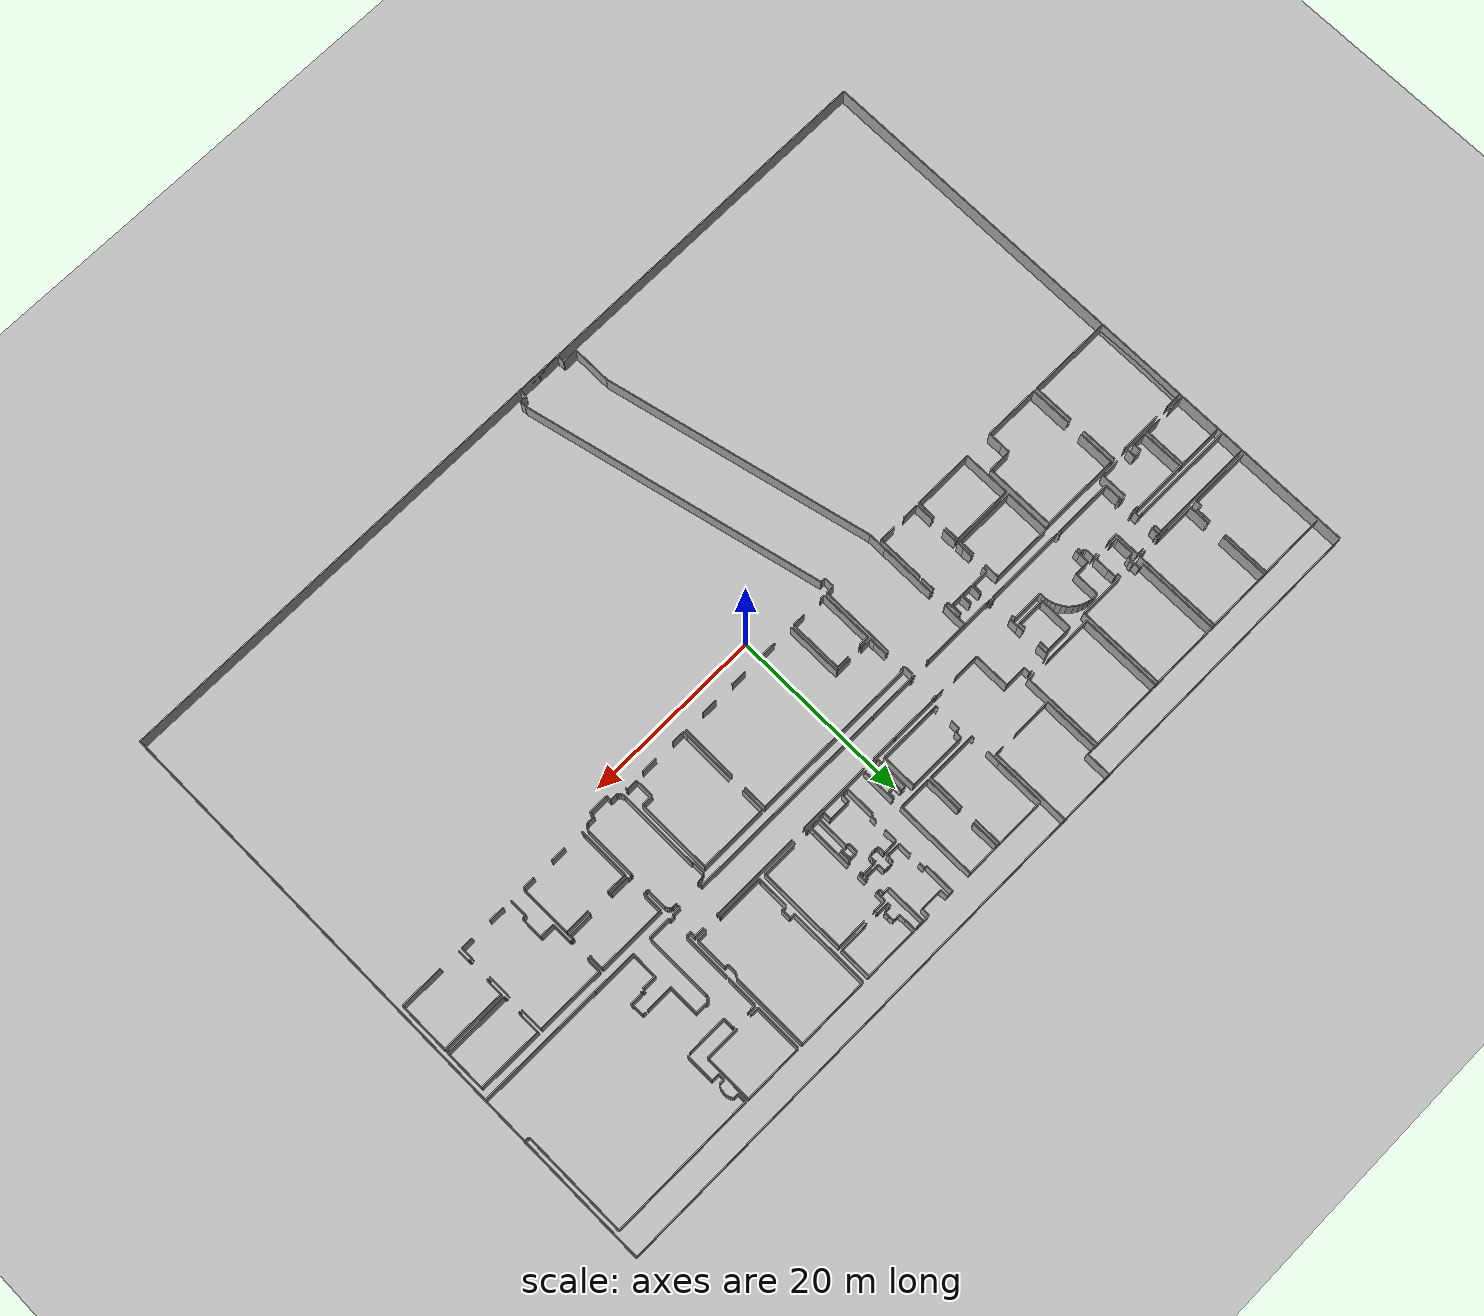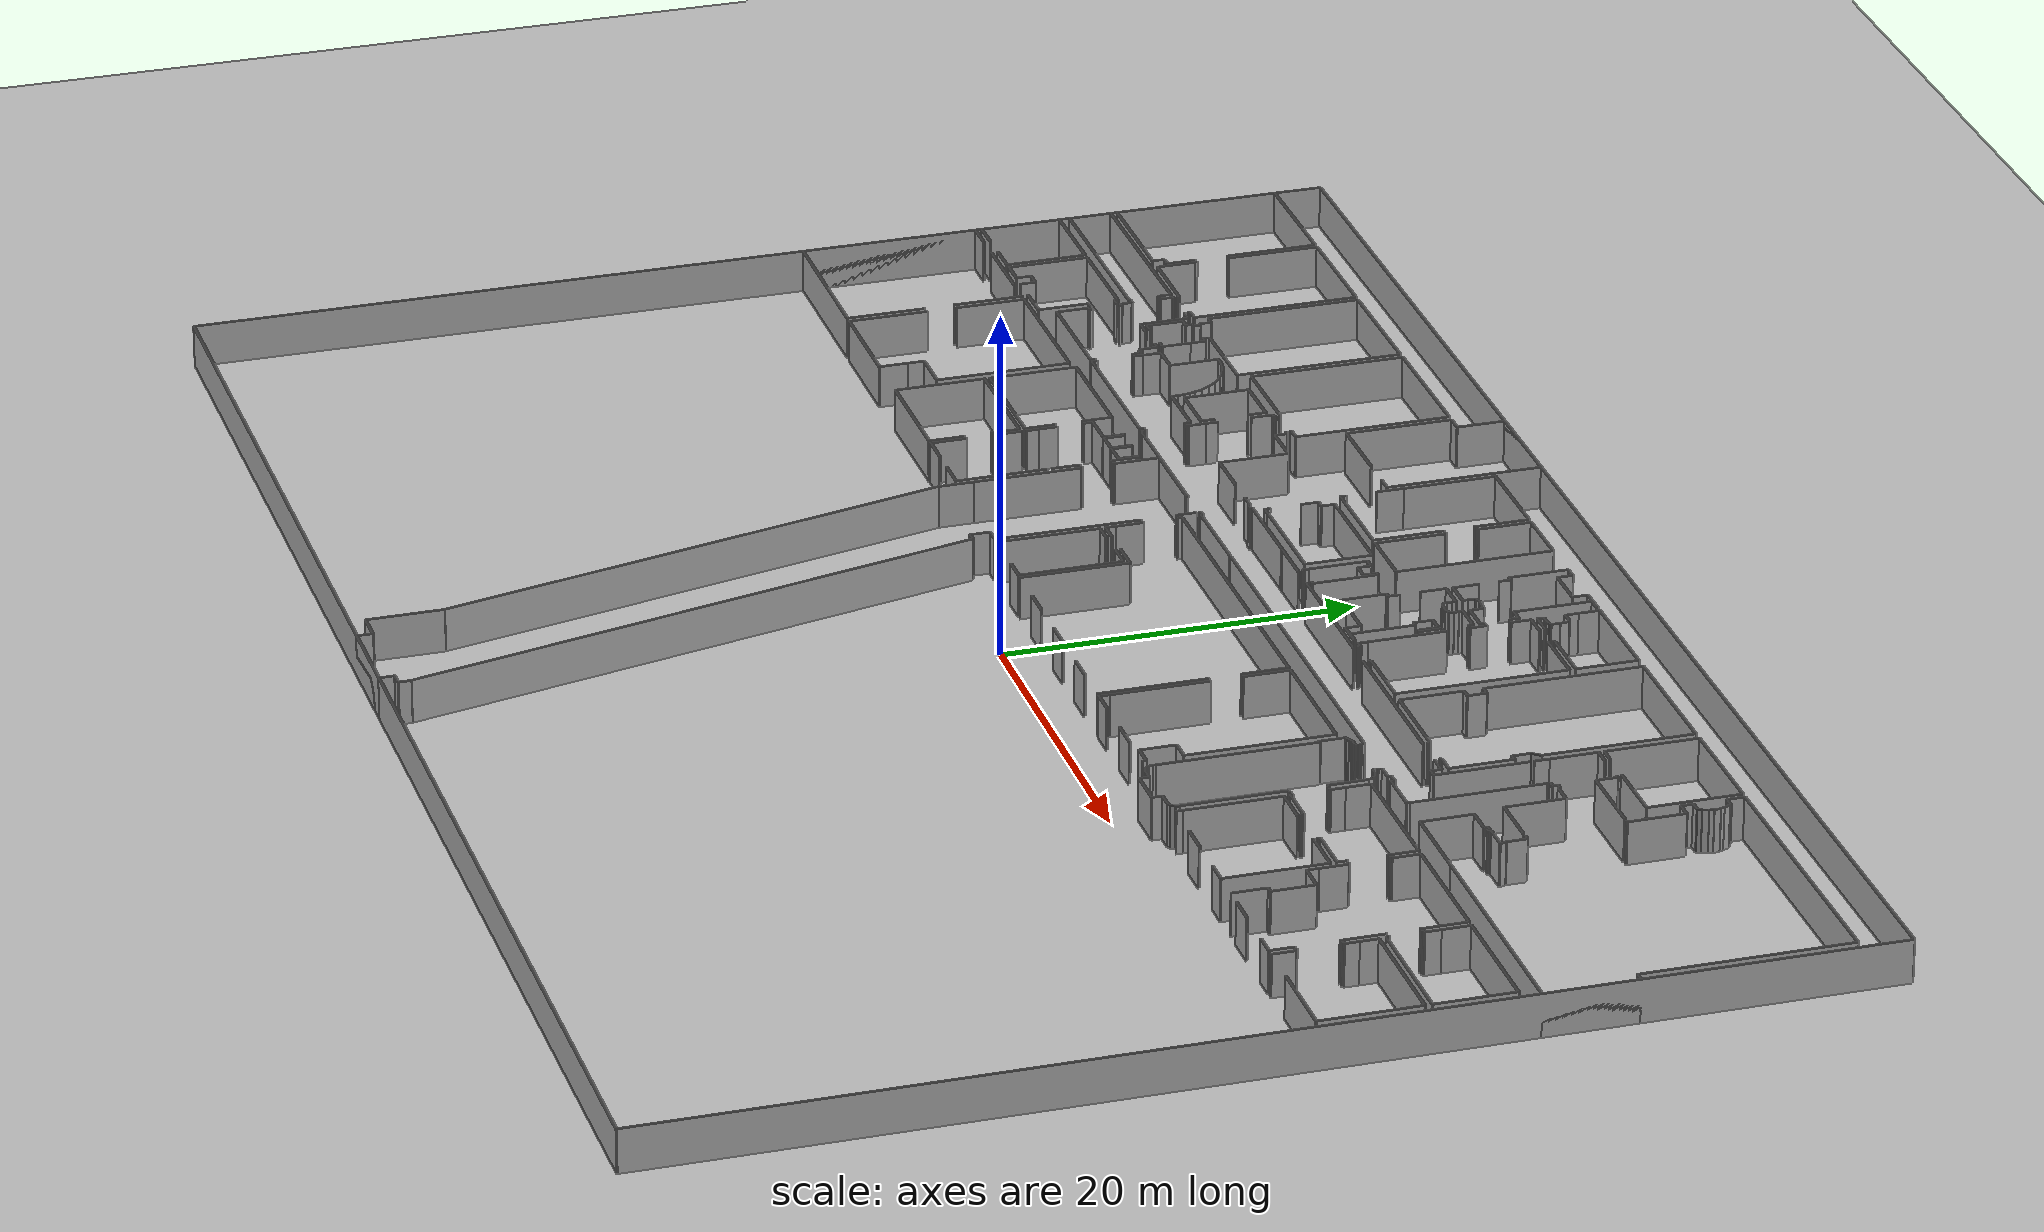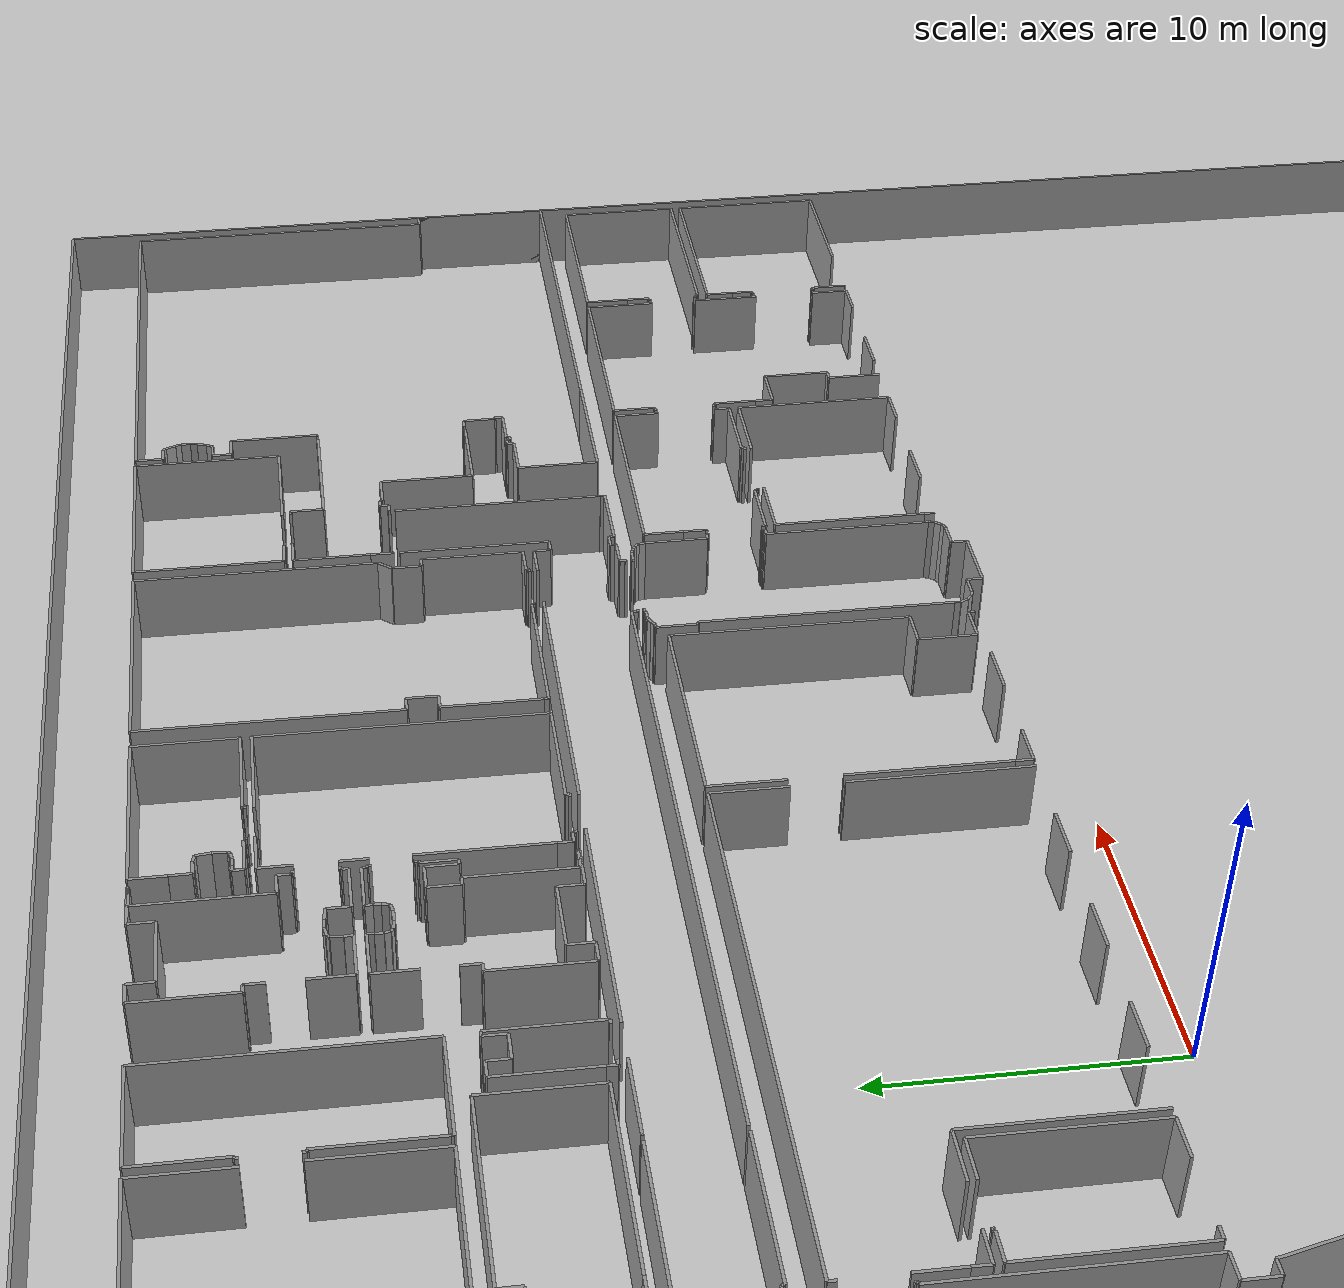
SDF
<sdf version="1.6">
  <world name="default">
    <light name="sun" type="directional">
      <cast_shadows>1</cast_shadows>
      <pose frame="">0 0 10 0 -0 0</pose>
      <diffuse>0.8 0.8 0.8 1</diffuse>
      <specular>0.1 0.1 0.1 1</specular>
      <attenuation>
        <range>1000</range>
        <constant>0.9</constant>
        <linear>0.01</linear>
        <quadratic>0.001</quadratic>
      </attenuation>
      <direction>-0.5 0.5 -1</direction>
    </light>
    <model name="ground_plane">
      <static>1</static>
      <link name="link">
        <collision name="collision">
          <geometry>
            <plane>
              <normal>0 0 1</normal>
              <size>100 100</size>
            </plane>
          </geometry>
          <surface>
            <friction>
              <ode>
                <mu>100</mu>
                <mu2>50</mu2>
              </ode>
              <torsional>
                <ode />
              </torsional>
            </friction>
            <contact>
              <ode />
            </contact>
            <bounce />
          </surface>
          <max_contacts>10</max_contacts>
        </collision>
        <visual name="visual">
          <cast_shadows>0</cast_shadows>
          <geometry>
            <plane>
              <normal>0 0 1</normal>
              <size>100 100</size>
            </plane>
          </geometry>
          <material>
            <script>
              <uri>file://media/materials/scripts/gazebo.material</uri>
              <name>Gazebo/Grey</name>
            </script>
          </material>
        </visual>
        <self_collide>0</self_collide>
        <kinematic>0</kinematic>
        <gravity>1</gravity>
      </link>
    </model>
    <gravity>0 0 -9.8</gravity>
    <magnetic_field>6e-06 2.3e-05 -4.2e-05</magnetic_field>
    <atmosphere type="adiabatic" />
    <physics default="0" name="default_physics" type="ode">
      <max_step_size>0.001</max_step_size>
      <real_time_factor>1</real_time_factor>
      <real_time_update_rate>1000</real_time_update_rate>
    </physics>
    <scene>
      <ambient>0.4 0.4 0.4 1</ambient>
      <background>0.7 0.7 0.7 1</background>
      <shadows>1</shadows>
    </scene>
    <spherical_coordinates>
      <surface_model>EARTH_WGS84</surface_model>
      <latitude_deg>0</latitude_deg>
      <longitude_deg>0</longitude_deg>
      <elevation>0</elevation>
      <heading_deg>0</heading_deg>
    </spherical_coordinates>
  <model name="0510032267_A_40_1_101">
		<static>1</static>
		<link name="Wall_0">
			<collision name="Wall_0_Collision">
				<geometry>
					<box>
						<size>9.65122411503 0.1 2.5</size>
					</box>
				</geometry>
				<pose frame="">4.82561205752 0 1.25 0 0 0</pose>
			</collision>
			<visual name="Wall_0_Visual">
				<pose frame="">4.82561205752 0 1.25 0 0 0</pose>
				<geometry>
					<box>
						<size>9.65122411503 0.1 2.5</size>
					</box>
				</geometry>
				<material>
					<script>
						<uri>file://media/materials/scripts/gazebo.material</uri>
						<name>Gazebo/Grey</name>
					</script>
					<ambient>1 1 1 1</ambient>
				</material>
			</visual>
			<pose frame="">0.000762490548293 -12.4551560246 0 0 0 1.57079632679</pose>
		</link>
		<link name="Wall_1">
			<collision name="Wall_1_Collision">
				<geometry>
					<box>
						<size>7.56708328303 0.1 2.5</size>
					</box>
				</geometry>
				<pose frame="">3.78354164152 0 1.25 0 0 0</pose>
			</collision>
			<visual name="Wall_1_Visual">
				<pose frame="">3.78354164152 0 1.25 0 0 0</pose>
				<geometry>
					<box>
						<size>7.56708328303 0.1 2.5</size>
					</box>
				</geometry>
				<material>
					<script>
						<uri>file://media/materials/scripts/gazebo.material</uri>
						<name>Gazebo/Grey</name>
					</script>
					<ambient>1 1 1 1</ambient>
				</material>
			</visual>
			<pose frame="">0.000762490548293 -2.80393190959 0 0 0 0.0</pose>
		</link>
		<link name="Wall_2">
			<collision name="Wall_2_Collision">
				<geometry>
					<box>
						<size>5.20196468398 0.1 2.5</size>
					</box>
				</geometry>
				<pose frame="">2.60098234199 0 1.25 0 0 0</pose>
			</collision>
			<visual name="Wall_2_Visual">
				<pose frame="">2.60098234199 0 1.25 0 0 0</pose>
				<geometry>
					<box>
						<size>5.20196468398 0.1 2.5</size>
					</box>
				</geometry>
				<material>
					<script>
						<uri>file://media/materials/scripts/gazebo.material</uri>
						<name>Gazebo/Grey</name>
					</script>
					<ambient>1 1 1 1</ambient>
				</material>
			</visual>
			<pose frame="">7.56784577358 -2.80393190959 0 0 0 -1.57079632679</pose>
		</link>
		<link name="Wall_3">
			<collision name="Wall_3_Collision">
				<geometry>
					<box>
						<size>0.0307537854479 0.1 2.5</size>
					</box>
				</geometry>
				<pose frame="">0.0153768927239 0 1.25 0 0 0</pose>
			</collision>
			<visual name="Wall_3_Visual">
				<pose frame="">0.0153768927239 0 1.25 0 0 0</pose>
				<geometry>
					<box>
						<size>0.0307537854479 0.1 2.5</size>
					</box>
				</geometry>
				<material>
					<script>
						<uri>file://media/materials/scripts/gazebo.material</uri>
						<name>Gazebo/Grey</name>
					</script>
					<ambient>1 1 1 1</ambient>
				</material>
			</visual>
			<pose frame="">7.56784577358 -8.00589659357 0 0 0 0.0</pose>
		</link>
		<link name="Wall_4">
			<collision name="Wall_4_Collision">
				<geometry>
					<box>
						<size>0.119329770808 0.1 2.5</size>
					</box>
				</geometry>
				<pose frame="">0.059664885404 0 1.25 0 0 0</pose>
			</collision>
			<visual name="Wall_4_Visual">
				<pose frame="">0.059664885404 0 1.25 0 0 0</pose>
				<geometry>
					<box>
						<size>0.119329770808 0.1 2.5</size>
					</box>
				</geometry>
				<material>
					<script>
						<uri>file://media/materials/scripts/gazebo.material</uri>
						<name>Gazebo/Grey</name>
					</script>
					<ambient>1 1 1 1</ambient>
				</material>
			</visual>
			<pose frame="">7.59859955903 -8.00589659357 0 0 0 -1.57079632679</pose>
		</link>
		<link name="Wall_5">
			<collision name="Wall_5_Collision">
				<geometry>
					<box>
						<size>1.68866240096 0.1 2.5</size>
					</box>
				</geometry>
				<pose frame="">0.844331200478 0 1.25 0 0 0</pose>
			</collision>
			<visual name="Wall_5_Visual">
				<pose frame="">0.844331200478 0 1.25 0 0 0</pose>
				<geometry>
					<box>
						<size>1.68866240096 0.1 2.5</size>
					</box>
				</geometry>
				<material>
					<script>
						<uri>file://media/materials/scripts/gazebo.material</uri>
						<name>Gazebo/Grey</name>
					</script>
					<ambient>1 1 1 1</ambient>
				</material>
			</visual>
			<pose frame="">7.59859955903 -10.0741522058 0 0 0 -1.57079632679</pose>
		</link>
		<link name="Wall_6">
			<collision name="Wall_6_Collision">
				<geometry>
					<box>
						<size>0.577967835607 0.1 2.5</size>
					</box>
				</geometry>
				<pose frame="">0.288983917804 0 1.25 0 0 0</pose>
			</collision>
			<visual name="Wall_6_Visual">
				<pose frame="">0.288983917804 0 1.25 0 0 0</pose>
				<geometry>
					<box>
						<size>0.577967835607 0.1 2.5</size>
					</box>
				</geometry>
				<material>
					<script>
						<uri>file://media/materials/scripts/gazebo.material</uri>
						<name>Gazebo/Grey</name>
					</script>
					<ambient>1 1 1 1</ambient>
				</material>
			</visual>
			<pose frame="">7.59859955903 -11.7628146068 0 0 0 3.14159265359</pose>
		</link>
		<link name="Wall_7">
			<collision name="Wall_7_Collision">
				<geometry>
					<box>
						<size>0.709878700462 0.1 2.5</size>
					</box>
				</geometry>
				<pose frame="">0.354939350231 0 1.25 0 0 0</pose>
			</collision>
			<visual name="Wall_7_Visual">
				<pose frame="">0.354939350231 0 1.25 0 0 0</pose>
				<geometry>
					<box>
						<size>0.709878700462 0.1 2.5</size>
					</box>
				</geometry>
				<material>
					<script>
						<uri>file://media/materials/scripts/gazebo.material</uri>
						<name>Gazebo/Grey</name>
					</script>
					<ambient>1 1 1 1</ambient>
				</material>
			</visual>
			<pose frame="">7.02063172342 -11.7628146068 0 0 0 -1.57079632679</pose>
		</link>
		<link name="Wall_8">
			<collision name="Wall_8_Collision">
				<geometry>
					<box>
						<size>7.01989113896 0.1 2.5</size>
					</box>
				</geometry>
				<pose frame="">3.50994556948 0 1.25 0 0 0</pose>
			</collision>
			<visual name="Wall_8_Visual">
				<pose frame="">3.50994556948 0 1.25 0 0 0</pose>
				<geometry>
					<box>
						<size>7.01989113896 0.1 2.5</size>
					</box>
				</geometry>
				<material>
					<script>
						<uri>file://media/materials/scripts/gazebo.material</uri>
						<name>Gazebo/Grey</name>
					</script>
					<ambient>1 1 1 1</ambient>
				</material>
			</visual>
			<pose frame="">7.02063172342 -12.4726933072 0 0 0 3.13909442384</pose>
		</link>
		<link name="Wall_9">
			<collision name="Wall_9_Collision">
				<geometry>
					<box>
						<size>2.25125334384 0.1 2.5</size>
					</box>
				</geometry>
				<pose frame="">1.12562667192 0 1.25 0 0 0</pose>
			</collision>
			<visual name="Wall_9_Visual">
				<pose frame="">1.12562667192 0 1.25 0 0 0</pose>
				<geometry>
					<box>
						<size>2.25125334384 0.1 2.5</size>
					</box>
				</geometry>
				<material>
					<script>
						<uri>file://media/materials/scripts/gazebo.material</uri>
						<name>Gazebo/Grey</name>
					</script>
					<ambient>1 1 1 1</ambient>
				</material>
			</visual>
			<pose frame="">7.90639157702 -12.4507081631 0 0 0 1.57079632679</pose>
		</link>
		<link name="Wall_10">
			<collision name="Wall_10_Collision">
				<geometry>
					<box>
						<size>0.02084140832 0.1 2.5</size>
					</box>
				</geometry>
				<pose frame="">0.01042070416 0 1.25 0 0 0</pose>
			</collision>
			<visual name="Wall_10_Visual">
				<pose frame="">0.01042070416 0 1.25 0 0 0</pose>
				<geometry>
					<box>
						<size>0.02084140832 0.1 2.5</size>
					</box>
				</geometry>
				<material>
					<script>
						<uri>file://media/materials/scripts/gazebo.material</uri>
						<name>Gazebo/Grey</name>
					</script>
					<ambient>1 1 1 1</ambient>
				</material>
			</visual>
			<pose frame="">7.90639157702 -10.1994548193 0 0 0 3.14159265359</pose>
		</link>
		<link name="Wall_11">
			<collision name="Wall_11_Collision">
				<geometry>
					<box>
						<size>0.151481455594 0.1 2.5</size>
					</box>
				</geometry>
				<pose frame="">0.0757407277972 0 1.25 0 0 0</pose>
			</collision>
			<visual name="Wall_11_Visual">
				<pose frame="">0.0757407277972 0 1.25 0 0 0</pose>
				<geometry>
					<box>
						<size>0.151481455594 0.1 2.5</size>
					</box>
				</geometry>
				<material>
					<script>
						<uri>file://media/materials/scripts/gazebo.material</uri>
						<name>Gazebo/Grey</name>
					</script>
					<ambient>1 1 1 1</ambient>
				</material>
			</visual>
			<pose frame="">7.8855501687 -10.1994548193 0 0 0 1.57079632679</pose>
		</link>
		<link name="Wall_12">
			<collision name="Wall_12_Collision">
				<geometry>
					<box>
						<size>5.33451095762 0.1 2.5</size>
					</box>
				</geometry>
				<pose frame="">2.66725547881 0 1.25 0 0 0</pose>
			</collision>
			<visual name="Wall_12_Visual">
				<pose frame="">2.66725547881 0 1.25 0 0 0</pose>
				<geometry>
					<box>
						<size>5.33451095762 0.1 2.5</size>
					</box>
				</geometry>
				<material>
					<script>
						<uri>file://media/materials/scripts/gazebo.material</uri>
						<name>Gazebo/Grey</name>
					</script>
					<ambient>1 1 1 1</ambient>
				</material>
			</visual>
			<pose frame="">7.8855501687 -8.12776799954 0 0 0 1.57079632679</pose>
		</link>
		<link name="Wall_13">
			<collision name="Wall_13_Collision">
				<geometry>
					<box>
						<size>7.15012803487 0.1 2.5</size>
					</box>
				</geometry>
				<pose frame="">3.57506401744 0 1.25 0 0 0</pose>
			</collision>
			<visual name="Wall_13_Visual">
				<pose frame="">3.57506401744 0 1.25 0 0 0</pose>
				<geometry>
					<box>
						<size>7.15012803487 0.1 2.5</size>
					</box>
				</geometry>
				<material>
					<script>
						<uri>file://media/materials/scripts/gazebo.material</uri>
						<name>Gazebo/Grey</name>
					</script>
					<ambient>1 1 1 1</ambient>
				</material>
			</visual>
			<pose frame="">7.8855501687 -2.79325704192 0 0 0 0.0</pose>
		</link>
		<link name="Wall_14">
			<collision name="Wall_14_Collision">
				<geometry>
					<box>
						<size>9.69824436551 0.1 2.5</size>
					</box>
				</geometry>
				<pose frame="">4.84912218276 0 1.25 0 0 0</pose>
			</collision>
			<visual name="Wall_14_Visual">
				<pose frame="">4.84912218276 0 1.25 0 0 0</pose>
				<geometry>
					<box>
						<size>9.69824436551 0.1 2.5</size>
					</box>
				</geometry>
				<material>
					<script>
						<uri>file://media/materials/scripts/gazebo.material</uri>
						<name>Gazebo/Grey</name>
					</script>
					<ambient>1 1 1 1</ambient>
				</material>
			</visual>
			<pose frame="">15.0356782036 -2.79325704192 0 0 0 -1.57079632679</pose>
		</link>
		<link name="Wall_15">
			<collision name="Wall_15_Collision">
				<geometry>
					<box>
						<size>0.707082901785 0.1 2.5</size>
					</box>
				</geometry>
				<pose frame="">0.353541450892 0 1.25 0 0 0</pose>
			</collision>
			<visual name="Wall_15_Visual">
				<pose frame="">0.353541450892 0 1.25 0 0 0</pose>
				<geometry>
					<box>
						<size>0.707082901785 0.1 2.5</size>
					</box>
				</geometry>
				<material>
					<script>
						<uri>file://media/materials/scripts/gazebo.material</uri>
						<name>Gazebo/Grey</name>
					</script>
					<ambient>1 1 1 1</ambient>
				</material>
			</visual>
			<pose frame="">15.0356782036 -12.4915014074 0 0 0 3.14159265359</pose>
		</link>
		<link name="Wall_16">
			<collision name="Wall_16_Collision">
				<geometry>
					<box>
						<size>0.0668450047338 0.1 2.5</size>
					</box>
				</geometry>
				<pose frame="">0.0334225023669 0 1.25 0 0 0</pose>
			</collision>
			<visual name="Wall_16_Visual">
				<pose frame="">0.0334225023669 0 1.25 0 0 0</pose>
				<geometry>
					<box>
						<size>0.0668450047338 0.1 2.5</size>
					</box>
				</geometry>
				<material>
					<script>
						<uri>file://media/materials/scripts/gazebo.material</uri>
						<name>Gazebo/Grey</name>
					</script>
					<ambient>1 1 1 1</ambient>
				</material>
			</visual>
			<pose frame="">14.3285953018 -12.4915014074 0 0 0 -1.57079632679</pose>
		</link>
		<link name="Wall_17">
			<collision name="Wall_17_Collision">
				<geometry>
					<box>
						<size>0.0955654820529 0.1 2.5</size>
					</box>
				</geometry>
				<pose frame="">0.0477827410264 0 1.25 0 0 0</pose>
			</collision>
			<visual name="Wall_17_Visual">
				<pose frame="">0.0477827410264 0 1.25 0 0 0</pose>
				<geometry>
					<box>
						<size>0.0955654820529 0.1 2.5</size>
					</box>
				</geometry>
				<material>
					<script>
						<uri>file://media/materials/scripts/gazebo.material</uri>
						<name>Gazebo/Grey</name>
					</script>
					<ambient>1 1 1 1</ambient>
				</material>
			</visual>
			<pose frame="">14.3285953018 -12.5583464122 0 0 0 3.14159265359</pose>
		</link>
		<link name="Wall_18">
			<collision name="Wall_18_Collision">
				<geometry>
					<box>
						<size>0.0939134191982 0.1 2.5</size>
					</box>
				</geometry>
				<pose frame="">0.0469567095991 0 1.25 0 0 0</pose>
			</collision>
			<visual name="Wall_18_Visual">
				<pose frame="">0.0469567095991 0 1.25 0 0 0</pose>
				<geometry>
					<box>
						<size>0.0939134191982 0.1 2.5</size>
					</box>
				</geometry>
				<material>
					<script>
						<uri>file://media/materials/scripts/gazebo.material</uri>
						<name>Gazebo/Grey</name>
					</script>
					<ambient>1 1 1 1</ambient>
				</material>
			</visual>
			<pose frame="">12.2940163554 -12.5583464122 0 0 0 3.14159265359</pose>
		</link>
		<link name="Wall_19">
			<collision name="Wall_19_Collision">
				<geometry>
					<box>
						<size>0.0815864886675 0.1 2.5</size>
					</box>
				</geometry>
				<pose frame="">0.0407932443337 0 1.25 0 0 0</pose>
			</collision>
			<visual name="Wall_19_Visual">
				<pose frame="">0.0407932443337 0 1.25 0 0 0</pose>
				<geometry>
					<box>
						<size>0.0815864886675 0.1 2.5</size>
					</box>
				</geometry>
				<material>
					<script>
						<uri>file://media/materials/scripts/gazebo.material</uri>
						<name>Gazebo/Grey</name>
					</script>
					<ambient>1 1 1 1</ambient>
				</material>
			</visual>
			<pose frame="">12.2001029362 -12.5583464122 0 0 0 1.57079632679</pose>
		</link>
		<link name="Wall_20">
			<collision name="Wall_20_Collision">
				<geometry>
					<box>
						<size>4.29379039199 0.1 2.5</size>
					</box>
				</geometry>
				<pose frame="">2.146895196 0 1.25 0 0 0</pose>
			</collision>
			<visual name="Wall_20_Visual">
				<pose frame="">2.146895196 0 1.25 0 0 0</pose>
				<geometry>
					<box>
						<size>4.29379039199 0.1 2.5</size>
					</box>
				</geometry>
				<material>
					<script>
						<uri>file://media/materials/scripts/gazebo.material</uri>
						<name>Gazebo/Grey</name>
					</script>
					<ambient>1 1 1 1</ambient>
				</material>
			</visual>
			<pose frame="">12.2001029362 -12.4767599235 0 0 0 3.13552530566</pose>
		</link>
		<link name="Wall_21">
			<collision name="Wall_21_Collision">
				<geometry>
					<box>
						<size>2.50833974037 0.1 2.5</size>
					</box>
				</geometry>
				<pose frame="">1.25416987019 0 1.25 0 0 0</pose>
			</collision>
			<visual name="Wall_21_Visual">
				<pose frame="">1.25416987019 0 1.25 0 0 0</pose>
				<geometry>
					<box>
						<size>2.50833974037 0.1 2.5</size>
					</box>
				</geometry>
				<material>
					<script>
						<uri>file://media/materials/scripts/gazebo.material</uri>
						<name>Gazebo/Grey</name>
					</script>
					<ambient>1 1 1 1</ambient>
				</material>
			</visual>
			<pose frame="">0.00330412570927 -15.3438514668 0 0 0 1.57079632679</pose>
		</link>
		<link name="Wall_22">
			<collision name="Wall_22_Collision">
				<geometry>
					<box>
						<size>11.6936821304 0.1 2.5</size>
					</box>
				</geometry>
				<pose frame="">5.8468410652 0 1.25 0 0 0</pose>
			</collision>
			<visual name="Wall_22_Visual">
				<pose frame="">5.8468410652 0 1.25 0 0 0</pose>
				<geometry>
					<box>
						<size>11.6936821304 0.1 2.5</size>
					</box>
				</geometry>
				<material>
					<script>
						<uri>file://media/materials/scripts/gazebo.material</uri>
						<name>Gazebo/Grey</name>
					</script>
					<ambient>1 1 1 1</ambient>
				</material>
			</visual>
			<pose frame="">0.00330412570927 -12.8355117265 0 0 0 0.0</pose>
		</link>
		<link name="Wall_23">
			<collision name="Wall_23_Collision">
				<geometry>
					<box>
						<size>0.729068045927 0.1 2.5</size>
					</box>
				</geometry>
				<pose frame="">0.364534022964 0 1.25 0 0 0</pose>
			</collision>
			<visual name="Wall_23_Visual">
				<pose frame="">0.364534022964 0 1.25 0 0 0</pose>
				<geometry>
					<box>
						<size>0.729068045927 0.1 2.5</size>
					</box>
				</geometry>
				<material>
					<script>
						<uri>file://media/materials/scripts/gazebo.material</uri>
						<name>Gazebo/Grey</name>
					</script>
					<ambient>1 1 1 1</ambient>
				</material>
			</visual>
			<pose frame="">11.6969862561 -12.8355117265 0 0 0 -1.57079632679</pose>
		</link>
		<link name="Wall_24">
			<collision name="Wall_24_Collision">
				<geometry>
					<box>
						<size>0.093405092166 0.1 2.5</size>
					</box>
				</geometry>
				<pose frame="">0.046702546083 0 1.25 0 0 0</pose>
			</collision>
			<visual name="Wall_24_Visual">
				<pose frame="">0.046702546083 0 1.25 0 0 0</pose>
				<geometry>
					<box>
						<size>0.093405092166 0.1 2.5</size>
					</box>
				</geometry>
				<material>
					<script>
						<uri>file://media/materials/scripts/gazebo.material</uri>
						<name>Gazebo/Grey</name>
					</script>
					<ambient>1 1 1 1</ambient>
				</material>
			</visual>
			<pose frame="">11.6969862561 -13.5645797724 0 0 0 0.0</pose>
		</link>
		<link name="Wall_25">
			<collision name="Wall_25_Collision">
				<geometry>
					<box>
						<size>0.126319267501 0.1 2.5</size>
					</box>
				</geometry>
				<pose frame="">0.0631596337504 0 1.25 0 0 0</pose>
			</collision>
			<visual name="Wall_25_Visual">
				<pose frame="">0.0631596337504 0 1.25 0 0 0</pose>
				<geometry>
					<box>
						<size>0.126319267501 0.1 2.5</size>
					</box>
				</geometry>
				<material>
					<script>
						<uri>file://media/materials/scripts/gazebo.material</uri>
						<name>Gazebo/Grey</name>
					</script>
					<ambient>1 1 1 1</ambient>
				</material>
			</visual>
			<pose frame="">11.7903913483 -13.5645797724 0 0 0 -1.57079632679</pose>
		</link>
		<link name="Wall_26">
			<collision name="Wall_26_Collision">
				<geometry>
					<box>
						<size>0.137375380451 0.1 2.5</size>
					</box>
				</geometry>
				<pose frame="">0.0686876902255 0 1.25 0 0 0</pose>
			</collision>
			<visual name="Wall_26_Visual">
				<pose frame="">0.0686876902255 0 1.25 0 0 0</pose>
				<geometry>
					<box>
						<size>0.137375380451 0.1 2.5</size>
					</box>
				</geometry>
				<material>
					<script>
						<uri>file://media/materials/scripts/gazebo.material</uri>
						<name>Gazebo/Grey</name>
					</script>
					<ambient>1 1 1 1</ambient>
				</material>
			</visual>
			<pose frame="">11.7903913483 -15.2182946899 0 0 0 -1.57079632679</pose>
		</link>
		<link name="Wall_27">
			<collision name="Wall_27_Collision">
				<geometry>
					<box>
						<size>11.7870931477 0.1 2.5</size>
					</box>
				</geometry>
				<pose frame="">5.89354657383 0 1.25 0 0 0</pose>
			</collision>
			<visual name="Wall_27_Visual">
				<pose frame="">5.89354657383 0 1.25 0 0 0</pose>
				<geometry>
					<box>
						<size>11.7870931477 0.1 2.5</size>
					</box>
				</geometry>
				<material>
					<script>
						<uri>file://media/materials/scripts/gazebo.material</uri>
						<name>Gazebo/Grey</name>
					</script>
					<ambient>1 1 1 1</ambient>
				</material>
			</visual>
			<pose frame="">11.7903913483 -15.3556700703 0 0 0 3.14058998013</pose>
		</link>
		<link name="Wall_28">
			<collision name="Wall_28_Collision">
				<geometry>
					<box>
						<size>4.71943524867 0.1 2.5</size>
					</box>
				</geometry>
				<pose frame="">2.35971762433 0 1.25 0 0 0</pose>
			</collision>
			<visual name="Wall_28_Visual">
				<pose frame="">2.35971762433 0 1.25 0 0 0</pose>
				<geometry>
					<box>
						<size>4.71943524867 0.1 2.5</size>
					</box>
				</geometry>
				<material>
					<script>
						<uri>file://media/materials/scripts/gazebo.material</uri>
						<name>Gazebo/Grey</name>
					</script>
					<ambient>1 1 1 1</ambient>
				</material>
			</visual>
			<pose frame="">0.00559159735415 -20.6793790785 0 0 0 1.57079632679</pose>
		</link>
		<link name="Wall_29">
			<collision name="Wall_29_Collision">
				<geometry>
					<box>
						<size>5.12596979267 0.1 2.5</size>
					</box>
				</geometry>
				<pose frame="">2.56298489633 0 1.25 0 0 0</pose>
			</collision>
			<visual name="Wall_29_Visual">
				<pose frame="">2.56298489633 0 1.25 0 0 0</pose>
				<geometry>
					<box>
						<size>5.12596979267 0.1 2.5</size>
					</box>
				</geometry>
				<material>
					<script>
						<uri>file://media/materials/scripts/gazebo.material</uri>
						<name>Gazebo/Grey</name>
					</script>
					<ambient>1 1 1 1</ambient>
				</material>
			</visual>
			<pose frame="">0.00559159735415 -15.9599438299 0 0 0 0.0</pose>
		</link>
		<link name="Wall_30">
			<collision name="Wall_30_Collision">
				<geometry>
					<box>
						<size>4.70583750056 0.1 2.5</size>
					</box>
				</geometry>
				<pose frame="">2.35291875028 0 1.25 0 0 0</pose>
			</collision>
			<visual name="Wall_30_Visual">
				<pose frame="">2.35291875028 0 1.25 0 0 0</pose>
				<geometry>
					<box>
						<size>4.70583750056 0.1 2.5</size>
					</box>
				</geometry>
				<material>
					<script>
						<uri>file://media/materials/scripts/gazebo.material</uri>
						<name>Gazebo/Grey</name>
					</script>
					<ambient>1 1 1 1</ambient>
				</material>
			</visual>
			<pose frame="">5.13156139002 -15.9599438299 0 0 0 -1.57079632679</pose>
		</link>
		<link name="Wall_31">
			<collision name="Wall_31_Collision">
				<geometry>
					<box>
						<size>1.8054505366 0.1 2.5</size>
					</box>
				</geometry>
				<pose frame="">0.902725268301 0 1.25 0 0 0</pose>
			</collision>
			<visual name="Wall_31_Visual">
				<pose frame="">0.902725268301 0 1.25 0 0 0</pose>
				<geometry>
					<box>
						<size>1.8054505366 0.1 2.5</size>
					</box>
				</geometry>
				<material>
					<script>
						<uri>file://media/materials/scripts/gazebo.material</uri>
						<name>Gazebo/Grey</name>
					</script>
					<ambient>1 1 1 1</ambient>
				</material>
			</visual>
			<pose frame="">5.13156139002 -20.6657813304 0 0 0 3.14159265359</pose>
		</link>
		<link name="Wall_32">
			<collision name="Wall_32_Collision">
				<geometry>
					<box>
						<size>1.76356597907 0.1 2.5</size>
					</box>
				</geometry>
				<pose frame="">0.881782989534 0 1.25 0 0 0</pose>
			</collision>
			<visual name="Wall_32_Visual">
				<pose frame="">0.881782989534 0 1.25 0 0 0</pose>
				<geometry>
					<box>
						<size>1.76356597907 0.1 2.5</size>
					</box>
				</geometry>
				<material>
					<script>
						<uri>file://media/materials/scripts/gazebo.material</uri>
						<name>Gazebo/Grey</name>
					</script>
					<ambient>1 1 1 1</ambient>
				</material>
			</visual>
			<pose frame="">1.7691051538 -20.6657813304 0 0 0 -3.13388220612</pose>
		</link>
		<link name="Wall_33">
			<collision name="Wall_33_Collision">
				<geometry>
					<box>
						<size>4.68918979025 0.1 2.5</size>
					</box>
				</geometry>
				<pose frame="">2.34459489513 0 1.25 0 0 0</pose>
			</collision>
			<visual name="Wall_33_Visual">
				<pose frame="">2.34459489513 0 1.25 0 0 0</pose>
				<geometry>
					<box>
						<size>4.68918979025 0.1 2.5</size>
					</box>
				</geometry>
				<material>
					<script>
						<uri>file://media/materials/scripts/gazebo.material</uri>
						<name>Gazebo/Grey</name>
					</script>
					<ambient>1 1 1 1</ambient>
				</material>
			</visual>
			<pose frame="">5.50823172088 -20.6491336201 0 0 0 1.57079632679</pose>
		</link>
		<link name="Wall_34">
			<collision name="Wall_34_Collision">
				<geometry>
					<box>
						<size>6.00118186035 0.1 2.5</size>
					</box>
				</geometry>
				<pose frame="">3.00059093017 0 1.25 0 0 0</pose>
			</collision>
			<visual name="Wall_34_Visual">
				<pose frame="">3.00059093017 0 1.25 0 0 0</pose>
				<geometry>
					<box>
						<size>6.00118186035 0.1 2.5</size>
					</box>
				</geometry>
				<material>
					<script>
						<uri>file://media/materials/scripts/gazebo.material</uri>
						<name>Gazebo/Grey</name>
					</script>
					<ambient>1 1 1 1</ambient>
				</material>
			</visual>
			<pose frame="">5.50823172088 -15.9599438299 0 0 0 0.0</pose>
		</link>
		<link name="Wall_35">
			<collision name="Wall_35_Collision">
				<geometry>
					<box>
						<size>0.191258045864 0.1 2.5</size>
					</box>
				</geometry>
				<pose frame="">0.0956290229319 0 1.25 0 0 0</pose>
			</collision>
			<visual name="Wall_35_Visual">
				<pose frame="">0.0956290229319 0 1.25 0 0 0</pose>
				<geometry>
					<box>
						<size>0.191258045864 0.1 2.5</size>
					</box>
				</geometry>
				<material>
					<script>
						<uri>file://media/materials/scripts/gazebo.material</uri>
						<name>Gazebo/Grey</name>
					</script>
					<ambient>1 1 1 1</ambient>
				</material>
			</visual>
			<pose frame="">11.5094135812 -15.9599438299 0 0 0 -1.57079632679</pose>
		</link>
		<link name="Wall_36">
			<collision name="Wall_36_Collision">
				<geometry>
					<box>
						<size>0.562336779367 0.1 2.5</size>
					</box>
				</geometry>
				<pose frame="">0.281168389684 0 1.25 0 0 0</pose>
			</collision>
			<visual name="Wall_36_Visual">
				<pose frame="">0.281168389684 0 1.25 0 0 0</pose>
				<geometry>
					<box>
						<size>0.562336779367 0.1 2.5</size>
					</box>
				</geometry>
				<material>
					<script>
						<uri>file://media/materials/scripts/gazebo.material</uri>
						<name>Gazebo/Grey</name>
					</script>
					<ambient>1 1 1 1</ambient>
				</material>
			</visual>
			<pose frame="">11.5094135812 -16.1512018757 0 0 0 0.0</pose>
		</link>
		<link name="Wall_37">
			<collision name="Wall_37_Collision">
				<geometry>
					<box>
						<size>0.550772339385 0.1 2.5</size>
					</box>
				</geometry>
				<pose frame="">0.275386169692 0 1.25 0 0 0</pose>
			</collision>
			<visual name="Wall_37_Visual">
				<pose frame="">0.275386169692 0 1.25 0 0 0</pose>
				<geometry>
					<box>
						<size>0.550772339385 0.1 2.5</size>
					</box>
				</geometry>
				<material>
					<script>
						<uri>file://media/materials/scripts/gazebo.material</uri>
						<name>Gazebo/Grey</name>
					</script>
					<ambient>1 1 1 1</ambient>
				</material>
			</visual>
			<pose frame="">12.0717503606 -17.7040138773 0 0 0 3.14159265359</pose>
		</link>
		<link name="Wall_38">
			<collision name="Wall_38_Collision">
				<geometry>
					<box>
						<size>2.9856588236 0.1 2.5</size>
					</box>
				</geometry>
				<pose frame="">1.4928294118 0 1.25 0 0 0</pose>
			</collision>
			<visual name="Wall_38_Visual">
				<pose frame="">1.4928294118 0 1.25 0 0 0</pose>
				<geometry>
					<box>
						<size>2.9856588236 0.1 2.5</size>
					</box>
				</geometry>
				<material>
					<script>
						<uri>file://media/materials/scripts/gazebo.material</uri>
						<name>Gazebo/Grey</name>
					</script>
					<ambient>1 1 1 1</ambient>
				</material>
			</visual>
			<pose frame="">11.5209780212 -17.7040138773 0 0 0 -1.57079632679</pose>
		</link>
		<link name="Wall_39">
			<collision name="Wall_39_Collision">
				<geometry>
					<box>
						<size>2.08452207728 0.1 2.5</size>
					</box>
				</geometry>
				<pose frame="">1.04226103864 0 1.25 0 0 0</pose>
			</collision>
			<visual name="Wall_39_Visual">
				<pose frame="">1.04226103864 0 1.25 0 0 0</pose>
				<geometry>
					<box>
						<size>2.08452207728 0.1 2.5</size>
					</box>
				</geometry>
				<material>
					<script>
						<uri>file://media/materials/scripts/gazebo.material</uri>
						<name>Gazebo/Grey</name>
					</script>
					<ambient>1 1 1 1</ambient>
				</material>
			</visual>
			<pose frame="">11.5209780212 -20.6896727009 0 0 0 3.14159265359</pose>
		</link>
		<link name="Wall_40">
			<collision name="Wall_40_Collision">
				<geometry>
					<box>
						<size>0.908507488293 0.1 2.5</size>
					</box>
				</geometry>
				<pose frame="">0.454253744146 0 1.25 0 0 0</pose>
			</collision>
			<visual name="Wall_40_Visual">
				<pose frame="">0.454253744146 0 1.25 0 0 0</pose>
				<geometry>
					<box>
						<size>0.908507488293 0.1 2.5</size>
					</box>
				</geometry>
				<material>
					<script>
						<uri>file://media/materials/scripts/gazebo.material</uri>
						<name>Gazebo/Grey</name>
					</script>
					<ambient>1 1 1 1</ambient>
				</material>
			</visual>
			<pose frame="">7.88682098628 -20.6896727009 0 0 0 1.57079632679</pose>
		</link>
		<link name="Wall_41">
			<collision name="Wall_41_Collision">
				<geometry>
					<box>
						<size>0.867078835169 0.1 2.5</size>
					</box>
				</geometry>
				<pose frame="">0.433539417584 0 1.25 0 0 0</pose>
			</collision>
			<visual name="Wall_41_Visual">
				<pose frame="">0.433539417584 0 1.25 0 0 0</pose>
				<geometry>
					<box>
						<size>0.867078835169 0.1 2.5</size>
					</box>
				</geometry>
				<material>
					<script>
						<uri>file://media/materials/scripts/gazebo.material</uri>
						<name>Gazebo/Grey</name>
					</script>
					<ambient>1 1 1 1</ambient>
				</material>
			</visual>
			<pose frame="">7.88682098628 -19.7811652126 0 0 0 3.14159265359</pose>
		</link>
		<link name="Wall_42">
			<collision name="Wall_42_Collision">
				<geometry>
					<box>
						<size>0.880803665038 0.1 2.5</size>
					</box>
				</geometry>
				<pose frame="">0.440401832519 0 1.25 0 0 0</pose>
			</collision>
			<visual name="Wall_42_Visual">
				<pose frame="">0.440401832519 0 1.25 0 0 0</pose>
				<geometry>
					<box>
						<size>0.880803665038 0.1 2.5</size>
					</box>
				</geometry>
				<material>
					<script>
						<uri>file://media/materials/scripts/gazebo.material</uri>
						<name>Gazebo/Grey</name>
					</script>
					<ambient>1 1 1 1</ambient>
				</material>
			</visual>
			<pose frame="">7.01974215111 -19.7811652126 0 0 0 -1.57079632679</pose>
		</link>
		<link name="Wall_43">
			<collision name="Wall_43_Collision">
				<geometry>
					<box>
						<size>1.51156492568 0.1 2.5</size>
					</box>
				</geometry>
				<pose frame="">0.75578246284 0 1.25 0 0 0</pose>
			</collision>
			<visual name="Wall_43_Visual">
				<pose frame="">0.75578246284 0 1.25 0 0 0</pose>
				<geometry>
					<box>
						<size>1.51156492568 0.1 2.5</size>
					</box>
				</geometry>
				<material>
					<script>
						<uri>file://media/materials/scripts/gazebo.material</uri>
						<name>Gazebo/Grey</name>
					</script>
					<ambient>1 1 1 1</ambient>
				</material>
			</visual>
			<pose frame="">7.01974215111 -20.6619688777 0 0 0 3.13310118121</pose>
		</link>
		<link name="Wall_44">
			<collision name="Wall_44_Collision">
				<geometry>
					<box>
						<size>10.3564007904 0.1 2.5</size>
					</box>
				</geometry>
				<pose frame="">5.17820039522 0 1.25 0 0 0</pose>
			</collision>
			<visual name="Wall_44_Visual">
				<pose frame="">5.17820039522 0 1.25 0 0 0</pose>
				<geometry>
					<box>
						<size>10.3564007904 0.1 2.5</size>
					</box>
				</geometry>
				<material>
					<script>
						<uri>file://media/materials/scripts/gazebo.material</uri>
						<name>Gazebo/Grey</name>
					</script>
					<ambient>1 1 1 1</ambient>
				</material>
			</visual>
			<pose frame="">0.0 -31.4094002376 0 0 0 1.57079632679</pose>
		</link>
		<link name="Wall_45">
			<collision name="Wall_45_Collision">
				<geometry>
					<box>
						<size>1.78562578235 0.1 2.5</size>
					</box>
				</geometry>
				<pose frame="">0.892812891174 0 1.25 0 0 0</pose>
			</collision>
			<visual name="Wall_45_Visual">
				<pose frame="">0.892812891174 0 1.25 0 0 0</pose>
				<geometry>
					<box>
						<size>1.78562578235 0.1 2.5</size>
					</box>
				</geometry>
				<material>
					<script>
						<uri>file://media/materials/scripts/gazebo.material</uri>
						<name>Gazebo/Grey</name>
					</script>
					<ambient>1 1 1 1</ambient>
				</material>
			</visual>
			<pose frame="">0.0 -21.0529994472 0 0 0 0.0</pose>
		</link>
		<link name="Wall_46">
			<collision name="Wall_46_Collision">
				<geometry>
					<box>
						<size>4.58383901283 0.1 2.5</size>
					</box>
				</geometry>
				<pose frame="">2.29191950641 0 1.25 0 0 0</pose>
			</collision>
			<visual name="Wall_46_Visual">
				<pose frame="">2.29191950641 0 1.25 0 0 0</pose>
				<geometry>
					<box>
						<size>4.58383901283 0.1 2.5</size>
					</box>
				</geometry>
				<material>
					<script>
						<uri>file://media/materials/scripts/gazebo.material</uri>
						<name>Gazebo/Grey</name>
					</script>
					<ambient>1 1 1 1</ambient>
				</material>
			</visual>
			<pose frame="">3.33818362043 -21.0529994472 0 0 0 0.0</pose>
		</link>
		<link name="Wall_47">
			<collision name="Wall_47_Collision">
				<geometry>
					<box>
						<size>0.062270061444 0.1 2.5</size>
					</box>
				</geometry>
				<pose frame="">0.031135030722 0 1.25 0 0 0</pose>
			</collision>
			<visual name="Wall_47_Visual">
				<pose frame="">0.031135030722 0 1.25 0 0 0</pose>
				<geometry>
					<box>
						<size>0.062270061444 0.1 2.5</size>
					</box>
				</geometry>
				<material>
					<script>
						<uri>file://media/materials/scripts/gazebo.material</uri>
						<name>Gazebo/Grey</name>
					</script>
					<ambient>1 1 1 1</ambient>
				</material>
			</visual>
			<pose frame="">9.44090380546 -21.0529994472 0 0 0 0.0</pose>
		</link>
		<link name="Wall_48">
			<collision name="Wall_48_Collision">
				<geometry>
					<box>
						<size>4.06013508791 0.1 2.5</size>
					</box>
				</geometry>
				<pose frame="">2.03006754395 0 1.25 0 0 0</pose>
			</collision>
			<visual name="Wall_48_Visual">
				<pose frame="">2.03006754395 0 1.25 0 0 0</pose>
				<geometry>
					<box>
						<size>4.06013508791 0.1 2.5</size>
					</box>
				</geometry>
				<material>
					<script>
						<uri>file://media/materials/scripts/gazebo.material</uri>
						<name>Gazebo/Grey</name>
					</script>
					<ambient>1 1 1 1</ambient>
				</material>
			</visual>
			<pose frame="">9.50317386691 -21.0529994472 0 0 0 -1.57079632679</pose>
		</link>
		<link name="Wall_49">
			<collision name="Wall_49_Collision">
				<geometry>
					<box>
						<size>4.60531582994 0.1 2.5</size>
					</box>
				</geometry>
				<pose frame="">2.30265791497 0 1.25 0 0 0</pose>
			</collision>
			<visual name="Wall_49_Visual">
				<pose frame="">2.30265791497 0 1.25 0 0 0</pose>
				<geometry>
					<box>
						<size>4.60531582994 0.1 2.5</size>
					</box>
				</geometry>
				<material>
					<script>
						<uri>file://media/materials/scripts/gazebo.material</uri>
						<name>Gazebo/Grey</name>
					</script>
					<ambient>1 1 1 1</ambient>
				</material>
			</visual>
			<pose frame="">9.50317386691 -26.8372527466 0 0 0 -1.57079632679</pose>
		</link>
		<link name="Wall_50">
			<collision name="Wall_50_Collision">
				<geometry>
					<box>
						<size>9.50323174943 0.1 2.5</size>
					</box>
				</geometry>
				<pose frame="">4.75161587471 0 1.25 0 0 0</pose>
			</collision>
			<visual name="Wall_50_Visual">
				<pose frame="">4.75161587471 0 1.25 0 0 0</pose>
				<geometry>
					<box>
						<size>9.50323174943 0.1 2.5</size>
					</box>
				</geometry>
				<material>
					<script>
						<uri>file://media/materials/scripts/gazebo.material</uri>
						<name>Gazebo/Grey</name>
					</script>
					<ambient>1 1 1 1</ambient>
				</material>
			</visual>
			<pose frame="">9.50317386691 -31.4425685765 0 0 0 3.13810242973</pose>
		</link>
		<link name="Wall_51">
			<collision name="Wall_51_Collision">
				<geometry>
					<box>
						<size>4.62577599299 0.1 2.5</size>
					</box>
				</geometry>
				<pose frame="">2.31288799649 0 1.25 0 0 0</pose>
			</collision>
			<visual name="Wall_51_Visual">
				<pose frame="">2.31288799649 0 1.25 0 0 0</pose>
				<geometry>
					<box>
						<size>4.62577599299 0.1 2.5</size>
					</box>
				</geometry>
				<material>
					<script>
						<uri>file://media/materials/scripts/gazebo.material</uri>
						<name>Gazebo/Grey</name>
					</script>
					<ambient>1 1 1 1</ambient>
				</material>
			</visual>
			<pose frame="">9.92864359286 -31.4496851549 0 0 0 1.57079632679</pose>
		</link>
		<link name="Wall_52">
			<collision name="Wall_52_Collision">
				<geometry>
					<box>
						<size>4.02874589367 0.1 2.5</size>
					</box>
				</geometry>
				<pose frame="">2.01437294684 0 1.25 0 0 0</pose>
			</collision>
			<visual name="Wall_52_Visual">
				<pose frame="">2.01437294684 0 1.25 0 0 0</pose>
				<geometry>
					<box>
						<size>4.02874589367 0.1 2.5</size>
					</box>
				</geometry>
				<material>
					<script>
						<uri>file://media/materials/scripts/gazebo.material</uri>
						<name>Gazebo/Grey</name>
					</script>
					<ambient>1 1 1 1</ambient>
				</material>
			</visual>
			<pose frame="">9.92864359286 -25.0924202085 0 0 0 1.57079632679</pose>
		</link>
		<link name="Wall_53">
			<collision name="Wall_53_Collision">
				<geometry>
					<box>
						<size>8.8873356674 0.1 2.5</size>
					</box>
				</geometry>
				<pose frame="">4.4436678337 0 1.25 0 0 0</pose>
			</collision>
			<visual name="Wall_53_Visual">
				<pose frame="">4.4436678337 0 1.25 0 0 0</pose>
				<geometry>
					<box>
						<size>8.8873356674 0.1 2.5</size>
					</box>
				</geometry>
				<material>
					<script>
						<uri>file://media/materials/scripts/gazebo.material</uri>
						<name>Gazebo/Grey</name>
					</script>
					<ambient>1 1 1 1</ambient>
				</material>
			</visual>
			<pose frame="">9.92864359286 -21.0636743149 0 0 0 0.0</pose>
		</link>
		<link name="Wall_54">
			<collision name="Wall_54_Collision">
				<geometry>
					<box>
						<size>7.7695245236 0.1 2.5</size>
					</box>
				</geometry>
				<pose frame="">3.8847622618 0 1.25 0 0 0</pose>
			</collision>
			<visual name="Wall_54_Visual">
				<pose frame="">3.8847622618 0 1.25 0 0 0</pose>
				<geometry>
					<box>
						<size>7.7695245236 0.1 2.5</size>
					</box>
				</geometry>
				<material>
					<script>
						<uri>file://media/materials/scripts/gazebo.material</uri>
						<name>Gazebo/Grey</name>
					</script>
					<ambient>1 1 1 1</ambient>
				</material>
			</visual>
			<pose frame="">18.8159792603 -21.0636743149 0 0 0 -1.57079632679</pose>
		</link>
		<link name="Wall_55">
			<collision name="Wall_55_Collision">
				<geometry>
					<box>
						<size>2.58751167564 0.1 2.5</size>
					</box>
				</geometry>
				<pose frame="">1.29375583782 0 1.25 0 0 0</pose>
			</collision>
			<visual name="Wall_55_Visual">
				<pose frame="">1.29375583782 0 1.25 0 0 0</pose>
				<geometry>
					<box>
						<size>2.58751167564 0.1 2.5</size>
					</box>
				</geometry>
				<material>
					<script>
						<uri>file://media/materials/scripts/gazebo.material</uri>
						<name>Gazebo/Grey</name>
					</script>
					<ambient>1 1 1 1</ambient>
				</material>
			</visual>
			<pose frame="">18.8159792603 -28.8331988385 0 0 0 3.14159265359</pose>
		</link>
		<link name="Wall_56">
			<collision name="Wall_56_Collision">
				<geometry>
					<box>
						<size>0.972937939623 0.1 2.5</size>
					</box>
				</geometry>
				<pose frame="">0.486468969812 0 1.25 0 0 0</pose>
			</collision>
			<visual name="Wall_56_Visual">
				<pose frame="">0.486468969812 0 1.25 0 0 0</pose>
				<geometry>
					<box>
						<size>0.972937939623 0.1 2.5</size>
					</box>
				</geometry>
				<material>
					<script>
						<uri>file://media/materials/scripts/gazebo.material</uri>
						<name>Gazebo/Grey</name>
					</script>
					<ambient>1 1 1 1</ambient>
				</material>
			</visual>
			<pose frame="">16.2284675846 -28.8331988385 0 0 0 -1.57079632679</pose>
		</link>
		<link name="Wall_57">
			<collision name="Wall_57_Collision">
				<geometry>
					<box>
						<size>1.65536698035 0.1 2.5</size>
					</box>
				</geometry>
				<pose frame="">0.827683490173 0 1.25 0 0 0</pose>
			</collision>
			<visual name="Wall_57_Visual">
				<pose frame="">0.827683490173 0 1.25 0 0 0</pose>
				<geometry>
					<box>
						<size>1.65536698035 0.1 2.5</size>
					</box>
				</geometry>
				<material>
					<script>
						<uri>file://media/materials/scripts/gazebo.material</uri>
						<name>Gazebo/Grey</name>
					</script>
					<ambient>1 1 1 1</ambient>
				</material>
			</visual>
			<pose frame="">16.2284675846 -29.8061367781 0 0 0 -1.57079632679</pose>
		</link>
		<link name="Wall_58">
			<collision name="Wall_58_Collision">
				<geometry>
					<box>
						<size>6.29983507773 0.1 2.5</size>
					</box>
				</geometry>
				<pose frame="">3.14991753887 0 1.25 0 0 0</pose>
			</collision>
			<visual name="Wall_58_Visual">
				<pose frame="">3.14991753887 0 1.25 0 0 0</pose>
				<geometry>
					<box>
						<size>6.29983507773 0.1 2.5</size>
					</box>
				</geometry>
				<material>
					<script>
						<uri>file://media/materials/scripts/gazebo.material</uri>
						<name>Gazebo/Grey</name>
					</script>
					<ambient>1 1 1 1</ambient>
				</material>
			</visual>
			<pose frame="">16.2284675846 -31.4615037584 0 0 0 3.13971663457</pose>
		</link>
		<link name="Wall_59">
			<collision name="Wall_59_Collision">
				<geometry>
					<box>
						<size>1.85450409521 0.1 2.5</size>
					</box>
				</geometry>
				<pose frame="">0.927252047605 0 1.25 0 0 0</pose>
			</collision>
			<visual name="Wall_59_Visual">
				<pose frame="">0.927252047605 0 1.25 0 0 0</pose>
				<geometry>
					<box>
						<size>1.85450409521 0.1 2.5</size>
					</box>
				</geometry>
				<material>
					<script>
						<uri>file://media/materials/scripts/gazebo.material</uri>
						<name>Gazebo/Grey</name>
					</script>
					<ambient>1 1 1 1</ambient>
				</material>
			</visual>
			<pose frame="">15.341691077 -15.1112918496 0 0 0 1.57079632679</pose>
		</link>
		<link name="Wall_60">
			<collision name="Wall_60_Collision">
				<geometry>
					<box>
						<size>0.563353433431 0.1 2.5</size>
					</box>
				</geometry>
				<pose frame="">0.281676716716 0 1.25 0 0 0</pose>
			</collision>
			<visual name="Wall_60_Visual">
				<pose frame="">0.281676716716 0 1.25 0 0 0</pose>
				<geometry>
					<box>
						<size>0.563353433431 0.1 2.5</size>
					</box>
				</geometry>
				<material>
					<script>
						<uri>file://media/materials/scripts/gazebo.material</uri>
						<name>Gazebo/Grey</name>
					</script>
					<ambient>1 1 1 1</ambient>
				</material>
			</visual>
			<pose frame="">15.341691077 -13.2567877544 0 0 0 0.0</pose>
		</link>
		<link name="Wall_61">
			<collision name="Wall_61_Collision">
				<geometry>
					<box>
						<size>0.402976254774 0.1 2.5</size>
					</box>
				</geometry>
				<pose frame="">0.201488127387 0 1.25 0 0 0</pose>
			</collision>
			<visual name="Wall_61_Visual">
				<pose frame="">0.201488127387 0 1.25 0 0 0</pose>
				<geometry>
					<box>
						<size>0.402976254774 0.1 2.5</size>
					</box>
				</geometry>
				<material>
					<script>
						<uri>file://media/materials/scripts/gazebo.material</uri>
						<name>Gazebo/Grey</name>
					</script>
					<ambient>1 1 1 1</ambient>
				</material>
			</visual>
			<pose frame="">15.9050445104 -13.2567877544 0 0 0 1.57079632679</pose>
		</link>
		<link name="Wall_62">
			<collision name="Wall_62_Collision">
				<geometry>
					<box>
						<size>0.191003882348 0.1 2.5</size>
					</box>
				</geometry>
				<pose frame="">0.0955019411739 0 1.25 0 0 0</pose>
			</collision>
			<visual name="Wall_62_Visual">
				<pose frame="">0.0955019411739 0 1.25 0 0 0</pose>
				<geometry>
					<box>
						<size>0.191003882348 0.1 2.5</size>
					</box>
				</geometry>
				<material>
					<script>
						<uri>file://media/materials/scripts/gazebo.material</uri>
						<name>Gazebo/Grey</name>
					</script>
					<ambient>1 1 1 1</ambient>
				</material>
			</visual>
			<pose frame="">15.9050445104 -12.8538114996 0 0 0 0.0</pose>
		</link>
		<link name="Wall_63">
			<collision name="Wall_63_Collision">
				<geometry>
					<box>
						<size>0.382261928212 0.1 2.5</size>
					</box>
				</geometry>
				<pose frame="">0.191130964106 0 1.25 0 0 0</pose>
			</collision>
			<visual name="Wall_63_Visual">
				<pose frame="">0.191130964106 0 1.25 0 0 0</pose>
				<geometry>
					<box>
						<size>0.382261928212 0.1 2.5</size>
					</box>
				</geometry>
				<material>
					<script>
						<uri>file://media/materials/scripts/gazebo.material</uri>
						<name>Gazebo/Grey</name>
					</script>
					<ambient>1 1 1 1</ambient>
				</material>
			</visual>
			<pose frame="">16.0960483927 -12.8538114996 0 0 0 1.57079632679</pose>
		</link>
		<link name="Wall_64">
			<collision name="Wall_64_Collision">
				<geometry>
					<box>
						<size>0.170289555786 0.1 2.5</size>
					</box>
				</geometry>
				<pose frame="">0.0851447778929 0 1.25 0 0 0</pose>
			</collision>
			<visual name="Wall_64_Visual">
				<pose frame="">0.0851447778929 0 1.25 0 0 0</pose>
				<geometry>
					<box>
						<size>0.170289555786 0.1 2.5</size>
					</box>
				</geometry>
				<material>
					<script>
						<uri>file://media/materials/scripts/gazebo.material</uri>
						<name>Gazebo/Grey</name>
					</script>
					<ambient>1 1 1 1</ambient>
				</material>
			</visual>
			<pose frame="">16.0960483927 -12.4715495714 0 0 0 3.14159265359</pose>
		</link>
		<link name="Wall_65">
			<collision name="Wall_65_Collision">
				<geometry>
					<box>
						<size>0.702762122011 0.1 2.5</size>
					</box>
				</geometry>
				<pose frame="">0.351381061006 0 1.25 0 0 0</pose>
			</collision>
			<visual name="Wall_65_Visual">
				<pose frame="">0.351381061006 0 1.25 0 0 0</pose>
				<geometry>
					<box>
						<size>0.702762122011 0.1 2.5</size>
					</box>
				</geometry>
				<material>
					<script>
						<uri>file://media/materials/scripts/gazebo.material</uri>
						<name>Gazebo/Grey</name>
					</script>
					<ambient>1 1 1 1</ambient>
				</material>
			</visual>
			<pose frame="">15.9257588369 -12.4715495714 0 0 0 1.57079632679</pose>
		</link>
		<link name="Wall_66">
			<collision name="Wall_66_Collision">
				<geometry>
					<box>
						<size>0.51785816405 0.1 2.5</size>
					</box>
				</geometry>
				<pose frame="">0.258929082025 0 1.25 0 0 0</pose>
			</collision>
			<visual name="Wall_66_Visual">
				<pose frame="">0.258929082025 0 1.25 0 0 0</pose>
				<geometry>
					<box>
						<size>0.51785816405 0.1 2.5</size>
					</box>
				</geometry>
				<material>
					<script>
						<uri>file://media/materials/scripts/gazebo.material</uri>
						<name>Gazebo/Grey</name>
					</script>
					<ambient>1 1 1 1</ambient>
				</material>
			</visual>
			<pose frame="">15.9257588369 -11.7687874494 0 0 0 3.14159265359</pose>
		</link>
		<link name="Wall_67">
			<collision name="Wall_67_Collision">
				<geometry>
					<box>
						<size>8.96434721278 0.1 2.5</size>
					</box>
				</geometry>
				<pose frame="">4.48217360639 0 1.25 0 0 0</pose>
			</collision>
			<visual name="Wall_67_Visual">
				<pose frame="">4.48217360639 0 1.25 0 0 0</pose>
				<geometry>
					<box>
						<size>8.96434721278 0.1 2.5</size>
					</box>
				</geometry>
				<material>
					<script>
						<uri>file://media/materials/scripts/gazebo.material</uri>
						<name>Gazebo/Grey</name>
					</script>
					<ambient>1 1 1 1</ambient>
				</material>
			</visual>
			<pose frame="">15.4079006729 -11.7687874494 0 0 0 1.57079632679</pose>
		</link>
		<link name="Wall_68">
			<collision name="Wall_68_Collision">
				<geometry>
					<box>
						<size>7.61143481659 0.1 2.5</size>
					</box>
				</geometry>
				<pose frame="">3.80571740829 0 1.25 0 0 0</pose>
			</collision>
			<visual name="Wall_68_Visual">
				<pose frame="">3.80571740829 0 1.25 0 0 0</pose>
				<geometry>
					<box>
						<size>7.61143481659 0.1 2.5</size>
					</box>
				</geometry>
				<material>
					<script>
						<uri>file://media/materials/scripts/gazebo.material</uri>
						<name>Gazebo/Grey</name>
					</script>
					<ambient>1 1 1 1</ambient>
				</material>
			</visual>
			<pose frame="">15.4079006729 -2.80444023663 0 0 0 0.0</pose>
		</link>
		<link name="Wall_69">
			<collision name="Wall_69_Collision">
				<geometry>
					<box>
						<size>9.66202606447 0.1 2.5</size>
					</box>
				</geometry>
				<pose frame="">4.83101303223 0 1.25 0 0 0</pose>
			</collision>
			<visual name="Wall_69_Visual">
				<pose frame="">4.83101303223 0 1.25 0 0 0</pose>
				<geometry>
					<box>
						<size>9.66202606447 0.1 2.5</size>
					</box>
				</geometry>
				<material>
					<script>
						<uri>file://media/materials/scripts/gazebo.material</uri>
						<name>Gazebo/Grey</name>
					</script>
					<ambient>1 1 1 1</ambient>
				</material>
			</visual>
			<pose frame="">23.0193354895 -2.80444023663 0 0 0 -1.57079632679</pose>
		</link>
		<link name="Wall_70">
			<collision name="Wall_70_Collision">
				<geometry>
					<box>
						<size>5.16892342689 0.1 2.5</size>
					</box>
				</geometry>
				<pose frame="">2.58446171344 0 1.25 0 0 0</pose>
			</collision>
			<visual name="Wall_70_Visual">
				<pose frame="">2.58446171344 0 1.25 0 0 0</pose>
				<geometry>
					<box>
						<size>5.16892342689 0.1 2.5</size>
					</box>
				</geometry>
				<material>
					<script>
						<uri>file://media/materials/scripts/gazebo.material</uri>
						<name>Gazebo/Grey</name>
					</script>
					<ambient>1 1 1 1</ambient>
				</material>
			</visual>
			<pose frame="">23.0193354895 -12.4664663011 0 0 0 3.14159265359</pose>
		</link>
		<link name="Wall_71">
			<collision name="Wall_71_Collision">
				<geometry>
					<box>
						<size>0.372857878116 0.1 2.5</size>
					</box>
				</geometry>
				<pose frame="">0.186428939058 0 1.25 0 0 0</pose>
			</collision>
			<visual name="Wall_71_Visual">
				<pose frame="">0.186428939058 0 1.25 0 0 0</pose>
				<geometry>
					<box>
						<size>0.372857878116 0.1 2.5</size>
					</box>
				</geometry>
				<material>
					<script>
						<uri>file://media/materials/scripts/gazebo.material</uri>
						<name>Gazebo/Grey</name>
					</script>
					<ambient>1 1 1 1</ambient>
				</material>
			</visual>
			<pose frame="">17.8504120626 -12.4664663011 0 0 0 -1.57079632679</pose>
		</link>
		<link name="Wall_72">
			<collision name="Wall_72_Collision">
				<geometry>
					<box>
						<size>0.373493286906 0.1 2.5</size>
					</box>
				</geometry>
				<pose frame="">0.186746643453 0 1.25 0 0 0</pose>
			</collision>
			<visual name="Wall_72_Visual">
				<pose frame="">0.186746643453 0 1.25 0 0 0</pose>
				<geometry>
					<box>
						<size>0.373493286906 0.1 2.5</size>
					</box>
				</geometry>
				<material>
					<script>
						<uri>file://media/materials/scripts/gazebo.material</uri>
						<name>Gazebo/Grey</name>
					</script>
					<ambient>1 1 1 1</ambient>
				</material>
			</visual>
			<pose frame="">17.8504120626 -12.8393241792 0 0 0 0.0</pose>
		</link>
		<link name="Wall_73">
			<collision name="Wall_73_Collision">
				<geometry>
					<box>
						<size>0.895545148972 0.1 2.5</size>
					</box>
				</geometry>
				<pose frame="">0.447772574486 0 1.25 0 0 0</pose>
			</collision>
			<visual name="Wall_73_Visual">
				<pose frame="">0.447772574486 0 1.25 0 0 0</pose>
				<geometry>
					<box>
						<size>0.895545148972 0.1 2.5</size>
					</box>
				</geometry>
				<material>
					<script>
						<uri>file://media/materials/scripts/gazebo.material</uri>
						<name>Gazebo/Grey</name>
					</script>
					<ambient>1 1 1 1</ambient>
				</material>
			</visual>
			<pose frame="">18.2239053495 -12.8393241792 0 0 0 -1.57079632679</pose>
		</link>
		<link name="Wall_74">
			<collision name="Wall_74_Collision">
				<geometry>
					<box>
						<size>1.6594335966 0.1 2.5</size>
					</box>
				</geometry>
				<pose frame="">0.829716798302 0 1.25 0 0 0</pose>
			</collision>
			<visual name="Wall_74_Visual">
				<pose frame="">0.829716798302 0 1.25 0 0 0</pose>
				<geometry>
					<box>
						<size>1.6594335966 0.1 2.5</size>
					</box>
				</geometry>
				<material>
					<script>
						<uri>file://media/materials/scripts/gazebo.material</uri>
						<name>Gazebo/Grey</name>
					</script>
					<ambient>1 1 1 1</ambient>
				</material>
			</visual>
			<pose frame="">18.2239053495 -13.7348693282 0 0 0 -1.57079632679</pose>
		</link>
		<link name="Wall_75">
			<collision name="Wall_75_Collision">
				<geometry>
					<box>
						<size>0.485325233989 0.1 2.5</size>
					</box>
				</geometry>
				<pose frame="">0.242662616995 0 1.25 0 0 0</pose>
			</collision>
			<visual name="Wall_75_Visual">
				<pose frame="">0.242662616995 0 1.25 0 0 0</pose>
				<geometry>
					<box>
						<size>0.485325233989 0.1 2.5</size>
					</box>
				</geometry>
				<material>
					<script>
						<uri>file://media/materials/scripts/gazebo.material</uri>
						<name>Gazebo/Grey</name>
					</script>
					<ambient>1 1 1 1</ambient>
				</material>
			</visual>
			<pose frame="">18.2239053495 -15.3943029248 0 0 0 3.14159265359</pose>
		</link>
		<link name="Wall_76">
			<collision name="Wall_76_Collision">
				<geometry>
					<box>
						<size>0.623208941472 0.1 2.5</size>
					</box>
				</geometry>
				<pose frame="">0.311604470736 0 1.25 0 0 0</pose>
			</collision>
			<visual name="Wall_76_Visual">
				<pose frame="">0.311604470736 0 1.25 0 0 0</pose>
				<geometry>
					<box>
						<size>0.623208941472 0.1 2.5</size>
					</box>
				</geometry>
				<material>
					<script>
						<uri>file://media/materials/scripts/gazebo.material</uri>
						<name>Gazebo/Grey</name>
					</script>
					<ambient>1 1 1 1</ambient>
				</material>
			</visual>
			<pose frame="">15.9673145718 -15.3943029248 0 0 0 3.14159265359</pose>
		</link>
		<link name="Wall_77">
			<collision name="Wall_77_Collision">
				<geometry>
					<box>
						<size>0.283021375058 0.1 2.5</size>
					</box>
				</geometry>
				<pose frame="">0.141510687529 0 1.25 0 0 0</pose>
			</collision>
			<visual name="Wall_77_Visual">
				<pose frame="">0.141510687529 0 1.25 0 0 0</pose>
				<geometry>
					<box>
						<size>0.283021375058 0.1 2.5</size>
					</box>
				</geometry>
				<material>
					<script>
						<uri>file://media/materials/scripts/gazebo.material</uri>
						<name>Gazebo/Grey</name>
					</script>
					<ambient>1 1 1 1</ambient>
				</material>
			</visual>
			<pose frame="">15.3441056304 -15.3943029248 0 0 0 1.57932777674</pose>
		</link>
		<link name="Wall_78">
			<collision name="Wall_78_Collision">
				<geometry>
					<box>
						<size>1.75499907866 0.1 2.5</size>
					</box>
				</geometry>
				<pose frame="">0.877499539329 0 1.25 0 0 0</pose>
			</collision>
			<visual name="Wall_78_Visual">
				<pose frame="">0.877499539329 0 1.25 0 0 0</pose>
				<geometry>
					<box>
						<size>1.75499907866 0.1 2.5</size>
					</box>
				</geometry>
				<material>
					<script>
						<uri>file://media/materials/scripts/gazebo.material</uri>
						<name>Gazebo/Grey</name>
					</script>
					<ambient>1 1 1 1</ambient>
				</material>
			</visual>
			<pose frame="">12.1011062467 -19.6307004111 0 0 0 1.57079632679</pose>
		</link>
		<link name="Wall_79">
			<collision name="Wall_79_Collision">
				<geometry>
					<box>
						<size>0.216166070441 0.1 2.5</size>
					</box>
				</geometry>
				<pose frame="">0.108083035221 0 1.25 0 0 0</pose>
			</collision>
			<visual name="Wall_79_Visual">
				<pose frame="">0.108083035221 0 1.25 0 0 0</pose>
				<geometry>
					<box>
						<size>0.216166070441 0.1 2.5</size>
					</box>
				</geometry>
				<material>
					<script>
						<uri>file://media/materials/scripts/gazebo.material</uri>
						<name>Gazebo/Grey</name>
					</script>
					<ambient>1 1 1 1</ambient>
				</material>
			</visual>
			<pose frame="">12.1011062467 -17.8757013325 0 0 0 0.0</pose>
		</link>
		<link name="Wall_80">
			<collision name="Wall_80_Collision">
				<geometry>
					<box>
						<size>0.17194161864 0.1 2.5</size>
					</box>
				</geometry>
				<pose frame="">0.0859708093202 0 1.25 0 0 0</pose>
			</collision>
			<visual name="Wall_80_Visual">
				<pose frame="">0.0859708093202 0 1.25 0 0 0</pose>
				<geometry>
					<box>
						<size>0.17194161864 0.1 2.5</size>
					</box>
				</geometry>
				<material>
					<script>
						<uri>file://media/materials/scripts/gazebo.material</uri>
						<name>Gazebo/Grey</name>
					</script>
					<ambient>1 1 1 1</ambient>
				</material>
			</visual>
			<pose frame="">12.3172723171 -17.8757013325 0 0 0 1.57079632679</pose>
		</link>
		<link name="Wall_81">
			<collision name="Wall_81_Collision">
				<geometry>
					<box>
						<size>0.148304411643 0.1 2.5</size>
					</box>
				</geometry>
				<pose frame="">0.0741522058216 0 1.25 0 0 0</pose>
			</collision>
			<visual name="Wall_81_Visual">
				<pose frame="">0.0741522058216 0 1.25 0 0 0</pose>
				<geometry>
					<box>
						<size>0.148304411643 0.1 2.5</size>
					</box>
				</geometry>
				<material>
					<script>
						<uri>file://media/materials/scripts/gazebo.material</uri>
						<name>Gazebo/Grey</name>
					</script>
					<ambient>1 1 1 1</ambient>
				</material>
			</visual>
			<pose frame="">12.3172723171 -16.1247688701 0 0 0 1.57079632679</pose>
		</link>
		<link name="Wall_82">
			<collision name="Wall_82_Collision">
				<geometry>
					<box>
						<size>0.208287001442 0.1 2.5</size>
					</box>
				</geometry>
				<pose frame="">0.104143500721 0 1.25 0 0 0</pose>
			</collision>
			<visual name="Wall_82_Visual">
				<pose frame="">0.104143500721 0 1.25 0 0 0</pose>
				<geometry>
					<box>
						<size>0.208287001442 0.1 2.5</size>
					</box>
				</geometry>
				<material>
					<script>
						<uri>file://media/materials/scripts/gazebo.material</uri>
						<name>Gazebo/Grey</name>
					</script>
					<ambient>1 1 1 1</ambient>
				</material>
			</visual>
			<pose frame="">12.3172723171 -15.9764644584 0 0 0 3.14159265359</pose>
		</link>
		<link name="Wall_83">
			<collision name="Wall_83_Collision">
				<geometry>
					<box>
						<size>0.634265054423 0.1 2.5</size>
					</box>
				</geometry>
				<pose frame="">0.317132527211 0 1.25 0 0 0</pose>
			</collision>
			<visual name="Wall_83_Visual">
				<pose frame="">0.317132527211 0 1.25 0 0 0</pose>
				<geometry>
					<box>
						<size>0.634265054423 0.1 2.5</size>
					</box>
				</geometry>
				<material>
					<script>
						<uri>file://media/materials/scripts/gazebo.material</uri>
						<name>Gazebo/Grey</name>
					</script>
					<ambient>1 1 1 1</ambient>
				</material>
			</visual>
			<pose frame="">12.1089853157 -15.9764644584 0 0 0 1.57079632679</pose>
		</link>
		<link name="Wall_84">
			<collision name="Wall_84_Collision">
				<geometry>
					<box>
						<size>0.0343120746732 0.1 2.5</size>
					</box>
				</geometry>
				<pose frame="">0.0171560373366 0 1.25 0 0 0</pose>
			</collision>
			<visual name="Wall_84_Visual">
				<pose frame="">0.0171560373366 0 1.25 0 0 0</pose>
				<geometry>
					<box>
						<size>0.0343120746732 0.1 2.5</size>
					</box>
				</geometry>
				<material>
					<script>
						<uri>file://media/materials/scripts/gazebo.material</uri>
						<name>Gazebo/Grey</name>
					</script>
					<ambient>1 1 1 1</ambient>
				</material>
			</visual>
			<pose frame="">12.1089853157 -15.342199404 0 0 0 3.14159265359</pose>
		</link>
		<link name="Wall_85">
			<collision name="Wall_85_Collision">
				<geometry>
					<box>
						<size>0.128733820904 0.1 2.5</size>
					</box>
				</geometry>
				<pose frame="">0.0643669104518 0 1.25 0 0 0</pose>
			</collision>
			<visual name="Wall_85_Visual">
				<pose frame="">0.0643669104518 0 1.25 0 0 0</pose>
				<geometry>
					<box>
						<size>0.128733820904 0.1 2.5</size>
					</box>
				</geometry>
				<material>
					<script>
						<uri>file://media/materials/scripts/gazebo.material</uri>
						<name>Gazebo/Grey</name>
					</script>
					<ambient>1 1 1 1</ambient>
				</material>
			</visual>
			<pose frame="">12.074673241 -15.342199404 0 0 0 1.57079632679</pose>
		</link>
		<link name="Wall_86">
			<collision name="Wall_86_Collision">
				<geometry>
					<box>
						<size>0.108019494342 0.1 2.5</size>
					</box>
				</geometry>
				<pose frame="">0.0540097471708 0 1.25 0 0 0</pose>
			</collision>
			<visual name="Wall_86_Visual">
				<pose frame="">0.0540097471708 0 1.25 0 0 0</pose>
				<geometry>
					<box>
						<size>0.108019494342 0.1 2.5</size>
					</box>
				</geometry>
				<material>
					<script>
						<uri>file://media/materials/scripts/gazebo.material</uri>
						<name>Gazebo/Grey</name>
					</script>
					<ambient>1 1 1 1</ambient>
				</material>
			</visual>
			<pose frame="">12.074673241 -13.6722180215 0 0 0 1.57079632679</pose>
		</link>
		<link name="Wall_87">
			<collision name="Wall_87_Collision">
				<geometry>
					<box>
						<size>0.0166477103044 0.1 2.5</size>
					</box>
				</geometry>
				<pose frame="">0.00832385515221 0 1.25 0 0 0</pose>
			</collision>
			<visual name="Wall_87_Visual">
				<pose frame="">0.00832385515221 0 1.25 0 0 0</pose>
				<geometry>
					<box>
						<size>0.0166477103044 0.1 2.5</size>
					</box>
				</geometry>
				<material>
					<script>
						<uri>file://media/materials/scripts/gazebo.material</uri>
						<name>Gazebo/Grey</name>
					</script>
					<ambient>1 1 1 1</ambient>
				</material>
			</visual>
			<pose frame="">12.074673241 -13.5641985271 0 0 0 0.0</pose>
		</link>
		<link name="Wall_88">
			<collision name="Wall_88_Collision">
				<geometry>
					<box>
						<size>0.705049593656 0.1 2.5</size>
					</box>
				</geometry>
				<pose frame="">0.352524796828 0 1.25 0 0 0</pose>
			</collision>
			<visual name="Wall_88_Visual">
				<pose frame="">0.352524796828 0 1.25 0 0 0</pose>
				<geometry>
					<box>
						<size>0.705049593656 0.1 2.5</size>
					</box>
				</geometry>
				<material>
					<script>
						<uri>file://media/materials/scripts/gazebo.material</uri>
						<name>Gazebo/Grey</name>
					</script>
					<ambient>1 1 1 1</ambient>
				</material>
			</visual>
			<pose frame="">12.0913209513 -13.5641985271 0 0 0 1.57079632679</pose>
		</link>
		<link name="Wall_89">
			<collision name="Wall_89_Collision">
				<geometry>
					<box>
						<size>0.0841281238285 0.1 2.5</size>
					</box>
				</geometry>
				<pose frame="">0.0420640619142 0 1.25 0 0 0</pose>
			</collision>
			<visual name="Wall_89_Visual">
				<pose frame="">0.0420640619142 0 1.25 0 0 0</pose>
				<geometry>
					<box>
						<size>0.0841281238285 0.1 2.5</size>
					</box>
				</geometry>
				<material>
					<script>
						<uri>file://media/materials/scripts/gazebo.material</uri>
						<name>Gazebo/Grey</name>
					</script>
					<ambient>1 1 1 1</ambient>
				</material>
			</visual>
			<pose frame="">12.0913209513 -12.8591489335 0 0 0 0.0</pose>
		</link>
		<link name="Wall_90">
			<collision name="Wall_90_Collision">
				<geometry>
					<box>
						<size>0.043970288285 0.1 2.5</size>
					</box>
				</geometry>
				<pose frame="">0.0219851441425 0 1.25 0 0 0</pose>
			</collision>
			<visual name="Wall_90_Visual">
				<pose frame="">0.0219851441425 0 1.25 0 0 0</pose>
				<geometry>
					<box>
						<size>0.043970288285 0.1 2.5</size>
					</box>
				</geometry>
				<material>
					<script>
						<uri>file://media/materials/scripts/gazebo.material</uri>
						<name>Gazebo/Grey</name>
					</script>
					<ambient>1 1 1 1</ambient>
				</material>
			</visual>
			<pose frame="">12.1754490752 -12.8591489335 0 0 0 1.57079632679</pose>
		</link>
		<link name="Wall_91">
			<collision name="Wall_91_Collision">
				<geometry>
					<box>
						<size>0.144491958902 0.1 2.5</size>
					</box>
				</geometry>
				<pose frame="">0.0722459794509 0 1.25 0 0 0</pose>
			</collision>
			<visual name="Wall_91_Visual">
				<pose frame="">0.0722459794509 0 1.25 0 0 0</pose>
				<geometry>
					<box>
						<size>0.144491958902 0.1 2.5</size>
					</box>
				</geometry>
				<material>
					<script>
						<uri>file://media/materials/scripts/gazebo.material</uri>
						<name>Gazebo/Grey</name>
					</script>
					<ambient>1 1 1 1</ambient>
				</material>
			</visual>
			<pose frame="">12.1754490752 -12.8151786452 0 0 0 0.0</pose>
		</link>
		<link name="Wall_92">
			<collision name="Wall_92_Collision">
				<geometry>
					<box>
						<size>0.0940405009563 0.1 2.5</size>
					</box>
				</geometry>
				<pose frame="">0.0470202504781 0 1.25 0 0 0</pose>
			</collision>
			<visual name="Wall_92_Visual">
				<pose frame="">0.0470202504781 0 1.25 0 0 0</pose>
				<geometry>
					<box>
						<size>0.0940405009563 0.1 2.5</size>
					</box>
				</geometry>
				<material>
					<script>
						<uri>file://media/materials/scripts/gazebo.material</uri>
						<name>Gazebo/Grey</name>
					</script>
					<ambient>1 1 1 1</ambient>
				</material>
			</visual>
			<pose frame="">14.2410359705 -12.8151786452 0 0 0 0.0</pose>
		</link>
		<link name="Wall_93">
			<collision name="Wall_93_Collision">
				<geometry>
					<box>
						<size>0.033676665883 0.1 2.5</size>
					</box>
				</geometry>
				<pose frame="">0.0168383329415 0 1.25 0 0 0</pose>
			</collision>
			<visual name="Wall_93_Visual">
				<pose frame="">0.0168383329415 0 1.25 0 0 0</pose>
				<geometry>
					<box>
						<size>0.033676665883 0.1 2.5</size>
					</box>
				</geometry>
				<material>
					<script>
						<uri>file://media/materials/scripts/gazebo.material</uri>
						<name>Gazebo/Grey</name>
					</script>
					<ambient>1 1 1 1</ambient>
				</material>
			</visual>
			<pose frame="">14.3350764714 -12.8151786452 0 0 0 -1.57079632679</pose>
		</link>
		<link name="Wall_94">
			<collision name="Wall_94_Collision">
				<geometry>
					<box>
						<size>0.682683204239 0.1 2.5</size>
					</box>
				</geometry>
				<pose frame="">0.34134160212 0 1.25 0 0 0</pose>
			</collision>
			<visual name="Wall_94_Visual">
				<pose frame="">0.34134160212 0 1.25 0 0 0</pose>
				<geometry>
					<box>
						<size>0.682683204239 0.1 2.5</size>
					</box>
				</geometry>
				<material>
					<script>
						<uri>file://media/materials/scripts/gazebo.material</uri>
						<name>Gazebo/Grey</name>
					</script>
					<ambient>1 1 1 1</ambient>
				</material>
			</visual>
			<pose frame="">14.3350764714 -12.8488553111 0 0 0 0.0</pose>
		</link>
		<link name="Wall_95">
			<collision name="Wall_95_Collision">
				<geometry>
					<box>
						<size>2.84370849986 0.1 2.5</size>
					</box>
				</geometry>
				<pose frame="">1.42185424993 0 1.25 0 0 0</pose>
			</collision>
			<visual name="Wall_95_Visual">
				<pose frame="">1.42185424993 0 1.25 0 0 0</pose>
				<geometry>
					<box>
						<size>2.84370849986 0.1 2.5</size>
					</box>
				</geometry>
				<material>
					<script>
						<uri>file://media/materials/scripts/gazebo.material</uri>
						<name>Gazebo/Grey</name>
					</script>
					<ambient>1 1 1 1</ambient>
				</material>
			</visual>
			<pose frame="">15.0177596757 -12.8488553111 0 0 0 -1.57079632679</pose>
		</link>
		<link name="Wall_96">
			<collision name="Wall_96_Collision">
				<geometry>
					<box>
						<size>0.999752190572 0.1 2.5</size>
					</box>
				</geometry>
				<pose frame="">0.499876095286 0 1.25 0 0 0</pose>
			</collision>
			<visual name="Wall_96_Visual">
				<pose frame="">0.499876095286 0 1.25 0 0 0</pose>
				<geometry>
					<box>
						<size>0.999752190572 0.1 2.5</size>
					</box>
				</geometry>
				<material>
					<script>
						<uri>file://media/materials/scripts/gazebo.material</uri>
						<name>Gazebo/Grey</name>
					</script>
					<ambient>1 1 1 1</ambient>
				</material>
			</visual>
			<pose frame="">15.0177596757 -15.6925638109 0 0 0 0.0</pose>
		</link>
		<link name="Wall_97">
			<collision name="Wall_97_Collision">
				<geometry>
					<box>
						<size>0.448725687671 0.1 2.5</size>
					</box>
				</geometry>
				<pose frame="">0.224362843836 0 1.25 0 0 0</pose>
			</collision>
			<visual name="Wall_97_Visual">
				<pose frame="">0.224362843836 0 1.25 0 0 0</pose>
				<geometry>
					<box>
						<size>0.448725687671 0.1 2.5</size>
					</box>
				</geometry>
				<material>
					<script>
						<uri>file://media/materials/scripts/gazebo.material</uri>
						<name>Gazebo/Grey</name>
					</script>
					<ambient>1 1 1 1</ambient>
				</material>
			</visual>
			<pose frame="">17.7744171713 -15.6925638109 0 0 0 0.0</pose>
		</link>
		<link name="Wall_98">
			<collision name="Wall_98_Collision">
				<geometry>
					<box>
						<size>0.904313790277 0.1 2.5</size>
					</box>
				</geometry>
				<pose frame="">0.452156895138 0 1.25 0 0 0</pose>
			</collision>
			<visual name="Wall_98_Visual">
				<pose frame="">0.452156895138 0 1.25 0 0 0</pose>
				<geometry>
					<box>
						<size>0.904313790277 0.1 2.5</size>
					</box>
				</geometry>
				<material>
					<script>
						<uri>file://media/materials/scripts/gazebo.material</uri>
						<name>Gazebo/Grey</name>
					</script>
					<ambient>1 1 1 1</ambient>
				</material>
			</visual>
			<pose frame="">18.223142859 -15.6925638109 0 0 0 -1.57079632679</pose>
		</link>
		<link name="Wall_99">
			<collision name="Wall_99_Collision">
				<geometry>
					<box>
						<size>0.178649336968 0.1 2.5</size>
					</box>
				</geometry>
				<pose frame="">0.0893246684841 0 1.25 0 0 0</pose>
			</collision>
			<visual name="Wall_99_Visual">
				<pose frame="">0.0893246684841 0 1.25 0 0 0</pose>
				<geometry>
					<box>
						<size>0.178649336968 0.1 2.5</size>
					</box>
				</geometry>
				<material>
					<script>
						<uri>file://media/materials/scripts/gazebo.material</uri>
						<name>Gazebo/Grey</name>
					</script>
					<ambient>1 1 1 1</ambient>
				</material>
			</visual>
			<pose frame="">18.223142859 -16.5968776012 0 0 0 -0.950629533279</pose>
		</link>
		<link name="Wall_100">
			<collision name="Wall_100_Collision">
				<geometry>
					<box>
						<size>0.194734912799 0.1 2.5</size>
					</box>
				</geometry>
				<pose frame="">0.0973674563997 0 1.25 0 0 0</pose>
			</collision>
			<visual name="Wall_100_Visual">
				<pose frame="">0.0973674563997 0 1.25 0 0 0</pose>
				<geometry>
					<box>
						<size>0.194734912799 0.1 2.5</size>
					</box>
				</geometry>
				<material>
					<script>
						<uri>file://media/materials/scripts/gazebo.material</uri>
						<name>Gazebo/Grey</name>
					</script>
					<ambient>1 1 1 1</ambient>
				</material>
			</visual>
			<pose frame="">18.3269686553 -16.7422591324 0 0 0 -0.588002603548</pose>
		</link>
		<link name="Wall_101">
			<collision name="Wall_101_Collision">
				<geometry>
					<box>
						<size>0.203625587737 0.1 2.5</size>
					</box>
				</geometry>
				<pose frame="">0.101812793869 0 1.25 0 0 0</pose>
			</collision>
			<visual name="Wall_101_Visual">
				<pose frame="">0.101812793869 0 1.25 0 0 0</pose>
				<geometry>
					<box>
						<size>0.203625587737 0.1 2.5</size>
					</box>
				</geometry>
				<material>
					<script>
						<uri>file://media/materials/scripts/gazebo.material</uri>
						<name>Gazebo/Grey</name>
					</script>
					<ambient>1 1 1 1</ambient>
				</material>
			</visual>
			<pose frame="">18.4889978968 -16.8502786268 0 0 0 -0.0199723751552</pose>
		</link>
		<link name="Wall_102">
			<collision name="Wall_102_Collision">
				<geometry>
					<box>
						<size>0.486087724538 0.1 2.5</size>
					</box>
				</geometry>
				<pose frame="">0.243043862269 0 1.25 0 0 0</pose>
			</collision>
			<visual name="Wall_102_Visual">
				<pose frame="">0.243043862269 0 1.25 0 0 0</pose>
				<geometry>
					<box>
						<size>0.486087724538 0.1 2.5</size>
					</box>
				</geometry>
				<material>
					<script>
						<uri>file://media/materials/scripts/gazebo.material</uri>
						<name>Gazebo/Grey</name>
					</script>
					<ambient>1 1 1 1</ambient>
				</material>
			</visual>
			<pose frame="">18.6925828732 -16.854345243 0 0 0 -1.57079632679</pose>
		</link>
		<link name="Wall_103">
			<collision name="Wall_103_Collision">
				<geometry>
					<box>
						<size>0.282502748143 0.1 2.5</size>
					</box>
				</geometry>
				<pose frame="">0.141251374072 0 1.25 0 0 0</pose>
			</collision>
			<visual name="Wall_103_Visual">
				<pose frame="">0.141251374072 0 1.25 0 0 0</pose>
				<geometry>
					<box>
						<size>0.282502748143 0.1 2.5</size>
					</box>
				</geometry>
				<material>
					<script>
						<uri>file://media/materials/scripts/gazebo.material</uri>
						<name>Gazebo/Grey</name>
					</script>
					<ambient>1 1 1 1</ambient>
				</material>
			</visual>
			<pose frame="">18.6925828732 -19.4924354584 0 0 0 -1.57079632679</pose>
		</link>
		<link name="Wall_104">
			<collision name="Wall_104_Collision">
				<geometry>
					<box>
						<size>6.5956703245 0.1 2.5</size>
					</box>
				</geometry>
				<pose frame="">3.29783516225 0 1.25 0 0 0</pose>
			</collision>
			<visual name="Wall_104_Visual">
				<pose frame="">3.29783516225 0 1.25 0 0 0</pose>
				<geometry>
					<box>
						<size>6.5956703245 0.1 2.5</size>
					</box>
				</geometry>
				<material>
					<script>
						<uri>file://media/materials/scripts/gazebo.material</uri>
						<name>Gazebo/Grey</name>
					</script>
					<ambient>1 1 1 1</ambient>
				</material>
			</visual>
			<pose frame="">18.6925828732 -19.7749382065 0 0 0 3.14159265359</pose>
		</link>
		<link name="Wall_105">
			<collision name="Wall_105_Collision">
				<geometry>
					<box>
						<size>0.144298748161 0.1 2.5</size>
					</box>
				</geometry>
				<pose frame="">0.0721493740804 0 1.25 0 0 0</pose>
			</collision>
			<visual name="Wall_105_Visual">
				<pose frame="">0.0721493740804 0 1.25 0 0 0</pose>
				<geometry>
					<box>
						<size>0.144298748161 0.1 2.5</size>
					</box>
				</geometry>
				<material>
					<script>
						<uri>file://media/materials/scripts/gazebo.material</uri>
						<name>Gazebo/Grey</name>
					</script>
					<ambient>1 1 1 1</ambient>
				</material>
			</visual>
			<pose frame="">12.0969125487 -19.7749382065 0 0 0 1.54172962559</pose>
		</link>
		<link name="Wall_106">
			<collision name="Wall_106_Collision">
				<geometry>
					<box>
						<size>5.06077685079 0.1 2.5</size>
					</box>
				</geometry>
				<pose frame="">2.53038842539 0 1.25 0 0 0</pose>
			</collision>
			<visual name="Wall_106_Visual">
				<pose frame="">2.53038842539 0 1.25 0 0 0</pose>
				<geometry>
					<box>
						<size>5.06077685079 0.1 2.5</size>
					</box>
				</geometry>
				<material>
					<script>
						<uri>file://media/materials/scripts/gazebo.material</uri>
						<name>Gazebo/Grey</name>
					</script>
					<ambient>1 1 1 1</ambient>
				</material>
			</visual>
			<pose frame="">19.4179655481 -25.9085392587 0 0 0 1.57079632679</pose>
		</link>
		<link name="Wall_107">
			<collision name="Wall_107_Collision">
				<geometry>
					<box>
						<size>6.81056557736 0.1 2.5</size>
					</box>
				</geometry>
				<pose frame="">3.40528278868 0 1.25 0 0 0</pose>
			</collision>
			<visual name="Wall_107_Visual">
				<pose frame="">3.40528278868 0 1.25 0 0 0</pose>
				<geometry>
					<box>
						<size>6.81056557736 0.1 2.5</size>
					</box>
				</geometry>
				<material>
					<script>
						<uri>file://media/materials/scripts/gazebo.material</uri>
						<name>Gazebo/Grey</name>
					</script>
					<ambient>1 1 1 1</ambient>
				</material>
			</visual>
			<pose frame="">19.4179655481 -20.8477624079 0 0 0 0.0</pose>
		</link>
		<link name="Wall_108">
			<collision name="Wall_108_Collision">
				<geometry>
					<box>
						<size>1.70708925587 0.1 2.5</size>
					</box>
				</geometry>
				<pose frame="">0.853544627936 0 1.25 0 0 0</pose>
			</collision>
			<visual name="Wall_108_Visual">
				<pose frame="">0.853544627936 0 1.25 0 0 0</pose>
				<geometry>
					<box>
						<size>1.70708925587 0.1 2.5</size>
					</box>
				</geometry>
				<material>
					<script>
						<uri>file://media/materials/scripts/gazebo.material</uri>
						<name>Gazebo/Grey</name>
					</script>
					<ambient>1 1 1 1</ambient>
				</material>
			</visual>
			<pose frame="">26.2285311255 -20.8477624079 0 0 0 -1.57079632679</pose>
		</link>
		<link name="Wall_109">
			<collision name="Wall_109_Collision">
				<geometry>
					<box>
						<size>1.79947769397 0.1 2.5</size>
					</box>
				</geometry>
				<pose frame="">0.899738846987 0 1.25 0 0 0</pose>
			</collision>
			<visual name="Wall_109_Visual">
				<pose frame="">0.899738846987 0 1.25 0 0 0</pose>
				<geometry>
					<box>
						<size>1.79947769397 0.1 2.5</size>
					</box>
				</geometry>
				<material>
					<script>
						<uri>file://media/materials/scripts/gazebo.material</uri>
						<name>Gazebo/Grey</name>
					</script>
					<ambient>1 1 1 1</ambient>
				</material>
			</visual>
			<pose frame="">26.2285311255 -24.0944471626 0 0 0 -1.57079632679</pose>
		</link>
		<link name="Wall_110">
			<collision name="Wall_110_Collision">
				<geometry>
					<box>
						<size>6.81058125745 0.1 2.5</size>
					</box>
				</geometry>
				<pose frame="">3.40529062872 0 1.25 0 0 0</pose>
			</collision>
			<visual name="Wall_110_Visual">
				<pose frame="">3.40529062872 0 1.25 0 0 0</pose>
				<geometry>
					<box>
						<size>6.81058125745 0.1 2.5</size>
					</box>
				</geometry>
				<material>
					<script>
						<uri>file://media/materials/scripts/gazebo.material</uri>
						<name>Gazebo/Grey</name>
					</script>
					<ambient>1 1 1 1</ambient>
				</material>
			</visual>
			<pose frame="">26.2285311255 -25.8939248566 0 0 0 -3.13944681422</pose>
		</link>
		<link name="Wall_111">
			<collision name="Wall_111_Collision">
				<geometry>
					<box>
						<size>5.22509356394 0.1 2.5</size>
					</box>
				</geometry>
				<pose frame="">2.61254678197 0 1.25 0 0 0</pose>
			</collision>
			<visual name="Wall_111_Visual">
				<pose frame="">2.61254678197 0 1.25 0 0 0</pose>
				<geometry>
					<box>
						<size>5.22509356394 0.1 2.5</size>
					</box>
				</geometry>
				<material>
					<script>
						<uri>file://media/materials/scripts/gazebo.material</uri>
						<name>Gazebo/Grey</name>
					</script>
					<ambient>1 1 1 1</ambient>
				</material>
			</visual>
			<pose frame="">19.4166947306 -31.4437123123 0 0 0 1.57079632679</pose>
		</link>
		<link name="Wall_112">
			<collision name="Wall_112_Collision">
				<geometry>
					<box>
						<size>6.8174279923 0.1 2.5</size>
					</box>
				</geometry>
				<pose frame="">3.40871399615 0 1.25 0 0 0</pose>
			</collision>
			<visual name="Wall_112_Visual">
				<pose frame="">3.40871399615 0 1.25 0 0 0</pose>
				<geometry>
					<box>
						<size>6.8174279923 0.1 2.5</size>
					</box>
				</geometry>
				<material>
					<script>
						<uri>file://media/materials/scripts/gazebo.material</uri>
						<name>Gazebo/Grey</name>
					</script>
					<ambient>1 1 1 1</ambient>
				</material>
			</visual>
			<pose frame="">19.4166947306 -26.2186187484 0 0 0 0.0</pose>
		</link>
		<link name="Wall_113">
			<collision name="Wall_113_Collision">
				<geometry>
					<box>
						<size>1.62092782392 0.1 2.5</size>
					</box>
				</geometry>
				<pose frame="">0.810463911958 0 1.25 0 0 0</pose>
			</collision>
			<visual name="Wall_113_Visual">
				<pose frame="">0.810463911958 0 1.25 0 0 0</pose>
				<geometry>
					<box>
						<size>1.62092782392 0.1 2.5</size>
					</box>
				</geometry>
				<material>
					<script>
						<uri>file://media/materials/scripts/gazebo.material</uri>
						<name>Gazebo/Grey</name>
					</script>
					<ambient>1 1 1 1</ambient>
				</material>
			</visual>
			<pose frame="">26.2341227229 -26.2186187484 0 0 0 -1.57079632679</pose>
		</link>
		<link name="Wall_114">
			<collision name="Wall_114_Collision">
				<geometry>
					<box>
						<size>2.05834323512 0.1 2.5</size>
					</box>
				</geometry>
				<pose frame="">1.02917161756 0 1.25 0 0 0</pose>
			</collision>
			<visual name="Wall_114_Visual">
				<pose frame="">1.02917161756 0 1.25 0 0 0</pose>
				<geometry>
					<box>
						<size>2.05834323512 0.1 2.5</size>
					</box>
				</geometry>
				<material>
					<script>
						<uri>file://media/materials/scripts/gazebo.material</uri>
						<name>Gazebo/Grey</name>
					</script>
					<ambient>1 1 1 1</ambient>
				</material>
			</visual>
			<pose frame="">26.2341227229 -29.3838440961 0 0 0 -1.57079632679</pose>
		</link>
		<link name="Wall_115">
			<collision name="Wall_115_Collision">
				<geometry>
					<box>
						<size>6.81742816286 0.1 2.5</size>
					</box>
				</geometry>
				<pose frame="">3.40871408143 0 1.25 0 0 0</pose>
			</collision>
			<visual name="Wall_115_Visual">
				<pose frame="">3.40871408143 0 1.25 0 0 0</pose>
				<geometry>
					<box>
						<size>6.81742816286 0.1 2.5</size>
					</box>
				</geometry>
				<material>
					<script>
						<uri>file://media/materials/scripts/gazebo.material</uri>
						<name>Gazebo/Grey</name>
					</script>
					<ambient>1 1 1 1</ambient>
				</material>
			</visual>
			<pose frame="">26.2341227229 -31.4421873312 0 0 0 -3.14136896497</pose>
		</link>
		<link name="Wall_116">
			<collision name="Wall_116_Collision">
				<geometry>
					<box>
						<size>1.07536583661 0.1 2.5</size>
					</box>
				</geometry>
				<pose frame="">0.537682918305 0 1.25 0 0 0</pose>
			</collision>
			<visual name="Wall_116_Visual">
				<pose frame="">0.537682918305 0 1.25 0 0 0</pose>
				<geometry>
					<box>
						<size>1.07536583661 0.1 2.5</size>
					</box>
				</geometry>
				<material>
					<script>
						<uri>file://media/materials/scripts/gazebo.material</uri>
						<name>Gazebo/Grey</name>
					</script>
					<ambient>1 1 1 1</ambient>
				</material>
			</visual>
			<pose frame="">26.5386106151 -25.1673984458 0 0 0 1.57079632679</pose>
		</link>
		<link name="Wall_117">
			<collision name="Wall_117_Collision">
				<geometry>
					<box>
						<size>0.506420805825 0.1 2.5</size>
					</box>
				</geometry>
				<pose frame="">0.253210402913 0 1.25 0 0 0</pose>
			</collision>
			<visual name="Wall_117_Visual">
				<pose frame="">0.253210402913 0 1.25 0 0 0</pose>
				<geometry>
					<box>
						<size>0.506420805825 0.1 2.5</size>
					</box>
				</geometry>
				<material>
					<script>
						<uri>file://media/materials/scripts/gazebo.material</uri>
						<name>Gazebo/Grey</name>
					</script>
					<ambient>1 1 1 1</ambient>
				</material>
			</visual>
			<pose frame="">26.5386106151 -22.5481163306 0 0 0 1.57079632679</pose>
		</link>
		<link name="Wall_118">
			<collision name="Wall_118_Collision">
				<geometry>
					<box>
						<size>1.98705036885 0.1 2.5</size>
					</box>
				</geometry>
				<pose frame="">0.993525184427 0 1.25 0 0 0</pose>
			</collision>
			<visual name="Wall_118_Visual">
				<pose frame="">0.993525184427 0 1.25 0 0 0</pose>
				<geometry>
					<box>
						<size>1.98705036885 0.1 2.5</size>
					</box>
				</geometry>
				<material>
					<script>
						<uri>file://media/materials/scripts/gazebo.material</uri>
						<name>Gazebo/Grey</name>
					</script>
					<ambient>1 1 1 1</ambient>
				</material>
			</visual>
			<pose frame="">26.5386106151 -22.0416955248 0 0 0 0.0</pose>
		</link>
		<link name="Wall_119">
			<collision name="Wall_119_Collision">
				<geometry>
					<box>
						<size>1.1753791802 0.1 2.5</size>
					</box>
				</geometry>
				<pose frame="">0.587689590098 0 1.25 0 0 0</pose>
			</collision>
			<visual name="Wall_119_Visual">
				<pose frame="">0.587689590098 0 1.25 0 0 0</pose>
				<geometry>
					<box>
						<size>1.1753791802 0.1 2.5</size>
					</box>
				</geometry>
				<material>
					<script>
						<uri>file://media/materials/scripts/gazebo.material</uri>
						<name>Gazebo/Grey</name>
					</script>
					<ambient>1 1 1 1</ambient>
				</material>
			</visual>
			<pose frame="">28.525660984 -22.0416955248 0 0 0 1.57079632679</pose>
		</link>
		<link name="Wall_120">
			<collision name="Wall_120_Collision">
				<geometry>
					<box>
						<size>0.170416637544 0.1 2.5</size>
					</box>
				</geometry>
				<pose frame="">0.0852083187719 0 1.25 0 0 0</pose>
			</collision>
			<visual name="Wall_120_Visual">
				<pose frame="">0.0852083187719 0 1.25 0 0 0</pose>
				<geometry>
					<box>
						<size>0.170416637544 0.1 2.5</size>
					</box>
				</geometry>
				<material>
					<script>
						<uri>file://media/materials/scripts/gazebo.material</uri>
						<name>Gazebo/Grey</name>
					</script>
					<ambient>1 1 1 1</ambient>
				</material>
			</visual>
			<pose frame="">28.525660984 -20.8663163446 0 0 0 0.0</pose>
		</link>
		<link name="Wall_121">
			<collision name="Wall_121_Collision">
				<geometry>
					<box>
						<size>1.17563334371 0.1 2.5</size>
					</box>
				</geometry>
				<pose frame="">0.587816671856 0 1.25 0 0 0</pose>
			</collision>
			<visual name="Wall_121_Visual">
				<pose frame="">0.587816671856 0 1.25 0 0 0</pose>
				<geometry>
					<box>
						<size>1.17563334371 0.1 2.5</size>
					</box>
				</geometry>
				<material>
					<script>
						<uri>file://media/materials/scripts/gazebo.material</uri>
						<name>Gazebo/Grey</name>
					</script>
					<ambient>1 1 1 1</ambient>
				</material>
			</visual>
			<pose frame="">28.6960776215 -20.8663163446 0 0 0 -1.57079632679</pose>
		</link>
		<link name="Wall_122">
			<collision name="Wall_122_Collision">
				<geometry>
					<box>
						<size>1.26039687633 0.1 2.5</size>
					</box>
				</geometry>
				<pose frame="">0.630198438165 0 1.25 0 0 0</pose>
			</collision>
			<visual name="Wall_122_Visual">
				<pose frame="">0.630198438165 0 1.25 0 0 0</pose>
				<geometry>
					<box>
						<size>1.26039687633 0.1 2.5</size>
					</box>
				</geometry>
				<material>
					<script>
						<uri>file://media/materials/scripts/gazebo.material</uri>
						<name>Gazebo/Grey</name>
					</script>
					<ambient>1 1 1 1</ambient>
				</material>
			</visual>
			<pose frame="">28.6960776215 -22.0419496883 0 0 0 0.0</pose>
		</link>
		<link name="Wall_123">
			<collision name="Wall_123_Collision">
				<geometry>
					<box>
						<size>1.17614167074 0.1 2.5</size>
					</box>
				</geometry>
				<pose frame="">0.588070835372 0 1.25 0 0 0</pose>
			</collision>
			<visual name="Wall_123_Visual">
				<pose frame="">0.588070835372 0 1.25 0 0 0</pose>
				<geometry>
					<box>
						<size>1.17614167074 0.1 2.5</size>
					</box>
				</geometry>
				<material>
					<script>
						<uri>file://media/materials/scripts/gazebo.material</uri>
						<name>Gazebo/Grey</name>
					</script>
					<ambient>1 1 1 1</ambient>
				</material>
			</visual>
			<pose frame="">29.9564744979 -22.0419496883 0 0 0 1.57079632679</pose>
		</link>
		<link name="Wall_124">
			<collision name="Wall_124_Collision">
				<geometry>
					<box>
						<size>0.162156323271 0.1 2.5</size>
					</box>
				</geometry>
				<pose frame="">0.0810781616353 0 1.25 0 0 0</pose>
			</collision>
			<visual name="Wall_124_Visual">
				<pose frame="">0.0810781616353 0 1.25 0 0 0</pose>
				<geometry>
					<box>
						<size>0.162156323271 0.1 2.5</size>
					</box>
				</geometry>
				<material>
					<script>
						<uri>file://media/materials/scripts/gazebo.material</uri>
						<name>Gazebo/Grey</name>
					</script>
					<ambient>1 1 1 1</ambient>
				</material>
			</visual>
			<pose frame="">29.9564744979 -20.8658080176 0 0 0 0.0</pose>
		</link>
		<link name="Wall_125">
			<collision name="Wall_125_Collision">
				<geometry>
					<box>
						<size>1.17321879031 0.1 2.5</size>
					</box>
				</geometry>
				<pose frame="">0.586609395154 0 1.25 0 0 0</pose>
			</collision>
			<visual name="Wall_125_Visual">
				<pose frame="">0.586609395154 0 1.25 0 0 0</pose>
				<geometry>
					<box>
						<size>1.17321879031 0.1 2.5</size>
					</box>
				</geometry>
				<material>
					<script>
						<uri>file://media/materials/scripts/gazebo.material</uri>
						<name>Gazebo/Grey</name>
					</script>
					<ambient>1 1 1 1</ambient>
				</material>
			</visual>
			<pose frame="">30.1186308211 -20.8658080176 0 0 0 -1.57079632679</pose>
		</link>
		<link name="Wall_126">
			<collision name="Wall_126_Collision">
				<geometry>
					<box>
						<size>1.25633026007 0.1 2.5</size>
					</box>
				</geometry>
				<pose frame="">0.628165130036 0 1.25 0 0 0</pose>
			</collision>
			<visual name="Wall_126_Visual">
				<pose frame="">0.628165130036 0 1.25 0 0 0</pose>
				<geometry>
					<box>
						<size>1.25633026007 0.1 2.5</size>
					</box>
				</geometry>
				<material>
					<script>
						<uri>file://media/materials/scripts/gazebo.material</uri>
						<name>Gazebo/Grey</name>
					</script>
					<ambient>1 1 1 1</ambient>
				</material>
			</visual>
			<pose frame="">30.1186308211 -22.0390268079 0 0 0 0.0</pose>
		</link>
		<link name="Wall_127">
			<collision name="Wall_127_Collision">
				<geometry>
					<box>
						<size>1.17042299163 0.1 2.5</size>
					</box>
				</geometry>
				<pose frame="">0.585211495816 0 1.25 0 0 0</pose>
			</collision>
			<visual name="Wall_127_Visual">
				<pose frame="">0.585211495816 0 1.25 0 0 0</pose>
				<geometry>
					<box>
						<size>1.17042299163 0.1 2.5</size>
					</box>
				</geometry>
				<material>
					<script>
						<uri>file://media/materials/scripts/gazebo.material</uri>
						<name>Gazebo/Grey</name>
					</script>
					<ambient>1 1 1 1</ambient>
				</material>
			</visual>
			<pose frame="">31.3749610812 -22.0390268079 0 0 0 1.57079632679</pose>
		</link>
		<link name="Wall_128">
			<collision name="Wall_128_Collision">
				<geometry>
					<box>
						<size>0.148177329885 0.1 2.5</size>
					</box>
				</geometry>
				<pose frame="">0.0740886649426 0 1.25 0 0 0</pose>
			</collision>
			<visual name="Wall_128_Visual">
				<pose frame="">0.0740886649426 0 1.25 0 0 0</pose>
				<geometry>
					<box>
						<size>0.148177329885 0.1 2.5</size>
					</box>
				</geometry>
				<material>
					<script>
						<uri>file://media/materials/scripts/gazebo.material</uri>
						<name>Gazebo/Grey</name>
					</script>
					<ambient>1 1 1 1</ambient>
				</material>
			</visual>
			<pose frame="">31.3749610812 -20.8686038163 0 0 0 0.0</pose>
		</link>
		<link name="Wall_129">
			<collision name="Wall_129_Collision">
				<geometry>
					<box>
						<size>1.5725096741 0.1 2.5</size>
					</box>
				</geometry>
				<pose frame="">0.786254837049 0 1.25 0 0 0</pose>
			</collision>
			<visual name="Wall_129_Visual">
				<pose frame="">0.786254837049 0 1.25 0 0 0</pose>
				<geometry>
					<box>
						<size>1.5725096741 0.1 2.5</size>
					</box>
				</geometry>
				<material>
					<script>
						<uri>file://media/materials/scripts/gazebo.material</uri>
						<name>Gazebo/Grey</name>
					</script>
					<ambient>1 1 1 1</ambient>
				</material>
			</visual>
			<pose frame="">31.5231384111 -20.8686038163 0 0 0 -1.57079632679</pose>
		</link>
		<link name="Wall_130">
			<collision name="Wall_130_Collision">
				<geometry>
					<box>
						<size>0.0986154442461 0.1 2.5</size>
					</box>
				</geometry>
				<pose frame="">0.049307722123 0 1.25 0 0 0</pose>
			</collision>
			<visual name="Wall_130_Visual">
				<pose frame="">0.049307722123 0 1.25 0 0 0</pose>
				<geometry>
					<box>
						<size>0.0986154442461 0.1 2.5</size>
					</box>
				</geometry>
				<material>
					<script>
						<uri>file://media/materials/scripts/gazebo.material</uri>
						<name>Gazebo/Grey</name>
					</script>
					<ambient>1 1 1 1</ambient>
				</material>
			</visual>
			<pose frame="">31.5231384111 -22.4411134904 0 0 0 0.0</pose>
		</link>
		<link name="Wall_131">
			<collision name="Wall_131_Collision">
				<geometry>
					<box>
						<size>0.103698714568 0.1 2.5</size>
					</box>
				</geometry>
				<pose frame="">0.051849357284 0 1.25 0 0 0</pose>
			</collision>
			<visual name="Wall_131_Visual">
				<pose frame="">0.051849357284 0 1.25 0 0 0</pose>
				<geometry>
					<box>
						<size>0.103698714568 0.1 2.5</size>
					</box>
				</geometry>
				<material>
					<script>
						<uri>file://media/materials/scripts/gazebo.material</uri>
						<name>Gazebo/Grey</name>
					</script>
					<ambient>1 1 1 1</ambient>
				</material>
			</visual>
			<pose frame="">31.6217538553 -22.4411134904 0 0 0 -1.57079632679</pose>
		</link>
		<link name="Wall_132">
			<collision name="Wall_132_Collision">
				<geometry>
					<box>
						<size>0.0928967651339 0.1 2.5</size>
					</box>
				</geometry>
				<pose frame="">0.0464483825669 0 1.25 0 0 0</pose>
			</collision>
			<visual name="Wall_132_Visual">
				<pose frame="">0.0464483825669 0 1.25 0 0 0</pose>
				<geometry>
					<box>
						<size>0.0928967651339 0.1 2.5</size>
					</box>
				</geometry>
				<material>
					<script>
						<uri>file://media/materials/scripts/gazebo.material</uri>
						<name>Gazebo/Grey</name>
					</script>
					<ambient>1 1 1 1</ambient>
				</material>
			</visual>
			<pose frame="">31.6217538553 -24.2848156361 0 0 0 -1.57079632679</pose>
		</link>
		<link name="Wall_133">
			<collision name="Wall_133_Collision">
				<geometry>
					<box>
						<size>0.0901009664568 0.1 2.5</size>
					</box>
				</geometry>
				<pose frame="">0.0450504832284 0 1.25 0 0 0</pose>
			</collision>
			<visual name="Wall_133_Visual">
				<pose frame="">0.0450504832284 0 1.25 0 0 0</pose>
				<geometry>
					<box>
						<size>0.0901009664568 0.1 2.5</size>
					</box>
				</geometry>
				<material>
					<script>
						<uri>file://media/materials/scripts/gazebo.material</uri>
						<name>Gazebo/Grey</name>
					</script>
					<ambient>1 1 1 1</ambient>
				</material>
			</visual>
			<pose frame="">31.6217538553 -24.3777124013 0 0 0 3.14159265359</pose>
		</link>
		<link name="Wall_134">
			<collision name="Wall_134_Collision">
				<geometry>
					<box>
						<size>1.53641845481 0.1 2.5</size>
					</box>
				</geometry>
				<pose frame="">0.768209227406 0 1.25 0 0 0</pose>
			</collision>
			<visual name="Wall_134_Visual">
				<pose frame="">0.768209227406 0 1.25 0 0 0</pose>
				<geometry>
					<box>
						<size>1.53641845481 0.1 2.5</size>
					</box>
				</geometry>
				<material>
					<script>
						<uri>file://media/materials/scripts/gazebo.material</uri>
						<name>Gazebo/Grey</name>
					</script>
					<ambient>1 1 1 1</ambient>
				</material>
			</visual>
			<pose frame="">31.5316528889 -24.3777124013 0 0 0 -1.57079632679</pose>
		</link>
		<link name="Wall_135">
			<collision name="Wall_135_Collision">
				<geometry>
					<box>
						<size>0.746733718744 0.1 2.5</size>
					</box>
				</geometry>
				<pose frame="">0.373366859372 0 1.25 0 0 0</pose>
			</collision>
			<visual name="Wall_135_Visual">
				<pose frame="">0.373366859372 0 1.25 0 0 0</pose>
				<geometry>
					<box>
						<size>0.746733718744 0.1 2.5</size>
					</box>
				</geometry>
				<material>
					<script>
						<uri>file://media/materials/scripts/gazebo.material</uri>
						<name>Gazebo/Grey</name>
					</script>
					<ambient>1 1 1 1</ambient>
				</material>
			</visual>
			<pose frame="">26.5400085145 -25.9141308561 0 0 0 1.57266834639</pose>
		</link>
		<link name="Wall_136">
			<collision name="Wall_136_Collision">
				<geometry>
					<box>
						<size>2.05897864391 0.1 2.5</size>
					</box>
				</geometry>
				<pose frame="">1.02948932196 0 1.25 0 0 0</pose>
			</collision>
			<visual name="Wall_136_Visual">
				<pose frame="">1.02948932196 0 1.25 0 0 0</pose>
				<geometry>
					<box>
						<size>2.05897864391 0.1 2.5</size>
					</box>
				</geometry>
				<material>
					<script>
						<uri>file://media/materials/scripts/gazebo.material</uri>
						<name>Gazebo/Grey</name>
					</script>
					<ambient>1 1 1 1</ambient>
				</material>
			</visual>
			<pose frame="">26.5398814327 -31.4198209418 0 0 0 1.57079632679</pose>
		</link>
		<link name="Wall_137">
			<collision name="Wall_137_Collision">
				<geometry>
					<box>
						<size>1.62245280501 0.1 2.5</size>
					</box>
				</geometry>
				<pose frame="">0.811226402506 0 1.25 0 0 0</pose>
			</collision>
			<visual name="Wall_137_Visual">
				<pose frame="">0.811226402506 0 1.25 0 0 0</pose>
				<geometry>
					<box>
						<size>1.62245280501 0.1 2.5</size>
					</box>
				</geometry>
				<material>
					<script>
						<uri>file://media/materials/scripts/gazebo.material</uri>
						<name>Gazebo/Grey</name>
					</script>
					<ambient>1 1 1 1</ambient>
				</material>
			</visual>
			<pose frame="">26.5398814327 -27.8146385477 0 0 0 1.57079632679</pose>
		</link>
		<link name="Wall_138">
			<collision name="Wall_138_Collision">
				<geometry>
					<box>
						<size>5.23970796612 0.1 2.5</size>
					</box>
				</geometry>
				<pose frame="">2.61985398306 0 1.25 0 0 0</pose>
			</collision>
			<visual name="Wall_138_Visual">
				<pose frame="">2.61985398306 0 1.25 0 0 0</pose>
				<geometry>
					<box>
						<size>5.23970796612 0.1 2.5</size>
					</box>
				</geometry>
				<material>
					<script>
						<uri>file://media/materials/scripts/gazebo.material</uri>
						<name>Gazebo/Grey</name>
					</script>
					<ambient>1 1 1 1</ambient>
				</material>
			</visual>
			<pose frame="">31.5302549895 -26.1921857427 0 0 0 -1.57079632679</pose>
		</link>
		<link name="Wall_139">
			<collision name="Wall_139_Collision">
				<geometry>
					<box>
						<size>1.83760222139 0.1 2.5</size>
					</box>
				</geometry>
				<pose frame="">0.918801110695 0 1.25 0 0 0</pose>
			</collision>
			<visual name="Wall_139_Visual">
				<pose frame="">0.918801110695 0 1.25 0 0 0</pose>
				<geometry>
					<box>
						<size>1.83760222139 0.1 2.5</size>
					</box>
				</geometry>
				<material>
					<script>
						<uri>file://media/materials/scripts/gazebo.material</uri>
						<name>Gazebo/Grey</name>
					</script>
					<ambient>1 1 1 1</ambient>
				</material>
			</visual>
			<pose frame="">31.5302549895 -31.4318937088 0 0 0 3.14159265359</pose>
		</link>
		<link name="Wall_140">
			<collision name="Wall_140_Collision">
				<geometry>
					<box>
						<size>1.79329132633 0.1 2.5</size>
					</box>
				</geometry>
				<pose frame="">0.896645663167 0 1.25 0 0 0</pose>
			</collision>
			<visual name="Wall_140_Visual">
				<pose frame="">0.896645663167 0 1.25 0 0 0</pose>
				<geometry>
					<box>
						<size>1.79329132633 0.1 2.5</size>
					</box>
				</geometry>
				<material>
					<script>
						<uri>file://media/materials/scripts/gazebo.material</uri>
						<name>Gazebo/Grey</name>
					</script>
					<ambient>1 1 1 1</ambient>
				</material>
			</visual>
			<pose frame="">28.3331321205 -31.4318937088 0 0 0 3.13486041882</pose>
		</link>
		<link name="Wall_141">
			<collision name="Wall_141_Collision">
				<geometry>
					<box>
						<size>6.14859669969 0.1 2.5</size>
					</box>
				</geometry>
				<pose frame="">3.07429834984 0 1.25 0 0 0</pose>
			</collision>
			<visual name="Wall_141_Visual">
				<pose frame="">3.07429834984 0 1.25 0 0 0</pose>
				<geometry>
					<box>
						<size>6.14859669969 0.1 2.5</size>
					</box>
				</geometry>
				<material>
					<script>
						<uri>file://media/materials/scripts/gazebo.material</uri>
						<name>Gazebo/Grey</name>
					</script>
					<ambient>1 1 1 1</ambient>
				</material>
			</visual>
			<pose frame="">31.9264959111 -30.5486754904 0 0 0 1.57079632679</pose>
		</link>
		<link name="Wall_142">
			<collision name="Wall_142_Collision">
				<geometry>
					<box>
						<size>0.0302454584157 0.1 2.5</size>
					</box>
				</geometry>
				<pose frame="">0.0151227292078 0 1.25 0 0 0</pose>
			</collision>
			<visual name="Wall_142_Visual">
				<pose frame="">0.0151227292078 0 1.25 0 0 0</pose>
				<geometry>
					<box>
						<size>0.0302454584157 0.1 2.5</size>
					</box>
				</geometry>
				<material>
					<script>
						<uri>file://media/materials/scripts/gazebo.material</uri>
						<name>Gazebo/Grey</name>
					</script>
					<ambient>1 1 1 1</ambient>
				</material>
			</visual>
			<pose frame="">31.9264959111 -24.4000787907 0 0 0 3.14159265359</pose>
		</link>
		<link name="Wall_143">
			<collision name="Wall_143_Collision">
				<geometry>
					<box>
						<size>0.131910864855 0.1 2.5</size>
					</box>
				</geometry>
				<pose frame="">0.0659554324275 0 1.25 0 0 0</pose>
			</collision>
			<visual name="Wall_143_Visual">
				<pose frame="">0.0659554324275 0 1.25 0 0 0</pose>
				<geometry>
					<box>
						<size>0.131910864855 0.1 2.5</size>
					</box>
				</geometry>
				<material>
					<script>
						<uri>file://media/materials/scripts/gazebo.material</uri>
						<name>Gazebo/Grey</name>
					</script>
					<ambient>1 1 1 1</ambient>
				</material>
			</visual>
			<pose frame="">31.8962504527 -24.4000787907 0 0 0 1.57079632679</pose>
		</link>
		<link name="Wall_144">
			<collision name="Wall_144_Collision">
				<geometry>
					<box>
						<size>0.103825796326 0.1 2.5</size>
					</box>
				</geometry>
				<pose frame="">0.051912898163 0 1.25 0 0 0</pose>
			</collision>
			<visual name="Wall_144_Visual">
				<pose frame="">0.051912898163 0 1.25 0 0 0</pose>
				<geometry>
					<box>
						<size>0.103825796326 0.1 2.5</size>
					</box>
				</geometry>
				<material>
					<script>
						<uri>file://media/materials/scripts/gazebo.material</uri>
						<name>Gazebo/Grey</name>
					</script>
					<ambient>1 1 1 1</ambient>
				</material>
			</visual>
			<pose frame="">31.8962504527 -22.5202854256 0 0 0 1.57079632679</pose>
		</link>
		<link name="Wall_145">
			<collision name="Wall_145_Collision">
				<geometry>
					<box>
						<size>0.023255961723 0.1 2.5</size>
					</box>
				</geometry>
				<pose frame="">0.0116279808615 0 1.25 0 0 0</pose>
			</collision>
			<visual name="Wall_145_Visual">
				<pose frame="">0.0116279808615 0 1.25 0 0 0</pose>
				<geometry>
					<box>
						<size>0.023255961723 0.1 2.5</size>
					</box>
				</geometry>
				<material>
					<script>
						<uri>file://media/materials/scripts/gazebo.material</uri>
						<name>Gazebo/Grey</name>
					</script>
					<ambient>1 1 1 1</ambient>
				</material>
			</visual>
			<pose frame="">31.8962504527 -22.4164596293 0 0 0 0.0</pose>
		</link>
		<link name="Wall_146">
			<collision name="Wall_146_Collision">
				<geometry>
					<box>
						<size>2.57238894643 0.1 2.5</size>
					</box>
				</geometry>
				<pose frame="">1.28619447321 0 1.25 0 0 0</pose>
			</collision>
			<visual name="Wall_146_Visual">
				<pose frame="">1.28619447321 0 1.25 0 0 0</pose>
				<geometry>
					<box>
						<size>2.57238894643 0.1 2.5</size>
					</box>
				</geometry>
				<material>
					<script>
						<uri>file://media/materials/scripts/gazebo.material</uri>
						<name>Gazebo/Grey</name>
					</script>
					<ambient>1 1 1 1</ambient>
				</material>
			</visual>
			<pose frame="">31.9195064145 -22.4164596293 0 0 0 1.57079632679</pose>
		</link>
		<link name="Wall_147">
			<collision name="Wall_147_Collision">
				<geometry>
					<box>
						<size>5.0783141334 0.1 2.5</size>
					</box>
				</geometry>
				<pose frame="">2.5391570667 0 1.25 0 0 0</pose>
			</collision>
			<visual name="Wall_147_Visual">
				<pose frame="">2.5391570667 0 1.25 0 0 0</pose>
				<geometry>
					<box>
						<size>5.0783141334 0.1 2.5</size>
					</box>
				</geometry>
				<material>
					<script>
						<uri>file://media/materials/scripts/gazebo.material</uri>
						<name>Gazebo/Grey</name>
					</script>
					<ambient>1 1 1 1</ambient>
				</material>
			</visual>
			<pose frame="">31.9195064145 -19.8440706829 0 0 0 0.0</pose>
		</link>
		<link name="Wall_148">
			<collision name="Wall_148_Collision">
				<geometry>
					<box>
						<size>0.10206342576 0.1 2.5</size>
					</box>
				</geometry>
				<pose frame="">0.0510317128799 0 1.25 0 0 0</pose>
			</collision>
			<visual name="Wall_148_Visual">
				<pose frame="">0.0510317128799 0 1.25 0 0 0</pose>
				<geometry>
					<box>
						<size>0.10206342576 0.1 2.5</size>
					</box>
				</geometry>
				<material>
					<script>
						<uri>file://media/materials/scripts/gazebo.material</uri>
						<name>Gazebo/Grey</name>
					</script>
					<ambient>1 1 1 1</ambient>
				</material>
			</visual>
			<pose frame="">36.9978205478 -19.8440706829 0 0 0 -1.38292428854</pose>
		</link>
		<link name="Wall_149">
			<collision name="Wall_149_Collision">
				<geometry>
					<box>
						<size>1.11323620051 0.1 2.5</size>
					</box>
				</geometry>
				<pose frame="">0.556618100255 0 1.25 0 0 0</pose>
			</collision>
			<visual name="Wall_149_Visual">
				<pose frame="">0.556618100255 0 1.25 0 0 0</pose>
				<geometry>
					<box>
						<size>1.11323620051 0.1 2.5</size>
					</box>
				</geometry>
				<material>
					<script>
						<uri>file://media/materials/scripts/gazebo.material</uri>
						<name>Gazebo/Grey</name>
					</script>
					<ambient>1 1 1 1</ambient>
				</material>
			</visual>
			<pose frame="">39.0323994942 -19.94433819 0 0 0 -1.57079632679</pose>
		</link>
		<link name="Wall_150">
			<collision name="Wall_150_Collision">
				<geometry>
					<box>
						<size>0.0865426772314 0.1 2.5</size>
					</box>
				</geometry>
				<pose frame="">0.0432713386157 0 1.25 0 0 0</pose>
			</collision>
			<visual name="Wall_150_Visual">
				<pose frame="">0.0432713386157 0 1.25 0 0 0</pose>
				<geometry>
					<box>
						<size>0.0865426772314 0.1 2.5</size>
					</box>
				</geometry>
				<material>
					<script>
						<uri>file://media/materials/scripts/gazebo.material</uri>
						<name>Gazebo/Grey</name>
					</script>
					<ambient>1 1 1 1</ambient>
				</material>
			</visual>
			<pose frame="">39.0323994942 -21.0575743905 0 0 0 0.0</pose>
		</link>
		<link name="Wall_151">
			<collision name="Wall_151_Collision">
				<geometry>
					<box>
						<size>0.0955654820529 0.1 2.5</size>
					</box>
				</geometry>
				<pose frame="">0.0477827410264 0 1.25 0 0 0</pose>
			</collision>
			<visual name="Wall_151_Visual">
				<pose frame="">0.0477827410264 0 1.25 0 0 0</pose>
				<geometry>
					<box>
						<size>0.0955654820529 0.1 2.5</size>
					</box>
				</geometry>
				<material>
					<script>
						<uri>file://media/materials/scripts/gazebo.material</uri>
						<name>Gazebo/Grey</name>
					</script>
					<ambient>1 1 1 1</ambient>
				</material>
			</visual>
			<pose frame="">39.1189421714 -21.0575743905 0 0 0 -1.57079632679</pose>
		</link>
		<link name="Wall_152">
			<collision name="Wall_152_Collision">
				<geometry>
					<box>
						<size>0.0955654820529 0.1 2.5</size>
					</box>
				</geometry>
				<pose frame="">0.0477827410264 0 1.25 0 0 0</pose>
			</collision>
			<visual name="Wall_152_Visual">
				<pose frame="">0.0477827410264 0 1.25 0 0 0</pose>
				<geometry>
					<box>
						<size>0.0955654820529 0.1 2.5</size>
					</box>
				</geometry>
				<material>
					<script>
						<uri>file://media/materials/scripts/gazebo.material</uri>
						<name>Gazebo/Grey</name>
					</script>
					<ambient>1 1 1 1</ambient>
				</material>
			</visual>
			<pose frame="">39.1189421714 -23.1024469593 0 0 0 -1.57079632679</pose>
		</link>
		<link name="Wall_153">
			<collision name="Wall_153_Collision">
				<geometry>
					<box>
						<size>0.0743428284587 0.1 2.5</size>
					</box>
				</geometry>
				<pose frame="">0.0371714142293 0 1.25 0 0 0</pose>
			</collision>
			<visual name="Wall_153_Visual">
				<pose frame="">0.0371714142293 0 1.25 0 0 0</pose>
				<geometry>
					<box>
						<size>0.0743428284587 0.1 2.5</size>
					</box>
				</geometry>
				<material>
					<script>
						<uri>file://media/materials/scripts/gazebo.material</uri>
						<name>Gazebo/Grey</name>
					</script>
					<ambient>1 1 1 1</ambient>
				</material>
			</visual>
			<pose frame="">39.1189421714 -23.1980124413 0 0 0 3.14159265359</pose>
		</link>
		<link name="Wall_154">
			<collision name="Wall_154_Collision">
				<geometry>
					<box>
						<size>8.23388126751 0.1 2.5</size>
					</box>
				</geometry>
				<pose frame="">4.11694063376 0 1.25 0 0 0</pose>
			</collision>
			<visual name="Wall_154_Visual">
				<pose frame="">4.11694063376 0 1.25 0 0 0</pose>
				<geometry>
					<box>
						<size>8.23388126751 0.1 2.5</size>
					</box>
				</geometry>
				<material>
					<script>
						<uri>file://media/materials/scripts/gazebo.material</uri>
						<name>Gazebo/Grey</name>
					</script>
					<ambient>1 1 1 1</ambient>
				</material>
			</visual>
			<pose frame="">39.044599343 -23.1980124413 0 0 0 -1.57079632679</pose>
		</link>
		<link name="Wall_155">
			<collision name="Wall_155_Collision">
				<geometry>
					<box>
						<size>0.907109588954 0.1 2.5</size>
					</box>
				</geometry>
				<pose frame="">0.453554794477 0 1.25 0 0 0</pose>
			</collision>
			<visual name="Wall_155_Visual">
				<pose frame="">0.453554794477 0 1.25 0 0 0</pose>
				<geometry>
					<box>
						<size>0.907109588954 0.1 2.5</size>
					</box>
				</geometry>
				<material>
					<script>
						<uri>file://media/materials/scripts/gazebo.material</uri>
						<name>Gazebo/Grey</name>
					</script>
					<ambient>1 1 1 1</ambient>
				</material>
			</visual>
			<pose frame="">39.044599343 -31.4318937088 0 0 0 3.14159265359</pose>
		</link>
		<link name="Wall_156">
			<collision name="Wall_156_Collision">
				<geometry>
					<box>
						<size>1.14106710552 0.1 2.5</size>
					</box>
				</geometry>
				<pose frame="">0.570533552761 0 1.25 0 0 0</pose>
			</collision>
			<visual name="Wall_156_Visual">
				<pose frame="">0.570533552761 0 1.25 0 0 0</pose>
				<geometry>
					<box>
						<size>1.14106710552 0.1 2.5</size>
					</box>
				</geometry>
				<material>
					<script>
						<uri>file://media/materials/scripts/gazebo.material</uri>
						<name>Gazebo/Grey</name>
					</script>
					<ambient>1 1 1 1</ambient>
				</material>
			</visual>
			<pose frame="">38.137489754 -31.4318937088 0 0 0 -1.57079632679</pose>
		</link>
		<link name="Wall_157">
			<collision name="Wall_157_Collision">
				<geometry>
					<box>
						<size>0.545434905546 0.1 2.5</size>
					</box>
				</geometry>
				<pose frame="">0.272717452773 0 1.25 0 0 0</pose>
			</collision>
			<visual name="Wall_157_Visual">
				<pose frame="">0.272717452773 0 1.25 0 0 0</pose>
				<geometry>
					<box>
						<size>0.545434905546 0.1 2.5</size>
					</box>
				</geometry>
				<material>
					<script>
						<uri>file://media/materials/scripts/gazebo.material</uri>
						<name>Gazebo/Grey</name>
					</script>
					<ambient>1 1 1 1</ambient>
				</material>
			</visual>
			<pose frame="">38.137489754 -32.5729608143 0 0 0 0.0</pose>
		</link>
		<link name="Wall_158">
			<collision name="Wall_158_Collision">
				<geometry>
					<box>
						<size>34.0792512906 0.1 2.5</size>
					</box>
				</geometry>
				<pose frame="">17.0396256453 0 1.25 0 0 0</pose>
			</collision>
			<visual name="Wall_158_Visual">
				<pose frame="">17.0396256453 0 1.25 0 0 0</pose>
				<geometry>
					<box>
						<size>34.0792512906 0.1 2.5</size>
					</box>
				</geometry>
				<material>
					<script>
						<uri>file://media/materials/scripts/gazebo.material</uri>
						<name>Gazebo/Grey</name>
					</script>
					<ambient>1 1 1 1</ambient>
				</material>
			</visual>
			<pose frame="">38.6829246596 -32.5729608143 0 0 0 -1.34243618623</pose>
		</link>
		<link name="Wall_159">
			<collision name="Wall_159_Collision">
				<geometry>
					<box>
						<size>0.69373931719 0.1 2.5</size>
					</box>
				</geometry>
				<pose frame="">0.346869658595 0 1.25 0 0 0</pose>
			</collision>
			<visual name="Wall_159_Visual">
				<pose frame="">0.346869658595 0 1.25 0 0 0</pose>
				<geometry>
					<box>
						<size>0.69373931719 0.1 2.5</size>
					</box>
				</geometry>
				<material>
					<script>
						<uri>file://media/materials/scripts/gazebo.material</uri>
						<name>Gazebo/Grey</name>
					</script>
					<ambient>1 1 1 1</ambient>
				</material>
			</visual>
			<pose frame="">46.3978040272 -65.7674785073 0 0 0 -1.57079632679</pose>
		</link>
		<link name="Wall_160">
			<collision name="Wall_160_Collision">
				<geometry>
					<box>
						<size>0.776723705196 0.1 2.5</size>
					</box>
				</geometry>
				<pose frame="">0.388361852598 0 1.25 0 0 0</pose>
			</collision>
			<visual name="Wall_160_Visual">
				<pose frame="">0.388361852598 0 1.25 0 0 0</pose>
				<geometry>
					<box>
						<size>0.776723705196 0.1 2.5</size>
					</box>
				</geometry>
				<material>
					<script>
						<uri>file://media/materials/scripts/gazebo.material</uri>
						<name>Gazebo/Grey</name>
					</script>
					<ambient>1 1 1 1</ambient>
				</material>
			</visual>
			<pose frame="">46.3978040272 -66.4612178245 0 0 0 3.14159265359</pose>
		</link>
		<link name="Wall_161">
			<collision name="Wall_161_Collision">
				<geometry>
					<box>
						<size>0.864028872975 0.1 2.5</size>
					</box>
				</geometry>
				<pose frame="">0.432014436488 0 1.25 0 0 0</pose>
			</collision>
			<visual name="Wall_161_Visual">
				<pose frame="">0.432014436488 0 1.25 0 0 0</pose>
				<geometry>
					<box>
						<size>0.864028872975 0.1 2.5</size>
					</box>
				</geometry>
				<material>
					<script>
						<uri>file://media/materials/scripts/gazebo.material</uri>
						<name>Gazebo/Grey</name>
					</script>
					<ambient>1 1 1 1</ambient>
				</material>
			</visual>
			<pose frame="">45.621080322 -66.4612178245 0 0 0 -1.57079632679</pose>
		</link>
		<link name="Wall_162">
			<collision name="Wall_162_Collision">
				<geometry>
					<box>
						<size>5.12546146563 0.1 2.5</size>
					</box>
				</geometry>
				<pose frame="">2.56273073282 0 1.25 0 0 0</pose>
			</collision>
			<visual name="Wall_162_Visual">
				<pose frame="">2.56273073282 0 1.25 0 0 0</pose>
				<geometry>
					<box>
						<size>5.12546146563 0.1 2.5</size>
					</box>
				</geometry>
				<material>
					<script>
						<uri>file://media/materials/scripts/gazebo.material</uri>
						<name>Gazebo/Grey</name>
					</script>
					<ambient>1 1 1 1</ambient>
				</material>
			</visual>
			<pose frame="">45.621080322 -67.3252466975 0 0 0 3.14159265359</pose>
		</link>
		<link name="Wall_163">
			<collision name="Wall_163_Collision">
				<geometry>
					<box>
						<size>0.872162105491 0.1 2.5</size>
					</box>
				</geometry>
				<pose frame="">0.436081052745 0 1.25 0 0 0</pose>
			</collision>
			<visual name="Wall_163_Visual">
				<pose frame="">0.436081052745 0 1.25 0 0 0</pose>
				<geometry>
					<box>
						<size>0.872162105491 0.1 2.5</size>
					</box>
				</geometry>
				<material>
					<script>
						<uri>file://media/materials/scripts/gazebo.material</uri>
						<name>Gazebo/Grey</name>
					</script>
					<ambient>1 1 1 1</ambient>
				</material>
			</visual>
			<pose frame="">40.4956188564 -67.3252466975 0 0 0 1.57079632679</pose>
		</link>
		<link name="Wall_164">
			<collision name="Wall_164_Collision">
				<geometry>
					<box>
						<size>1.70175182203 0.1 2.5</size>
					</box>
				</geometry>
				<pose frame="">0.850875911017 0 1.25 0 0 0</pose>
			</collision>
			<visual name="Wall_164_Visual">
				<pose frame="">0.850875911017 0 1.25 0 0 0</pose>
				<geometry>
					<box>
						<size>1.70175182203 0.1 2.5</size>
					</box>
				</geometry>
				<material>
					<script>
						<uri>file://media/materials/scripts/gazebo.material</uri>
						<name>Gazebo/Grey</name>
					</script>
					<ambient>1 1 1 1</ambient>
				</material>
			</visual>
			<pose frame="">40.4956188564 -66.453084592 0 0 0 3.14159265359</pose>
		</link>
		<link name="Wall_165">
			<collision name="Wall_165_Collision">
				<geometry>
					<box>
						<size>4.3418753455 0.1 2.5</size>
					</box>
				</geometry>
				<pose frame="">2.17093767275 0 1.25 0 0 0</pose>
			</collision>
			<visual name="Wall_165_Visual">
				<pose frame="">2.17093767275 0 1.25 0 0 0</pose>
				<geometry>
					<box>
						<size>4.3418753455 0.1 2.5</size>
					</box>
				</geometry>
				<material>
					<script>
						<uri>file://media/materials/scripts/gazebo.material</uri>
						<name>Gazebo/Grey</name>
					</script>
					<ambient>1 1 1 1</ambient>
				</material>
			</visual>
			<pose frame="">38.7938670344 -66.453084592 0 0 0 1.57079632679</pose>
		</link>
		<link name="Wall_166">
			<collision name="Wall_166_Collision">
				<geometry>
					<box>
						<size>30.3540072936 0.1 2.5</size>
					</box>
				</geometry>
				<pose frame="">15.1770036468 0 1.25 0 0 0</pose>
			</collision>
			<visual name="Wall_166_Visual">
				<pose frame="">15.1770036468 0 1.25 0 0 0</pose>
				<geometry>
					<box>
						<size>30.3540072936 0.1 2.5</size>
					</box>
				</geometry>
				<material>
					<script>
						<uri>file://media/materials/scripts/gazebo.material</uri>
						<name>Gazebo/Grey</name>
					</script>
					<ambient>1 1 1 1</ambient>
				</material>
			</visual>
			<pose frame="">38.7938670344 -62.1112092465 0 0 0 1.79897622257</pose>
		</link>
		<link name="Wall_167">
			<collision name="Wall_167_Collision">
				<geometry>
					<box>
						<size>1.99531101093 0.1 2.5</size>
					</box>
				</geometry>
				<pose frame="">0.997655505465 0 1.25 0 0 0</pose>
			</collision>
			<visual name="Wall_167_Visual">
				<pose frame="">0.997655505465 0 1.25 0 0 0</pose>
				<geometry>
					<box>
						<size>1.99531101093 0.1 2.5</size>
					</box>
				</geometry>
				<material>
					<script>
						<uri>file://media/materials/scripts/gazebo.material</uri>
						<name>Gazebo/Grey</name>
					</script>
					<ambient>1 1 1 1</ambient>
				</material>
			</visual>
			<pose frame="">31.927639647 -32.5439861735 0 0 0 1.57136953863</pose>
		</link>
		<link name="Wall_168">
			<collision name="Wall_168_Collision">
				<geometry>
					<box>
						<size>1.06113267971 0.1 2.5</size>
					</box>
				</geometry>
				<pose frame="">0.530566339855 0 1.25 0 0 0</pose>
			</collision>
			<visual name="Wall_168_Visual">
				<pose frame="">0.530566339855 0 1.25 0 0 0</pose>
				<geometry>
					<box>
						<size>1.06113267971 0.1 2.5</size>
					</box>
				</geometry>
				<material>
					<script>
						<uri>file://media/materials/scripts/gazebo.material</uri>
						<name>Gazebo/Grey</name>
					</script>
					<ambient>1 1 1 1</ambient>
				</material>
			</visual>
			<pose frame="">18.9997394824 -16.7700900374 0 0 0 1.57079632679</pose>
		</link>
		<link name="Wall_169">
			<collision name="Wall_169_Collision">
				<geometry>
					<box>
						<size>1.71166419916 0.1 2.5</size>
					</box>
				</geometry>
				<pose frame="">0.855832099581 0 1.25 0 0 0</pose>
			</collision>
			<visual name="Wall_169_Visual">
				<pose frame="">0.855832099581 0 1.25 0 0 0</pose>
				<geometry>
					<box>
						<size>1.71166419916 0.1 2.5</size>
					</box>
				</geometry>
				<material>
					<script>
						<uri>file://media/materials/scripts/gazebo.material</uri>
						<name>Gazebo/Grey</name>
					</script>
					<ambient>1 1 1 1</ambient>
				</material>
			</visual>
			<pose frame="">18.9997394824 -15.7089573577 0 0 0 0.0</pose>
		</link>
		<link name="Wall_170">
			<collision name="Wall_170_Collision">
				<geometry>
					<box>
						<size>2.84561472623 0.1 2.5</size>
					</box>
				</geometry>
				<pose frame="">1.42280736312 0 1.25 0 0 0</pose>
			</collision>
			<visual name="Wall_170_Visual">
				<pose frame="">1.42280736312 0 1.25 0 0 0</pose>
				<geometry>
					<box>
						<size>2.84561472623 0.1 2.5</size>
					</box>
				</geometry>
				<material>
					<script>
						<uri>file://media/materials/scripts/gazebo.material</uri>
						<name>Gazebo/Grey</name>
					</script>
					<ambient>1 1 1 1</ambient>
				</material>
			</visual>
			<pose frame="">20.7114036816 -15.7089573577 0 0 0 1.57079632679</pose>
		</link>
		<link name="Wall_171">
			<collision name="Wall_171_Collision">
				<geometry>
					<box>
						<size>0.617363180602 0.1 2.5</size>
					</box>
				</geometry>
				<pose frame="">0.308681590301 0 1.25 0 0 0</pose>
			</collision>
			<visual name="Wall_171_Visual">
				<pose frame="">0.308681590301 0 1.25 0 0 0</pose>
				<geometry>
					<box>
						<size>0.617363180602 0.1 2.5</size>
					</box>
				</geometry>
				<material>
					<script>
						<uri>file://media/materials/scripts/gazebo.material</uri>
						<name>Gazebo/Grey</name>
					</script>
					<ambient>1 1 1 1</ambient>
				</material>
			</visual>
			<pose frame="">20.7114036816 -12.8633426315 0 0 0 0.0</pose>
		</link>
		<link name="Wall_172">
			<collision name="Wall_172_Collision">
				<geometry>
					<box>
						<size>0.500328160263 0.1 2.5</size>
					</box>
				</geometry>
				<pose frame="">0.250164080131 0 1.25 0 0 0</pose>
			</collision>
			<visual name="Wall_172_Visual">
				<pose frame="">0.250164080131 0 1.25 0 0 0</pose>
				<geometry>
					<box>
						<size>0.500328160263 0.1 2.5</size>
					</box>
				</geometry>
				<material>
					<script>
						<uri>file://media/materials/scripts/gazebo.material</uri>
						<name>Gazebo/Grey</name>
					</script>
					<ambient>1 1 1 1</ambient>
				</material>
			</visual>
			<pose frame="">21.3287668622 -12.8633426315 0 0 0 -0.161223526369</pose>
		</link>
		<link name="Wall_173">
			<collision name="Wall_173_Collision">
				<geometry>
					<box>
						<size>0.496921280897 0.1 2.5</size>
					</box>
				</geometry>
				<pose frame="">0.248460640449 0 1.25 0 0 0</pose>
			</collision>
			<visual name="Wall_173_Visual">
				<pose frame="">0.248460640449 0 1.25 0 0 0</pose>
				<geometry>
					<box>
						<size>0.496921280897 0.1 2.5</size>
					</box>
				</geometry>
				<material>
					<script>
						<uri>file://media/materials/scripts/gazebo.material</uri>
						<name>Gazebo/Grey</name>
					</script>
					<ambient>1 1 1 1</ambient>
				</material>
			</visual>
			<pose frame="">21.8226065739 -12.9436583026 0 0 0 -0.314876420863</pose>
		</link>
		<link name="Wall_174">
			<collision name="Wall_174_Collision">
				<geometry>
					<box>
						<size>0.496538108411 0.1 2.5</size>
					</box>
				</geometry>
				<pose frame="">0.248269054205 0 1.25 0 0 0</pose>
			</collision>
			<visual name="Wall_174_Visual">
				<pose frame="">0.248269054205 0 1.25 0 0 0</pose>
				<geometry>
					<box>
						<size>0.496538108411 0.1 2.5</size>
					</box>
				</geometry>
				<material>
					<script>
						<uri>file://media/materials/scripts/gazebo.material</uri>
						<name>Gazebo/Grey</name>
					</script>
					<ambient>1 1 1 1</ambient>
				</material>
			</visual>
			<pose frame="">22.2950965504 -13.0975543116 0 0 0 -0.433998679257</pose>
		</link>
		<link name="Wall_175">
			<collision name="Wall_175_Collision">
				<geometry>
					<box>
						<size>0.58205688497 0.1 2.5</size>
					</box>
				</geometry>
				<pose frame="">0.291028442485 0 1.25 0 0 0</pose>
			</collision>
			<visual name="Wall_175_Visual">
				<pose frame="">0.291028442485 0 1.25 0 0 0</pose>
				<geometry>
					<box>
						<size>0.58205688497 0.1 2.5</size>
					</box>
				</geometry>
				<material>
					<script>
						<uri>file://media/materials/scripts/gazebo.material</uri>
						<name>Gazebo/Grey</name>
					</script>
					<ambient>1 1 1 1</ambient>
				</material>
			</visual>
			<pose frame="">22.7456013826 -13.30634964 0 0 0 -0.590727557442</pose>
		</link>
		<link name="Wall_176">
			<collision name="Wall_176_Collision">
				<geometry>
					<box>
						<size>0.67165126885 0.1 2.5</size>
					</box>
				</geometry>
				<pose frame="">0.335825634425 0 1.25 0 0 0</pose>
			</collision>
			<visual name="Wall_176_Visual">
				<pose frame="">0.335825634425 0 1.25 0 0 0</pose>
				<geometry>
					<box>
						<size>0.67165126885 0.1 2.5</size>
					</box>
				</geometry>
				<material>
					<script>
						<uri>file://media/materials/scripts/gazebo.material</uri>
						<name>Gazebo/Grey</name>
					</script>
					<ambient>1 1 1 1</ambient>
				</material>
			</visual>
			<pose frame="">23.2290203903 -13.6305352048 0 0 0 -0.738018700184</pose>
		</link>
		<link name="Wall_177">
			<collision name="Wall_177_Collision">
				<geometry>
					<box>
						<size>0.485003213324 0.1 2.5</size>
					</box>
				</geometry>
				<pose frame="">0.242501606662 0 1.25 0 0 0</pose>
			</collision>
			<visual name="Wall_177_Visual">
				<pose frame="">0.242501606662 0 1.25 0 0 0</pose>
				<geometry>
					<box>
						<size>0.485003213324 0.1 2.5</size>
					</box>
				</geometry>
				<material>
					<script>
						<uri>file://media/materials/scripts/gazebo.material</uri>
						<name>Gazebo/Grey</name>
					</script>
					<ambient>1 1 1 1</ambient>
				</material>
			</visual>
			<pose frame="">23.7259100642 -14.0824379364 0 0 0 -0.974581698549</pose>
		</link>
		<link name="Wall_178">
			<collision name="Wall_178_Collision">
				<geometry>
					<box>
						<size>0.554077310362 0.1 2.5</size>
					</box>
				</geometry>
				<pose frame="">0.277038655181 0 1.25 0 0 0</pose>
			</collision>
			<visual name="Wall_178_Visual">
				<pose frame="">0.277038655181 0 1.25 0 0 0</pose>
				<geometry>
					<box>
						<size>0.554077310362 0.1 2.5</size>
					</box>
				</geometry>
				<material>
					<script>
						<uri>file://media/materials/scripts/gazebo.material</uri>
						<name>Gazebo/Grey</name>
					</script>
					<ambient>1 1 1 1</ambient>
				</material>
			</visual>
			<pose frame="">23.9982462717 -14.4837621284 0 0 0 -1.05697006791</pose>
		</link>
		<link name="Wall_179">
			<collision name="Wall_179_Collision">
				<geometry>
					<box>
						<size>0.488178201221 0.1 2.5</size>
					</box>
				</geometry>
				<pose frame="">0.244089100611 0 1.25 0 0 0</pose>
			</collision>
			<visual name="Wall_179_Visual">
				<pose frame="">0.244089100611 0 1.25 0 0 0</pose>
				<geometry>
					<box>
						<size>0.488178201221 0.1 2.5</size>
					</box>
				</geometry>
				<material>
					<script>
						<uri>file://media/materials/scripts/gazebo.material</uri>
						<name>Gazebo/Grey</name>
					</script>
					<ambient>1 1 1 1</ambient>
				</material>
			</visual>
			<pose frame="">24.2705824792 -14.9662915637 0 0 0 -1.22113570309</pose>
		</link>
		<link name="Wall_180">
			<collision name="Wall_180_Collision">
				<geometry>
					<box>
						<size>0.353691203894 0.1 2.5</size>
					</box>
				</geometry>
				<pose frame="">0.176845601947 0 1.25 0 0 0</pose>
			</collision>
			<visual name="Wall_180_Visual">
				<pose frame="">0.176845601947 0 1.25 0 0 0</pose>
				<geometry>
					<box>
						<size>0.353691203894 0.1 2.5</size>
					</box>
				</geometry>
				<material>
					<script>
						<uri>file://media/materials/scripts/gazebo.material</uri>
						<name>Gazebo/Grey</name>
					</script>
					<ambient>1 1 1 1</ambient>
				</material>
			</visual>
			<pose frame="">24.4378220728 -15.4249296285 0 0 0 -1.28336607902</pose>
		</link>
		<link name="Wall_181">
			<collision name="Wall_181_Collision">
				<geometry>
					<box>
						<size>0.365604588367 0.1 2.5</size>
					</box>
				</geometry>
				<pose frame="">0.182802294183 0 1.25 0 0 0</pose>
			</collision>
			<visual name="Wall_181_Visual">
				<pose frame="">0.182802294183 0 1.25 0 0 0</pose>
				<geometry>
					<box>
						<size>0.365604588367 0.1 2.5</size>
					</box>
				</geometry>
				<material>
					<script>
						<uri>file://media/materials/scripts/gazebo.material</uri>
						<name>Gazebo/Grey</name>
					</script>
					<ambient>1 1 1 1</ambient>
				</material>
			</visual>
			<pose frame="">24.5380895799 -15.7641108407 0 0 0 -1.45303777016</pose>
		</link>
		<link name="Wall_182">
			<collision name="Wall_182_Collision">
				<geometry>
					<box>
						<size>0.349007901591 0.1 2.5</size>
					</box>
				</geometry>
				<pose frame="">0.174503950795 0 1.25 0 0 0</pose>
			</collision>
			<visual name="Wall_182_Visual">
				<pose frame="">0.174503950795 0 1.25 0 0 0</pose>
				<geometry>
					<box>
						<size>0.349007901591 0.1 2.5</size>
					</box>
				</geometry>
				<material>
					<script>
						<uri>file://media/materials/scripts/gazebo.material</uri>
						<name>Gazebo/Grey</name>
					</script>
					<ambient>1 1 1 1</ambient>
				</material>
			</visual>
			<pose frame="">24.5810432142 -16.1271834235 0 0 0 -1.52963882398</pose>
		</link>
		<link name="Wall_183">
			<collision name="Wall_183_Collision">
				<geometry>
					<box>
						<size>0.360022620553 0.1 2.5</size>
					</box>
				</geometry>
				<pose frame="">0.180011310276 0 1.25 0 0 0</pose>
			</collision>
			<visual name="Wall_183_Visual">
				<pose frame="">0.180011310276 0 1.25 0 0 0</pose>
				<geometry>
					<box>
						<size>0.360022620553 0.1 2.5</size>
					</box>
				</geometry>
				<material>
					<script>
						<uri>file://media/materials/scripts/gazebo.material</uri>
						<name>Gazebo/Grey</name>
					</script>
					<ambient>1 1 1 1</ambient>
				</material>
			</visual>
			<pose frame="">24.5954034528 -16.4758957675 0 0 0 -1.57079632679</pose>
		</link>
		<link name="Wall_184">
			<collision name="Wall_184_Collision">
				<geometry>
					<box>
						<size>3.50021286194 0.1 2.5</size>
					</box>
				</geometry>
				<pose frame="">1.75010643097 0 1.25 0 0 0</pose>
			</collision>
			<visual name="Wall_184_Visual">
				<pose frame="">1.75010643097 0 1.25 0 0 0</pose>
				<geometry>
					<box>
						<size>3.50021286194 0.1 2.5</size>
					</box>
				</geometry>
				<material>
					<script>
						<uri>file://media/materials/scripts/gazebo.material</uri>
						<name>Gazebo/Grey</name>
					</script>
					<ambient>1 1 1 1</ambient>
				</material>
			</visual>
			<pose frame="">24.5954034528 -16.8359183881 0 0 0 0.0</pose>
		</link>
		<link name="Wall_185">
			<collision name="Wall_185_Collision">
				<geometry>
					<box>
						<size>0.365741299665 0.1 2.5</size>
					</box>
				</geometry>
				<pose frame="">0.182870649833 0 1.25 0 0 0</pose>
			</collision>
			<visual name="Wall_185_Visual">
				<pose frame="">0.182870649833 0 1.25 0 0 0</pose>
				<geometry>
					<box>
						<size>0.365741299665 0.1 2.5</size>
					</box>
				</geometry>
				<material>
					<script>
						<uri>file://media/materials/scripts/gazebo.material</uri>
						<name>Gazebo/Grey</name>
					</script>
					<ambient>1 1 1 1</ambient>
				</material>
			</visual>
			<pose frame="">28.0956163148 -16.8359183881 0 0 0 -1.57079632679</pose>
		</link>
		<link name="Wall_186">
			<collision name="Wall_186_Collision">
				<geometry>
					<box>
						<size>0.277165314305 0.1 2.5</size>
					</box>
				</geometry>
				<pose frame="">0.138582657152 0 1.25 0 0 0</pose>
			</collision>
			<visual name="Wall_186_Visual">
				<pose frame="">0.138582657152 0 1.25 0 0 0</pose>
				<geometry>
					<box>
						<size>0.277165314305 0.1 2.5</size>
					</box>
				</geometry>
				<material>
					<script>
						<uri>file://media/materials/scripts/gazebo.material</uri>
						<name>Gazebo/Grey</name>
					</script>
					<ambient>1 1 1 1</ambient>
				</material>
			</visual>
			<pose frame="">28.0956163148 -19.5095914957 0 0 0 -1.57079632679</pose>
		</link>
		<link name="Wall_187">
			<collision name="Wall_187_Collision">
				<geometry>
					<box>
						<size>9.10807668113 0.1 2.5</size>
					</box>
				</geometry>
				<pose frame="">4.55403834057 0 1.25 0 0 0</pose>
			</collision>
			<visual name="Wall_187_Visual">
				<pose frame="">4.55403834057 0 1.25 0 0 0</pose>
				<geometry>
					<box>
						<size>9.10807668113 0.1 2.5</size>
					</box>
				</geometry>
				<material>
					<script>
						<uri>file://media/materials/scripts/gazebo.material</uri>
						<name>Gazebo/Grey</name>
					</script>
					<ambient>1 1 1 1</ambient>
				</material>
			</visual>
			<pose frame="">28.0956163148 -19.78675681 0 0 0 3.14159265359</pose>
		</link>
		<link name="Wall_188">
			<collision name="Wall_188_Collision">
				<geometry>
					<box>
						<size>0.335877086524 0.1 2.5</size>
					</box>
				</geometry>
				<pose frame="">0.167938543262 0 1.25 0 0 0</pose>
			</collision>
			<visual name="Wall_188_Visual">
				<pose frame="">0.167938543262 0 1.25 0 0 0</pose>
				<geometry>
					<box>
						<size>0.335877086524 0.1 2.5</size>
					</box>
				</geometry>
				<material>
					<script>
						<uri>file://media/materials/scripts/gazebo.material</uri>
						<name>Gazebo/Grey</name>
					</script>
					<ambient>1 1 1 1</ambient>
				</material>
			</visual>
			<pose frame="">18.9875396336 -19.78675681 0 0 0 1.57079632679</pose>
		</link>
		<link name="Wall_189">
			<collision name="Wall_189_Collision">
				<geometry>
					<box>
						<size>0.558022294316 0.1 2.5</size>
					</box>
				</geometry>
				<pose frame="">0.279011147158 0 1.25 0 0 0</pose>
			</collision>
			<visual name="Wall_189_Visual">
				<pose frame="">0.279011147158 0 1.25 0 0 0</pose>
				<geometry>
					<box>
						<size>0.558022294316 0.1 2.5</size>
					</box>
				</geometry>
				<material>
					<script>
						<uri>file://media/materials/scripts/gazebo.material</uri>
						<name>Gazebo/Grey</name>
					</script>
					<ambient>1 1 1 1</ambient>
				</material>
			</visual>
			<pose frame="">18.9875396336 -17.3279789553 0 0 0 1.54893193002</pose>
		</link>
		<link name="Wall_190">
			<collision name="Wall_190_Collision">
				<geometry>
					<box>
						<size>3.63199664504 0.1 2.5</size>
					</box>
				</geometry>
				<pose frame="">1.81599832252 0 1.25 0 0 0</pose>
			</collision>
			<visual name="Wall_190_Visual">
				<pose frame="">1.81599832252 0 1.25 0 0 0</pose>
				<geometry>
					<box>
						<size>3.63199664504 0.1 2.5</size>
					</box>
				</geometry>
				<material>
					<script>
						<uri>file://media/materials/scripts/gazebo.material</uri>
						<name>Gazebo/Grey</name>
					</script>
					<ambient>1 1 1 1</ambient>
				</material>
			</visual>
			<pose frame="">24.9908818839 -16.0631342174 0 0 0 1.57079632679</pose>
		</link>
		<link name="Wall_191">
			<collision name="Wall_191_Collision">
				<geometry>
					<box>
						<size>3.10841980188 0.1 2.5</size>
					</box>
				</geometry>
				<pose frame="">1.55420990094 0 1.25 0 0 0</pose>
			</collision>
			<visual name="Wall_191_Visual">
				<pose frame="">1.55420990094 0 1.25 0 0 0</pose>
				<geometry>
					<box>
						<size>3.10841980188 0.1 2.5</size>
					</box>
				</geometry>
				<material>
					<script>
						<uri>file://media/materials/scripts/gazebo.material</uri>
						<name>Gazebo/Grey</name>
					</script>
					<ambient>1 1 1 1</ambient>
				</material>
			</visual>
			<pose frame="">24.9908818839 -12.4311375724 0 0 0 0.0</pose>
		</link>
		<link name="Wall_192">
			<collision name="Wall_192_Collision">
				<geometry>
					<box>
						<size>1.05515983708 0.1 2.5</size>
					</box>
				</geometry>
				<pose frame="">0.527579918541 0 1.25 0 0 0</pose>
			</collision>
			<visual name="Wall_192_Visual">
				<pose frame="">0.527579918541 0 1.25 0 0 0</pose>
				<geometry>
					<box>
						<size>1.05515983708 0.1 2.5</size>
					</box>
				</geometry>
				<material>
					<script>
						<uri>file://media/materials/scripts/gazebo.material</uri>
						<name>Gazebo/Grey</name>
					</script>
					<ambient>1 1 1 1</ambient>
				</material>
			</visual>
			<pose frame="">28.0993016857 -12.4311375724 0 0 0 -1.57079632679</pose>
		</link>
		<link name="Wall_193">
			<collision name="Wall_193_Collision">
				<geometry>
					<box>
						<size>0.770242535535 0.1 2.5</size>
					</box>
				</geometry>
				<pose frame="">0.385121267768 0 1.25 0 0 0</pose>
			</collision>
			<visual name="Wall_193_Visual">
				<pose frame="">0.385121267768 0 1.25 0 0 0</pose>
				<geometry>
					<box>
						<size>0.770242535535 0.1 2.5</size>
					</box>
				</geometry>
				<material>
					<script>
						<uri>file://media/materials/scripts/gazebo.material</uri>
						<name>Gazebo/Grey</name>
					</script>
					<ambient>1 1 1 1</ambient>
				</material>
			</visual>
			<pose frame="">28.0993016857 -15.4455168733 0 0 0 -1.57079632679</pose>
		</link>
		<link name="Wall_194">
			<collision name="Wall_194_Collision">
				<geometry>
					<box>
						<size>3.10841980188 0.1 2.5</size>
					</box>
				</geometry>
				<pose frame="">1.55420990094 0 1.25 0 0 0</pose>
			</collision>
			<visual name="Wall_194_Visual">
				<pose frame="">1.55420990094 0 1.25 0 0 0</pose>
				<geometry>
					<box>
						<size>3.10841980188 0.1 2.5</size>
					</box>
				</geometry>
				<material>
					<script>
						<uri>file://media/materials/scripts/gazebo.material</uri>
						<name>Gazebo/Grey</name>
					</script>
					<ambient>1 1 1 1</ambient>
				</material>
			</visual>
			<pose frame="">28.0993016857 -16.2157594088 0 0 0 3.14159265359</pose>
		</link>
		<link name="Wall_195">
			<collision name="Wall_195_Collision">
				<geometry>
					<box>
						<size>0.152625191417 0.1 2.5</size>
					</box>
				</geometry>
				<pose frame="">0.0763125957084 0 1.25 0 0 0</pose>
			</collision>
			<visual name="Wall_195_Visual">
				<pose frame="">0.0763125957084 0 1.25 0 0 0</pose>
				<geometry>
					<box>
						<size>0.152625191417 0.1 2.5</size>
					</box>
				</geometry>
				<material>
					<script>
						<uri>file://media/materials/scripts/gazebo.material</uri>
						<name>Gazebo/Grey</name>
					</script>
					<ambient>1 1 1 1</ambient>
				</material>
			</visual>
			<pose frame="">24.9908818839 -16.2157594088 0 0 0 1.57079632679</pose>
		</link>
		<link name="Wall_196">
			<collision name="Wall_196_Collision">
				<geometry>
					<box>
						<size>8.88352321466 0.1 2.5</size>
					</box>
				</geometry>
				<pose frame="">4.44176160733 0 1.25 0 0 0</pose>
			</collision>
			<visual name="Wall_196_Visual">
				<pose frame="">4.44176160733 0 1.25 0 0 0</pose>
				<geometry>
					<box>
						<size>8.88352321466 0.1 2.5</size>
					</box>
				</geometry>
				<material>
					<script>
						<uri>file://media/materials/scripts/gazebo.material</uri>
						<name>Gazebo/Grey</name>
					</script>
					<ambient>1 1 1 1</ambient>
				</material>
			</visual>
			<pose frame="">23.4165930651 -11.6743657032 0 0 0 1.57079632679</pose>
		</link>
		<link name="Wall_197">
			<collision name="Wall_197_Collision">
				<geometry>
					<box>
						<size>8.11353484264 0.1 2.5</size>
					</box>
				</geometry>
				<pose frame="">4.05676742132 0 1.25 0 0 0</pose>
			</collision>
			<visual name="Wall_197_Visual">
				<pose frame="">4.05676742132 0 1.25 0 0 0</pose>
				<geometry>
					<box>
						<size>8.11353484264 0.1 2.5</size>
					</box>
				</geometry>
				<material>
					<script>
						<uri>file://media/materials/scripts/gazebo.material</uri>
						<name>Gazebo/Grey</name>
					</script>
					<ambient>1 1 1 1</ambient>
				</material>
			</visual>
			<pose frame="">23.4165930651 -2.79084248851 0 0 0 0.0</pose>
		</link>
		<link name="Wall_198">
			<collision name="Wall_198_Collision">
				<geometry>
					<box>
						<size>8.99840512394 0.1 2.5</size>
					</box>
				</geometry>
				<pose frame="">4.49920256197 0 1.25 0 0 0</pose>
			</collision>
			<visual name="Wall_198_Visual">
				<pose frame="">4.49920256197 0 1.25 0 0 0</pose>
				<geometry>
					<box>
						<size>8.99840512394 0.1 2.5</size>
					</box>
				</geometry>
				<material>
					<script>
						<uri>file://media/materials/scripts/gazebo.material</uri>
						<name>Gazebo/Grey</name>
					</script>
					<ambient>1 1 1 1</ambient>
				</material>
			</visual>
			<pose frame="">31.5301279078 -2.79084248851 0 0 0 -1.57079632679</pose>
		</link>
		<link name="Wall_199">
			<collision name="Wall_199_Collision">
				<geometry>
					<box>
						<size>0.816754458981 0.1 2.5</size>
					</box>
				</geometry>
				<pose frame="">0.408377229491 0 1.25 0 0 0</pose>
			</collision>
			<visual name="Wall_199_Visual">
				<pose frame="">0.408377229491 0 1.25 0 0 0</pose>
				<geometry>
					<box>
						<size>0.816754458981 0.1 2.5</size>
					</box>
				</geometry>
				<material>
					<script>
						<uri>file://media/materials/scripts/gazebo.material</uri>
						<name>Gazebo/Grey</name>
					</script>
					<ambient>1 1 1 1</ambient>
				</material>
			</visual>
			<pose frame="">31.5301279078 -11.7892476125 0 0 0 3.14159265359</pose>
		</link>
		<link name="Wall_200">
			<collision name="Wall_200_Collision">
				<geometry>
					<box>
						<size>0.0988696077622 0.1 2.5</size>
					</box>
				</geometry>
				<pose frame="">0.0494348038811 0 1.25 0 0 0</pose>
			</collision>
			<visual name="Wall_200_Visual">
				<pose frame="">0.0494348038811 0 1.25 0 0 0</pose>
				<geometry>
					<box>
						<size>0.0988696077622 0.1 2.5</size>
					</box>
				</geometry>
				<material>
					<script>
						<uri>file://media/materials/scripts/gazebo.material</uri>
						<name>Gazebo/Grey</name>
					</script>
					<ambient>1 1 1 1</ambient>
				</material>
			</visual>
			<pose frame="">28.7725808399 -11.7892476125 0 0 0 3.14159265359</pose>
		</link>
		<link name="Wall_201">
			<collision name="Wall_201_Collision">
				<geometry>
					<box>
						<size>0.0157581379981 0.1 2.5</size>
					</box>
				</geometry>
				<pose frame="">0.00787906899904 0 1.25 0 0 0</pose>
			</collision>
			<visual name="Wall_201_Visual">
				<pose frame="">0.00787906899904 0 1.25 0 0 0</pose>
				<geometry>
					<box>
						<size>0.0157581379981 0.1 2.5</size>
					</box>
				</geometry>
				<material>
					<script>
						<uri>file://media/materials/scripts/gazebo.material</uri>
						<name>Gazebo/Grey</name>
					</script>
					<ambient>1 1 1 1</ambient>
				</material>
			</visual>
			<pose frame="">28.6737112321 -11.7892476125 0 0 0 1.57079632679</pose>
		</link>
		<link name="Wall_202">
			<collision name="Wall_202_Collision">
				<geometry>
					<box>
						<size>5.2630910096 0.1 2.5</size>
					</box>
				</geometry>
				<pose frame="">2.6315455048 0 1.25 0 0 0</pose>
			</collision>
			<visual name="Wall_202_Visual">
				<pose frame="">2.6315455048 0 1.25 0 0 0</pose>
				<geometry>
					<box>
						<size>5.2630910096 0.1 2.5</size>
					</box>
				</geometry>
				<material>
					<script>
						<uri>file://media/materials/scripts/gazebo.material</uri>
						<name>Gazebo/Grey</name>
					</script>
					<ambient>1 1 1 1</ambient>
				</material>
			</visual>
			<pose frame="">28.6737112321 -11.7734894745 0 0 0 3.14159265359</pose>
		</link>
		<link name="Wall_203">
			<collision name="Wall_203_Collision">
				<geometry>
					<box>
						<size>0.0993035592589 0.1 2.5</size>
					</box>
				</geometry>
				<pose frame="">0.0496517796294 0 1.25 0 0 0</pose>
			</collision>
			<visual name="Wall_203_Visual">
				<pose frame="">0.0496517796294 0 1.25 0 0 0</pose>
				<geometry>
					<box>
						<size>0.0993035592589 0.1 2.5</size>
					</box>
				</geometry>
				<material>
					<script>
						<uri>file://media/materials/scripts/gazebo.material</uri>
						<name>Gazebo/Grey</name>
					</script>
					<ambient>1 1 1 1</ambient>
				</material>
			</visual>
			<pose frame="">23.4106202225 -11.7734894745 0 0 0 1.51061268511</pose>
		</link>
		<link name="Wall_204">
			<collision name="Wall_204_Collision">
				<geometry>
					<box>
						<size>0.45596934788 0.1 2.5</size>
					</box>
				</geometry>
				<pose frame="">0.22798467394 0 1.25 0 0 0</pose>
			</collision>
			<visual name="Wall_204_Visual">
				<pose frame="">0.22798467394 0 1.25 0 0 0</pose>
				<geometry>
					<box>
						<size>0.45596934788 0.1 2.5</size>
					</box>
				</geometry>
				<material>
					<script>
						<uri>file://media/materials/scripts/gazebo.material</uri>
						<name>Gazebo/Grey</name>
					</script>
					<ambient>1 1 1 1</ambient>
				</material>
			</visual>
			<pose frame="">40.1693999835 -16.2302467292 0 0 0 3.14159265359</pose>
		</link>
		<link name="Wall_205">
			<collision name="Wall_205_Collision">
				<geometry>
					<box>
						<size>0.302200420641 0.1 2.5</size>
					</box>
				</geometry>
				<pose frame="">0.15110021032 0 1.25 0 0 0</pose>
			</collision>
			<visual name="Wall_205_Visual">
				<pose frame="">0.15110021032 0 1.25 0 0 0</pose>
				<geometry>
					<box>
						<size>0.302200420641 0.1 2.5</size>
					</box>
				</geometry>
				<material>
					<script>
						<uri>file://media/materials/scripts/gazebo.material</uri>
						<name>Gazebo/Grey</name>
					</script>
					<ambient>1 1 1 1</ambient>
				</material>
			</visual>
			<pose frame="">39.7134306356 -16.2302467292 0 0 0 1.57079632679</pose>
		</link>
		<link name="Wall_206">
			<collision name="Wall_206_Collision">
				<geometry>
					<box>
						<size>1.01639990088 0.1 2.5</size>
					</box>
				</geometry>
				<pose frame="">0.508199950438 0 1.25 0 0 0</pose>
			</collision>
			<visual name="Wall_206_Visual">
				<pose frame="">0.508199950438 0 1.25 0 0 0</pose>
				<geometry>
					<box>
						<size>1.01639990088 0.1 2.5</size>
					</box>
				</geometry>
				<material>
					<script>
						<uri>file://media/materials/scripts/gazebo.material</uri>
						<name>Gazebo/Grey</name>
					</script>
					<ambient>1 1 1 1</ambient>
				</material>
			</visual>
			<pose frame="">39.7134306356 -14.1524599851 0 0 0 1.57079632679</pose>
		</link>
		<link name="Wall_207">
			<collision name="Wall_207_Collision">
				<geometry>
					<box>
						<size>0.503370843632 0.1 2.5</size>
					</box>
				</geometry>
				<pose frame="">0.251685421816 0 1.25 0 0 0</pose>
			</collision>
			<visual name="Wall_207_Visual">
				<pose frame="">0.251685421816 0 1.25 0 0 0</pose>
				<geometry>
					<box>
						<size>0.503370843632 0.1 2.5</size>
					</box>
				</geometry>
				<material>
					<script>
						<uri>file://media/materials/scripts/gazebo.material</uri>
						<name>Gazebo/Grey</name>
					</script>
					<ambient>1 1 1 1</ambient>
				</material>
			</visual>
			<pose frame="">39.7134306356 -13.1360600843 0 0 0 0.0</pose>
		</link>
		<link name="Wall_208">
			<collision name="Wall_208_Collision">
				<geometry>
					<box>
						<size>0.764015529391 0.1 2.5</size>
					</box>
				</geometry>
				<pose frame="">0.382007764695 0 1.25 0 0 0</pose>
			</collision>
			<visual name="Wall_208_Visual">
				<pose frame="">0.382007764695 0 1.25 0 0 0</pose>
				<geometry>
					<box>
						<size>0.764015529391 0.1 2.5</size>
					</box>
				</geometry>
				<material>
					<script>
						<uri>file://media/materials/scripts/gazebo.material</uri>
						<name>Gazebo/Grey</name>
					</script>
					<ambient>1 1 1 1</ambient>
				</material>
			</visual>
			<pose frame="">40.2168014792 -13.1360600843 0 0 0 1.57079632679</pose>
		</link>
		<link name="Wall_209">
			<collision name="Wall_209_Collision">
				<geometry>
					<box>
						<size>6.52704617516 0.1 2.5</size>
					</box>
				</geometry>
				<pose frame="">3.26352308758 0 1.25 0 0 0</pose>
			</collision>
			<visual name="Wall_209_Visual">
				<pose frame="">3.26352308758 0 1.25 0 0 0</pose>
				<geometry>
					<box>
						<size>6.52704617516 0.1 2.5</size>
					</box>
				</geometry>
				<material>
					<script>
						<uri>file://media/materials/scripts/gazebo.material</uri>
						<name>Gazebo/Grey</name>
					</script>
					<ambient>1 1 1 1</ambient>
				</material>
			</visual>
			<pose frame="">40.2168014792 -12.3720445549 0 0 0 0.0</pose>
		</link>
		<link name="Wall_210">
			<collision name="Wall_210_Collision">
				<geometry>
					<box>
						<size>3.8602354825 0.1 2.5</size>
					</box>
				</geometry>
				<pose frame="">1.93011774125 0 1.25 0 0 0</pose>
			</collision>
			<visual name="Wall_210_Visual">
				<pose frame="">1.93011774125 0 1.25 0 0 0</pose>
				<geometry>
					<box>
						<size>3.8602354825 0.1 2.5</size>
					</box>
				</geometry>
				<material>
					<script>
						<uri>file://media/materials/scripts/gazebo.material</uri>
						<name>Gazebo/Grey</name>
					</script>
					<ambient>1 1 1 1</ambient>
				</material>
			</visual>
			<pose frame="">46.7438476544 -12.3720445549 0 0 0 -1.57079632679</pose>
		</link>
		<link name="Wall_211">
			<collision name="Wall_211_Collision">
				<geometry>
					<box>
						<size>6.57444798533 0.1 2.5</size>
					</box>
				</geometry>
				<pose frame="">3.28722399267 0 1.25 0 0 0</pose>
			</collision>
			<visual name="Wall_211_Visual">
				<pose frame="">3.28722399267 0 1.25 0 0 0</pose>
				<geometry>
					<box>
						<size>6.57444798533 0.1 2.5</size>
					</box>
				</geometry>
				<material>
					<script>
						<uri>file://media/materials/scripts/gazebo.material</uri>
						<name>Gazebo/Grey</name>
					</script>
					<ambient>1 1 1 1</ambient>
				</material>
			</visual>
			<pose frame="">46.7438476544 -16.2322800374 0 0 0 3.14128337923</pose>
		</link>
		<link name="Wall_212">
			<collision name="Wall_212_Collision">
				<geometry>
					<box>
						<size>6.10729512832 0.1 2.5</size>
					</box>
				</geometry>
				<pose frame="">3.05364756416 0 1.25 0 0 0</pose>
			</collision>
			<visual name="Wall_212_Visual">
				<pose frame="">3.05364756416 0 1.25 0 0 0</pose>
				<geometry>
					<box>
						<size>6.10729512832 0.1 2.5</size>
					</box>
				</geometry>
				<material>
					<script>
						<uri>file://media/materials/scripts/gazebo.material</uri>
						<name>Gazebo/Grey</name>
					</script>
					<ambient>1 1 1 1</ambient>
				</material>
			</visual>
			<pose frame="">31.9162022887 -8.90233131485 0 0 0 1.57079632679</pose>
		</link>
		<link name="Wall_213">
			<collision name="Wall_213_Collision">
				<geometry>
					<box>
						<size>0.997718882443 0.1 2.5</size>
					</box>
				</geometry>
				<pose frame="">0.498859441222 0 1.25 0 0 0</pose>
			</collision>
			<visual name="Wall_213_Visual">
				<pose frame="">0.498859441222 0 1.25 0 0 0</pose>
				<geometry>
					<box>
						<size>0.997718882443 0.1 2.5</size>
					</box>
				</geometry>
				<material>
					<script>
						<uri>file://media/materials/scripts/gazebo.material</uri>
						<name>Gazebo/Grey</name>
					</script>
					<ambient>1 1 1 1</ambient>
				</material>
			</visual>
			<pose frame="">31.9162022887 -2.79503618653 0 0 0 0.0</pose>
		</link>
		<link name="Wall_214">
			<collision name="Wall_214_Collision">
				<geometry>
					<box>
						<size>2.79503618653 0.1 2.5</size>
					</box>
				</geometry>
				<pose frame="">1.39751809327 0 1.25 0 0 0</pose>
			</collision>
			<visual name="Wall_214_Visual">
				<pose frame="">1.39751809327 0 1.25 0 0 0</pose>
				<geometry>
					<box>
						<size>2.79503618653 0.1 2.5</size>
					</box>
				</geometry>
				<material>
					<script>
						<uri>file://media/materials/scripts/gazebo.material</uri>
						<name>Gazebo/Grey</name>
					</script>
					<ambient>1 1 1 1</ambient>
				</material>
			</visual>
			<pose frame="">32.9139211712 -2.79503618653 0 0 0 1.57079632679</pose>
		</link>
		<link name="Wall_215">
			<collision name="Wall_215_Collision">
				<geometry>
					<box>
						<size>6.12318034808 0.1 2.5</size>
					</box>
				</geometry>
				<pose frame="">3.06159017404 0 1.25 0 0 0</pose>
			</collision>
			<visual name="Wall_215_Visual">
				<pose frame="">3.06159017404 0 1.25 0 0 0</pose>
				<geometry>
					<box>
						<size>6.12318034808 0.1 2.5</size>
					</box>
				</geometry>
				<material>
					<script>
						<uri>file://media/materials/scripts/gazebo.material</uri>
						<name>Gazebo/Grey</name>
					</script>
					<ambient>1 1 1 1</ambient>
				</material>
			</visual>
			<pose frame="">32.9139211712 -0.0 0 0 0 0.0</pose>
		</link>
		<link name="Wall_216">
			<collision name="Wall_216_Collision">
				<geometry>
					<box>
						<size>8.95710355257 0.1 2.5</size>
					</box>
				</geometry>
				<pose frame="">4.47855177629 0 1.25 0 0 0</pose>
			</collision>
			<visual name="Wall_216_Visual">
				<pose frame="">4.47855177629 0 1.25 0 0 0</pose>
				<geometry>
					<box>
						<size>8.95710355257 0.1 2.5</size>
					</box>
				</geometry>
				<material>
					<script>
						<uri>file://media/materials/scripts/gazebo.material</uri>
						<name>Gazebo/Grey</name>
					</script>
					<ambient>1 1 1 1</ambient>
				</material>
			</visual>
			<pose frame="">39.0371015193 -0.0 0 0 0 -1.57079632679</pose>
		</link>
		<link name="Wall_217">
			<collision name="Wall_217_Collision">
				<geometry>
					<box>
						<size>0.967473424027 0.1 2.5</size>
					</box>
				</geometry>
				<pose frame="">0.483736712014 0 1.25 0 0 0</pose>
			</collision>
			<visual name="Wall_217_Visual">
				<pose frame="">0.483736712014 0 1.25 0 0 0</pose>
				<geometry>
					<box>
						<size>0.967473424027 0.1 2.5</size>
					</box>
				</geometry>
				<material>
					<script>
						<uri>file://media/materials/scripts/gazebo.material</uri>
						<name>Gazebo/Grey</name>
					</script>
					<ambient>1 1 1 1</ambient>
				</material>
			</visual>
			<pose frame="">39.0371015193 -8.95710355257 0 0 0 3.14159265359</pose>
		</link>
		<link name="Wall_218">
			<collision name="Wall_218_Collision">
				<geometry>
					<box>
						<size>4.37135831337 0.1 2.5</size>
					</box>
				</geometry>
				<pose frame="">2.18567915669 0 1.25 0 0 0</pose>
			</collision>
			<visual name="Wall_218_Visual">
				<pose frame="">2.18567915669 0 1.25 0 0 0</pose>
				<geometry>
					<box>
						<size>4.37135831337 0.1 2.5</size>
					</box>
				</geometry>
				<material>
					<script>
						<uri>file://media/materials/scripts/gazebo.material</uri>
						<name>Gazebo/Grey</name>
					</script>
					<ambient>1 1 1 1</ambient>
				</material>
			</visual>
			<pose frame="">36.2829856588 -8.95710355257 0 0 0 3.14159265359</pose>
		</link>
		<link name="Wall_219">
			<collision name="Wall_219_Collision">
				<geometry>
					<box>
						<size>0.0549629705426 0.1 2.5</size>
					</box>
				</geometry>
				<pose frame="">0.0274814852713 0 1.25 0 0 0</pose>
			</collision>
			<visual name="Wall_219_Visual">
				<pose frame="">0.0274814852713 0 1.25 0 0 0</pose>
				<geometry>
					<box>
						<size>0.0549629705426 0.1 2.5</size>
					</box>
				</geometry>
				<material>
					<script>
						<uri>file://media/materials/scripts/gazebo.material</uri>
						<name>Gazebo/Grey</name>
					</script>
					<ambient>1 1 1 1</ambient>
				</material>
			</visual>
			<pose frame="">31.9116273455 -8.95710355257 0 0 0 1.48746308262</pose>
		</link>
		<link name="Wall_220">
			<collision name="Wall_220_Collision">
				<geometry>
					<box>
						<size>5.33794216509 0.1 2.5</size>
					</box>
				</geometry>
				<pose frame="">2.66897108255 0 1.25 0 0 0</pose>
			</collision>
			<visual name="Wall_220_Visual">
				<pose frame="">2.66897108255 0 1.25 0 0 0</pose>
				<geometry>
					<box>
						<size>5.33794216509 0.1 2.5</size>
					</box>
				</geometry>
				<material>
					<script>
						<uri>file://media/materials/scripts/gazebo.material</uri>
						<name>Gazebo/Grey</name>
					</script>
					<ambient>1 1 1 1</ambient>
				</material>
			</visual>
			<pose frame="">39.4273695982 -8.13602831382 0 0 0 1.57079632679</pose>
		</link>
		<link name="Wall_221">
			<collision name="Wall_221_Collision">
				<geometry>
					<box>
						<size>5.59312233525 0.1 2.5</size>
					</box>
				</geometry>
				<pose frame="">2.79656116763 0 1.25 0 0 0</pose>
			</collision>
			<visual name="Wall_221_Visual">
				<pose frame="">2.79656116763 0 1.25 0 0 0</pose>
				<geometry>
					<box>
						<size>5.59312233525 0.1 2.5</size>
					</box>
				</geometry>
				<material>
					<script>
						<uri>file://media/materials/scripts/gazebo.material</uri>
						<name>Gazebo/Grey</name>
					</script>
					<ambient>1 1 1 1</ambient>
				</material>
			</visual>
			<pose frame="">39.4273695982 -2.79808614872 0 0 0 0.0</pose>
		</link>
		<link name="Wall_222">
			<collision name="Wall_222_Collision">
				<geometry>
					<box>
						<size>3.14616308402 0.1 2.5</size>
					</box>
				</geometry>
				<pose frame="">1.57308154201 0 1.25 0 0 0</pose>
			</collision>
			<visual name="Wall_222_Visual">
				<pose frame="">1.57308154201 0 1.25 0 0 0</pose>
				<geometry>
					<box>
						<size>3.14616308402 0.1 2.5</size>
					</box>
				</geometry>
				<material>
					<script>
						<uri>file://media/materials/scripts/gazebo.material</uri>
						<name>Gazebo/Grey</name>
					</script>
					<ambient>1 1 1 1</ambient>
				</material>
			</visual>
			<pose frame="">45.0204919335 -2.79808614872 0 0 0 -1.57079632679</pose>
		</link>
		<link name="Wall_223">
			<collision name="Wall_223_Collision">
				<geometry>
					<box>
						<size>4.08796599292 0.1 2.5</size>
					</box>
				</geometry>
				<pose frame="">2.04398299646 0 1.25 0 0 0</pose>
			</collision>
			<visual name="Wall_223_Visual">
				<pose frame="">2.04398299646 0 1.25 0 0 0</pose>
				<geometry>
					<box>
						<size>4.08796599292 0.1 2.5</size>
					</box>
				</geometry>
				<material>
					<script>
						<uri>file://media/materials/scripts/gazebo.material</uri>
						<name>Gazebo/Grey</name>
					</script>
					<ambient>1 1 1 1</ambient>
				</material>
			</visual>
			<pose frame="">45.0204919335 -7.68603180856 0 0 0 -1.57079632679</pose>
		</link>
		<link name="Wall_224">
			<collision name="Wall_224_Collision">
				<geometry>
					<box>
						<size>5.61015129083 0.1 2.5</size>
					</box>
				</geometry>
				<pose frame="">2.80507564542 0 1.25 0 0 0</pose>
			</collision>
			<visual name="Wall_224_Visual">
				<pose frame="">2.80507564542 0 1.25 0 0 0</pose>
				<geometry>
					<box>
						<size>5.61015129083 0.1 2.5</size>
					</box>
				</geometry>
				<material>
					<script>
						<uri>file://media/materials/scripts/gazebo.material</uri>
						<name>Gazebo/Grey</name>
					</script>
					<ambient>1 1 1 1</ambient>
				</material>
			</visual>
			<pose frame="">45.0204919335 -11.7739978015 0 0 0 3.14159265359</pose>
		</link>
		<link name="Wall_225">
			<collision name="Wall_225_Collision">
				<geometry>
					<box>
						<size>0.357353903634 0.1 2.5</size>
					</box>
				</geometry>
				<pose frame="">0.178676951817 0 1.25 0 0 0</pose>
			</collision>
			<visual name="Wall_225_Visual">
				<pose frame="">0.178676951817 0 1.25 0 0 0</pose>
				<geometry>
					<box>
						<size>0.357353903634 0.1 2.5</size>
					</box>
				</geometry>
				<material>
					<script>
						<uri>file://media/materials/scripts/gazebo.material</uri>
						<name>Gazebo/Grey</name>
					</script>
					<ambient>1 1 1 1</ambient>
				</material>
			</visual>
			<pose frame="">39.4103406427 -11.7739978015 0 0 0 1.57079632679</pose>
		</link>
		<link name="Wall_226">
			<collision name="Wall_226_Collision">
				<geometry>
					<box>
						<size>1.55646344881 0.1 2.5</size>
					</box>
				</geometry>
				<pose frame="">0.778231724407 0 1.25 0 0 0</pose>
			</collision>
			<visual name="Wall_226_Visual">
				<pose frame="">0.778231724407 0 1.25 0 0 0</pose>
				<geometry>
					<box>
						<size>1.55646344881 0.1 2.5</size>
					</box>
				</geometry>
				<material>
					<script>
						<uri>file://media/materials/scripts/gazebo.material</uri>
						<name>Gazebo/Grey</name>
					</script>
					<ambient>1 1 1 1</ambient>
				</material>
			</visual>
			<pose frame="">39.4103406427 -9.69239860464 0 0 0 1.55985530833</pose>
		</link>
		<link name="Wall_227">
			<collision name="Wall_227_Collision">
				<geometry>
					<box>
						<size>3.9092890411 0.1 2.5</size>
					</box>
				</geometry>
				<pose frame="">1.95464452055 0 1.25 0 0 0</pose>
			</collision>
			<visual name="Wall_227_Visual">
				<pose frame="">1.95464452055 0 1.25 0 0 0</pose>
				<geometry>
					<box>
						<size>3.9092890411 0.1 2.5</size>
					</box>
				</geometry>
				<material>
					<script>
						<uri>file://media/materials/scripts/gazebo.material</uri>
						<name>Gazebo/Grey</name>
					</script>
					<ambient>1 1 1 1</ambient>
				</material>
			</visual>
			<pose frame="">45.3995768177 -11.6854218161 0 0 0 1.57079632679</pose>
		</link>
		<link name="Wall_228">
			<collision name="Wall_228_Collision">
				<geometry>
					<box>
						<size>0.0794260987806 0.1 2.5</size>
					</box>
				</geometry>
				<pose frame="">0.0397130493903 0 1.25 0 0 0</pose>
			</collision>
			<visual name="Wall_228_Visual">
				<pose frame="">0.0397130493903 0 1.25 0 0 0</pose>
				<geometry>
					<box>
						<size>0.0794260987806 0.1 2.5</size>
					</box>
				</geometry>
				<material>
					<script>
						<uri>file://media/materials/scripts/gazebo.material</uri>
						<name>Gazebo/Grey</name>
					</script>
					<ambient>1 1 1 1</ambient>
				</material>
			</visual>
			<pose frame="">45.3995768177 -7.77613277502 0 0 0 3.14159265359</pose>
		</link>
		<link name="Wall_229">
			<collision name="Wall_229_Collision">
				<geometry>
					<box>
						<size>0.133690009468 0.1 2.5</size>
					</box>
				</geometry>
				<pose frame="">0.0668450047338 0 1.25 0 0 0</pose>
			</collision>
			<visual name="Wall_229_Visual">
				<pose frame="">0.0668450047338 0 1.25 0 0 0</pose>
				<geometry>
					<box>
						<size>0.133690009468 0.1 2.5</size>
					</box>
				</geometry>
				<material>
					<script>
						<uri>file://media/materials/scripts/gazebo.material</uri>
						<name>Gazebo/Grey</name>
					</script>
					<ambient>1 1 1 1</ambient>
				</material>
			</visual>
			<pose frame="">45.320150719 -7.77613277502 0 0 0 1.57079632679</pose>
		</link>
		<link name="Wall_230">
			<collision name="Wall_230_Collision">
				<geometry>
					<box>
						<size>0.0974717084236 0.1 2.5</size>
					</box>
				</geometry>
				<pose frame="">0.0487358542118 0 1.25 0 0 0</pose>
			</collision>
			<visual name="Wall_230_Visual">
				<pose frame="">0.0487358542118 0 1.25 0 0 0</pose>
				<geometry>
					<box>
						<size>0.0974717084236 0.1 2.5</size>
					</box>
				</geometry>
				<material>
					<script>
						<uri>file://media/materials/scripts/gazebo.material</uri>
						<name>Gazebo/Grey</name>
					</script>
					<ambient>1 1 1 1</ambient>
				</material>
			</visual>
			<pose frame="">45.320150719 -5.9237890697 0 0 0 1.57079632679</pose>
		</link>
		<link name="Wall_231">
			<collision name="Wall_231_Collision">
				<geometry>
					<box>
						<size>0.0639221242987 0.1 2.5</size>
					</box>
				</geometry>
				<pose frame="">0.0319610621493 0 1.25 0 0 0</pose>
			</collision>
			<visual name="Wall_231_Visual">
				<pose frame="">0.0319610621493 0 1.25 0 0 0</pose>
				<geometry>
					<box>
						<size>0.0639221242987 0.1 2.5</size>
					</box>
				</geometry>
				<material>
					<script>
						<uri>file://media/materials/scripts/gazebo.material</uri>
						<name>Gazebo/Grey</name>
					</script>
					<ambient>1 1 1 1</ambient>
				</material>
			</visual>
			<pose frame="">45.320150719 -5.82631736127 0 0 0 0.0</pose>
		</link>
		<link name="Wall_232">
			<collision name="Wall_232_Collision">
				<geometry>
					<box>
						<size>3.01628552729 0.1 2.5</size>
					</box>
				</geometry>
				<pose frame="">1.50814276365 0 1.25 0 0 0</pose>
			</collision>
			<visual name="Wall_232_Visual">
				<pose frame="">1.50814276365 0 1.25 0 0 0</pose>
				<geometry>
					<box>
						<size>3.01628552729 0.1 2.5</size>
					</box>
				</geometry>
				<material>
					<script>
						<uri>file://media/materials/scripts/gazebo.material</uri>
						<name>Gazebo/Grey</name>
					</script>
					<ambient>1 1 1 1</ambient>
				</material>
			</visual>
			<pose frame="">45.3840728433 -5.82631736127 0 0 0 1.57079632679</pose>
		</link>
		<link name="Wall_233">
			<collision name="Wall_233_Collision">
				<geometry>
					<box>
						<size>3.62983625515 0.1 2.5</size>
					</box>
				</geometry>
				<pose frame="">1.81491812758 0 1.25 0 0 0</pose>
			</collision>
			<visual name="Wall_233_Visual">
				<pose frame="">1.81491812758 0 1.25 0 0 0</pose>
				<geometry>
					<box>
						<size>3.62983625515 0.1 2.5</size>
					</box>
				</geometry>
				<material>
					<script>
						<uri>file://media/materials/scripts/gazebo.material</uri>
						<name>Gazebo/Grey</name>
					</script>
					<ambient>1 1 1 1</ambient>
				</material>
			</visual>
			<pose frame="">45.3840728433 -2.81003183398 0 0 0 0.0</pose>
		</link>
		<link name="Wall_234">
			<collision name="Wall_234_Collision">
				<geometry>
					<box>
						<size>8.97159087299 0.1 2.5</size>
					</box>
				</geometry>
				<pose frame="">4.48579543649 0 1.25 0 0 0</pose>
			</collision>
			<visual name="Wall_234_Visual">
				<pose frame="">4.48579543649 0 1.25 0 0 0</pose>
				<geometry>
					<box>
						<size>8.97159087299 0.1 2.5</size>
					</box>
				</geometry>
				<material>
					<script>
						<uri>file://media/materials/scripts/gazebo.material</uri>
						<name>Gazebo/Grey</name>
					</script>
					<ambient>1 1 1 1</ambient>
				</material>
			</visual>
			<pose frame="">49.0139090984 -2.81003183398 0 0 0 -1.57079632679</pose>
		</link>
		<link name="Wall_235">
			<collision name="Wall_235_Collision">
				<geometry>
					<box>
						<size>3.61801765166 0.1 2.5</size>
					</box>
				</geometry>
				<pose frame="">1.80900882583 0 1.25 0 0 0</pose>
			</collision>
			<visual name="Wall_235_Visual">
				<pose frame="">1.80900882583 0 1.25 0 0 0</pose>
				<geometry>
					<box>
						<size>3.61801765166 0.1 2.5</size>
					</box>
				</geometry>
				<material>
					<script>
						<uri>file://media/materials/scripts/gazebo.material</uri>
						<name>Gazebo/Grey</name>
					</script>
					<ambient>1 1 1 1</ambient>
				</material>
			</visual>
			<pose frame="">49.0139090984 -11.781622707 0 0 0 3.14159265359</pose>
		</link>
		<link name="Wall_236">
			<collision name="Wall_236_Collision">
				<geometry>
					<box>
						<size>0.0962714566125 0.1 2.5</size>
					</box>
				</geometry>
				<pose frame="">0.0481357283063 0 1.25 0 0 0</pose>
			</collision>
			<visual name="Wall_236_Visual">
				<pose frame="">0.0481357283063 0 1.25 0 0 0</pose>
				<geometry>
					<box>
						<size>0.0962714566125 0.1 2.5</size>
					</box>
				</geometry>
				<material>
					<script>
						<uri>file://media/materials/scripts/gazebo.material</uri>
						<name>Gazebo/Grey</name>
					</script>
					<ambient>1 1 1 1</ambient>
				</material>
			</visual>
			<pose frame="">45.3958914468 -11.781622707 0 0 0 1.53250593605</pose>
		</link>
		<link name="Wall_237">
			<collision name="Wall_237_Collision">
				<geometry>
					<box>
						<size>5.86342523462 0.1 2.5</size>
					</box>
				</geometry>
				<pose frame="">2.93171261731 0 1.25 0 0 0</pose>
			</collision>
			<visual name="Wall_237_Visual">
				<pose frame="">2.93171261731 0 1.25 0 0 0</pose>
				<geometry>
					<box>
						<size>5.86342523462 0.1 2.5</size>
					</box>
				</geometry>
				<material>
					<script>
						<uri>file://media/materials/scripts/gazebo.material</uri>
						<name>Gazebo/Grey</name>
					</script>
					<ambient>1 1 1 1</ambient>
				</material>
			</visual>
			<pose frame="">39.4288945793 -31.4303687277 0 0 0 1.57079632679</pose>
		</link>
		<link name="Wall_238">
			<collision name="Wall_238_Collision">
				<geometry>
					<box>
						<size>1.03851212678 0.1 2.5</size>
					</box>
				</geometry>
				<pose frame="">0.519256063388 0 1.25 0 0 0</pose>
			</collision>
			<visual name="Wall_238_Visual">
				<pose frame="">0.519256063388 0 1.25 0 0 0</pose>
				<geometry>
					<box>
						<size>1.03851212678 0.1 2.5</size>
					</box>
				</geometry>
				<material>
					<script>
						<uri>file://media/materials/scripts/gazebo.material</uri>
						<name>Gazebo/Grey</name>
					</script>
					<ambient>1 1 1 1</ambient>
				</material>
			</visual>
			<pose frame="">39.4288945793 -25.5669434931 0 0 0 0.0</pose>
		</link>
		<link name="Wall_239">
			<collision name="Wall_239_Collision">
				<geometry>
					<box>
						<size>0.036345382802 0.1 2.5</size>
					</box>
				</geometry>
				<pose frame="">0.018172691401 0 1.25 0 0 0</pose>
			</collision>
			<visual name="Wall_239_Visual">
				<pose frame="">0.018172691401 0 1.25 0 0 0</pose>
				<geometry>
					<box>
						<size>0.036345382802 0.1 2.5</size>
					</box>
				</geometry>
				<material>
					<script>
						<uri>file://media/materials/scripts/gazebo.material</uri>
						<name>Gazebo/Grey</name>
					</script>
					<ambient>1 1 1 1</ambient>
				</material>
			</visual>
			<pose frame="">40.4674067061 -25.5669434931 0 0 0 1.57079632679</pose>
		</link>
		<link name="Wall_240">
			<collision name="Wall_240_Collision">
				<geometry>
					<box>
						<size>0.108909066648 0.1 2.5</size>
					</box>
				</geometry>
				<pose frame="">0.054454533324 0 1.25 0 0 0</pose>
			</collision>
			<visual name="Wall_240_Visual">
				<pose frame="">0.054454533324 0 1.25 0 0 0</pose>
				<geometry>
					<box>
						<size>0.108909066648 0.1 2.5</size>
					</box>
				</geometry>
				<material>
					<script>
						<uri>file://media/materials/scripts/gazebo.material</uri>
						<name>Gazebo/Grey</name>
					</script>
					<ambient>1 1 1 1</ambient>
				</material>
			</visual>
			<pose frame="">40.4674067061 -25.5305981103 0 0 0 0.0</pose>
		</link>
		<link name="Wall_241">
			<collision name="Wall_241_Collision">
				<geometry>
					<box>
						<size>1.44987577758 0.1 2.5</size>
					</box>
				</geometry>
				<pose frame="">0.724937888791 0 1.25 0 0 0</pose>
			</collision>
			<visual name="Wall_241_Visual">
				<pose frame="">0.724937888791 0 1.25 0 0 0</pose>
				<geometry>
					<box>
						<size>1.44987577758 0.1 2.5</size>
					</box>
				</geometry>
				<material>
					<script>
						<uri>file://media/materials/scripts/gazebo.material</uri>
						<name>Gazebo/Grey</name>
					</script>
					<ambient>1 1 1 1</ambient>
				</material>
			</visual>
			<pose frame="">42.1561961888 -25.5305981103 0 0 0 0.0</pose>
		</link>
		<link name="Wall_242">
			<collision name="Wall_242_Collision">
				<geometry>
					<box>
						<size>5.91235171147 0.1 2.5</size>
					</box>
				</geometry>
				<pose frame="">2.95617585574 0 1.25 0 0 0</pose>
			</collision>
			<visual name="Wall_242_Visual">
				<pose frame="">2.95617585574 0 1.25 0 0 0</pose>
				<geometry>
					<box>
						<size>5.91235171147 0.1 2.5</size>
					</box>
				</geometry>
				<material>
					<script>
						<uri>file://media/materials/scripts/gazebo.material</uri>
						<name>Gazebo/Grey</name>
					</script>
					<ambient>1 1 1 1</ambient>
				</material>
			</visual>
			<pose frame="">43.6060719664 -25.5305981103 0 0 0 -1.57079632679</pose>
		</link>
		<link name="Wall_243">
			<collision name="Wall_243_Collision">
				<geometry>
					<box>
						<size>1.42725522465 0.1 2.5</size>
					</box>
				</geometry>
				<pose frame="">0.713627612324 0 1.25 0 0 0</pose>
			</collision>
			<visual name="Wall_243_Visual">
				<pose frame="">0.713627612324 0 1.25 0 0 0</pose>
				<geometry>
					<box>
						<size>1.42725522465 0.1 2.5</size>
					</box>
				</geometry>
				<material>
					<script>
						<uri>file://media/materials/scripts/gazebo.material</uri>
						<name>Gazebo/Grey</name>
					</script>
					<ambient>1 1 1 1</ambient>
				</material>
			</visual>
			<pose frame="">43.6060719664 -31.4429498218 0 0 0 3.14159265359</pose>
		</link>
		<link name="Wall_244">
			<collision name="Wall_244_Collision">
				<geometry>
					<box>
						<size>0.471895226571 0.1 2.5</size>
					</box>
				</geometry>
				<pose frame="">0.235947613285 0 1.25 0 0 0</pose>
			</collision>
			<visual name="Wall_244_Visual">
				<pose frame="">0.235947613285 0 1.25 0 0 0</pose>
				<geometry>
					<box>
						<size>0.471895226571 0.1 2.5</size>
					</box>
				</geometry>
				<material>
					<script>
						<uri>file://media/materials/scripts/gazebo.material</uri>
						<name>Gazebo/Grey</name>
					</script>
					<ambient>1 1 1 1</ambient>
				</material>
			</visual>
			<pose frame="">39.9006220652 -31.4429498218 0 0 0 3.11492871581</pose>
		</link>
		<link name="Wall_245">
			<collision name="Wall_245_Collision">
				<geometry>
					<box>
						<size>1.57606796332 0.1 2.5</size>
					</box>
				</geometry>
				<pose frame="">0.788033981662 0 1.25 0 0 0</pose>
			</collision>
			<visual name="Wall_245_Visual">
				<pose frame="">0.788033981662 0 1.25 0 0 0</pose>
				<geometry>
					<box>
						<size>1.57606796332 0.1 2.5</size>
					</box>
				</geometry>
				<material>
					<script>
						<uri>file://media/materials/scripts/gazebo.material</uri>
						<name>Gazebo/Grey</name>
					</script>
					<ambient>1 1 1 1</ambient>
				</material>
			</visual>
			<pose frame="">39.4130093596 -24.6580547595 0 0 0 1.57079632679</pose>
		</link>
		<link name="Wall_246">
			<collision name="Wall_246_Collision">
				<geometry>
					<box>
						<size>0.27551325145 0.1 2.5</size>
					</box>
				</geometry>
				<pose frame="">0.137756625725 0 1.25 0 0 0</pose>
			</collision>
			<visual name="Wall_246_Visual">
				<pose frame="">0.137756625725 0 1.25 0 0 0</pose>
				<geometry>
					<box>
						<size>0.27551325145 0.1 2.5</size>
					</box>
				</geometry>
				<material>
					<script>
						<uri>file://media/materials/scripts/gazebo.material</uri>
						<name>Gazebo/Grey</name>
					</script>
					<ambient>1 1 1 1</ambient>
				</material>
			</visual>
			<pose frame="">39.4130093596 -21.1415754326 0 0 0 1.57079632679</pose>
		</link>
		<link name="Wall_247">
			<collision name="Wall_247_Collision">
				<geometry>
					<box>
						<size>18.7474821927 0.1 2.5</size>
					</box>
				</geometry>
				<pose frame="">9.37374109633 0 1.25 0 0 0</pose>
			</collision>
			<visual name="Wall_247_Visual">
				<pose frame="">9.37374109633 0 1.25 0 0 0</pose>
				<geometry>
					<box>
						<size>18.7474821927 0.1 2.5</size>
					</box>
				</geometry>
				<material>
					<script>
						<uri>file://media/materials/scripts/gazebo.material</uri>
						<name>Gazebo/Grey</name>
					</script>
					<ambient>1 1 1 1</ambient>
				</material>
			</visual>
			<pose frame="">39.4130093596 -20.8660621811 0 0 0 0.0</pose>
		</link>
		<link name="Wall_248">
			<collision name="Wall_248_Collision">
				<geometry>
					<box>
						<size>2.64825675598 0.1 2.5</size>
					</box>
				</geometry>
				<pose frame="">1.32412837799 0 1.25 0 0 0</pose>
			</collision>
			<visual name="Wall_248_Visual">
				<pose frame="">1.32412837799 0 1.25 0 0 0</pose>
				<geometry>
					<box>
						<size>2.64825675598 0.1 2.5</size>
					</box>
				</geometry>
				<material>
					<script>
						<uri>file://media/materials/scripts/gazebo.material</uri>
						<name>Gazebo/Grey</name>
					</script>
					<ambient>1 1 1 1</ambient>
				</material>
			</visual>
			<pose frame="">58.1604915522 -20.8660621811 0 0 0 -1.57079632679</pose>
		</link>
		<link name="Wall_249">
			<collision name="Wall_249_Collision">
				<geometry>
					<box>
						<size>6.18011297568 0.1 2.5</size>
					</box>
				</geometry>
				<pose frame="">3.09005648784 0 1.25 0 0 0</pose>
			</collision>
			<visual name="Wall_249_Visual">
				<pose frame="">3.09005648784 0 1.25 0 0 0</pose>
				<geometry>
					<box>
						<size>6.18011297568 0.1 2.5</size>
					</box>
				</geometry>
				<material>
					<script>
						<uri>file://media/materials/scripts/gazebo.material</uri>
						<name>Gazebo/Grey</name>
					</script>
					<ambient>1 1 1 1</ambient>
				</material>
			</visual>
			<pose frame="">58.1604915522 -25.2808824557 0 0 0 -1.57079632679</pose>
		</link>
		<link name="Wall_250">
			<collision name="Wall_250_Collision">
				<geometry>
					<box>
						<size>1.73644514198 0.1 2.5</size>
					</box>
				</geometry>
				<pose frame="">0.868222570991 0 1.25 0 0 0</pose>
			</collision>
			<visual name="Wall_250_Visual">
				<pose frame="">0.868222570991 0 1.25 0 0 0</pose>
				<geometry>
					<box>
						<size>1.73644514198 0.1 2.5</size>
					</box>
				</geometry>
				<material>
					<script>
						<uri>file://media/materials/scripts/gazebo.material</uri>
						<name>Gazebo/Grey</name>
					</script>
					<ambient>1 1 1 1</ambient>
				</material>
			</visual>
			<pose frame="">55.9069507368 -31.4609954314 0 0 0 3.14159265359</pose>
		</link>
		<link name="Wall_251">
			<collision name="Wall_251_Collision">
				<geometry>
					<box>
						<size>1.75436366987 0.1 2.5</size>
					</box>
				</geometry>
				<pose frame="">0.877181834934 0 1.25 0 0 0</pose>
			</collision>
			<visual name="Wall_251_Visual">
				<pose frame="">0.877181834934 0 1.25 0 0 0</pose>
				<geometry>
					<box>
						<size>1.75436366987 0.1 2.5</size>
					</box>
				</geometry>
				<material>
					<script>
						<uri>file://media/materials/scripts/gazebo.material</uri>
						<name>Gazebo/Grey</name>
					</script>
					<ambient>1 1 1 1</ambient>
				</material>
			</visual>
			<pose frame="">51.9217938861 -31.4609954314 0 0 0 3.14159265359</pose>
		</link>
		<link name="Wall_252">
			<collision name="Wall_252_Collision">
				<geometry>
					<box>
						<size>1.74737417317 0.1 2.5</size>
					</box>
				</geometry>
				<pose frame="">0.873687086587 0 1.25 0 0 0</pose>
			</collision>
			<visual name="Wall_252_Visual">
				<pose frame="">0.873687086587 0 1.25 0 0 0</pose>
				<geometry>
					<box>
						<size>1.74737417317 0.1 2.5</size>
					</box>
				</geometry>
				<material>
					<script>
						<uri>file://media/materials/scripts/gazebo.material</uri>
						<name>Gazebo/Grey</name>
					</script>
					<ambient>1 1 1 1</ambient>
				</material>
			</visual>
			<pose frame="">47.914270646 -31.4609954314 0 0 0 3.14159265359</pose>
		</link>
		<link name="Wall_253">
			<collision name="Wall_253_Collision">
				<geometry>
					<box>
						<size>6.21048551586 0.1 2.5</size>
					</box>
				</geometry>
				<pose frame="">3.10524275793 0 1.25 0 0 0</pose>
			</collision>
			<visual name="Wall_253_Visual">
				<pose frame="">3.10524275793 0 1.25 0 0 0</pose>
				<geometry>
					<box>
						<size>6.21048551586 0.1 2.5</size>
					</box>
				</geometry>
				<material>
					<script>
						<uri>file://media/materials/scripts/gazebo.material</uri>
						<name>Gazebo/Grey</name>
					</script>
					<ambient>1 1 1 1</ambient>
				</material>
			</visual>
			<pose frame="">43.919836827 -31.4609954314 0 0 0 1.57079632679</pose>
		</link>
		<link name="Wall_254">
			<collision name="Wall_254_Collision">
				<geometry>
					<box>
						<size>1.78448204652 0.1 2.5</size>
					</box>
				</geometry>
				<pose frame="">0.892241023262 0 1.25 0 0 0</pose>
			</collision>
			<visual name="Wall_254_Visual">
				<pose frame="">0.892241023262 0 1.25 0 0 0</pose>
				<geometry>
					<box>
						<size>1.78448204652 0.1 2.5</size>
					</box>
				</geometry>
				<material>
					<script>
						<uri>file://media/materials/scripts/gazebo.material</uri>
						<name>Gazebo/Grey</name>
					</script>
					<ambient>1 1 1 1</ambient>
				</material>
			</visual>
			<pose frame="">43.919836827 -25.2505099156 0 0 0 3.14159265359</pose>
		</link>
		<link name="Wall_255">
			<collision name="Wall_255_Collision">
				<geometry>
					<box>
						<size>1.14246500486 0.1 2.5</size>
					</box>
				</geometry>
				<pose frame="">0.57123250243 0 1.25 0 0 0</pose>
			</collision>
			<visual name="Wall_255_Visual">
				<pose frame="">0.57123250243 0 1.25 0 0 0</pose>
				<geometry>
					<box>
						<size>1.14246500486 0.1 2.5</size>
					</box>
				</geometry>
				<material>
					<script>
						<uri>file://media/materials/scripts/gazebo.material</uri>
						<name>Gazebo/Grey</name>
					</script>
					<ambient>1 1 1 1</ambient>
				</material>
			</visual>
			<pose frame="">40.5515348299 -25.2505099156 0 0 0 3.14159265359</pose>
		</link>
		<link name="Wall_256">
			<collision name="Wall_256_Collision">
				<geometry>
					<box>
						<size>0.59246825386 0.1 2.5</size>
					</box>
				</geometry>
				<pose frame="">0.29623412693 0 1.25 0 0 0</pose>
			</collision>
			<visual name="Wall_256_Visual">
				<pose frame="">0.29623412693 0 1.25 0 0 0</pose>
				<geometry>
					<box>
						<size>0.59246825386 0.1 2.5</size>
					</box>
				</geometry>
				<material>
					<script>
						<uri>file://media/materials/scripts/gazebo.material</uri>
						<name>Gazebo/Grey</name>
					</script>
					<ambient>1 1 1 1</ambient>
				</material>
			</visual>
			<pose frame="">39.4090698251 -25.2505099156 0 0 0 1.56414691815</pose>
		</link>
		<link name="Wall_257">
			<collision name="Wall_257_Collision">
				<geometry>
					<box>
						<size>5.58765781966 0.1 2.5</size>
					</box>
				</geometry>
				<pose frame="">2.79382890983 0 1.25 0 0 0</pose>
			</collision>
			<visual name="Wall_257_Visual">
				<pose frame="">2.79382890983 0 1.25 0 0 0</pose>
				<geometry>
					<box>
						<size>5.58765781966 0.1 2.5</size>
					</box>
				</geometry>
				<material>
					<script>
						<uri>file://media/materials/scripts/gazebo.material</uri>
						<name>Gazebo/Grey</name>
					</script>
					<ambient>1 1 1 1</ambient>
				</material>
			</visual>
			<pose frame="">58.4795938467 -30.8710819105 0 0 0 1.57079632679</pose>
		</link>
		<link name="Wall_258">
			<collision name="Wall_258_Collision">
				<geometry>
					<box>
						<size>2.63440484436 0.1 2.5</size>
					</box>
				</geometry>
				<pose frame="">1.31720242218 0 1.25 0 0 0</pose>
			</collision>
			<visual name="Wall_258_Visual">
				<pose frame="">1.31720242218 0 1.25 0 0 0</pose>
				<geometry>
					<box>
						<size>2.63440484436 0.1 2.5</size>
					</box>
				</geometry>
				<material>
					<script>
						<uri>file://media/materials/scripts/gazebo.material</uri>
						<name>Gazebo/Grey</name>
					</script>
					<ambient>1 1 1 1</ambient>
				</material>
			</visual>
			<pose frame="">58.4795938467 -23.4876317679 0 0 0 1.57079632679</pose>
		</link>
		<link name="Wall_259">
			<collision name="Wall_259_Collision">
				<geometry>
					<box>
						<size>7.67281530573 0.1 2.5</size>
					</box>
				</geometry>
				<pose frame="">3.83640765286 0 1.25 0 0 0</pose>
			</collision>
			<visual name="Wall_259_Visual">
				<pose frame="">3.83640765286 0 1.25 0 0 0</pose>
				<geometry>
					<box>
						<size>7.67281530573 0.1 2.5</size>
					</box>
				</geometry>
				<material>
					<script>
						<uri>file://media/materials/scripts/gazebo.material</uri>
						<name>Gazebo/Grey</name>
					</script>
					<ambient>1 1 1 1</ambient>
				</material>
			</visual>
			<pose frame="">58.4795938467 -20.8532269235 0 0 0 0.0</pose>
		</link>
		<link name="Wall_260">
			<collision name="Wall_260_Collision">
				<geometry>
					<box>
						<size>8.33732581857 0.1 2.5</size>
					</box>
				</geometry>
				<pose frame="">4.16866290928 0 1.25 0 0 0</pose>
			</collision>
			<visual name="Wall_260_Visual">
				<pose frame="">4.16866290928 0 1.25 0 0 0</pose>
				<geometry>
					<box>
						<size>8.33732581857 0.1 2.5</size>
					</box>
				</geometry>
				<material>
					<script>
						<uri>file://media/materials/scripts/gazebo.material</uri>
						<name>Gazebo/Grey</name>
					</script>
					<ambient>1 1 1 1</ambient>
				</material>
			</visual>
			<pose frame="">66.1524091524 -20.8532269235 0 0 0 -1.57079632679</pose>
		</link>
		<link name="Wall_261">
			<collision name="Wall_261_Collision">
				<geometry>
					<box>
						<size>1.23828465043 0.1 2.5</size>
					</box>
				</geometry>
				<pose frame="">0.619142325215 0 1.25 0 0 0</pose>
			</collision>
			<visual name="Wall_261_Visual">
				<pose frame="">0.619142325215 0 1.25 0 0 0</pose>
				<geometry>
					<box>
						<size>1.23828465043 0.1 2.5</size>
					</box>
				</geometry>
				<material>
					<script>
						<uri>file://media/materials/scripts/gazebo.material</uri>
						<name>Gazebo/Grey</name>
					</script>
					<ambient>1 1 1 1</ambient>
				</material>
			</visual>
			<pose frame="">66.1524091524 -29.1905527421 0 0 0 3.14159265359</pose>
		</link>
		<link name="Wall_262">
			<collision name="Wall_262_Collision">
				<geometry>
					<box>
						<size>2.05427661886 0.1 2.5</size>
					</box>
				</geometry>
				<pose frame="">1.02713830943 0 1.25 0 0 0</pose>
			</collision>
			<visual name="Wall_262_Visual">
				<pose frame="">1.02713830943 0 1.25 0 0 0</pose>
				<geometry>
					<box>
						<size>2.05427661886 0.1 2.5</size>
					</box>
				</geometry>
				<material>
					<script>
						<uri>file://media/materials/scripts/gazebo.material</uri>
						<name>Gazebo/Grey</name>
					</script>
					<ambient>1 1 1 1</ambient>
				</material>
			</visual>
			<pose frame="">64.914124502 -29.1905527421 0 0 0 -1.57079632679</pose>
		</link>
		<link name="Wall_263">
			<collision name="Wall_263_Collision">
				<geometry>
					<box>
						<size>1.23701383285 0.1 2.5</size>
					</box>
				</geometry>
				<pose frame="">0.618506916425 0 1.25 0 0 0</pose>
			</collision>
			<visual name="Wall_263_Visual">
				<pose frame="">0.618506916425 0 1.25 0 0 0</pose>
				<geometry>
					<box>
						<size>1.23701383285 0.1 2.5</size>
					</box>
				</geometry>
				<material>
					<script>
						<uri>file://media/materials/scripts/gazebo.material</uri>
						<name>Gazebo/Grey</name>
					</script>
					<ambient>1 1 1 1</ambient>
				</material>
			</visual>
			<pose frame="">64.914124502 -31.244829361 0 0 0 0.0</pose>
		</link>
		<link name="Wall_264">
			<collision name="Wall_264_Collision">
				<geometry>
					<box>
						<size>0.219470196151 0.1 2.5</size>
					</box>
				</geometry>
				<pose frame="">0.109735098075 0 1.25 0 0 0</pose>
			</collision>
			<visual name="Wall_264_Visual">
				<pose frame="">0.109735098075 0 1.25 0 0 0</pose>
				<geometry>
					<box>
						<size>0.219470196151 0.1 2.5</size>
					</box>
				</geometry>
				<material>
					<script>
						<uri>file://media/materials/scripts/gazebo.material</uri>
						<name>Gazebo/Grey</name>
					</script>
					<ambient>1 1 1 1</ambient>
				</material>
			</visual>
			<pose frame="">66.1511383348 -31.244829361 0 0 0 -1.57079632679</pose>
		</link>
		<link name="Wall_265">
			<collision name="Wall_265_Collision">
				<geometry>
					<box>
						<size>1.78168624785 0.1 2.5</size>
					</box>
				</geometry>
				<pose frame="">0.890843123924 0 1.25 0 0 0</pose>
			</collision>
			<visual name="Wall_265_Visual">
				<pose frame="">0.890843123924 0 1.25 0 0 0</pose>
				<geometry>
					<box>
						<size>1.78168624785 0.1 2.5</size>
					</box>
				</geometry>
				<material>
					<script>
						<uri>file://media/materials/scripts/gazebo.material</uri>
						<name>Gazebo/Grey</name>
					</script>
					<ambient>1 1 1 1</ambient>
				</material>
			</visual>
			<pose frame="">63.9372470279 -31.4642995571 0 0 0 3.14159265359</pose>
		</link>
		<link name="Wall_266">
			<collision name="Wall_266_Collision">
				<geometry>
					<box>
						<size>1.45127367692 0.1 2.5</size>
					</box>
				</geometry>
				<pose frame="">0.72563683846 0 1.25 0 0 0</pose>
			</collision>
			<visual name="Wall_266_Visual">
				<pose frame="">0.72563683846 0 1.25 0 0 0</pose>
				<geometry>
					<box>
						<size>1.45127367692 0.1 2.5</size>
					</box>
				</geometry>
				<material>
					<script>
						<uri>file://media/materials/scripts/gazebo.material</uri>
						<name>Gazebo/Grey</name>
					</script>
					<ambient>1 1 1 1</ambient>
				</material>
			</visual>
			<pose frame="">59.9215905553 -31.4642995571 0 0 0 3.14159265359</pose>
		</link>
		<link name="Wall_267">
			<collision name="Wall_267_Collision">
				<geometry>
					<box>
						<size>0.593290180558 0.1 2.5</size>
					</box>
				</geometry>
				<pose frame="">0.296645090279 0 1.25 0 0 0</pose>
			</collision>
			<visual name="Wall_267_Visual">
				<pose frame="">0.296645090279 0 1.25 0 0 0</pose>
				<geometry>
					<box>
						<size>0.593290180558 0.1 2.5</size>
					</box>
				</geometry>
				<material>
					<script>
						<uri>file://media/materials/scripts/gazebo.material</uri>
						<name>Gazebo/Grey</name>
					</script>
					<ambient>1 1 1 1</ambient>
				</material>
			</visual>
			<pose frame="">58.4703168784 -31.4642995571 0 0 0 1.55515921241</pose>
		</link>
		<link name="Wall_268">
			<collision name="Wall_268_Collision">
				<geometry>
					<box>
						<size>0.679760323804 0.1 2.5</size>
					</box>
				</geometry>
				<pose frame="">0.339880161902 0 1.25 0 0 0</pose>
			</collision>
			<visual name="Wall_268_Visual">
				<pose frame="">0.339880161902 0 1.25 0 0 0</pose>
				<geometry>
					<box>
						<size>0.679760323804 0.1 2.5</size>
					</box>
				</geometry>
				<material>
					<script>
						<uri>file://media/materials/scripts/gazebo.material</uri>
						<name>Gazebo/Grey</name>
					</script>
					<ambient>1 1 1 1</ambient>
				</material>
			</visual>
			<pose frame="">28.4888072742 -16.0614821545 0 0 0 1.57079632679</pose>
		</link>
		<link name="Wall_269">
			<collision name="Wall_269_Collision">
				<geometry>
					<box>
						<size>1.25976146754 0.1 2.5</size>
					</box>
				</geometry>
				<pose frame="">0.62988073377 0 1.25 0 0 0</pose>
			</collision>
			<visual name="Wall_269_Visual">
				<pose frame="">0.62988073377 0 1.25 0 0 0</pose>
				<geometry>
					<box>
						<size>1.25976146754 0.1 2.5</size>
					</box>
				</geometry>
				<material>
					<script>
						<uri>file://media/materials/scripts/gazebo.material</uri>
						<name>Gazebo/Grey</name>
					</script>
					<ambient>1 1 1 1</ambient>
				</material>
			</visual>
			<pose frame="">28.4888072742 -13.4092858641 0 0 0 1.57079632679</pose>
		</link>
		<link name="Wall_270">
			<collision name="Wall_270_Collision">
				<geometry>
					<box>
						<size>0.199010033105 0.1 2.5</size>
					</box>
				</geometry>
				<pose frame="">0.0995050165524 0 1.25 0 0 0</pose>
			</collision>
			<visual name="Wall_270_Visual">
				<pose frame="">0.0995050165524 0 1.25 0 0 0</pose>
				<geometry>
					<box>
						<size>0.199010033105 0.1 2.5</size>
					</box>
				</geometry>
				<material>
					<script>
						<uri>file://media/materials/scripts/gazebo.material</uri>
						<name>Gazebo/Grey</name>
					</script>
					<ambient>1 1 1 1</ambient>
				</material>
			</visual>
			<pose frame="">28.4888072742 -12.1495243965 0 0 0 0.0</pose>
		</link>
		<link name="Wall_271">
			<collision name="Wall_271_Collision">
				<geometry>
					<box>
						<size>0.0719282750558 0.1 2.5</size>
					</box>
				</geometry>
				<pose frame="">0.0359641375279 0 1.25 0 0 0</pose>
			</collision>
			<visual name="Wall_271_Visual">
				<pose frame="">0.0359641375279 0 1.25 0 0 0</pose>
				<geometry>
					<box>
						<size>0.0719282750558 0.1 2.5</size>
					</box>
				</geometry>
				<material>
					<script>
						<uri>file://media/materials/scripts/gazebo.material</uri>
						<name>Gazebo/Grey</name>
					</script>
					<ambient>1 1 1 1</ambient>
				</material>
			</visual>
			<pose frame="">28.6878173073 -12.1495243965 0 0 0 1.57079632679</pose>
		</link>
		<link name="Wall_272">
			<collision name="Wall_272_Collision">
				<geometry>
					<box>
						<size>0.101284161165 0.1 2.5</size>
					</box>
				</geometry>
				<pose frame="">0.0506420805825 0 1.25 0 0 0</pose>
			</collision>
			<visual name="Wall_272_Visual">
				<pose frame="">0.0506420805825 0 1.25 0 0 0</pose>
				<geometry>
					<box>
						<size>0.101284161165 0.1 2.5</size>
					</box>
				</geometry>
				<material>
					<script>
						<uri>file://media/materials/scripts/gazebo.material</uri>
						<name>Gazebo/Grey</name>
					</script>
					<ambient>1 1 1 1</ambient>
				</material>
			</visual>
			<pose frame="">28.6878173073 -12.0775961215 0 0 0 0.0</pose>
		</link>
		<link name="Wall_273">
			<collision name="Wall_273_Collision">
				<geometry>
					<box>
						<size>0.082984388006 0.1 2.5</size>
					</box>
				</geometry>
				<pose frame="">0.041492194003 0 1.25 0 0 0</pose>
			</collision>
			<visual name="Wall_273_Visual">
				<pose frame="">0.041492194003 0 1.25 0 0 0</pose>
				<geometry>
					<box>
						<size>0.082984388006 0.1 2.5</size>
					</box>
				</geometry>
				<material>
					<script>
						<uri>file://media/materials/scripts/gazebo.material</uri>
						<name>Gazebo/Grey</name>
					</script>
					<ambient>1 1 1 1</ambient>
				</material>
			</visual>
			<pose frame="">30.7428564167 -12.0775961215 0 0 0 0.0</pose>
		</link>
		<link name="Wall_274">
			<collision name="Wall_274_Collision">
				<geometry>
					<box>
						<size>0.0668450047338 0.1 2.5</size>
					</box>
				</geometry>
				<pose frame="">0.0334225023669 0 1.25 0 0 0</pose>
			</collision>
			<visual name="Wall_274_Visual">
				<pose frame="">0.0334225023669 0 1.25 0 0 0</pose>
				<geometry>
					<box>
						<size>0.0668450047338 0.1 2.5</size>
					</box>
				</geometry>
				<material>
					<script>
						<uri>file://media/materials/scripts/gazebo.material</uri>
						<name>Gazebo/Grey</name>
					</script>
					<ambient>1 1 1 1</ambient>
				</material>
			</visual>
			<pose frame="">30.8258408047 -12.0775961215 0 0 0 -1.57079632679</pose>
		</link>
		<link name="Wall_275">
			<collision name="Wall_275_Collision">
				<geometry>
					<box>
						<size>0.198755869589 0.1 2.5</size>
					</box>
				</geometry>
				<pose frame="">0.0993779347944 0 1.25 0 0 0</pose>
			</collision>
			<visual name="Wall_275_Visual">
				<pose frame="">0.0993779347944 0 1.25 0 0 0</pose>
				<geometry>
					<box>
						<size>0.198755869589 0.1 2.5</size>
					</box>
				</geometry>
				<material>
					<script>
						<uri>file://media/materials/scripts/gazebo.material</uri>
						<name>Gazebo/Grey</name>
					</script>
					<ambient>1 1 1 1</ambient>
				</material>
			</visual>
			<pose frame="">30.8258408047 -12.1444411262 0 0 0 0.0</pose>
		</link>
		<link name="Wall_276">
			<collision name="Wall_276_Collision">
				<geometry>
					<box>
						<size>0.70543083893 0.1 2.5</size>
					</box>
				</geometry>
				<pose frame="">0.352715419465 0 1.25 0 0 0</pose>
			</collision>
			<visual name="Wall_276_Visual">
				<pose frame="">0.352715419465 0 1.25 0 0 0</pose>
				<geometry>
					<box>
						<size>0.70543083893 0.1 2.5</size>
					</box>
				</geometry>
				<material>
					<script>
						<uri>file://media/materials/scripts/gazebo.material</uri>
						<name>Gazebo/Grey</name>
					</script>
					<ambient>1 1 1 1</ambient>
				</material>
			</visual>
			<pose frame="">31.0245966743 -12.1444411262 0 0 0 -1.57079632679</pose>
		</link>
		<link name="Wall_277">
			<collision name="Wall_277_Collision">
				<geometry>
					<box>
						<size>2.41391799414 0.1 2.5</size>
					</box>
				</geometry>
				<pose frame="">1.20695899707 0 1.25 0 0 0</pose>
			</collision>
			<visual name="Wall_277_Visual">
				<pose frame="">1.20695899707 0 1.25 0 0 0</pose>
				<geometry>
					<box>
						<size>2.41391799414 0.1 2.5</size>
					</box>
				</geometry>
				<material>
					<script>
						<uri>file://media/materials/scripts/gazebo.material</uri>
						<name>Gazebo/Grey</name>
					</script>
					<ambient>1 1 1 1</ambient>
				</material>
			</visual>
			<pose frame="">31.0245966743 -12.8498719651 0 0 0 0.0</pose>
		</link>
		<link name="Wall_278">
			<collision name="Wall_278_Collision">
				<geometry>
					<box>
						<size>3.98909638516 0.1 2.5</size>
					</box>
				</geometry>
				<pose frame="">1.99454819258 0 1.25 0 0 0</pose>
			</collision>
			<visual name="Wall_278_Visual">
				<pose frame="">1.99454819258 0 1.25 0 0 0</pose>
				<geometry>
					<box>
						<size>3.98909638516 0.1 2.5</size>
					</box>
				</geometry>
				<material>
					<script>
						<uri>file://media/materials/scripts/gazebo.material</uri>
						<name>Gazebo/Grey</name>
					</script>
					<ambient>1 1 1 1</ambient>
				</material>
			</visual>
			<pose frame="">33.4385146684 -12.8498719651 0 0 0 -1.57079632679</pose>
		</link>
		<link name="Wall_279">
			<collision name="Wall_279_Collision">
				<geometry>
					<box>
						<size>2.88501007123 0.1 2.5</size>
					</box>
				</geometry>
				<pose frame="">1.44250503561 0 1.25 0 0 0</pose>
			</collision>
			<visual name="Wall_279_Visual">
				<pose frame="">1.44250503561 0 1.25 0 0 0</pose>
				<geometry>
					<box>
						<size>2.88501007123 0.1 2.5</size>
					</box>
				</geometry>
				<material>
					<script>
						<uri>file://media/materials/scripts/gazebo.material</uri>
						<name>Gazebo/Grey</name>
					</script>
					<ambient>1 1 1 1</ambient>
				</material>
			</visual>
			<pose frame="">33.4385146684 -16.8389683503 0 0 0 0.0</pose>
		</link>
		<link name="Wall_280">
			<collision name="Wall_280_Collision">
				<geometry>
					<box>
						<size>0.941167500111 0.1 2.5</size>
					</box>
				</geometry>
				<pose frame="">0.470583750056 0 1.25 0 0 0</pose>
			</collision>
			<visual name="Wall_280_Visual">
				<pose frame="">0.470583750056 0 1.25 0 0 0</pose>
				<geometry>
					<box>
						<size>0.941167500111 0.1 2.5</size>
					</box>
				</geometry>
				<material>
					<script>
						<uri>file://media/materials/scripts/gazebo.material</uri>
						<name>Gazebo/Grey</name>
					</script>
					<ambient>1 1 1 1</ambient>
				</material>
			</visual>
			<pose frame="">38.0870382961 -16.8389683503 0 0 0 0.0</pose>
		</link>
		<link name="Wall_281">
			<collision name="Wall_281_Collision">
				<geometry>
					<box>
						<size>0.100394588859 0.1 2.5</size>
					</box>
				</geometry>
				<pose frame="">0.0501972944294 0 1.25 0 0 0</pose>
			</collision>
			<visual name="Wall_281_Visual">
				<pose frame="">0.0501972944294 0 1.25 0 0 0</pose>
				<geometry>
					<box>
						<size>0.100394588859 0.1 2.5</size>
					</box>
				</geometry>
				<material>
					<script>
						<uri>file://media/materials/scripts/gazebo.material</uri>
						<name>Gazebo/Grey</name>
					</script>
					<ambient>1 1 1 1</ambient>
				</material>
			</visual>
			<pose frame="">39.0282057962 -16.8389683503 0 0 0 -1.57079632679</pose>
		</link>
		<link name="Wall_282">
			<collision name="Wall_282_Collision">
				<geometry>
					<box>
						<size>0.386963953259 0.1 2.5</size>
					</box>
				</geometry>
				<pose frame="">0.19348197663 0 1.25 0 0 0</pose>
			</collision>
			<visual name="Wall_282_Visual">
				<pose frame="">0.19348197663 0 1.25 0 0 0</pose>
				<geometry>
					<box>
						<size>0.386963953259 0.1 2.5</size>
					</box>
				</geometry>
				<material>
					<script>
						<uri>file://media/materials/scripts/gazebo.material</uri>
						<name>Gazebo/Grey</name>
					</script>
					<ambient>1 1 1 1</ambient>
				</material>
			</visual>
			<pose frame="">39.0282057962 -16.9393629391 0 0 0 0.0</pose>
		</link>
		<link name="Wall_283">
			<collision name="Wall_283_Collision">
				<geometry>
					<box>
						<size>0.0955654820529 0.1 2.5</size>
					</box>
				</geometry>
				<pose frame="">0.0477827410264 0 1.25 0 0 0</pose>
			</collision>
			<visual name="Wall_283_Visual">
				<pose frame="">0.0477827410264 0 1.25 0 0 0</pose>
				<geometry>
					<box>
						<size>0.0955654820529 0.1 2.5</size>
					</box>
				</geometry>
				<material>
					<script>
						<uri>file://media/materials/scripts/gazebo.material</uri>
						<name>Gazebo/Grey</name>
					</script>
					<ambient>1 1 1 1</ambient>
				</material>
			</visual>
			<pose frame="">39.4151697495 -16.9393629391 0 0 0 1.57079632679</pose>
		</link>
		<link name="Wall_284">
			<collision name="Wall_284_Collision">
				<geometry>
					<box>
						<size>5.1564694146 0.1 2.5</size>
					</box>
				</geometry>
				<pose frame="">2.5782347073 0 1.25 0 0 0</pose>
			</collision>
			<visual name="Wall_284_Visual">
				<pose frame="">2.5782347073 0 1.25 0 0 0</pose>
				<geometry>
					<box>
						<size>5.1564694146 0.1 2.5</size>
					</box>
				</geometry>
				<material>
					<script>
						<uri>file://media/materials/scripts/gazebo.material</uri>
						<name>Gazebo/Grey</name>
					</script>
					<ambient>1 1 1 1</ambient>
				</material>
			</visual>
			<pose frame="">39.4151697495 -16.8437974571 0 0 0 0.0</pose>
		</link>
		<link name="Wall_285">
			<collision name="Wall_285_Collision">
				<geometry>
					<box>
						<size>5.13766131441 0.1 2.5</size>
					</box>
				</geometry>
				<pose frame="">2.5688306572 0 1.25 0 0 0</pose>
			</collision>
			<visual name="Wall_285_Visual">
				<pose frame="">2.5688306572 0 1.25 0 0 0</pose>
				<geometry>
					<box>
						<size>5.13766131441 0.1 2.5</size>
					</box>
				</geometry>
				<material>
					<script>
						<uri>file://media/materials/scripts/gazebo.material</uri>
						<name>Gazebo/Grey</name>
					</script>
					<ambient>1 1 1 1</ambient>
				</material>
			</visual>
			<pose frame="">44.5716391641 -19.7887901181 0 0 0 3.14159265359</pose>
		</link>
		<link name="Wall_286">
			<collision name="Wall_286_Collision">
				<geometry>
					<box>
						<size>0.106621595003 0.1 2.5</size>
					</box>
				</geometry>
				<pose frame="">0.0533107975016 0 1.25 0 0 0</pose>
			</collision>
			<visual name="Wall_286_Visual">
				<pose frame="">0.0533107975016 0 1.25 0 0 0</pose>
				<geometry>
					<box>
						<size>0.106621595003 0.1 2.5</size>
					</box>
				</geometry>
				<material>
					<script>
						<uri>file://media/materials/scripts/gazebo.material</uri>
						<name>Gazebo/Grey</name>
					</script>
					<ambient>1 1 1 1</ambient>
				</material>
			</visual>
			<pose frame="">39.4339778496 -19.7887901181 0 0 0 1.57079632679</pose>
		</link>
		<link name="Wall_287">
			<collision name="Wall_287_Collision">
				<geometry>
					<box>
						<size>0.395605512807 0.1 2.5</size>
					</box>
				</geometry>
				<pose frame="">0.197802756403 0 1.25 0 0 0</pose>
			</collision>
			<visual name="Wall_287_Visual">
				<pose frame="">0.197802756403 0 1.25 0 0 0</pose>
				<geometry>
					<box>
						<size>0.395605512807 0.1 2.5</size>
					</box>
				</geometry>
				<material>
					<script>
						<uri>file://media/materials/scripts/gazebo.material</uri>
						<name>Gazebo/Grey</name>
					</script>
					<ambient>1 1 1 1</ambient>
				</material>
			</visual>
			<pose frame="">39.4339778496 -19.6821685231 0 0 0 3.14159265359</pose>
		</link>
		<link name="Wall_288">
			<collision name="Wall_288_Collision">
				<geometry>
					<box>
						<size>0.130131720242 0.1 2.5</size>
					</box>
				</geometry>
				<pose frame="">0.0650658601211 0 1.25 0 0 0</pose>
			</collision>
			<visual name="Wall_288_Visual">
				<pose frame="">0.0650658601211 0 1.25 0 0 0</pose>
				<geometry>
					<box>
						<size>0.130131720242 0.1 2.5</size>
					</box>
				</geometry>
				<material>
					<script>
						<uri>file://media/materials/scripts/gazebo.material</uri>
						<name>Gazebo/Grey</name>
					</script>
					<ambient>1 1 1 1</ambient>
				</material>
			</visual>
			<pose frame="">39.0383723368 -19.6821685231 0 0 0 -1.57079632679</pose>
		</link>
		<link name="Wall_289">
			<collision name="Wall_289_Collision">
				<geometry>
					<box>
						<size>8.25878929209 0.1 2.5</size>
					</box>
				</geometry>
				<pose frame="">4.12939464605 0 1.25 0 0 0</pose>
			</collision>
			<visual name="Wall_289_Visual">
				<pose frame="">4.12939464605 0 1.25 0 0 0</pose>
				<geometry>
					<box>
						<size>8.25878929209 0.1 2.5</size>
					</box>
				</geometry>
				<material>
					<script>
						<uri>file://media/materials/scripts/gazebo.material</uri>
						<name>Gazebo/Grey</name>
					</script>
					<ambient>1 1 1 1</ambient>
				</material>
			</visual>
			<pose frame="">37.0048100445 -19.8123002434 0 0 0 3.14159265359</pose>
		</link>
		<link name="Wall_290">
			<collision name="Wall_290_Collision">
				<geometry>
					<box>
						<size>0.0332954206089 0.1 2.5</size>
					</box>
				</geometry>
				<pose frame="">0.0166477103044 0 1.25 0 0 0</pose>
			</collision>
			<visual name="Wall_290_Visual">
				<pose frame="">0.0166477103044 0 1.25 0 0 0</pose>
				<geometry>
					<box>
						<size>0.0332954206089 0.1 2.5</size>
					</box>
				</geometry>
				<material>
					<script>
						<uri>file://media/materials/scripts/gazebo.material</uri>
						<name>Gazebo/Grey</name>
					</script>
					<ambient>1 1 1 1</ambient>
				</material>
			</visual>
			<pose frame="">28.7460207525 -19.8123002434 0 0 0 1.57079632679</pose>
		</link>
		<link name="Wall_291">
			<collision name="Wall_291_Collision">
				<geometry>
					<box>
						<size>0.270048735854 0.1 2.5</size>
					</box>
				</geometry>
				<pose frame="">0.135024367927 0 1.25 0 0 0</pose>
			</collision>
			<visual name="Wall_291_Visual">
				<pose frame="">0.135024367927 0 1.25 0 0 0</pose>
				<geometry>
					<box>
						<size>0.270048735854 0.1 2.5</size>
					</box>
				</geometry>
				<material>
					<script>
						<uri>file://media/materials/scripts/gazebo.material</uri>
						<name>Gazebo/Grey</name>
					</script>
					<ambient>1 1 1 1</ambient>
				</material>
			</visual>
			<pose frame="">28.7460207525 -19.7790048228 0 0 0 3.14159265359</pose>
		</link>
		<link name="Wall_292">
			<collision name="Wall_292_Collision">
				<geometry>
					<box>
						<size>0.178549870059 0.1 2.5</size>
					</box>
				</geometry>
				<pose frame="">0.0892749350295 0 1.25 0 0 0</pose>
			</collision>
			<visual name="Wall_292_Visual">
				<pose frame="">0.0892749350295 0 1.25 0 0 0</pose>
				<geometry>
					<box>
						<size>0.178549870059 0.1 2.5</size>
					</box>
				</geometry>
				<material>
					<script>
						<uri>file://media/materials/scripts/gazebo.material</uri>
						<name>Gazebo/Grey</name>
					</script>
					<ambient>1 1 1 1</ambient>
				</material>
			</visual>
			<pose frame="">28.4759720166 -19.7790048228 0 0 0 1.57079632679</pose>
		</link>
		<link name="Wall_293">
			<collision name="Wall_293_Collision">
				<geometry>
					<box>
						<size>0.0831114697641 0.1 2.5</size>
					</box>
				</geometry>
				<pose frame="">0.041555734882 0 1.25 0 0 0</pose>
			</collision>
			<visual name="Wall_293_Visual">
				<pose frame="">0.041555734882 0 1.25 0 0 0</pose>
				<geometry>
					<box>
						<size>0.0831114697641 0.1 2.5</size>
					</box>
				</geometry>
				<material>
					<script>
						<uri>file://media/materials/scripts/gazebo.material</uri>
						<name>Gazebo/Grey</name>
					</script>
					<ambient>1 1 1 1</ambient>
				</material>
			</visual>
			<pose frame="">28.4759720166 -19.6004549527 0 0 0 3.14159265359</pose>
		</link>
		<link name="Wall_294">
			<collision name="Wall_294_Collision">
				<geometry>
					<box>
						<size>0.128860902662 0.1 2.5</size>
					</box>
				</geometry>
				<pose frame="">0.0644304513309 0 1.25 0 0 0</pose>
			</collision>
			<visual name="Wall_294_Visual">
				<pose frame="">0.0644304513309 0 1.25 0 0 0</pose>
				<geometry>
					<box>
						<size>0.128860902662 0.1 2.5</size>
					</box>
				</geometry>
				<material>
					<script>
						<uri>file://media/materials/scripts/gazebo.material</uri>
						<name>Gazebo/Grey</name>
					</script>
					<ambient>1 1 1 1</ambient>
				</material>
			</visual>
			<pose frame="">28.3928605468 -19.6004549527 0 0 0 1.57079632679</pose>
		</link>
		<link name="Wall_295">
			<collision name="Wall_295_Collision">
				<geometry>
					<box>
						<size>0.0939134191982 0.1 2.5</size>
					</box>
				</geometry>
				<pose frame="">0.0469567095991 0 1.25 0 0 0</pose>
			</collision>
			<visual name="Wall_295_Visual">
				<pose frame="">0.0469567095991 0 1.25 0 0 0</pose>
				<geometry>
					<box>
						<size>0.0939134191982 0.1 2.5</size>
					</box>
				</geometry>
				<material>
					<script>
						<uri>file://media/materials/scripts/gazebo.material</uri>
						<name>Gazebo/Grey</name>
					</script>
					<ambient>1 1 1 1</ambient>
				</material>
			</visual>
			<pose frame="">28.3928605468 -17.1477770223 0 0 0 1.57079632679</pose>
		</link>
		<link name="Wall_296">
			<collision name="Wall_296_Collision">
				<geometry>
					<box>
						<size>0.0885759853602 0.1 2.5</size>
					</box>
				</geometry>
				<pose frame="">0.0442879926801 0 1.25 0 0 0</pose>
			</collision>
			<visual name="Wall_296_Visual">
				<pose frame="">0.0442879926801 0 1.25 0 0 0</pose>
				<geometry>
					<box>
						<size>0.0885759853602 0.1 2.5</size>
					</box>
				</geometry>
				<material>
					<script>
						<uri>file://media/materials/scripts/gazebo.material</uri>
						<name>Gazebo/Grey</name>
					</script>
					<ambient>1 1 1 1</ambient>
				</material>
			</visual>
			<pose frame="">28.3928605468 -17.0538636031 0 0 0 0.0</pose>
		</link>
		<link name="Wall_297">
			<collision name="Wall_297_Collision">
				<geometry>
					<box>
						<size>0.992408820685 0.1 2.5</size>
					</box>
				</geometry>
				<pose frame="">0.496204410342 0 1.25 0 0 0</pose>
			</collision>
			<visual name="Wall_297_Visual">
				<pose frame="">0.496204410342 0 1.25 0 0 0</pose>
				<geometry>
					<box>
						<size>0.992408820685 0.1 2.5</size>
					</box>
				</geometry>
				<material>
					<script>
						<uri>file://media/materials/scripts/gazebo.material</uri>
						<name>Gazebo/Grey</name>
					</script>
					<ambient>1 1 1 1</ambient>
				</material>
			</visual>
			<pose frame="">28.4814365322 -17.0538636031 0 0 0 1.56336913592</pose>
		</link>
		<link name="Wall_298">
			<collision name="Wall_298_Collision">
				<geometry>
					<box>
						<size>1.46449017976 0.1 2.5</size>
					</box>
				</geometry>
				<pose frame="">0.732245089879 0 1.25 0 0 0</pose>
			</collision>
			<visual name="Wall_298_Visual">
				<pose frame="">0.732245089879 0 1.25 0 0 0</pose>
				<geometry>
					<box>
						<size>1.46449017976 0.1 2.5</size>
					</box>
				</geometry>
				<material>
					<script>
						<uri>file://media/materials/scripts/gazebo.material</uri>
						<name>Gazebo/Grey</name>
					</script>
					<ambient>1 1 1 1</ambient>
				</material>
			</visual>
			<pose frame="">51.702832017 -9.45145159138 0 0 0 1.57079632679</pose>
		</link>
		<link name="Wall_299">
			<collision name="Wall_299_Collision">
				<geometry>
					<box>
						<size>0.66832296558 0.1 2.5</size>
					</box>
				</geometry>
				<pose frame="">0.33416148279 0 1.25 0 0 0</pose>
			</collision>
			<visual name="Wall_299_Visual">
				<pose frame="">0.33416148279 0 1.25 0 0 0</pose>
				<geometry>
					<box>
						<size>0.66832296558 0.1 2.5</size>
					</box>
				</geometry>
				<material>
					<script>
						<uri>file://media/materials/scripts/gazebo.material</uri>
						<name>Gazebo/Grey</name>
					</script>
					<ambient>1 1 1 1</ambient>
				</material>
			</visual>
			<pose frame="">51.702832017 -6.8450047338 0 0 0 1.57079632679</pose>
		</link>
		<link name="Wall_300">
			<collision name="Wall_300_Collision">
				<geometry>
					<box>
						<size>0.293177615819 0.1 2.5</size>
					</box>
				</geometry>
				<pose frame="">0.14658880791 0 1.25 0 0 0</pose>
			</collision>
			<visual name="Wall_300_Visual">
				<pose frame="">0.14658880791 0 1.25 0 0 0</pose>
				<geometry>
					<box>
						<size>0.293177615819 0.1 2.5</size>
					</box>
				</geometry>
				<material>
					<script>
						<uri>file://media/materials/scripts/gazebo.material</uri>
						<name>Gazebo/Grey</name>
					</script>
					<ambient>1 1 1 1</ambient>
				</material>
			</visual>
			<pose frame="">51.702832017 -6.17668176822 0 0 0 3.14159265359</pose>
		</link>
		<link name="Wall_301">
			<collision name="Wall_301_Collision">
				<geometry>
					<box>
						<size>3.38088309114 0.1 2.5</size>
					</box>
				</geometry>
				<pose frame="">1.69044154557 0 1.25 0 0 0</pose>
			</collision>
			<visual name="Wall_301_Visual">
				<pose frame="">1.69044154557 0 1.25 0 0 0</pose>
				<geometry>
					<box>
						<size>3.38088309114 0.1 2.5</size>
					</box>
				</geometry>
				<material>
					<script>
						<uri>file://media/materials/scripts/gazebo.material</uri>
						<name>Gazebo/Grey</name>
					</script>
					<ambient>1 1 1 1</ambient>
				</material>
			</visual>
			<pose frame="">51.4096544012 -6.17668176822 0 0 0 1.57079632679</pose>
		</link>
		<link name="Wall_302">
			<collision name="Wall_302_Collision">
				<geometry>
					<box>
						<size>0.73148259933 0.1 2.5</size>
					</box>
				</geometry>
				<pose frame="">0.365741299665 0 1.25 0 0 0</pose>
			</collision>
			<visual name="Wall_302_Visual">
				<pose frame="">0.365741299665 0 1.25 0 0 0</pose>
				<geometry>
					<box>
						<size>0.73148259933 0.1 2.5</size>
					</box>
				</geometry>
				<material>
					<script>
						<uri>file://media/materials/scripts/gazebo.material</uri>
						<name>Gazebo/Grey</name>
					</script>
					<ambient>1 1 1 1</ambient>
				</material>
			</visual>
			<pose frame="">51.4096544012 -2.79579867708 0 0 0 0.0</pose>
		</link>
		<link name="Wall_303">
			<collision name="Wall_303_Collision">
				<geometry>
					<box>
						<size>0.878262029877 0.1 2.5</size>
					</box>
				</geometry>
				<pose frame="">0.439131014938 0 1.25 0 0 0</pose>
			</collision>
			<visual name="Wall_303_Visual">
				<pose frame="">0.439131014938 0 1.25 0 0 0</pose>
				<geometry>
					<box>
						<size>0.878262029877 0.1 2.5</size>
					</box>
				</geometry>
				<material>
					<script>
						<uri>file://media/materials/scripts/gazebo.material</uri>
						<name>Gazebo/Grey</name>
					</script>
					<ambient>1 1 1 1</ambient>
				</material>
			</visual>
			<pose frame="">52.1411370005 -2.79579867708 0 0 0 -1.57079632679</pose>
		</link>
		<link name="Wall_304">
			<collision name="Wall_304_Collision">
				<geometry>
					<box>
						<size>2.45788828243 0.1 2.5</size>
					</box>
				</geometry>
				<pose frame="">1.22894414121 0 1.25 0 0 0</pose>
			</collision>
			<visual name="Wall_304_Visual">
				<pose frame="">1.22894414121 0 1.25 0 0 0</pose>
				<geometry>
					<box>
						<size>2.45788828243 0.1 2.5</size>
					</box>
				</geometry>
				<material>
					<script>
						<uri>file://media/materials/scripts/gazebo.material</uri>
						<name>Gazebo/Grey</name>
					</script>
					<ambient>1 1 1 1</ambient>
				</material>
			</visual>
			<pose frame="">52.1411370005 -3.67406070696 0 0 0 0.0</pose>
		</link>
		<link name="Wall_305">
			<collision name="Wall_305_Collision">
				<geometry>
					<box>
						<size>0.871907941974 0.1 2.5</size>
					</box>
				</geometry>
				<pose frame="">0.435953970987 0 1.25 0 0 0</pose>
			</collision>
			<visual name="Wall_305_Visual">
				<pose frame="">0.435953970987 0 1.25 0 0 0</pose>
				<geometry>
					<box>
						<size>0.871907941974 0.1 2.5</size>
					</box>
				</geometry>
				<material>
					<script>
						<uri>file://media/materials/scripts/gazebo.material</uri>
						<name>Gazebo/Grey</name>
					</script>
					<ambient>1 1 1 1</ambient>
				</material>
			</visual>
			<pose frame="">54.5990252829 -3.67406070696 0 0 0 1.57079632679</pose>
		</link>
		<link name="Wall_306">
			<collision name="Wall_306_Collision">
				<geometry>
					<box>
						<size>1.54658499546 0.1 2.5</size>
					</box>
				</geometry>
				<pose frame="">0.773292497728 0 1.25 0 0 0</pose>
			</collision>
			<visual name="Wall_306_Visual">
				<pose frame="">0.773292497728 0 1.25 0 0 0</pose>
				<geometry>
					<box>
						<size>1.54658499546 0.1 2.5</size>
					</box>
				</geometry>
				<material>
					<script>
						<uri>file://media/materials/scripts/gazebo.material</uri>
						<name>Gazebo/Grey</name>
					</script>
					<ambient>1 1 1 1</ambient>
				</material>
			</visual>
			<pose frame="">54.5990252829 -2.80215276498 0 0 0 0.0</pose>
		</link>
		<link name="Wall_307">
			<collision name="Wall_307_Collision">
				<geometry>
					<box>
						<size>0.0330412570927 0.1 2.5</size>
					</box>
				</geometry>
				<pose frame="">0.0165206285464 0 1.25 0 0 0</pose>
			</collision>
			<visual name="Wall_307_Visual">
				<pose frame="">0.0165206285464 0 1.25 0 0 0</pose>
				<geometry>
					<box>
						<size>0.0330412570927 0.1 2.5</size>
					</box>
				</geometry>
				<material>
					<script>
						<uri>file://media/materials/scripts/gazebo.material</uri>
						<name>Gazebo/Grey</name>
					</script>
					<ambient>1 1 1 1</ambient>
				</material>
			</visual>
			<pose frame="">56.1456102784 -2.80215276498 0 0 0 -1.57079632679</pose>
		</link>
		<link name="Wall_308">
			<collision name="Wall_308_Collision">
				<geometry>
					<box>
						<size>0.783967365405 0.1 2.5</size>
					</box>
				</geometry>
				<pose frame="">0.391983682702 0 1.25 0 0 0</pose>
			</collision>
			<visual name="Wall_308_Visual">
				<pose frame="">0.391983682702 0 1.25 0 0 0</pose>
				<geometry>
					<box>
						<size>0.783967365405 0.1 2.5</size>
					</box>
				</geometry>
				<material>
					<script>
						<uri>file://media/materials/scripts/gazebo.material</uri>
						<name>Gazebo/Grey</name>
					</script>
					<ambient>1 1 1 1</ambient>
				</material>
			</visual>
			<pose frame="">56.1456102784 -2.83519402207 0 0 0 3.14159265359</pose>
		</link>
		<link name="Wall_309">
			<collision name="Wall_309_Collision">
				<geometry>
					<box>
						<size>4.44188868909 0.1 2.5</size>
					</box>
				</geometry>
				<pose frame="">2.22094434454 0 1.25 0 0 0</pose>
			</collision>
			<visual name="Wall_309_Visual">
				<pose frame="">2.22094434454 0 1.25 0 0 0</pose>
				<geometry>
					<box>
						<size>4.44188868909 0.1 2.5</size>
					</box>
				</geometry>
				<material>
					<script>
						<uri>file://media/materials/scripts/gazebo.material</uri>
						<name>Gazebo/Grey</name>
					</script>
					<ambient>1 1 1 1</ambient>
				</material>
			</visual>
			<pose frame="">55.361642913 -2.83519402207 0 0 0 -1.57079632679</pose>
		</link>
		<link name="Wall_310">
			<collision name="Wall_310_Collision">
				<geometry>
					<box>
						<size>0.766303001036 0.1 2.5</size>
					</box>
				</geometry>
				<pose frame="">0.383151500518 0 1.25 0 0 0</pose>
			</collision>
			<visual name="Wall_310_Visual">
				<pose frame="">0.383151500518 0 1.25 0 0 0</pose>
				<geometry>
					<box>
						<size>0.766303001036 0.1 2.5</size>
					</box>
				</geometry>
				<material>
					<script>
						<uri>file://media/materials/scripts/gazebo.material</uri>
						<name>Gazebo/Grey</name>
					</script>
					<ambient>1 1 1 1</ambient>
				</material>
			</visual>
			<pose frame="">55.361642913 -7.27708271116 0 0 0 0.0</pose>
		</link>
		<link name="Wall_311">
			<collision name="Wall_311_Collision">
				<geometry>
					<box>
						<size>0.454698530299 0.1 2.5</size>
					</box>
				</geometry>
				<pose frame="">0.22734926515 0 1.25 0 0 0</pose>
			</collision>
			<visual name="Wall_311_Visual">
				<pose frame="">0.22734926515 0 1.25 0 0 0</pose>
				<geometry>
					<box>
						<size>0.454698530299 0.1 2.5</size>
					</box>
				</geometry>
				<material>
					<script>
						<uri>file://media/materials/scripts/gazebo.material</uri>
						<name>Gazebo/Grey</name>
					</script>
					<ambient>1 1 1 1</ambient>
				</material>
			</visual>
			<pose frame="">56.127945914 -7.27708271116 0 0 0 -1.57079632679</pose>
		</link>
		<link name="Wall_312">
			<collision name="Wall_312_Collision">
				<geometry>
					<box>
						<size>0.0831114697641 0.1 2.5</size>
					</box>
				</geometry>
				<pose frame="">0.041555734882 0 1.25 0 0 0</pose>
			</collision>
			<visual name="Wall_312_Visual">
				<pose frame="">0.041555734882 0 1.25 0 0 0</pose>
				<geometry>
					<box>
						<size>0.0831114697641 0.1 2.5</size>
					</box>
				</geometry>
				<material>
					<script>
						<uri>file://media/materials/scripts/gazebo.material</uri>
						<name>Gazebo/Grey</name>
					</script>
					<ambient>1 1 1 1</ambient>
				</material>
			</visual>
			<pose frame="">56.127945914 -7.73178124146 0 0 0 0.0</pose>
		</link>
		<link name="Wall_313">
			<collision name="Wall_313_Collision">
				<geometry>
					<box>
						<size>0.106494513245 0.1 2.5</size>
					</box>
				</geometry>
				<pose frame="">0.0532472566226 0 1.25 0 0 0</pose>
			</collision>
			<visual name="Wall_313_Visual">
				<pose frame="">0.0532472566226 0 1.25 0 0 0</pose>
				<geometry>
					<box>
						<size>0.106494513245 0.1 2.5</size>
					</box>
				</geometry>
				<material>
					<script>
						<uri>file://media/materials/scripts/gazebo.material</uri>
						<name>Gazebo/Grey</name>
					</script>
					<ambient>1 1 1 1</ambient>
				</material>
			</visual>
			<pose frame="">56.2110573838 -7.73178124146 0 0 0 -1.57079632679</pose>
		</link>
		<link name="Wall_314">
			<collision name="Wall_314_Collision">
				<geometry>
					<box>
						<size>0.093405092166 0.1 2.5</size>
					</box>
				</geometry>
				<pose frame="">0.046702546083 0 1.25 0 0 0</pose>
			</collision>
			<visual name="Wall_314_Visual">
				<pose frame="">0.046702546083 0 1.25 0 0 0</pose>
				<geometry>
					<box>
						<size>0.093405092166 0.1 2.5</size>
					</box>
				</geometry>
				<material>
					<script>
						<uri>file://media/materials/scripts/gazebo.material</uri>
						<name>Gazebo/Grey</name>
					</script>
					<ambient>1 1 1 1</ambient>
				</material>
			</visual>
			<pose frame="">56.2110573838 -9.1857236353 0 0 0 -1.57079632679</pose>
		</link>
		<link name="Wall_315">
			<collision name="Wall_315_Collision">
				<geometry>
					<box>
						<size>0.0613804891377 0.1 2.5</size>
					</box>
				</geometry>
				<pose frame="">0.0306902445688 0 1.25 0 0 0</pose>
			</collision>
			<visual name="Wall_315_Visual">
				<pose frame="">0.0306902445688 0 1.25 0 0 0</pose>
				<geometry>
					<box>
						<size>0.0613804891377 0.1 2.5</size>
					</box>
				</geometry>
				<material>
					<script>
						<uri>file://media/materials/scripts/gazebo.material</uri>
						<name>Gazebo/Grey</name>
					</script>
					<ambient>1 1 1 1</ambient>
				</material>
			</visual>
			<pose frame="">56.2110573838 -9.27912872747 0 0 0 3.14159265359</pose>
		</link>
		<link name="Wall_316">
			<collision name="Wall_316_Collision">
				<geometry>
					<box>
						<size>0.197866297282 0.1 2.5</size>
					</box>
				</geometry>
				<pose frame="">0.0989331486412 0 1.25 0 0 0</pose>
			</collision>
			<visual name="Wall_316_Visual">
				<pose frame="">0.0989331486412 0 1.25 0 0 0</pose>
				<geometry>
					<box>
						<size>0.197866297282 0.1 2.5</size>
					</box>
				</geometry>
				<material>
					<script>
						<uri>file://media/materials/scripts/gazebo.material</uri>
						<name>Gazebo/Grey</name>
					</script>
					<ambient>1 1 1 1</ambient>
				</material>
			</visual>
			<pose frame="">56.1496768946 -9.27912872747 0 0 0 -1.57079632679</pose>
		</link>
		<link name="Wall_317">
			<collision name="Wall_317_Collision">
				<geometry>
					<box>
						<size>1.63325475445 0.1 2.5</size>
					</box>
				</geometry>
				<pose frame="">0.816627377223 0 1.25 0 0 0</pose>
			</collision>
			<visual name="Wall_317_Visual">
				<pose frame="">0.816627377223 0 1.25 0 0 0</pose>
				<geometry>
					<box>
						<size>1.63325475445 0.1 2.5</size>
					</box>
				</geometry>
				<material>
					<script>
						<uri>file://media/materials/scripts/gazebo.material</uri>
						<name>Gazebo/Grey</name>
					</script>
					<ambient>1 1 1 1</ambient>
				</material>
			</visual>
			<pose frame="">56.1496768946 -9.47699502475 0 0 0 3.14159265359</pose>
		</link>
		<link name="Wall_318">
			<collision name="Wall_318_Collision">
				<geometry>
					<box>
						<size>0.786000673533 0.1 2.5</size>
					</box>
				</geometry>
				<pose frame="">0.393000336767 0 1.25 0 0 0</pose>
			</collision>
			<visual name="Wall_318_Visual">
				<pose frame="">0.393000336767 0 1.25 0 0 0</pose>
				<geometry>
					<box>
						<size>0.786000673533 0.1 2.5</size>
					</box>
				</geometry>
				<material>
					<script>
						<uri>file://media/materials/scripts/gazebo.material</uri>
						<name>Gazebo/Grey</name>
					</script>
					<ambient>1 1 1 1</ambient>
				</material>
			</visual>
			<pose frame="">54.5164221402 -9.47699502475 0 0 0 1.57079632679</pose>
		</link>
		<link name="Wall_319">
			<collision name="Wall_319_Collision">
				<geometry>
					<box>
						<size>0.436144963909 0.1 2.5</size>
					</box>
				</geometry>
				<pose frame="">0.218072481955 0 1.25 0 0 0</pose>
			</collision>
			<visual name="Wall_319_Visual">
				<pose frame="">0.218072481955 0 1.25 0 0 0</pose>
				<geometry>
					<box>
						<size>0.436144963909 0.1 2.5</size>
					</box>
				</geometry>
				<material>
					<script>
						<uri>file://media/materials/scripts/gazebo.material</uri>
						<name>Gazebo/Grey</name>
					</script>
					<ambient>1 1 1 1</ambient>
				</material>
			</visual>
			<pose frame="">54.5164221402 -8.69099435122 0 0 0 3.03357394872</pose>
		</link>
		<link name="Wall_320">
			<collision name="Wall_320_Collision">
				<geometry>
					<box>
						<size>0.340502877694 0.1 2.5</size>
					</box>
				</geometry>
				<pose frame="">0.170251438847 0 1.25 0 0 0</pose>
			</collision>
			<visual name="Wall_320_Visual">
				<pose frame="">0.170251438847 0 1.25 0 0 0</pose>
				<geometry>
					<box>
						<size>0.340502877694 0.1 2.5</size>
					</box>
				</geometry>
				<material>
					<script>
						<uri>file://media/materials/scripts/gazebo.material</uri>
						<name>Gazebo/Grey</name>
					</script>
					<ambient>1 1 1 1</ambient>
				</material>
			</visual>
			<pose frame="">54.0828191817 -8.64397410074 0 0 0 3.06725384754</pose>
		</link>
		<link name="Wall_321">
			<collision name="Wall_321_Collision">
				<geometry>
					<box>
						<size>0.349915876621 0.1 2.5</size>
					</box>
				</geometry>
				<pose frame="">0.174957938311 0 1.25 0 0 0</pose>
			</collision>
			<visual name="Wall_321_Visual">
				<pose frame="">0.174957938311 0 1.25 0 0 0</pose>
				<geometry>
					<box>
						<size>0.349915876621 0.1 2.5</size>
					</box>
				</geometry>
				<material>
					<script>
						<uri>file://media/materials/scripts/gazebo.material</uri>
						<name>Gazebo/Grey</name>
					</script>
					<ambient>1 1 1 1</ambient>
				</material>
			</visual>
			<pose frame="">53.7432567242 -8.61868483089 0 0 0 -2.94419709374</pose>
		</link>
		<link name="Wall_322">
			<collision name="Wall_322_Collision">
				<geometry>
					<box>
						<size>0.110647934627 0.1 2.5</size>
					</box>
				</geometry>
				<pose frame="">0.0553239673136 0 1.25 0 0 0</pose>
			</collision>
			<visual name="Wall_322_Visual">
				<pose frame="">0.0553239673136 0 1.25 0 0 0</pose>
				<geometry>
					<box>
						<size>0.110647934627 0.1 2.5</size>
					</box>
				</geometry>
				<material>
					<script>
						<uri>file://media/materials/scripts/gazebo.material</uri>
						<name>Gazebo/Grey</name>
					</script>
					<ambient>1 1 1 1</ambient>
				</material>
			</visual>
			<pose frame="">53.4001359775 -8.68730898023 0 0 0 -2.23979742174</pose>
		</link>
		<link name="Wall_323">
			<collision name="Wall_323_Collision">
				<geometry>
					<box>
						<size>0.409481010003 0.1 2.5</size>
					</box>
				</geometry>
				<pose frame="">0.204740505001 0 1.25 0 0 0</pose>
			</collision>
			<visual name="Wall_323_Visual">
				<pose frame="">0.204740505001 0 1.25 0 0 0</pose>
				<geometry>
					<box>
						<size>0.409481010003 0.1 2.5</size>
					</box>
				</geometry>
				<material>
					<script>
						<uri>file://media/materials/scripts/gazebo.material</uri>
						<name>Gazebo/Grey</name>
					</script>
					<ambient>1 1 1 1</ambient>
				</material>
			</visual>
			<pose frame="">53.3315118281 -8.77410582098 0 0 0 -1.65032932692</pose>
		</link>
		<link name="Wall_324">
			<collision name="Wall_324_Collision">
				<geometry>
					<box>
						<size>0.290088351918 0.1 2.5</size>
					</box>
				</geometry>
				<pose frame="">0.145044175959 0 1.25 0 0 0</pose>
			</collision>
			<visual name="Wall_324_Visual">
				<pose frame="">0.145044175959 0 1.25 0 0 0</pose>
				<geometry>
					<box>
						<size>0.290088351918 0.1 2.5</size>
					</box>
				</geometry>
				<material>
					<script>
						<uri>file://media/materials/scripts/gazebo.material</uri>
						<name>Gazebo/Grey</name>
					</script>
					<ambient>1 1 1 1</ambient>
				</material>
			</visual>
			<pose frame="">53.2989788981 -9.18229242783 0 0 0 -1.48350770354</pose>
		</link>
		<link name="Wall_325">
			<collision name="Wall_325_Collision">
				<geometry>
					<box>
						<size>1.62296113204 0.1 2.5</size>
					</box>
				</geometry>
				<pose frame="">0.811480566022 0 1.25 0 0 0</pose>
			</collision>
			<visual name="Wall_325_Visual">
				<pose frame="">0.811480566022 0 1.25 0 0 0</pose>
				<geometry>
					<box>
						<size>1.62296113204 0.1 2.5</size>
					</box>
				</geometry>
				<material>
					<script>
						<uri>file://media/materials/scripts/gazebo.material</uri>
						<name>Gazebo/Grey</name>
					</script>
					<ambient>1 1 1 1</ambient>
				</material>
			</visual>
			<pose frame="">53.3242681679 -9.47127634564 0 0 0 3.14159265359</pose>
		</link>
		<link name="Wall_326">
			<collision name="Wall_326_Collision">
				<geometry>
					<box>
						<size>0.0198833208655 0.1 2.5</size>
					</box>
				</geometry>
				<pose frame="">0.00994166043277 0 1.25 0 0 0</pose>
			</collision>
			<visual name="Wall_326_Visual">
				<pose frame="">0.00994166043277 0 1.25 0 0 0</pose>
				<geometry>
					<box>
						<size>0.0198833208655 0.1 2.5</size>
					</box>
				</geometry>
				<material>
					<script>
						<uri>file://media/materials/scripts/gazebo.material</uri>
						<name>Gazebo/Grey</name>
					</script>
					<ambient>1 1 1 1</ambient>
				</material>
			</visual>
			<pose frame="">51.7013070359 -9.47127634564 0 0 0 1.49402443553</pose>
		</link>
		<link name="Wall_327">
			<collision name="Wall_327_Collision">
				<geometry>
					<box>
						<size>3.36474370786 0.1 2.5</size>
					</box>
				</geometry>
				<pose frame="">1.68237185393 0 1.25 0 0 0</pose>
			</collision>
			<visual name="Wall_327_Visual">
				<pose frame="">1.68237185393 0 1.25 0 0 0</pose>
				<geometry>
					<box>
						<size>3.36474370786 0.1 2.5</size>
					</box>
				</geometry>
				<material>
					<script>
						<uri>file://media/materials/scripts/gazebo.material</uri>
						<name>Gazebo/Grey</name>
					</script>
					<ambient>1 1 1 1</ambient>
				</material>
			</visual>
			<pose frame="">51.3972003889 -16.5093182699 0 0 0 1.57079632679</pose>
		</link>
		<link name="Wall_328">
			<collision name="Wall_328_Collision">
				<geometry>
					<box>
						<size>0.297244232077 0.1 2.5</size>
					</box>
				</geometry>
				<pose frame="">0.148622116038 0 1.25 0 0 0</pose>
			</collision>
			<visual name="Wall_328_Visual">
				<pose frame="">0.148622116038 0 1.25 0 0 0</pose>
				<geometry>
					<box>
						<size>0.297244232077 0.1 2.5</size>
					</box>
				</geometry>
				<material>
					<script>
						<uri>file://media/materials/scripts/gazebo.material</uri>
						<name>Gazebo/Grey</name>
					</script>
					<ambient>1 1 1 1</ambient>
				</material>
			</visual>
			<pose frame="">51.3972003889 -13.144574562 0 0 0 0.0</pose>
		</link>
		<link name="Wall_329">
			<collision name="Wall_329_Collision">
				<geometry>
					<box>
						<size>0.673024990628 0.1 2.5</size>
					</box>
				</geometry>
				<pose frame="">0.336512495314 0 1.25 0 0 0</pose>
			</collision>
			<visual name="Wall_329_Visual">
				<pose frame="">0.336512495314 0 1.25 0 0 0</pose>
				<geometry>
					<box>
						<size>0.673024990628 0.1 2.5</size>
					</box>
				</geometry>
				<material>
					<script>
						<uri>file://media/materials/scripts/gazebo.material</uri>
						<name>Gazebo/Grey</name>
					</script>
					<ambient>1 1 1 1</ambient>
				</material>
			</visual>
			<pose frame="">51.6944446209 -13.144574562 0 0 0 1.57079632679</pose>
		</link>
		<link name="Wall_330">
			<collision name="Wall_330_Collision">
				<geometry>
					<box>
						<size>1.47033594063 0.1 2.5</size>
					</box>
				</geometry>
				<pose frame="">0.735167970314 0 1.25 0 0 0</pose>
			</collision>
			<visual name="Wall_330_Visual">
				<pose frame="">0.735167970314 0 1.25 0 0 0</pose>
				<geometry>
					<box>
						<size>1.47033594063 0.1 2.5</size>
					</box>
				</geometry>
				<material>
					<script>
						<uri>file://media/materials/scripts/gazebo.material</uri>
						<name>Gazebo/Grey</name>
					</script>
					<ambient>1 1 1 1</ambient>
				</material>
			</visual>
			<pose frame="">51.6944446209 -11.3245096233 0 0 0 1.57079632679</pose>
		</link>
		<link name="Wall_331">
			<collision name="Wall_331_Collision">
				<geometry>
					<box>
						<size>1.6333818362 0.1 2.5</size>
					</box>
				</geometry>
				<pose frame="">0.816690918102 0 1.25 0 0 0</pose>
			</collision>
			<visual name="Wall_331_Visual">
				<pose frame="">0.816690918102 0 1.25 0 0 0</pose>
				<geometry>
					<box>
						<size>1.6333818362 0.1 2.5</size>
					</box>
				</geometry>
				<material>
					<script>
						<uri>file://media/materials/scripts/gazebo.material</uri>
						<name>Gazebo/Grey</name>
					</script>
					<ambient>1 1 1 1</ambient>
				</material>
			</visual>
			<pose frame="">51.6944446209 -9.85417368264 0 0 0 0.0</pose>
		</link>
		<link name="Wall_332">
			<collision name="Wall_332_Collision">
				<geometry>
					<box>
						<size>0.229424284689 0.1 2.5</size>
					</box>
				</geometry>
				<pose frame="">0.114712142345 0 1.25 0 0 0</pose>
			</collision>
			<visual name="Wall_332_Visual">
				<pose frame="">0.114712142345 0 1.25 0 0 0</pose>
				<geometry>
					<box>
						<size>0.229424284689 0.1 2.5</size>
					</box>
				</geometry>
				<material>
					<script>
						<uri>file://media/materials/scripts/gazebo.material</uri>
						<name>Gazebo/Grey</name>
					</script>
					<ambient>1 1 1 1</ambient>
				</material>
			</visual>
			<pose frame="">53.3278264572 -9.85417368264 0 0 0 -1.69686894246</pose>
		</link>
		<link name="Wall_333">
			<collision name="Wall_333_Collision">
				<geometry>
					<box>
						<size>0.288983917804 0.1 2.5</size>
					</box>
				</geometry>
				<pose frame="">0.144491958902 0 1.25 0 0 0</pose>
			</collision>
			<visual name="Wall_333_Visual">
				<pose frame="">0.144491958902 0 1.25 0 0 0</pose>
				<geometry>
					<box>
						<size>0.288983917804 0.1 2.5</size>
					</box>
				</geometry>
				<material>
					<script>
						<uri>file://media/materials/scripts/gazebo.material</uri>
						<name>Gazebo/Grey</name>
					</script>
					<ambient>1 1 1 1</ambient>
				</material>
			</visual>
			<pose frame="">53.2989788981 -10.0817771113 0 0 0 -1.57079632679</pose>
		</link>
		<link name="Wall_334">
			<collision name="Wall_334_Collision">
				<geometry>
					<box>
						<size>0.199825952286 0.1 2.5</size>
					</box>
				</geometry>
				<pose frame="">0.0999129761429 0 1.25 0 0 0</pose>
			</collision>
			<visual name="Wall_334_Visual">
				<pose frame="">0.0999129761429 0 1.25 0 0 0</pose>
				<geometry>
					<box>
						<size>0.199825952286 0.1 2.5</size>
					</box>
				</geometry>
				<material>
					<script>
						<uri>file://media/materials/scripts/gazebo.material</uri>
						<name>Gazebo/Grey</name>
					</script>
					<ambient>1 1 1 1</ambient>
				</material>
			</visual>
			<pose frame="">53.2989788981 -10.3707610291 0 0 0 -1.35219636071</pose>
		</link>
		<link name="Wall_335">
			<collision name="Wall_335_Collision">
				<geometry>
					<box>
						<size>0.120301931323 0.1 2.5</size>
					</box>
				</geometry>
				<pose frame="">0.0601509656613 0 1.25 0 0 0</pose>
			</collision>
			<visual name="Wall_335_Visual">
				<pose frame="">0.0601509656613 0 1.25 0 0 0</pose>
				<geometry>
					<box>
						<size>0.120301931323 0.1 2.5</size>
					</box>
				</geometry>
				<material>
					<script>
						<uri>file://media/materials/scripts/gazebo.material</uri>
						<name>Gazebo/Grey</name>
					</script>
					<ambient>1 1 1 1</ambient>
				</material>
			</visual>
			<pose frame="">53.3423137776 -10.5658315277 0 0 0 -0.849680730438</pose>
		</link>
		<link name="Wall_336">
			<collision name="Wall_336_Collision">
				<geometry>
					<box>
						<size>0.338787120303 0.1 2.5</size>
					</box>
				</geometry>
				<pose frame="">0.169393560152 0 1.25 0 0 0</pose>
			</collision>
			<visual name="Wall_336_Visual">
				<pose frame="">0.169393560152 0 1.25 0 0 0</pose>
				<geometry>
					<box>
						<size>0.338787120303 0.1 2.5</size>
					</box>
				</geometry>
				<material>
					<script>
						<uri>file://media/materials/scripts/gazebo.material</uri>
						<name>Gazebo/Grey</name>
					</script>
					<ambient>1 1 1 1</ambient>
				</material>
			</visual>
			<pose frame="">53.4217398763 -10.6561866577 0 0 0 -0.128263223846</pose>
		</link>
		<link name="Wall_337">
			<collision name="Wall_337_Collision">
				<geometry>
					<box>
						<size>0.422673927271 0.1 2.5</size>
					</box>
				</geometry>
				<pose frame="">0.211336963636 0 1.25 0 0 0</pose>
			</collision>
			<visual name="Wall_337_Visual">
				<pose frame="">0.211336963636 0 1.25 0 0 0</pose>
				<geometry>
					<box>
						<size>0.422673927271 0.1 2.5</size>
					</box>
				</geometry>
				<material>
					<script>
						<uri>file://media/materials/scripts/gazebo.material</uri>
						<name>Gazebo/Grey</name>
					</script>
					<ambient>1 1 1 1</ambient>
				</material>
			</visual>
			<pose frame="">53.7577440446 -10.6995215372 0 0 0 0.0</pose>
		</link>
		<link name="Wall_338">
			<collision name="Wall_338_Collision">
				<geometry>
					<box>
						<size>0.287426293606 0.1 2.5</size>
					</box>
				</geometry>
				<pose frame="">0.143713146803 0 1.25 0 0 0</pose>
			</collision>
			<visual name="Wall_338_Visual">
				<pose frame="">0.143713146803 0 1.25 0 0 0</pose>
				<geometry>
					<box>
						<size>0.287426293606 0.1 2.5</size>
					</box>
				</geometry>
				<material>
					<script>
						<uri>file://media/materials/scripts/gazebo.material</uri>
						<name>Gazebo/Grey</name>
					</script>
					<ambient>1 1 1 1</ambient>
				</material>
			</visual>
			<pose frame="">54.1804179719 -10.6995215372 0 0 0 0.254308151153</pose>
		</link>
		<link name="Wall_339">
			<collision name="Wall_339_Collision">
				<geometry>
					<box>
						<size>0.262102852638 0.1 2.5</size>
					</box>
				</geometry>
				<pose frame="">0.131051426319 0 1.25 0 0 0</pose>
			</collision>
			<visual name="Wall_339_Visual">
				<pose frame="">0.131051426319 0 1.25 0 0 0</pose>
				<geometry>
					<box>
						<size>0.262102852638 0.1 2.5</size>
					</box>
				</geometry>
				<material>
					<script>
						<uri>file://media/materials/scripts/gazebo.material</uri>
						<name>Gazebo/Grey</name>
					</script>
					<ambient>1 1 1 1</ambient>
				</material>
			</visual>
			<pose frame="">54.4585999403 -10.6272120169 0 0 0 1.36275073219</pose>
		</link>
		<link name="Wall_340">
			<collision name="Wall_340_Collision">
				<geometry>
					<box>
						<size>0.253307322074 0.1 2.5</size>
					</box>
				</geometry>
				<pose frame="">0.126653661037 0 1.25 0 0 0</pose>
			</collision>
			<visual name="Wall_340_Visual">
				<pose frame="">0.126653661037 0 1.25 0 0 0</pose>
				<geometry>
					<box>
						<size>0.253307322074 0.1 2.5</size>
					</box>
				</geometry>
				<material>
					<script>
						<uri>file://media/materials/scripts/gazebo.material</uri>
						<name>Gazebo/Grey</name>
					</script>
					<ambient>1 1 1 1</ambient>
				</material>
			</visual>
			<pose frame="">54.5127367692 -10.3707610291 0 0 0 1.51357243783</pose>
		</link>
		<link name="Wall_341">
			<collision name="Wall_341_Collision">
				<geometry>
					<box>
						<size>0.258978155882 0.1 2.5</size>
					</box>
				</geometry>
				<pose frame="">0.129489077941 0 1.25 0 0 0</pose>
			</collision>
			<visual name="Wall_341_Visual">
				<pose frame="">0.129489077941 0 1.25 0 0 0</pose>
				<geometry>
					<box>
						<size>0.258978155882 0.1 2.5</size>
					</box>
				</geometry>
				<material>
					<script>
						<uri>file://media/materials/scripts/gazebo.material</uri>
						<name>Gazebo/Grey</name>
					</script>
					<ambient>1 1 1 1</ambient>
				</material>
			</visual>
			<pose frame="">54.5272240896 -10.1178683306 0 0 0 1.71061149683</pose>
		</link>
		<link name="Wall_342">
			<collision name="Wall_342_Collision">
				<geometry>
					<box>
						<size>1.64024425114 0.1 2.5</size>
					</box>
				</geometry>
				<pose frame="">0.820122125569 0 1.25 0 0 0</pose>
			</collision>
			<visual name="Wall_342_Visual">
				<pose frame="">0.820122125569 0 1.25 0 0 0</pose>
				<geometry>
					<box>
						<size>1.64024425114 0.1 2.5</size>
					</box>
				</geometry>
				<material>
					<script>
						<uri>file://media/materials/scripts/gazebo.material</uri>
						<name>Gazebo/Grey</name>
					</script>
					<ambient>1 1 1 1</ambient>
				</material>
			</visual>
			<pose frame="">54.4911328703 -9.86141734285 0 0 0 0.0</pose>
		</link>
		<link name="Wall_343">
			<collision name="Wall_343_Collision">
				<geometry>
					<box>
						<size>0.171560373366 0.1 2.5</size>
					</box>
				</geometry>
				<pose frame="">0.0857801866831 0 1.25 0 0 0</pose>
			</collision>
			<visual name="Wall_343_Visual">
				<pose frame="">0.0857801866831 0 1.25 0 0 0</pose>
				<geometry>
					<box>
						<size>0.171560373366 0.1 2.5</size>
					</box>
				</geometry>
				<material>
					<script>
						<uri>file://media/materials/scripts/gazebo.material</uri>
						<name>Gazebo/Grey</name>
					</script>
					<ambient>1 1 1 1</ambient>
				</material>
			</visual>
			<pose frame="">56.1313771215 -9.86141734285 0 0 0 -1.57079632679</pose>
		</link>
		<link name="Wall_344">
			<collision name="Wall_344_Collision">
				<geometry>
					<box>
						<size>0.082984388006 0.1 2.5</size>
					</box>
				</geometry>
				<pose frame="">0.041492194003 0 1.25 0 0 0</pose>
			</collision>
			<visual name="Wall_344_Visual">
				<pose frame="">0.041492194003 0 1.25 0 0 0</pose>
				<geometry>
					<box>
						<size>0.082984388006 0.1 2.5</size>
					</box>
				</geometry>
				<material>
					<script>
						<uri>file://media/materials/scripts/gazebo.material</uri>
						<name>Gazebo/Grey</name>
					</script>
					<ambient>1 1 1 1</ambient>
				</material>
			</visual>
			<pose frame="">56.1313771215 -10.0329777162 0 0 0 0.0</pose>
		</link>
		<link name="Wall_345">
			<collision name="Wall_345_Collision">
				<geometry>
					<box>
						<size>0.145381531208 0.1 2.5</size>
					</box>
				</geometry>
				<pose frame="">0.0726907656041 0 1.25 0 0 0</pose>
			</collision>
			<visual name="Wall_345_Visual">
				<pose frame="">0.0726907656041 0 1.25 0 0 0</pose>
				<geometry>
					<box>
						<size>0.145381531208 0.1 2.5</size>
					</box>
				</geometry>
				<material>
					<script>
						<uri>file://media/materials/scripts/gazebo.material</uri>
						<name>Gazebo/Grey</name>
					</script>
					<ambient>1 1 1 1</ambient>
				</material>
			</visual>
			<pose frame="">56.2143615095 -10.0329777162 0 0 0 -1.57079632679</pose>
		</link>
		<link name="Wall_346">
			<collision name="Wall_346_Collision">
				<geometry>
					<box>
						<size>0.117423544437 0.1 2.5</size>
					</box>
				</geometry>
				<pose frame="">0.0587117722187 0 1.25 0 0 0</pose>
			</collision>
			<visual name="Wall_346_Visual">
				<pose frame="">0.0587117722187 0 1.25 0 0 0</pose>
				<geometry>
					<box>
						<size>0.117423544437 0.1 2.5</size>
					</box>
				</geometry>
				<material>
					<script>
						<uri>file://media/materials/scripts/gazebo.material</uri>
						<name>Gazebo/Grey</name>
					</script>
					<ambient>1 1 1 1</ambient>
				</material>
			</visual>
			<pose frame="">56.2143615095 -11.4960699966 0 0 0 -1.57079632679</pose>
		</link>
		<link name="Wall_347">
			<collision name="Wall_347_Collision">
				<geometry>
					<box>
						<size>0.0687512311045 0.1 2.5</size>
					</box>
				</geometry>
				<pose frame="">0.0343756155523 0 1.25 0 0 0</pose>
			</collision>
			<visual name="Wall_347_Visual">
				<pose frame="">0.0343756155523 0 1.25 0 0 0</pose>
				<geometry>
					<box>
						<size>0.0687512311045 0.1 2.5</size>
					</box>
				</geometry>
				<material>
					<script>
						<uri>file://media/materials/scripts/gazebo.material</uri>
						<name>Gazebo/Grey</name>
					</script>
					<ambient>1 1 1 1</ambient>
				</material>
			</visual>
			<pose frame="">56.2143615095 -11.6134935411 0 0 0 3.14159265359</pose>
		</link>
		<link name="Wall_348">
			<collision name="Wall_348_Collision">
				<geometry>
					<box>
						<size>1.22786394627 0.1 2.5</size>
					</box>
				</geometry>
				<pose frame="">0.613931973135 0 1.25 0 0 0</pose>
			</collision>
			<visual name="Wall_348_Visual">
				<pose frame="">0.613931973135 0 1.25 0 0 0</pose>
				<geometry>
					<box>
						<size>1.22786394627 0.1 2.5</size>
					</box>
				</geometry>
				<material>
					<script>
						<uri>file://media/materials/scripts/gazebo.material</uri>
						<name>Gazebo/Grey</name>
					</script>
					<ambient>1 1 1 1</ambient>
				</material>
			</visual>
			<pose frame="">56.1456102784 -11.6134935411 0 0 0 -1.57079632679</pose>
		</link>
		<link name="Wall_349">
			<collision name="Wall_349_Collision">
				<geometry>
					<box>
						<size>0.197103806734 0.1 2.5</size>
					</box>
				</geometry>
				<pose frame="">0.098551903367 0 1.25 0 0 0</pose>
			</collision>
			<visual name="Wall_349_Visual">
				<pose frame="">0.098551903367 0 1.25 0 0 0</pose>
				<geometry>
					<box>
						<size>0.197103806734 0.1 2.5</size>
					</box>
				</geometry>
				<material>
					<script>
						<uri>file://media/materials/scripts/gazebo.material</uri>
						<name>Gazebo/Grey</name>
					</script>
					<ambient>1 1 1 1</ambient>
				</material>
			</visual>
			<pose frame="">56.1456102784 -12.8413574873 0 0 0 3.14159265359</pose>
		</link>
		<link name="Wall_350">
			<collision name="Wall_350_Collision">
				<geometry>
					<box>
						<size>1.08438864143 0.1 2.5</size>
					</box>
				</geometry>
				<pose frame="">0.542194320716 0 1.25 0 0 0</pose>
			</collision>
			<visual name="Wall_350_Visual">
				<pose frame="">0.542194320716 0 1.25 0 0 0</pose>
				<geometry>
					<box>
						<size>1.08438864143 0.1 2.5</size>
					</box>
				</geometry>
				<material>
					<script>
						<uri>file://media/materials/scripts/gazebo.material</uri>
						<name>Gazebo/Grey</name>
					</script>
					<ambient>1 1 1 1</ambient>
				</material>
			</visual>
			<pose frame="">55.9485064716 -12.8413574873 0 0 0 1.57079632679</pose>
		</link>
		<link name="Wall_351">
			<collision name="Wall_351_Collision">
				<geometry>
					<box>
						<size>0.892113941504 0.1 2.5</size>
					</box>
				</geometry>
				<pose frame="">0.446056970752 0 1.25 0 0 0</pose>
			</collision>
			<visual name="Wall_351_Visual">
				<pose frame="">0.446056970752 0 1.25 0 0 0</pose>
				<geometry>
					<box>
						<size>0.892113941504 0.1 2.5</size>
					</box>
				</geometry>
				<material>
					<script>
						<uri>file://media/materials/scripts/gazebo.material</uri>
						<name>Gazebo/Grey</name>
					</script>
					<ambient>1 1 1 1</ambient>
				</material>
			</visual>
			<pose frame="">55.9485064716 -11.7569688459 0 0 0 3.14159265359</pose>
		</link>
		<link name="Wall_352">
			<collision name="Wall_352_Collision">
				<geometry>
					<box>
						<size>1.09264895571 0.1 2.5</size>
					</box>
				</geometry>
				<pose frame="">0.546324477853 0 1.25 0 0 0</pose>
			</collision>
			<visual name="Wall_352_Visual">
				<pose frame="">0.546324477853 0 1.25 0 0 0</pose>
				<geometry>
					<box>
						<size>1.09264895571 0.1 2.5</size>
					</box>
				</geometry>
				<material>
					<script>
						<uri>file://media/materials/scripts/gazebo.material</uri>
						<name>Gazebo/Grey</name>
					</script>
					<ambient>1 1 1 1</ambient>
				</material>
			</visual>
			<pose frame="">55.0563925301 -11.7569688459 0 0 0 -1.57079632679</pose>
		</link>
		<link name="Wall_353">
			<collision name="Wall_353_Collision">
				<geometry>
					<box>
						<size>0.293940106367 0.1 2.5</size>
					</box>
				</geometry>
				<pose frame="">0.146970053184 0 1.25 0 0 0</pose>
			</collision>
			<visual name="Wall_353_Visual">
				<pose frame="">0.146970053184 0 1.25 0 0 0</pose>
				<geometry>
					<box>
						<size>0.293940106367 0.1 2.5</size>
					</box>
				</geometry>
				<material>
					<script>
						<uri>file://media/materials/scripts/gazebo.material</uri>
						<name>Gazebo/Grey</name>
					</script>
					<ambient>1 1 1 1</ambient>
				</material>
			</visual>
			<pose frame="">55.0563925301 -12.8496178016 0 0 0 0.0</pose>
		</link>
		<link name="Wall_354">
			<collision name="Wall_354_Collision">
				<geometry>
					<box>
						<size>3.64419649381 0.1 2.5</size>
					</box>
				</geometry>
				<pose frame="">1.82209824691 0 1.25 0 0 0</pose>
			</collision>
			<visual name="Wall_354_Visual">
				<pose frame="">1.82209824691 0 1.25 0 0 0</pose>
				<geometry>
					<box>
						<size>3.64419649381 0.1 2.5</size>
					</box>
				</geometry>
				<material>
					<script>
						<uri>file://media/materials/scripts/gazebo.material</uri>
						<name>Gazebo/Grey</name>
					</script>
					<ambient>1 1 1 1</ambient>
				</material>
			</visual>
			<pose frame="">55.3503326365 -12.8496178016 0 0 0 -1.57079632679</pose>
		</link>
		<link name="Wall_355">
			<collision name="Wall_355_Collision">
				<geometry>
					<box>
						<size>0.788033981662 0.1 2.5</size>
					</box>
				</geometry>
				<pose frame="">0.394016990831 0 1.25 0 0 0</pose>
			</collision>
			<visual name="Wall_355_Visual">
				<pose frame="">0.394016990831 0 1.25 0 0 0</pose>
				<geometry>
					<box>
						<size>0.788033981662 0.1 2.5</size>
					</box>
				</geometry>
				<material>
					<script>
						<uri>file://media/materials/scripts/gazebo.material</uri>
						<name>Gazebo/Grey</name>
					</script>
					<ambient>1 1 1 1</ambient>
				</material>
			</visual>
			<pose frame="">55.3503326365 -16.4938142954 0 0 0 0.0</pose>
		</link>
		<link name="Wall_356">
			<collision name="Wall_356_Collision">
				<geometry>
					<box>
						<size>0.0397765902694 0.1 2.5</size>
					</box>
				</geometry>
				<pose frame="">0.0198882951347 0 1.25 0 0 0</pose>
			</collision>
			<visual name="Wall_356_Visual">
				<pose frame="">0.0198882951347 0 1.25 0 0 0</pose>
				<geometry>
					<box>
						<size>0.0397765902694 0.1 2.5</size>
					</box>
				</geometry>
				<material>
					<script>
						<uri>file://media/materials/scripts/gazebo.material</uri>
						<name>Gazebo/Grey</name>
					</script>
					<ambient>1 1 1 1</ambient>
				</material>
			</visual>
			<pose frame="">56.1383666182 -16.4938142954 0 0 0 -1.57079632679</pose>
		</link>
		<link name="Wall_357">
			<collision name="Wall_357_Collision">
				<geometry>
					<box>
						<size>1.53171642977 0.1 2.5</size>
					</box>
				</geometry>
				<pose frame="">0.765858214883 0 1.25 0 0 0</pose>
			</collision>
			<visual name="Wall_357_Visual">
				<pose frame="">0.765858214883 0 1.25 0 0 0</pose>
				<geometry>
					<box>
						<size>1.53171642977 0.1 2.5</size>
					</box>
				</geometry>
				<material>
					<script>
						<uri>file://media/materials/scripts/gazebo.material</uri>
						<name>Gazebo/Grey</name>
					</script>
					<ambient>1 1 1 1</ambient>
				</material>
			</visual>
			<pose frame="">56.1383666182 -16.5335908857 0 0 0 3.14159265359</pose>
		</link>
		<link name="Wall_358">
			<collision name="Wall_358_Collision">
				<geometry>
					<box>
						<size>0.874195413619 0.1 2.5</size>
					</box>
				</geometry>
				<pose frame="">0.43709770681 0 1.25 0 0 0</pose>
			</collision>
			<visual name="Wall_358_Visual">
				<pose frame="">0.43709770681 0 1.25 0 0 0</pose>
				<geometry>
					<box>
						<size>0.874195413619 0.1 2.5</size>
					</box>
				</geometry>
				<material>
					<script>
						<uri>file://media/materials/scripts/gazebo.material</uri>
						<name>Gazebo/Grey</name>
					</script>
					<ambient>1 1 1 1</ambient>
				</material>
			</visual>
			<pose frame="">54.6066501884 -16.5335908857 0 0 0 1.57079632679</pose>
		</link>
		<link name="Wall_359">
			<collision name="Wall_359_Collision">
				<geometry>
					<box>
						<size>2.45102586749 0.1 2.5</size>
					</box>
				</geometry>
				<pose frame="">1.22551293375 0 1.25 0 0 0</pose>
			</collision>
			<visual name="Wall_359_Visual">
				<pose frame="">1.22551293375 0 1.25 0 0 0</pose>
				<geometry>
					<box>
						<size>2.45102586749 0.1 2.5</size>
					</box>
				</geometry>
				<material>
					<script>
						<uri>file://media/materials/scripts/gazebo.material</uri>
						<name>Gazebo/Grey</name>
					</script>
					<ambient>1 1 1 1</ambient>
				</material>
			</visual>
			<pose frame="">54.6066501884 -15.6593954721 0 0 0 3.14159265359</pose>
		</link>
		<link name="Wall_360">
			<collision name="Wall_360_Collision">
				<geometry>
					<box>
						<size>0.875084985926 0.1 2.5</size>
					</box>
				</geometry>
				<pose frame="">0.437542492963 0 1.25 0 0 0</pose>
			</collision>
			<visual name="Wall_360_Visual">
				<pose frame="">0.437542492963 0 1.25 0 0 0</pose>
				<geometry>
					<box>
						<size>0.875084985926 0.1 2.5</size>
					</box>
				</geometry>
				<material>
					<script>
						<uri>file://media/materials/scripts/gazebo.material</uri>
						<name>Gazebo/Grey</name>
					</script>
					<ambient>1 1 1 1</ambient>
				</material>
			</visual>
			<pose frame="">52.1556243209 -15.6593954721 0 0 0 -1.57079632679</pose>
		</link>
		<link name="Wall_361">
			<collision name="Wall_361_Collision">
				<geometry>
					<box>
						<size>0.760203076649 0.1 2.5</size>
					</box>
				</geometry>
				<pose frame="">0.380101538325 0 1.25 0 0 0</pose>
			</collision>
			<visual name="Wall_361_Visual">
				<pose frame="">0.380101538325 0 1.25 0 0 0</pose>
				<geometry>
					<box>
						<size>0.760203076649 0.1 2.5</size>
					</box>
				</geometry>
				<material>
					<script>
						<uri>file://media/materials/scripts/gazebo.material</uri>
						<name>Gazebo/Grey</name>
					</script>
					<ambient>1 1 1 1</ambient>
				</material>
			</visual>
			<pose frame="">52.1556243209 -16.534480458 0 0 0 3.14159265359</pose>
		</link>
		<link name="Wall_362">
			<collision name="Wall_362_Collision">
				<geometry>
					<box>
						<size>0.0252250087258 0.1 2.5</size>
					</box>
				</geometry>
				<pose frame="">0.0126125043629 0 1.25 0 0 0</pose>
			</collision>
			<visual name="Wall_362_Visual">
				<pose frame="">0.0126125043629 0 1.25 0 0 0</pose>
				<geometry>
					<box>
						<size>0.0252250087258 0.1 2.5</size>
					</box>
				</geometry>
				<material>
					<script>
						<uri>file://media/materials/scripts/gazebo.material</uri>
						<name>Gazebo/Grey</name>
					</script>
					<ambient>1 1 1 1</ambient>
				</material>
			</visual>
			<pose frame="">51.3954212443 -16.534480458 0 0 0 1.50020673698</pose>
		</link>
		<link name="Wall_363">
			<collision name="Wall_363_Collision">
				<geometry>
					<box>
						<size>1.22570355638 0.1 2.5</size>
					</box>
				</geometry>
				<pose frame="">0.612851778191 0 1.25 0 0 0</pose>
			</collision>
			<visual name="Wall_363_Visual">
				<pose frame="">0.612851778191 0 1.25 0 0 0</pose>
				<geometry>
					<box>
						<size>1.22570355638 0.1 2.5</size>
					</box>
				</geometry>
				<material>
					<script>
						<uri>file://media/materials/scripts/gazebo.material</uri>
						<name>Gazebo/Grey</name>
					</script>
					<ambient>1 1 1 1</ambient>
				</material>
			</visual>
			<pose frame="">56.5070307983 -4.02785632136 0 0 0 1.57079632679</pose>
		</link>
		<link name="Wall_364">
			<collision name="Wall_364_Collision">
				<geometry>
					<box>
						<size>6.12686571906 0.1 2.5</size>
					</box>
				</geometry>
				<pose frame="">3.06343285953 0 1.25 0 0 0</pose>
			</collision>
			<visual name="Wall_364_Visual">
				<pose frame="">3.06343285953 0 1.25 0 0 0</pose>
				<geometry>
					<box>
						<size>6.12686571906 0.1 2.5</size>
					</box>
				</geometry>
				<material>
					<script>
						<uri>file://media/materials/scripts/gazebo.material</uri>
						<name>Gazebo/Grey</name>
					</script>
					<ambient>1 1 1 1</ambient>
				</material>
			</visual>
			<pose frame="">56.5070307983 -2.80215276498 0 0 0 0.0</pose>
		</link>
		<link name="Wall_365">
			<collision name="Wall_365_Collision">
				<geometry>
					<box>
						<size>3.52461255949 0.1 2.5</size>
					</box>
				</geometry>
				<pose frame="">1.76230627975 0 1.25 0 0 0</pose>
			</collision>
			<visual name="Wall_365_Visual">
				<pose frame="">1.76230627975 0 1.25 0 0 0</pose>
				<geometry>
					<box>
						<size>3.52461255949 0.1 2.5</size>
					</box>
				</geometry>
				<material>
					<script>
						<uri>file://media/materials/scripts/gazebo.material</uri>
						<name>Gazebo/Grey</name>
					</script>
					<ambient>1 1 1 1</ambient>
				</material>
			</visual>
			<pose frame="">62.6338965173 -2.80215276498 0 0 0 -1.57079632679</pose>
		</link>
		<link name="Wall_366">
			<collision name="Wall_366_Collision">
				<geometry>
					<box>
						<size>3.27680313129 0.1 2.5</size>
					</box>
				</geometry>
				<pose frame="">1.63840156565 0 1.25 0 0 0</pose>
			</collision>
			<visual name="Wall_366_Visual">
				<pose frame="">1.63840156565 0 1.25 0 0 0</pose>
				<geometry>
					<box>
						<size>3.27680313129 0.1 2.5</size>
					</box>
				</geometry>
				<material>
					<script>
						<uri>file://media/materials/scripts/gazebo.material</uri>
						<name>Gazebo/Grey</name>
					</script>
					<ambient>1 1 1 1</ambient>
				</material>
			</visual>
			<pose frame="">62.6338965173 -6.32676532447 0 0 0 3.14159265359</pose>
		</link>
		<link name="Wall_367">
			<collision name="Wall_367_Collision">
				<geometry>
					<box>
						<size>0.0667179229757 0.1 2.5</size>
					</box>
				</geometry>
				<pose frame="">0.0333589614879 0 1.25 0 0 0</pose>
			</collision>
			<visual name="Wall_367_Visual">
				<pose frame="">0.0333589614879 0 1.25 0 0 0</pose>
				<geometry>
					<box>
						<size>0.0667179229757 0.1 2.5</size>
					</box>
				</geometry>
				<material>
					<script>
						<uri>file://media/materials/scripts/gazebo.material</uri>
						<name>Gazebo/Grey</name>
					</script>
					<ambient>1 1 1 1</ambient>
				</material>
			</visual>
			<pose frame="">59.357093386 -6.32676532447 0 0 0 -1.57079632679</pose>
		</link>
		<link name="Wall_368">
			<collision name="Wall_368_Collision">
				<geometry>
					<box>
						<size>0.10484245039 0.1 2.5</size>
					</box>
				</geometry>
				<pose frame="">0.0524212251952 0 1.25 0 0 0</pose>
			</collision>
			<visual name="Wall_368_Visual">
				<pose frame="">0.0524212251952 0 1.25 0 0 0</pose>
				<geometry>
					<box>
						<size>0.10484245039 0.1 2.5</size>
					</box>
				</geometry>
				<material>
					<script>
						<uri>file://media/materials/scripts/gazebo.material</uri>
						<name>Gazebo/Grey</name>
					</script>
					<ambient>1 1 1 1</ambient>
				</material>
			</visual>
			<pose frame="">59.357093386 -6.39348324745 0 0 0 3.14159265359</pose>
		</link>
		<link name="Wall_369">
			<collision name="Wall_369_Collision">
				<geometry>
					<box>
						<size>0.0996320983105 0.1 2.5</size>
					</box>
				</geometry>
				<pose frame="">0.0498160491552 0 1.25 0 0 0</pose>
			</collision>
			<visual name="Wall_369_Visual">
				<pose frame="">0.0498160491552 0 1.25 0 0 0</pose>
				<geometry>
					<box>
						<size>0.0996320983105 0.1 2.5</size>
					</box>
				</geometry>
				<material>
					<script>
						<uri>file://media/materials/scripts/gazebo.material</uri>
						<name>Gazebo/Grey</name>
					</script>
					<ambient>1 1 1 1</ambient>
				</material>
			</visual>
			<pose frame="">57.9051843003 -6.39348324745 0 0 0 3.14159265359</pose>
		</link>
		<link name="Wall_370">
			<collision name="Wall_370_Collision">
				<geometry>
					<box>
						<size>0.0620158979279 0.1 2.5</size>
					</box>
				</geometry>
				<pose frame="">0.031007948964 0 1.25 0 0 0</pose>
			</collision>
			<visual name="Wall_370_Visual">
				<pose frame="">0.031007948964 0 1.25 0 0 0</pose>
				<geometry>
					<box>
						<size>0.0620158979279 0.1 2.5</size>
					</box>
				</geometry>
				<material>
					<script>
						<uri>file://media/materials/scripts/gazebo.material</uri>
						<name>Gazebo/Grey</name>
					</script>
					<ambient>1 1 1 1</ambient>
				</material>
			</visual>
			<pose frame="">57.805552202 -6.39348324745 0 0 0 1.57079632679</pose>
		</link>
		<link name="Wall_371">
			<collision name="Wall_371_Collision">
				<geometry>
					<box>
						<size>1.30449424637 0.1 2.5</size>
					</box>
				</geometry>
				<pose frame="">0.652247123187 0 1.25 0 0 0</pose>
			</collision>
			<visual name="Wall_371_Visual">
				<pose frame="">0.652247123187 0 1.25 0 0 0</pose>
				<geometry>
					<box>
						<size>1.30449424637 0.1 2.5</size>
					</box>
				</geometry>
				<material>
					<script>
						<uri>file://media/materials/scripts/gazebo.material</uri>
						<name>Gazebo/Grey</name>
					</script>
					<ambient>1 1 1 1</ambient>
				</material>
			</visual>
			<pose frame="">57.805552202 -6.33146734952 0 0 0 3.14159265359</pose>
		</link>
		<link name="Wall_372">
			<collision name="Wall_372_Collision">
				<geometry>
					<box>
						<size>0.390522242485 0.1 2.5</size>
					</box>
				</geometry>
				<pose frame="">0.195261121242 0 1.25 0 0 0</pose>
			</collision>
			<visual name="Wall_372_Visual">
				<pose frame="">0.195261121242 0 1.25 0 0 0</pose>
				<geometry>
					<box>
						<size>0.390522242485 0.1 2.5</size>
					</box>
				</geometry>
				<material>
					<script>
						<uri>file://media/materials/scripts/gazebo.material</uri>
						<name>Gazebo/Grey</name>
					</script>
					<ambient>1 1 1 1</ambient>
				</material>
			</visual>
			<pose frame="">56.5010579556 -6.33146734952 0 0 0 1.57079632679</pose>
		</link>
		<link name="Wall_373">
			<collision name="Wall_373_Collision">
				<geometry>
					<box>
						<size>0.239083076175 0.1 2.5</size>
					</box>
				</geometry>
				<pose frame="">0.119541538087 0 1.25 0 0 0</pose>
			</collision>
			<visual name="Wall_373_Visual">
				<pose frame="">0.119541538087 0 1.25 0 0 0</pose>
				<geometry>
					<box>
						<size>0.239083076175 0.1 2.5</size>
					</box>
				</geometry>
				<material>
					<script>
						<uri>file://media/materials/scripts/gazebo.material</uri>
						<name>Gazebo/Grey</name>
					</script>
					<ambient>1 1 1 1</ambient>
				</material>
			</visual>
			<pose frame="">56.5010579556 -5.94094510703 0 0 0 -0.13971709865</pose>
		</link>
		<link name="Wall_374">
			<collision name="Wall_374_Collision">
				<geometry>
					<box>
						<size>0.294956760432 0.1 2.5</size>
					</box>
				</geometry>
				<pose frame="">0.147478380216 0 1.25 0 0 0</pose>
			</collision>
			<visual name="Wall_374_Visual">
				<pose frame="">0.147478380216 0 1.25 0 0 0</pose>
				<geometry>
					<box>
						<size>0.294956760432 0.1 2.5</size>
					</box>
				</geometry>
				<material>
					<script>
						<uri>file://media/materials/scripts/gazebo.material</uri>
						<name>Gazebo/Grey</name>
					</script>
					<ambient>1 1 1 1</ambient>
				</material>
			</visual>
			<pose frame="">56.7378112709 -5.97424052764 0 0 0 0.0</pose>
		</link>
		<link name="Wall_375">
			<collision name="Wall_375_Collision">
				<geometry>
					<box>
						<size>0.232939059919 0.1 2.5</size>
					</box>
				</geometry>
				<pose frame="">0.116469529959 0 1.25 0 0 0</pose>
			</collision>
			<visual name="Wall_375_Visual">
				<pose frame="">0.116469529959 0 1.25 0 0 0</pose>
				<geometry>
					<box>
						<size>0.232939059919 0.1 2.5</size>
					</box>
				</geometry>
				<material>
					<script>
						<uri>file://media/materials/scripts/gazebo.material</uri>
						<name>Gazebo/Grey</name>
					</script>
					<ambient>1 1 1 1</ambient>
				</material>
			</visual>
			<pose frame="">57.0327680313 -5.97424052764 0 0 0 0.271180474725</pose>
		</link>
		<link name="Wall_376">
			<collision name="Wall_376_Collision">
				<geometry>
					<box>
						<size>0.0939939500341 0.1 2.5</size>
					</box>
				</geometry>
				<pose frame="">0.0469969750171 0 1.25 0 0 0</pose>
			</collision>
			<visual name="Wall_376_Visual">
				<pose frame="">0.0469969750171 0 1.25 0 0 0</pose>
				<geometry>
					<box>
						<size>0.0939939500341 0.1 2.5</size>
					</box>
				</geometry>
				<material>
					<script>
						<uri>file://media/materials/scripts/gazebo.material</uri>
						<name>Gazebo/Grey</name>
					</script>
					<ambient>1 1 1 1</ambient>
				</material>
			</visual>
			<pose frame="">57.257194416 -5.91184338444 0 0 0 0.785398163397</pose>
		</link>
		<link name="Wall_377">
			<collision name="Wall_377_Collision">
				<geometry>
					<box>
						<size>0.48958471186 0.1 2.5</size>
					</box>
				</geometry>
				<pose frame="">0.24479235593 0 1.25 0 0 0</pose>
			</collision>
			<visual name="Wall_377_Visual">
				<pose frame="">0.24479235593 0 1.25 0 0 0</pose>
				<geometry>
					<box>
						<size>0.48958471186 0.1 2.5</size>
					</box>
				</geometry>
				<material>
					<script>
						<uri>file://media/materials/scripts/gazebo.material</uri>
						<name>Gazebo/Grey</name>
					</script>
					<ambient>1 1 1 1</ambient>
				</material>
			</visual>
			<pose frame="">57.3236581755 -5.84537962498 0 0 0 1.51261971933</pose>
		</link>
		<link name="Wall_378">
			<collision name="Wall_378_Collision">
				<geometry>
					<box>
						<size>0.523349681508 0.1 2.5</size>
					</box>
				</geometry>
				<pose frame="">0.261674840754 0 1.25 0 0 0</pose>
			</collision>
			<visual name="Wall_378_Visual">
				<pose frame="">0.261674840754 0 1.25 0 0 0</pose>
				<geometry>
					<box>
						<size>0.523349681508 0.1 2.5</size>
					</box>
				</geometry>
				<material>
					<script>
						<uri>file://media/materials/scripts/gazebo.material</uri>
						<name>Gazebo/Grey</name>
					</script>
					<ambient>1 1 1 1</ambient>
				</material>
			</visual>
			<pose frame="">57.3521244893 -5.35662318353 0 0 0 1.68150717877</pose>
		</link>
		<link name="Wall_379">
			<collision name="Wall_379_Collision">
				<geometry>
					<box>
						<size>0.276862419191 0.1 2.5</size>
					</box>
				</geometry>
				<pose frame="">0.138431209595 0 1.25 0 0 0</pose>
			</collision>
			<visual name="Wall_379_Visual">
				<pose frame="">0.138431209595 0 1.25 0 0 0</pose>
				<geometry>
					<box>
						<size>0.276862419191 0.1 2.5</size>
					</box>
				</geometry>
				<material>
					<script>
						<uri>file://media/materials/scripts/gazebo.material</uri>
						<name>Gazebo/Grey</name>
					</script>
					<ambient>1 1 1 1</ambient>
				</material>
			</visual>
			<pose frame="">57.2943022894 -4.83647754783 0 0 0 2.87735348417</pose>
		</link>
		<link name="Wall_380">
			<collision name="Wall_380_Collision">
				<geometry>
					<box>
						<size>0.513042294101 0.1 2.5</size>
					</box>
				</geometry>
				<pose frame="">0.25652114705 0 1.25 0 0 0</pose>
			</collision>
			<visual name="Wall_380_Visual">
				<pose frame="">0.25652114705 0 1.25 0 0 0</pose>
				<geometry>
					<box>
						<size>0.513042294101 0.1 2.5</size>
					</box>
				</geometry>
				<material>
					<script>
						<uri>file://media/materials/scripts/gazebo.material</uri>
						<name>Gazebo/Grey</name>
					</script>
					<ambient>1 1 1 1</ambient>
				</material>
			</visual>
			<pose frame="">57.0270493522 -4.7641680275 0 0 0 -3.13440922501</pose>
		</link>
		<link name="Wall_381">
			<collision name="Wall_381_Collision">
				<geometry>
					<box>
						<size>0.740030085341 0.1 2.5</size>
					</box>
				</geometry>
				<pose frame="">0.37001504267 0 1.25 0 0 0</pose>
			</collision>
			<visual name="Wall_381_Visual">
				<pose frame="">0.37001504267 0 1.25 0 0 0</pose>
				<geometry>
					<box>
						<size>0.740030085341 0.1 2.5</size>
					</box>
				</geometry>
				<material>
					<script>
						<uri>file://media/materials/scripts/gazebo.material</uri>
						<name>Gazebo/Grey</name>
					</script>
					<ambient>1 1 1 1</ambient>
				</material>
			</visual>
			<pose frame="">56.514020295 -4.76785339848 0 0 0 1.58024134903</pose>
		</link>
		<link name="Wall_382">
			<collision name="Wall_382_Collision">
				<geometry>
					<box>
						<size>4.44697195941 0.1 2.5</size>
					</box>
				</geometry>
				<pose frame="">2.22348597971 0 1.25 0 0 0</pose>
			</collision>
			<visual name="Wall_382_Visual">
				<pose frame="">2.22348597971 0 1.25 0 0 0</pose>
				<geometry>
					<box>
						<size>4.44697195941 0.1 2.5</size>
					</box>
				</geometry>
				<material>
					<script>
						<uri>file://media/materials/scripts/gazebo.material</uri>
						<name>Gazebo/Grey</name>
					</script>
					<ambient>1 1 1 1</ambient>
				</material>
			</visual>
			<pose frame="">56.5070307983 -15.8998341583 0 0 0 1.57079632679</pose>
		</link>
		<link name="Wall_383">
			<collision name="Wall_383_Collision">
				<geometry>
					<box>
						<size>0.955908984045 0.1 2.5</size>
					</box>
				</geometry>
				<pose frame="">0.477954492022 0 1.25 0 0 0</pose>
			</collision>
			<visual name="Wall_383_Visual">
				<pose frame="">0.477954492022 0 1.25 0 0 0</pose>
				<geometry>
					<box>
						<size>0.955908984045 0.1 2.5</size>
					</box>
				</geometry>
				<material>
					<script>
						<uri>file://media/materials/scripts/gazebo.material</uri>
						<name>Gazebo/Grey</name>
					</script>
					<ambient>1 1 1 1</ambient>
				</material>
			</visual>
			<pose frame="">56.5070307983 -10.1361681037 0 0 0 1.57079632679</pose>
		</link>
		<link name="Wall_384">
			<collision name="Wall_384_Collision">
				<geometry>
					<box>
						<size>1.1320443007 0.1 2.5</size>
					</box>
				</geometry>
				<pose frame="">0.56602215035 0 1.25 0 0 0</pose>
			</collision>
			<visual name="Wall_384_Visual">
				<pose frame="">0.56602215035 0 1.25 0 0 0</pose>
				<geometry>
					<box>
						<size>1.1320443007 0.1 2.5</size>
					</box>
				</geometry>
				<material>
					<script>
						<uri>file://media/materials/scripts/gazebo.material</uri>
						<name>Gazebo/Grey</name>
					</script>
					<ambient>1 1 1 1</ambient>
				</material>
			</visual>
			<pose frame="">56.5070307983 -7.82353427077 0 0 0 1.57079632679</pose>
		</link>
		<link name="Wall_385">
			<collision name="Wall_385_Collision">
				<geometry>
					<box>
						<size>1.42268028136 0.1 2.5</size>
					</box>
				</geometry>
				<pose frame="">0.71134014068 0 1.25 0 0 0</pose>
			</collision>
			<visual name="Wall_385_Visual">
				<pose frame="">0.71134014068 0 1.25 0 0 0</pose>
				<geometry>
					<box>
						<size>1.42268028136 0.1 2.5</size>
					</box>
				</geometry>
				<material>
					<script>
						<uri>file://media/materials/scripts/gazebo.material</uri>
						<name>Gazebo/Grey</name>
					</script>
					<ambient>1 1 1 1</ambient>
				</material>
			</visual>
			<pose frame="">56.5070307983 -6.69148997007 0 0 0 0.0</pose>
		</link>
		<link name="Wall_386">
			<collision name="Wall_386_Collision">
				<geometry>
					<box>
						<size>3.36792075182 0.1 2.5</size>
					</box>
				</geometry>
				<pose frame="">1.68396037591 0 1.25 0 0 0</pose>
			</collision>
			<visual name="Wall_386_Visual">
				<pose frame="">1.68396037591 0 1.25 0 0 0</pose>
				<geometry>
					<box>
						<size>3.36792075182 0.1 2.5</size>
					</box>
				</geometry>
				<material>
					<script>
						<uri>file://media/materials/scripts/gazebo.material</uri>
						<name>Gazebo/Grey</name>
					</script>
					<ambient>1 1 1 1</ambient>
				</material>
			</visual>
			<pose frame="">59.2702965453 -6.69148997007 0 0 0 0.0</pose>
		</link>
		<link name="Wall_387">
			<collision name="Wall_387_Collision">
				<geometry>
					<box>
						<size>9.73268352194 0.1 2.5</size>
					</box>
				</geometry>
				<pose frame="">4.86634176097 0 1.25 0 0 0</pose>
			</collision>
			<visual name="Wall_387_Visual">
				<pose frame="">4.86634176097 0 1.25 0 0 0</pose>
				<geometry>
					<box>
						<size>9.73268352194 0.1 2.5</size>
					</box>
				</geometry>
				<material>
					<script>
						<uri>file://media/materials/scripts/gazebo.material</uri>
						<name>Gazebo/Grey</name>
					</script>
					<ambient>1 1 1 1</ambient>
				</material>
			</visual>
			<pose frame="">62.6382172971 -6.69148997007 0 0 0 -1.57079632679</pose>
		</link>
		<link name="Wall_388">
			<collision name="Wall_388_Collision">
				<geometry>
					<box>
						<size>3.97689653639 0.1 2.5</size>
					</box>
				</geometry>
				<pose frame="">1.98844826819 0 1.25 0 0 0</pose>
			</collision>
			<visual name="Wall_388_Visual">
				<pose frame="">1.98844826819 0 1.25 0 0 0</pose>
				<geometry>
					<box>
						<size>3.97689653639 0.1 2.5</size>
					</box>
				</geometry>
				<material>
					<script>
						<uri>file://media/materials/scripts/gazebo.material</uri>
						<name>Gazebo/Grey</name>
					</script>
					<ambient>1 1 1 1</ambient>
				</material>
			</visual>
			<pose frame="">62.6382172971 -16.424173492 0 0 0 3.14159265359</pose>
		</link>
		<link name="Wall_389">
			<collision name="Wall_389_Collision">
				<geometry>
					<box>
						<size>0.122760978275 0.1 2.5</size>
					</box>
				</geometry>
				<pose frame="">0.0613804891377 0 1.25 0 0 0</pose>
			</collision>
			<visual name="Wall_389_Visual">
				<pose frame="">0.0613804891377 0 1.25 0 0 0</pose>
				<geometry>
					<box>
						<size>0.122760978275 0.1 2.5</size>
					</box>
				</geometry>
				<material>
					<script>
						<uri>file://media/materials/scripts/gazebo.material</uri>
						<name>Gazebo/Grey</name>
					</script>
					<ambient>1 1 1 1</ambient>
				</material>
			</visual>
			<pose frame="">58.6613207607 -16.424173492 0 0 0 -1.57079632679</pose>
		</link>
		<link name="Wall_390">
			<collision name="Wall_390_Collision">
				<geometry>
					<box>
						<size>0.112213192357 0.1 2.5</size>
					</box>
				</geometry>
				<pose frame="">0.0561065961787 0 1.25 0 0 0</pose>
			</collision>
			<visual name="Wall_390_Visual">
				<pose frame="">0.0561065961787 0 1.25 0 0 0</pose>
				<geometry>
					<box>
						<size>0.112213192357 0.1 2.5</size>
					</box>
				</geometry>
				<material>
					<script>
						<uri>file://media/materials/scripts/gazebo.material</uri>
						<name>Gazebo/Grey</name>
					</script>
					<ambient>1 1 1 1</ambient>
				</material>
			</visual>
			<pose frame="">58.6613207607 -16.5469344703 0 0 0 3.14159265359</pose>
		</link>
		<link name="Wall_391">
			<collision name="Wall_391_Collision">
				<geometry>
					<box>
						<size>0.0955654820529 0.1 2.5</size>
					</box>
				</geometry>
				<pose frame="">0.0477827410264 0 1.25 0 0 0</pose>
			</collision>
			<visual name="Wall_391_Visual">
				<pose frame="">0.0477827410264 0 1.25 0 0 0</pose>
				<geometry>
					<box>
						<size>0.0955654820529 0.1 2.5</size>
					</box>
				</geometry>
				<material>
					<script>
						<uri>file://media/materials/scripts/gazebo.material</uri>
						<name>Gazebo/Grey</name>
					</script>
					<ambient>1 1 1 1</ambient>
				</material>
			</visual>
			<pose frame="">56.9962955668 -16.5469344703 0 0 0 3.14159265359</pose>
		</link>
		<link name="Wall_392">
			<collision name="Wall_392_Collision">
				<geometry>
					<box>
						<size>0.118821443776 0.1 2.5</size>
					</box>
				</geometry>
				<pose frame="">0.0594107218879 0 1.25 0 0 0</pose>
			</collision>
			<visual name="Wall_392_Visual">
				<pose frame="">0.0594107218879 0 1.25 0 0 0</pose>
				<geometry>
					<box>
						<size>0.118821443776 0.1 2.5</size>
					</box>
				</geometry>
				<material>
					<script>
						<uri>file://media/materials/scripts/gazebo.material</uri>
						<name>Gazebo/Grey</name>
					</script>
					<ambient>1 1 1 1</ambient>
				</material>
			</visual>
			<pose frame="">56.9007300847 -16.5469344703 0 0 0 1.57079632679</pose>
		</link>
		<link name="Wall_393">
			<collision name="Wall_393_Collision">
				<geometry>
					<box>
						<size>0.401324191919 0.1 2.5</size>
					</box>
				</geometry>
				<pose frame="">0.200662095959 0 1.25 0 0 0</pose>
			</collision>
			<visual name="Wall_393_Visual">
				<pose frame="">0.200662095959 0 1.25 0 0 0</pose>
				<geometry>
					<box>
						<size>0.401324191919 0.1 2.5</size>
					</box>
				</geometry>
				<material>
					<script>
						<uri>file://media/materials/scripts/gazebo.material</uri>
						<name>Gazebo/Grey</name>
					</script>
					<ambient>1 1 1 1</ambient>
				</material>
			</visual>
			<pose frame="">56.9007300847 -16.4281130265 0 0 0 3.14159265359</pose>
		</link>
		<link name="Wall_394">
			<collision name="Wall_394_Collision">
				<geometry>
					<box>
						<size>0.528333892326 0.1 2.5</size>
					</box>
				</geometry>
				<pose frame="">0.264166946163 0 1.25 0 0 0</pose>
			</collision>
			<visual name="Wall_394_Visual">
				<pose frame="">0.264166946163 0 1.25 0 0 0</pose>
				<geometry>
					<box>
						<size>0.528333892326 0.1 2.5</size>
					</box>
				</geometry>
				<material>
					<script>
						<uri>file://media/materials/scripts/gazebo.material</uri>
						<name>Gazebo/Grey</name>
					</script>
					<ambient>1 1 1 1</ambient>
				</material>
			</visual>
			<pose frame="">56.4994058928 -16.4281130265 0 0 0 1.55636384327</pose>
		</link>
		<link name="Wall_395">
			<collision name="Wall_395_Collision">
				<geometry>
					<box>
						<size>3.43133454908 0.1 2.5</size>
					</box>
				</geometry>
				<pose frame="">1.71566727454 0 1.25 0 0 0</pose>
			</collision>
			<visual name="Wall_395_Visual">
				<pose frame="">1.71566727454 0 1.25 0 0 0</pose>
				<geometry>
					<box>
						<size>3.43133454908 0.1 2.5</size>
					</box>
				</geometry>
				<material>
					<script>
						<uri>file://media/materials/scripts/gazebo.material</uri>
						<name>Gazebo/Grey</name>
					</script>
					<ambient>1 1 1 1</ambient>
				</material>
			</visual>
			<pose frame="">63.3655061984 -16.2767586527 0 0 0 1.57079632679</pose>
		</link>
		<link name="Wall_396">
			<collision name="Wall_396_Collision">
				<geometry>
					<box>
						<size>0.571740829463 0.1 2.5</size>
					</box>
				</geometry>
				<pose frame="">0.285870414731 0 1.25 0 0 0</pose>
			</collision>
			<visual name="Wall_396_Visual">
				<pose frame="">0.285870414731 0 1.25 0 0 0</pose>
				<geometry>
					<box>
						<size>0.571740829463 0.1 2.5</size>
					</box>
				</geometry>
				<material>
					<script>
						<uri>file://media/materials/scripts/gazebo.material</uri>
						<name>Gazebo/Grey</name>
					</script>
					<ambient>1 1 1 1</ambient>
				</material>
			</visual>
			<pose frame="">63.3655061984 -12.8454241036 0 0 0 0.0</pose>
		</link>
		<link name="Wall_397">
			<collision name="Wall_397_Collision">
				<geometry>
					<box>
						<size>1.07587416364 0.1 2.5</size>
					</box>
				</geometry>
				<pose frame="">0.537937081822 0 1.25 0 0 0</pose>
			</collision>
			<visual name="Wall_397_Visual">
				<pose frame="">0.537937081822 0 1.25 0 0 0</pose>
				<geometry>
					<box>
						<size>1.07587416364 0.1 2.5</size>
					</box>
				</geometry>
				<material>
					<script>
						<uri>file://media/materials/scripts/gazebo.material</uri>
						<name>Gazebo/Grey</name>
					</script>
					<ambient>1 1 1 1</ambient>
				</material>
			</visual>
			<pose frame="">63.9372470279 -12.8454241036 0 0 0 1.57079632679</pose>
		</link>
		<link name="Wall_398">
			<collision name="Wall_398_Collision">
				<geometry>
					<box>
						<size>0.56081179827 0.1 2.5</size>
					</box>
				</geometry>
				<pose frame="">0.280405899135 0 1.25 0 0 0</pose>
			</collision>
			<visual name="Wall_398_Visual">
				<pose frame="">0.280405899135 0 1.25 0 0 0</pose>
				<geometry>
					<box>
						<size>0.56081179827 0.1 2.5</size>
					</box>
				</geometry>
				<material>
					<script>
						<uri>file://media/materials/scripts/gazebo.material</uri>
						<name>Gazebo/Grey</name>
					</script>
					<ambient>1 1 1 1</ambient>
				</material>
			</visual>
			<pose frame="">63.9372470279 -11.76954994 0 0 0 3.14159265359</pose>
		</link>
		<link name="Wall_399">
			<collision name="Wall_399_Collision">
				<geometry>
					<box>
						<size>8.967905502 0.1 2.5</size>
					</box>
				</geometry>
				<pose frame="">4.483952751 0 1.25 0 0 0</pose>
			</collision>
			<visual name="Wall_399_Visual">
				<pose frame="">4.483952751 0 1.25 0 0 0</pose>
				<geometry>
					<box>
						<size>8.967905502 0.1 2.5</size>
					</box>
				</geometry>
				<material>
					<script>
						<uri>file://media/materials/scripts/gazebo.material</uri>
						<name>Gazebo/Grey</name>
					</script>
					<ambient>1 1 1 1</ambient>
				</material>
			</visual>
			<pose frame="">63.3764352296 -11.76954994 0 0 0 1.57079632679</pose>
		</link>
		<link name="Wall_400">
			<collision name="Wall_400_Collision">
				<geometry>
					<box>
						<size>8.06600626513 0.1 2.5</size>
					</box>
				</geometry>
				<pose frame="">4.03300313257 0 1.25 0 0 0</pose>
			</collision>
			<visual name="Wall_400_Visual">
				<pose frame="">4.03300313257 0 1.25 0 0 0</pose>
				<geometry>
					<box>
						<size>8.06600626513 0.1 2.5</size>
					</box>
				</geometry>
				<material>
					<script>
						<uri>file://media/materials/scripts/gazebo.material</uri>
						<name>Gazebo/Grey</name>
					</script>
					<ambient>1 1 1 1</ambient>
				</material>
			</visual>
			<pose frame="">63.3764352296 -2.80164443795 0 0 0 0.0</pose>
		</link>
		<link name="Wall_401">
			<collision name="Wall_401_Collision">
				<geometry>
					<box>
						<size>8.52045063191 0.1 2.5</size>
					</box>
				</geometry>
				<pose frame="">4.26022531596 0 1.25 0 0 0</pose>
			</collision>
			<visual name="Wall_401_Visual">
				<pose frame="">4.26022531596 0 1.25 0 0 0</pose>
				<geometry>
					<box>
						<size>8.52045063191 0.1 2.5</size>
					</box>
				</geometry>
				<material>
					<script>
						<uri>file://media/materials/scripts/gazebo.material</uri>
						<name>Gazebo/Grey</name>
					</script>
					<ambient>1 1 1 1</ambient>
				</material>
			</visual>
			<pose frame="">71.4424414947 -2.80164443795 0 0 0 -1.57079632679</pose>
		</link>
		<link name="Wall_402">
			<collision name="Wall_402_Collision">
				<geometry>
					<box>
						<size>0.59601410911 0.1 2.5</size>
					</box>
				</geometry>
				<pose frame="">0.298007054555 0 1.25 0 0 0</pose>
			</collision>
			<visual name="Wall_402_Visual">
				<pose frame="">0.298007054555 0 1.25 0 0 0</pose>
				<geometry>
					<box>
						<size>0.59601410911 0.1 2.5</size>
					</box>
				</geometry>
				<material>
					<script>
						<uri>file://media/materials/scripts/gazebo.material</uri>
						<name>Gazebo/Grey</name>
					</script>
					<ambient>1 1 1 1</ambient>
				</material>
			</visual>
			<pose frame="">71.4424414947 -11.3220950699 0 0 0 -2.23877746522</pose>
		</link>
		<link name="Wall_403">
			<collision name="Wall_403_Collision">
				<geometry>
					<box>
						<size>1.04448496941 0.1 2.5</size>
					</box>
				</geometry>
				<pose frame="">0.522242484703 0 1.25 0 0 0</pose>
			</collision>
			<visual name="Wall_403_Visual">
				<pose frame="">0.522242484703 0 1.25 0 0 0</pose>
				<geometry>
					<box>
						<size>1.04448496941 0.1 2.5</size>
					</box>
				</geometry>
				<material>
					<script>
						<uri>file://media/materials/scripts/gazebo.material</uri>
						<name>Gazebo/Grey</name>
					</script>
					<ambient>1 1 1 1</ambient>
				</material>
			</visual>
			<pose frame="">71.0732689876 -11.790010103 0 0 0 -1.57079632679</pose>
		</link>
		<link name="Wall_404">
			<collision name="Wall_404_Collision">
				<geometry>
					<box>
						<size>0.384422318098 0.1 2.5</size>
					</box>
				</geometry>
				<pose frame="">0.192211159049 0 1.25 0 0 0</pose>
			</collision>
			<visual name="Wall_404_Visual">
				<pose frame="">0.192211159049 0 1.25 0 0 0</pose>
				<geometry>
					<box>
						<size>0.384422318098 0.1 2.5</size>
					</box>
				</geometry>
				<material>
					<script>
						<uri>file://media/materials/scripts/gazebo.material</uri>
						<name>Gazebo/Grey</name>
					</script>
					<ambient>1 1 1 1</ambient>
				</material>
			</visual>
			<pose frame="">71.0732689876 -12.8344950724 0 0 0 0.0</pose>
		</link>
		<link name="Wall_405">
			<collision name="Wall_405_Collision">
				<geometry>
					<box>
						<size>3.61369687188 0.1 2.5</size>
					</box>
				</geometry>
				<pose frame="">1.80684843594 0 1.25 0 0 0</pose>
			</collision>
			<visual name="Wall_405_Visual">
				<pose frame="">1.80684843594 0 1.25 0 0 0</pose>
				<geometry>
					<box>
						<size>3.61369687188 0.1 2.5</size>
					</box>
				</geometry>
				<material>
					<script>
						<uri>file://media/materials/scripts/gazebo.material</uri>
						<name>Gazebo/Grey</name>
					</script>
					<ambient>1 1 1 1</ambient>
				</material>
			</visual>
			<pose frame="">71.4576913057 -12.8344950724 0 0 0 -1.57079632679</pose>
		</link>
		<link name="Wall_406">
			<collision name="Wall_406_Collision">
				<geometry>
					<box>
						<size>1.06913883047 0.1 2.5</size>
					</box>
				</geometry>
				<pose frame="">0.534569415233 0 1.25 0 0 0</pose>
			</collision>
			<visual name="Wall_406_Visual">
				<pose frame="">0.534569415233 0 1.25 0 0 0</pose>
				<geometry>
					<box>
						<size>1.06913883047 0.1 2.5</size>
					</box>
				</geometry>
				<material>
					<script>
						<uri>file://media/materials/scripts/gazebo.material</uri>
						<name>Gazebo/Grey</name>
					</script>
					<ambient>1 1 1 1</ambient>
				</material>
			</visual>
			<pose frame="">71.4576913057 -16.4481919443 0 0 0 3.14159265359</pose>
		</link>
		<link name="Wall_407">
			<collision name="Wall_407_Collision">
				<geometry>
					<box>
						<size>0.107129922035 0.1 2.5</size>
					</box>
				</geometry>
				<pose frame="">0.0535649610177 0 1.25 0 0 0</pose>
			</collision>
			<visual name="Wall_407_Visual">
				<pose frame="">0.0535649610177 0 1.25 0 0 0</pose>
				<geometry>
					<box>
						<size>0.107129922035 0.1 2.5</size>
					</box>
				</geometry>
				<material>
					<script>
						<uri>file://media/materials/scripts/gazebo.material</uri>
						<name>Gazebo/Grey</name>
					</script>
					<ambient>1 1 1 1</ambient>
				</material>
			</visual>
			<pose frame="">70.3885524752 -16.4481919443 0 0 0 -1.57079632679</pose>
		</link>
		<link name="Wall_408">
			<collision name="Wall_408_Collision">
				<geometry>
					<box>
						<size>0.124158877614 0.1 2.5</size>
					</box>
				</geometry>
				<pose frame="">0.062079438807 0 1.25 0 0 0</pose>
			</collision>
			<visual name="Wall_408_Visual">
				<pose frame="">0.062079438807 0 1.25 0 0 0</pose>
				<geometry>
					<box>
						<size>0.124158877614 0.1 2.5</size>
					</box>
				</geometry>
				<material>
					<script>
						<uri>file://media/materials/scripts/gazebo.material</uri>
						<name>Gazebo/Grey</name>
					</script>
					<ambient>1 1 1 1</ambient>
				</material>
			</visual>
			<pose frame="">70.3885524752 -16.5553218663 0 0 0 3.14159265359</pose>
		</link>
		<link name="Wall_409">
			<collision name="Wall_409_Collision">
				<geometry>
					<box>
						<size>0.0902280482148 0.1 2.5</size>
					</box>
				</geometry>
				<pose frame="">0.0451140241074 0 1.25 0 0 0</pose>
			</collision>
			<visual name="Wall_409_Visual">
				<pose frame="">0.0451140241074 0 1.25 0 0 0</pose>
				<geometry>
					<box>
						<size>0.0902280482148 0.1 2.5</size>
					</box>
				</geometry>
				<material>
					<script>
						<uri>file://media/materials/scripts/gazebo.material</uri>
						<name>Gazebo/Grey</name>
					</script>
					<ambient>1 1 1 1</ambient>
				</material>
			</visual>
			<pose frame="">68.5218485313 -16.5553218663 0 0 0 3.14159265359</pose>
		</link>
		<link name="Wall_410">
			<collision name="Wall_410_Collision">
				<geometry>
					<box>
						<size>0.11920268905 0.1 2.5</size>
					</box>
				</geometry>
				<pose frame="">0.059601344525 0 1.25 0 0 0</pose>
			</collision>
			<visual name="Wall_410_Visual">
				<pose frame="">0.059601344525 0 1.25 0 0 0</pose>
				<geometry>
					<box>
						<size>0.11920268905 0.1 2.5</size>
					</box>
				</geometry>
				<material>
					<script>
						<uri>file://media/materials/scripts/gazebo.material</uri>
						<name>Gazebo/Grey</name>
					</script>
					<ambient>1 1 1 1</ambient>
				</material>
			</visual>
			<pose frame="">68.431620483 -16.5553218663 0 0 0 1.57079632679</pose>
		</link>
		<link name="Wall_411">
			<collision name="Wall_411_Collision">
				<geometry>
					<box>
						<size>5.06535179408 0.1 2.5</size>
					</box>
				</geometry>
				<pose frame="">2.53267589704 0 1.25 0 0 0</pose>
			</collision>
			<visual name="Wall_411_Visual">
				<pose frame="">2.53267589704 0 1.25 0 0 0</pose>
				<geometry>
					<box>
						<size>5.06535179408 0.1 2.5</size>
					</box>
				</geometry>
				<material>
					<script>
						<uri>file://media/materials/scripts/gazebo.material</uri>
						<name>Gazebo/Grey</name>
					</script>
					<ambient>1 1 1 1</ambient>
				</material>
			</visual>
			<pose frame="">68.431620483 -16.4361191773 0 0 0 3.14159265359</pose>
		</link>
		<link name="Wall_412">
			<collision name="Wall_412_Collision">
				<geometry>
					<box>
						<size>0.159362348723 0.1 2.5</size>
					</box>
				</geometry>
				<pose frame="">0.0796811743616 0 1.25 0 0 0</pose>
			</collision>
			<visual name="Wall_412_Visual">
				<pose frame="">0.0796811743616 0 1.25 0 0 0</pose>
				<geometry>
					<box>
						<size>0.159362348723 0.1 2.5</size>
					</box>
				</geometry>
				<material>
					<script>
						<uri>file://media/materials/scripts/gazebo.material</uri>
						<name>Gazebo/Grey</name>
					</script>
					<ambient>1 1 1 1</ambient>
				</material>
			</visual>
			<pose frame="">63.366268689 -16.4361191773 0 0 0 1.57558097928</pose>
		</link>
		<link name="Wall_413">
			<collision name="Wall_413_Collision">
				<geometry>
					<box>
						<size>8.95405359038 0.1 2.5</size>
					</box>
				</geometry>
				<pose frame="">4.47702679519 0 1.25 0 0 0</pose>
			</collision>
			<visual name="Wall_413_Visual">
				<pose frame="">4.47702679519 0 1.25 0 0 0</pose>
				<geometry>
					<box>
						<size>8.95405359038 0.1 2.5</size>
					</box>
				</geometry>
				<material>
					<script>
						<uri>file://media/materials/scripts/gazebo.material</uri>
						<name>Gazebo/Grey</name>
					</script>
					<ambient>1 1 1 1</ambient>
				</material>
			</visual>
			<pose frame="">66.74931217 -30.9001836331 0 0 0 1.57079632679</pose>
		</link>
		<link name="Wall_414">
			<collision name="Wall_414_Collision">
				<geometry>
					<box>
						<size>0.107384085551 0.1 2.5</size>
					</box>
				</geometry>
				<pose frame="">0.0536920427757 0 1.25 0 0 0</pose>
			</collision>
			<visual name="Wall_414_Visual">
				<pose frame="">0.0536920427757 0 1.25 0 0 0</pose>
				<geometry>
					<box>
						<size>0.107384085551 0.1 2.5</size>
					</box>
				</geometry>
				<material>
					<script>
						<uri>file://media/materials/scripts/gazebo.material</uri>
						<name>Gazebo/Grey</name>
					</script>
					<ambient>1 1 1 1</ambient>
				</material>
			</visual>
			<pose frame="">66.74931217 -21.9461300428 0 0 0 3.14159265359</pose>
		</link>
		<link name="Wall_415">
			<collision name="Wall_415_Collision">
				<geometry>
					<box>
						<size>1.46499850679 0.1 2.5</size>
					</box>
				</geometry>
				<pose frame="">0.732499253395 0 1.25 0 0 0</pose>
			</collision>
			<visual name="Wall_415_Visual">
				<pose frame="">0.732499253395 0 1.25 0 0 0</pose>
				<geometry>
					<box>
						<size>1.46499850679 0.1 2.5</size>
					</box>
				</geometry>
				<material>
					<script>
						<uri>file://media/materials/scripts/gazebo.material</uri>
						<name>Gazebo/Grey</name>
					</script>
					<ambient>1 1 1 1</ambient>
				</material>
			</visual>
			<pose frame="">66.6419280844 -21.9461300428 0 0 0 1.57079632679</pose>
		</link>
		<link name="Wall_416">
			<collision name="Wall_416_Collision">
				<geometry>
					<box>
						<size>0.178422788301 0.1 2.5</size>
					</box>
				</geometry>
				<pose frame="">0.0892113941504 0 1.25 0 0 0</pose>
			</collision>
			<visual name="Wall_416_Visual">
				<pose frame="">0.0892113941504 0 1.25 0 0 0</pose>
				<geometry>
					<box>
						<size>0.178422788301 0.1 2.5</size>
					</box>
				</geometry>
				<material>
					<script>
						<uri>file://media/materials/scripts/gazebo.material</uri>
						<name>Gazebo/Grey</name>
					</script>
					<ambient>1 1 1 1</ambient>
				</material>
			</visual>
			<pose frame="">66.6419280844 -20.481131536 0 0 0 0.0</pose>
		</link>
		<link name="Wall_417">
			<collision name="Wall_417_Collision">
				<geometry>
					<box>
						<size>0.15060984525 0.1 2.5</size>
					</box>
				</geometry>
				<pose frame="">0.0753049226251 0 1.25 0 0 0</pose>
			</collision>
			<visual name="Wall_417_Visual">
				<pose frame="">0.0753049226251 0 1.25 0 0 0</pose>
				<geometry>
					<box>
						<size>0.15060984525 0.1 2.5</size>
					</box>
				</geometry>
				<material>
					<script>
						<uri>file://media/materials/scripts/gazebo.material</uri>
						<name>Gazebo/Grey</name>
					</script>
					<ambient>1 1 1 1</ambient>
				</material>
			</visual>
			<pose frame="">66.8203508727 -20.481131536 0 0 0 0.687391822365</pose>
		</link>
		<link name="Wall_418">
			<collision name="Wall_418_Collision">
				<geometry>
					<box>
						<size>0.204313520333 0.1 2.5</size>
					</box>
				</geometry>
				<pose frame="">0.102156760166 0 1.25 0 0 0</pose>
			</collision>
			<visual name="Wall_418_Visual">
				<pose frame="">0.102156760166 0 1.25 0 0 0</pose>
				<geometry>
					<box>
						<size>0.204313520333 0.1 2.5</size>
					</box>
				</geometry>
				<material>
					<script>
						<uri>file://media/materials/scripts/gazebo.material</uri>
						<name>Gazebo/Grey</name>
					</script>
					<ambient>1 1 1 1</ambient>
				</material>
			</visual>
			<pose frame="">66.9367577631 -20.3855660539 0 0 0 0.463647609001</pose>
		</link>
		<link name="Wall_419">
			<collision name="Wall_419_Collision">
				<geometry>
					<box>
						<size>0.151020242014 0.1 2.5</size>
					</box>
				</geometry>
				<pose frame="">0.0755101210072 0 1.25 0 0 0</pose>
			</collision>
			<visual name="Wall_419_Visual">
				<pose frame="">0.0755101210072 0 1.25 0 0 0</pose>
				<geometry>
					<box>
						<size>0.151020242014 0.1 2.5</size>
					</box>
				</geometry>
				<material>
					<script>
						<uri>file://media/materials/scripts/gazebo.material</uri>
						<name>Gazebo/Grey</name>
					</script>
					<ambient>1 1 1 1</ambient>
				</material>
			</visual>
			<pose frame="">67.1195013312 -20.2941942699 0 0 0 0.138445919906</pose>
		</link>
		<link name="Wall_420">
			<collision name="Wall_420_Collision">
				<geometry>
					<box>
						<size>0.265855037839 0.1 2.5</size>
					</box>
				</geometry>
				<pose frame="">0.132927518919 0 1.25 0 0 0</pose>
			</collision>
			<visual name="Wall_420_Visual">
				<pose frame="">0.132927518919 0 1.25 0 0 0</pose>
				<geometry>
					<box>
						<size>0.265855037839 0.1 2.5</size>
					</box>
				</geometry>
				<material>
					<script>
						<uri>file://media/materials/scripts/gazebo.material</uri>
						<name>Gazebo/Grey</name>
					</script>
					<ambient>1 1 1 1</ambient>
				</material>
			</visual>
			<pose frame="">67.2690765604 -20.2733528616 0 0 0 0.0</pose>
		</link>
		<link name="Wall_421">
			<collision name="Wall_421_Collision">
				<geometry>
					<box>
						<size>0.041428653124 0.1 2.5</size>
					</box>
				</geometry>
				<pose frame="">0.020714326562 0 1.25 0 0 0</pose>
			</collision>
			<visual name="Wall_421_Visual">
				<pose frame="">0.020714326562 0 1.25 0 0 0</pose>
				<geometry>
					<box>
						<size>0.041428653124 0.1 2.5</size>
					</box>
				</geometry>
				<material>
					<script>
						<uri>file://media/materials/scripts/gazebo.material</uri>
						<name>Gazebo/Grey</name>
					</script>
					<ambient>1 1 1 1</ambient>
				</material>
			</visual>
			<pose frame="">67.5349315982 -20.2733528616 0 0 0 1.57079632679</pose>
		</link>
		<link name="Wall_422">
			<collision name="Wall_422_Collision">
				<geometry>
					<box>
						<size>0.162029241513 0.1 2.5</size>
					</box>
				</geometry>
				<pose frame="">0.0810146207563 0 1.25 0 0 0</pose>
			</collision>
			<visual name="Wall_422_Visual">
				<pose frame="">0.0810146207563 0 1.25 0 0 0</pose>
				<geometry>
					<box>
						<size>0.162029241513 0.1 2.5</size>
					</box>
				</geometry>
				<material>
					<script>
						<uri>file://media/materials/scripts/gazebo.material</uri>
						<name>Gazebo/Grey</name>
					</script>
					<ambient>1 1 1 1</ambient>
				</material>
			</visual>
			<pose frame="">67.5349315982 -20.2319242084 0 0 0 0.0</pose>
		</link>
		<link name="Wall_423">
			<collision name="Wall_423_Collision">
				<geometry>
					<box>
						<size>0.104715368632 0.1 2.5</size>
					</box>
				</geometry>
				<pose frame="">0.0523576843162 0 1.25 0 0 0</pose>
			</collision>
			<visual name="Wall_423_Visual">
				<pose frame="">0.0523576843162 0 1.25 0 0 0</pose>
				<geometry>
					<box>
						<size>0.104715368632 0.1 2.5</size>
					</box>
				</geometry>
				<material>
					<script>
						<uri>file://media/materials/scripts/gazebo.material</uri>
						<name>Gazebo/Grey</name>
					</script>
					<ambient>1 1 1 1</ambient>
				</material>
			</visual>
			<pose frame="">70.4184166884 -20.2319242084 0 0 0 0.0</pose>
		</link>
		<link name="Wall_424">
			<collision name="Wall_424_Collision">
				<geometry>
					<box>
						<size>0.0261788421581 0.1 2.5</size>
					</box>
				</geometry>
				<pose frame="">0.013089421079 0 1.25 0 0 0</pose>
			</collision>
			<visual name="Wall_424_Visual">
				<pose frame="">0.013089421079 0 1.25 0 0 0</pose>
				<geometry>
					<box>
						<size>0.0261788421581 0.1 2.5</size>
					</box>
				</geometry>
				<material>
					<script>
						<uri>file://media/materials/scripts/gazebo.material</uri>
						<name>Gazebo/Grey</name>
					</script>
					<ambient>1 1 1 1</ambient>
				</material>
			</visual>
			<pose frame="">70.523132057 -20.2319242084 0 0 0 -1.57079632679</pose>
		</link>
		<link name="Wall_425">
			<collision name="Wall_425_Collision">
				<geometry>
					<box>
						<size>0.404628317628 0.1 2.5</size>
					</box>
				</geometry>
				<pose frame="">0.202314158814 0 1.25 0 0 0</pose>
			</collision>
			<visual name="Wall_425_Visual">
				<pose frame="">0.202314158814 0 1.25 0 0 0</pose>
				<geometry>
					<box>
						<size>0.404628317628 0.1 2.5</size>
					</box>
				</geometry>
				<material>
					<script>
						<uri>file://media/materials/scripts/gazebo.material</uri>
						<name>Gazebo/Grey</name>
					</script>
					<ambient>1 1 1 1</ambient>
				</material>
			</visual>
			<pose frame="">70.523132057 -20.2581030506 0 0 0 0.0</pose>
		</link>
		<link name="Wall_426">
			<collision name="Wall_426_Collision">
				<geometry>
					<box>
						<size>0.120098985071 0.1 2.5</size>
					</box>
				</geometry>
				<pose frame="">0.0600494925353 0 1.25 0 0 0</pose>
			</collision>
			<visual name="Wall_426_Visual">
				<pose frame="">0.0600494925353 0 1.25 0 0 0</pose>
				<geometry>
					<box>
						<size>0.120098985071 0.1 2.5</size>
					</box>
				</geometry>
				<material>
					<script>
						<uri>file://media/materials/scripts/gazebo.material</uri>
						<name>Gazebo/Grey</name>
					</script>
					<ambient>1 1 1 1</ambient>
				</material>
			</visual>
			<pose frame="">70.9277603746 -20.2581030506 0 0 0 -0.273212493587</pose>
		</link>
		<link name="Wall_427">
			<collision name="Wall_427_Collision">
				<geometry>
					<box>
						<size>0.148931199877 0.1 2.5</size>
					</box>
				</geometry>
				<pose frame="">0.0744655999385 0 1.25 0 0 0</pose>
			</collision>
			<visual name="Wall_427_Visual">
				<pose frame="">0.0744655999385 0 1.25 0 0 0</pose>
				<geometry>
					<box>
						<size>0.148931199877 0.1 2.5</size>
					</box>
				</geometry>
				<material>
					<script>
						<uri>file://media/materials/scripts/gazebo.material</uri>
						<name>Gazebo/Grey</name>
					</script>
					<ambient>1 1 1 1</ambient>
				</material>
			</visual>
			<pose frame="">71.0434047745 -20.2905088989 0 0 0 -0.398729399306</pose>
		</link>
		<link name="Wall_428">
			<collision name="Wall_428_Collision">
				<geometry>
					<box>
						<size>0.128094692901 0.1 2.5</size>
					</box>
				</geometry>
				<pose frame="">0.0640473464504 0 1.25 0 0 0</pose>
			</collision>
			<visual name="Wall_428_Visual">
				<pose frame="">0.0640473464504 0 1.25 0 0 0</pose>
				<geometry>
					<box>
						<size>0.128094692901 0.1 2.5</size>
					</box>
				</geometry>
				<material>
					<script>
						<uri>file://media/materials/scripts/gazebo.material</uri>
						<name>Gazebo/Grey</name>
					</script>
					<ambient>1 1 1 1</ambient>
				</material>
			</visual>
			<pose frame="">71.1806530732 -20.3483310988 0 0 0 -0.706043688824</pose>
		</link>
		<link name="Wall_429">
			<collision name="Wall_429_Collision">
				<geometry>
					<box>
						<size>0.16897329798 0.1 2.5</size>
					</box>
				</geometry>
				<pose frame="">0.0844866489899 0 1.25 0 0 0</pose>
			</collision>
			<visual name="Wall_429_Visual">
				<pose frame="">0.0844866489899 0 1.25 0 0 0</pose>
				<geometry>
					<box>
						<size>0.16897329798 0.1 2.5</size>
					</box>
				</geometry>
				<material>
					<script>
						<uri>file://media/materials/scripts/gazebo.material</uri>
						<name>Gazebo/Grey</name>
					</script>
					<ambient>1 1 1 1</ambient>
				</material>
			</visual>
			<pose frame="">71.2781247816 -20.4314425686 0 0 0 -0.845528040585</pose>
		</link>
		<link name="Wall_430">
			<collision name="Wall_430_Collision">
				<geometry>
					<box>
						<size>0.267279796427 0.1 2.5</size>
					</box>
				</geometry>
				<pose frame="">0.133639898214 0 1.25 0 0 0</pose>
			</collision>
			<visual name="Wall_430_Visual">
				<pose frame="">0.133639898214 0 1.25 0 0 0</pose>
				<geometry>
					<box>
						<size>0.267279796427 0.1 2.5</size>
					</box>
				</geometry>
				<material>
					<script>
						<uri>file://media/materials/scripts/gazebo.material</uri>
						<name>Gazebo/Grey</name>
					</script>
					<ambient>1 1 1 1</ambient>
				</material>
			</visual>
			<pose frame="">71.3902108922 -20.5578889178 0 0 0 -1.3390794856</pose>
		</link>
		<link name="Wall_431">
			<collision name="Wall_431_Collision">
				<geometry>
					<box>
						<size>2.24083263968 0.1 2.5</size>
					</box>
				</geometry>
				<pose frame="">1.12041631984 0 1.25 0 0 0</pose>
			</collision>
			<visual name="Wall_431_Visual">
				<pose frame="">1.12041631984 0 1.25 0 0 0</pose>
				<geometry>
					<box>
						<size>2.24083263968 0.1 2.5</size>
					</box>
				</geometry>
				<material>
					<script>
						<uri>file://media/materials/scripts/gazebo.material</uri>
						<name>Gazebo/Grey</name>
					</script>
					<ambient>1 1 1 1</ambient>
				</material>
			</visual>
			<pose frame="">71.4515913813 -20.8180252766 0 0 0 -1.57079632679</pose>
		</link>
		<link name="Wall_432">
			<collision name="Wall_432_Collision">
				<geometry>
					<box>
						<size>0.241328258535 0.1 2.5</size>
					</box>
				</geometry>
				<pose frame="">0.120664129268 0 1.25 0 0 0</pose>
			</collision>
			<visual name="Wall_432_Visual">
				<pose frame="">0.120664129268 0 1.25 0 0 0</pose>
				<geometry>
					<box>
						<size>0.241328258535 0.1 2.5</size>
					</box>
				</geometry>
				<material>
					<script>
						<uri>file://media/materials/scripts/gazebo.material</uri>
						<name>Gazebo/Grey</name>
					</script>
					<ambient>1 1 1 1</ambient>
				</material>
			</visual>
			<pose frame="">71.4515913813 -23.0588579162 0 0 0 0.0</pose>
		</link>
		<link name="Wall_433">
			<collision name="Wall_433_Collision">
				<geometry>
					<box>
						<size>0.10357163281 0.1 2.5</size>
					</box>
				</geometry>
				<pose frame="">0.051785816405 0 1.25 0 0 0</pose>
			</collision>
			<visual name="Wall_433_Visual">
				<pose frame="">0.051785816405 0 1.25 0 0 0</pose>
				<geometry>
					<box>
						<size>0.10357163281 0.1 2.5</size>
					</box>
				</geometry>
				<material>
					<script>
						<uri>file://media/materials/scripts/gazebo.material</uri>
						<name>Gazebo/Grey</name>
					</script>
					<ambient>1 1 1 1</ambient>
				</material>
			</visual>
			<pose frame="">71.6929196399 -23.0588579162 0 0 0 -1.57079632679</pose>
		</link>
		<link name="Wall_434">
			<collision name="Wall_434_Collision">
				<geometry>
					<box>
						<size>0.0879405765699 0.1 2.5</size>
					</box>
				</geometry>
				<pose frame="">0.043970288285 0 1.25 0 0 0</pose>
			</collision>
			<visual name="Wall_434_Visual">
				<pose frame="">0.043970288285 0 1.25 0 0 0</pose>
				<geometry>
					<box>
						<size>0.0879405765699 0.1 2.5</size>
					</box>
				</geometry>
				<material>
					<script>
						<uri>file://media/materials/scripts/gazebo.material</uri>
						<name>Gazebo/Grey</name>
					</script>
					<ambient>1 1 1 1</ambient>
				</material>
			</visual>
			<pose frame="">71.6929196399 -25.0975034789 0 0 0 -1.57079632679</pose>
		</link>
		<link name="Wall_435">
			<collision name="Wall_435_Collision">
				<geometry>
					<box>
						<size>0.235482497665 0.1 2.5</size>
					</box>
				</geometry>
				<pose frame="">0.117741248832 0 1.25 0 0 0</pose>
			</collision>
			<visual name="Wall_435_Visual">
				<pose frame="">0.117741248832 0 1.25 0 0 0</pose>
				<geometry>
					<box>
						<size>0.235482497665 0.1 2.5</size>
					</box>
				</geometry>
				<material>
					<script>
						<uri>file://media/materials/scripts/gazebo.material</uri>
						<name>Gazebo/Grey</name>
					</script>
					<ambient>1 1 1 1</ambient>
				</material>
			</visual>
			<pose frame="">71.6929196399 -25.1854440554 0 0 0 3.14159265359</pose>
		</link>
		<link name="Wall_436">
			<collision name="Wall_436_Collision">
				<geometry>
					<box>
						<size>5.90269349786 0.1 2.5</size>
					</box>
				</geometry>
				<pose frame="">2.95134674893 0 1.25 0 0 0</pose>
			</collision>
			<visual name="Wall_436_Visual">
				<pose frame="">2.95134674893 0 1.25 0 0 0</pose>
				<geometry>
					<box>
						<size>5.90269349786 0.1 2.5</size>
					</box>
				</geometry>
				<material>
					<script>
						<uri>file://media/materials/scripts/gazebo.material</uri>
						<name>Gazebo/Grey</name>
					</script>
					<ambient>1 1 1 1</ambient>
				</material>
			</visual>
			<pose frame="">71.4574371422 -25.1854440554 0 0 0 -1.57079632679</pose>
		</link>
		<link name="Wall_437">
			<collision name="Wall_437_Collision">
				<geometry>
					<box>
						<size>0.226612538731 0.1 2.5</size>
					</box>
				</geometry>
				<pose frame="">0.113306269366 0 1.25 0 0 0</pose>
			</collision>
			<visual name="Wall_437_Visual">
				<pose frame="">0.113306269366 0 1.25 0 0 0</pose>
				<geometry>
					<box>
						<size>0.226612538731 0.1 2.5</size>
					</box>
				</geometry>
				<material>
					<script>
						<uri>file://media/materials/scripts/gazebo.material</uri>
						<name>Gazebo/Grey</name>
					</script>
					<ambient>1 1 1 1</ambient>
				</material>
			</visual>
			<pose frame="">71.4574371422 -31.0881375533 0 0 0 -1.8062540589</pose>
		</link>
		<link name="Wall_438">
			<collision name="Wall_438_Collision">
				<geometry>
					<box>
						<size>0.269703810041 0.1 2.5</size>
					</box>
				</geometry>
				<pose frame="">0.134851905021 0 1.25 0 0 0</pose>
			</collision>
			<visual name="Wall_438_Visual">
				<pose frame="">0.134851905021 0 1.25 0 0 0</pose>
				<geometry>
					<box>
						<size>0.269703810041 0.1 2.5</size>
					</box>
				</geometry>
				<material>
					<script>
						<uri>file://media/materials/scripts/gazebo.material</uri>
						<name>Gazebo/Grey</name>
					</script>
					<ambient>1 1 1 1</ambient>
				</material>
			</visual>
			<pose frame="">71.4045711308 -31.3084973218 0 0 0 -2.25171866059</pose>
		</link>
		<link name="Wall_439">
			<collision name="Wall_439_Collision">
				<geometry>
					<box>
						<size>0.195475415348 0.1 2.5</size>
					</box>
				</geometry>
				<pose frame="">0.0977377076741 0 1.25 0 0 0</pose>
			</collision>
			<visual name="Wall_439_Visual">
				<pose frame="">0.0977377076741 0 1.25 0 0 0</pose>
				<geometry>
					<box>
						<size>0.195475415348 0.1 2.5</size>
					</box>
				</geometry>
				<material>
					<script>
						<uri>file://media/materials/scripts/gazebo.material</uri>
						<name>Gazebo/Grey</name>
					</script>
					<ambient>1 1 1 1</ambient>
				</material>
			</visual>
			<pose frame="">71.2347899021 -31.5180551408 0 0 0 -2.66108127554</pose>
		</link>
		<link name="Wall_440">
			<collision name="Wall_440_Collision">
				<geometry>
					<box>
						<size>0.863393464185 0.1 2.5</size>
					</box>
				</geometry>
				<pose frame="">0.431696732093 0 1.25 0 0 0</pose>
			</collision>
			<visual name="Wall_440_Visual">
				<pose frame="">0.431696732093 0 1.25 0 0 0</pose>
				<geometry>
					<box>
						<size>0.863393464185 0.1 2.5</size>
					</box>
				</geometry>
				<material>
					<script>
						<uri>file://media/materials/scripts/gazebo.material</uri>
						<name>Gazebo/Grey</name>
					</script>
					<ambient>1 1 1 1</ambient>
				</material>
			</visual>
			<pose frame="">71.0614503841 -31.6084102707 0 0 0 3.14159265359</pose>
		</link>
		<link name="Wall_441">
			<collision name="Wall_441_Collision">
				<geometry>
					<box>
						<size>0.0397765902694 0.1 2.5</size>
					</box>
				</geometry>
				<pose frame="">0.0198882951347 0 1.25 0 0 0</pose>
			</collision>
			<visual name="Wall_441_Visual">
				<pose frame="">0.0198882951347 0 1.25 0 0 0</pose>
				<geometry>
					<box>
						<size>0.0397765902694 0.1 2.5</size>
					</box>
				</geometry>
				<material>
					<script>
						<uri>file://media/materials/scripts/gazebo.material</uri>
						<name>Gazebo/Grey</name>
					</script>
					<ambient>1 1 1 1</ambient>
				</material>
			</visual>
			<pose frame="">70.1980569199 -31.6084102707 0 0 0 3.14159265359</pose>
		</link>
		<link name="Wall_442">
			<collision name="Wall_442_Collision">
				<geometry>
					<box>
						<size>0.577967835607 0.1 2.5</size>
					</box>
				</geometry>
				<pose frame="">0.288983917804 0 1.25 0 0 0</pose>
			</collision>
			<visual name="Wall_442_Visual">
				<pose frame="">0.288983917804 0 1.25 0 0 0</pose>
				<geometry>
					<box>
						<size>0.577967835607 0.1 2.5</size>
					</box>
				</geometry>
				<material>
					<script>
						<uri>file://media/materials/scripts/gazebo.material</uri>
						<name>Gazebo/Grey</name>
					</script>
					<ambient>1 1 1 1</ambient>
				</material>
			</visual>
			<pose frame="">70.1582803297 -31.6084102707 0 0 0 -1.57079632679</pose>
		</link>
		<link name="Wall_443">
			<collision name="Wall_443_Collision">
				<geometry>
					<box>
						<size>2.19991231359 0.1 2.5</size>
					</box>
				</geometry>
				<pose frame="">1.09995615679 0 1.25 0 0 0</pose>
			</collision>
			<visual name="Wall_443_Visual">
				<pose frame="">1.09995615679 0 1.25 0 0 0</pose>
				<geometry>
					<box>
						<size>2.19991231359 0.1 2.5</size>
					</box>
				</geometry>
				<material>
					<script>
						<uri>file://media/materials/scripts/gazebo.material</uri>
						<name>Gazebo/Grey</name>
					</script>
					<ambient>1 1 1 1</ambient>
				</material>
			</visual>
			<pose frame="">70.1582803297 -32.1863781064 0 0 0 3.14159265359</pose>
		</link>
		<link name="Wall_444">
			<collision name="Wall_444_Collision">
				<geometry>
					<box>
						<size>0.550899421143 0.1 2.5</size>
					</box>
				</geometry>
				<pose frame="">0.275449710571 0 1.25 0 0 0</pose>
			</collision>
			<visual name="Wall_444_Visual">
				<pose frame="">0.275449710571 0 1.25 0 0 0</pose>
				<geometry>
					<box>
						<size>0.550899421143 0.1 2.5</size>
					</box>
				</geometry>
				<material>
					<script>
						<uri>file://media/materials/scripts/gazebo.material</uri>
						<name>Gazebo/Grey</name>
					</script>
					<ambient>1 1 1 1</ambient>
				</material>
			</visual>
			<pose frame="">67.9583680161 -32.1863781064 0 0 0 1.57079632679</pose>
		</link>
		<link name="Wall_445">
			<collision name="Wall_445_Collision">
				<geometry>
					<box>
						<size>0.709243291672 0.1 2.5</size>
					</box>
				</geometry>
				<pose frame="">0.354621645836 0 1.25 0 0 0</pose>
			</collision>
			<visual name="Wall_445_Visual">
				<pose frame="">0.354621645836 0 1.25 0 0 0</pose>
				<geometry>
					<box>
						<size>0.709243291672 0.1 2.5</size>
					</box>
				</geometry>
				<material>
					<script>
						<uri>file://media/materials/scripts/gazebo.material</uri>
						<name>Gazebo/Grey</name>
					</script>
					<ambient>1 1 1 1</ambient>
				</material>
			</visual>
			<pose frame="">67.9583680161 -31.6354786852 0 0 0 3.14159265359</pose>
		</link>
		<link name="Wall_446">
			<collision name="Wall_446_Collision">
				<geometry>
					<box>
						<size>0.220267919186 0.1 2.5</size>
					</box>
				</geometry>
				<pose frame="">0.110133959593 0 1.25 0 0 0</pose>
			</collision>
			<visual name="Wall_446_Visual">
				<pose frame="">0.110133959593 0 1.25 0 0 0</pose>
				<geometry>
					<box>
						<size>0.220267919186 0.1 2.5</size>
					</box>
				</geometry>
				<material>
					<script>
						<uri>file://media/materials/scripts/gazebo.material</uri>
						<name>Gazebo/Grey</name>
					</script>
					<ambient>1 1 1 1</ambient>
				</material>
			</visual>
			<pose frame="">67.2491247244 -31.6354786852 0 0 0 2.79977180181</pose>
		</link>
		<link name="Wall_447">
			<collision name="Wall_447_Collision">
				<geometry>
					<box>
						<size>0.245298508023 0.1 2.5</size>
					</box>
				</geometry>
				<pose frame="">0.122649254012 0 1.25 0 0 0</pose>
			</collision>
			<visual name="Wall_447_Visual">
				<pose frame="">0.122649254012 0 1.25 0 0 0</pose>
				<geometry>
					<box>
						<size>0.245298508023 0.1 2.5</size>
					</box>
				</geometry>
				<material>
					<script>
						<uri>file://media/materials/scripts/gazebo.material</uri>
						<name>Gazebo/Grey</name>
					</script>
					<ambient>1 1 1 1</ambient>
				</material>
			</visual>
			<pose frame="">67.0416002135 -31.5616441838 0 0 0 2.38000823607</pose>
		</link>
		<link name="Wall_448">
			<collision name="Wall_448_Collision">
				<geometry>
					<box>
						<size>0.3070759172 0.1 2.5</size>
					</box>
				</geometry>
				<pose frame="">0.1535379586 0 1.25 0 0 0</pose>
			</collision>
			<visual name="Wall_448_Visual">
				<pose frame="">0.1535379586 0 1.25 0 0 0</pose>
				<geometry>
					<box>
						<size>0.3070759172 0.1 2.5</size>
					</box>
				</geometry>
				<material>
					<script>
						<uri>file://media/materials/scripts/gazebo.material</uri>
						<name>Gazebo/Grey</name>
					</script>
					<ambient>1 1 1 1</ambient>
				</material>
			</visual>
			<pose frame="">66.8640669975 -31.3923712821 0 0 0 1.98296980157</pose>
		</link>
		<link name="Wall_449">
			<collision name="Wall_449_Collision">
				<geometry>
					<box>
						<size>0.210990395051 0.1 2.5</size>
					</box>
				</geometry>
				<pose frame="">0.105495197526 0 1.25 0 0 0</pose>
			</collision>
			<visual name="Wall_449_Visual">
				<pose frame="">0.105495197526 0 1.25 0 0 0</pose>
				<geometry>
					<box>
						<size>0.210990395051 0.1 2.5</size>
					</box>
				</geometry>
				<material>
					<script>
						<uri>file://media/materials/scripts/gazebo.material</uri>
						<name>Gazebo/Grey</name>
					</script>
					<ambient>1 1 1 1</ambient>
				</material>
			</visual>
			<pose frame="">66.7410518557 -31.1110122697 0 0 0 1.53163612769</pose>
		</link>
		<link name="Wall_450">
			<collision name="Wall_450_Collision">
				<geometry>
					<box>
						<size>1.42420526246 0.1 2.5</size>
					</box>
				</geometry>
				<pose frame="">0.712102631228 0 1.25 0 0 0</pose>
			</collision>
			<visual name="Wall_450_Visual">
				<pose frame="">0.712102631228 0 1.25 0 0 0</pose>
				<geometry>
					<box>
						<size>1.42420526246 0.1 2.5</size>
					</box>
				</geometry>
				<material>
					<script>
						<uri>file://media/materials/scripts/gazebo.material</uri>
						<name>Gazebo/Grey</name>
					</script>
					<ambient>1 1 1 1</ambient>
				</material>
			</visual>
			<pose frame="">71.9506414452 -22.2682822994 0 0 0 1.57079632679</pose>
		</link>
		<link name="Wall_451">
			<collision name="Wall_451_Collision">
				<geometry>
					<box>
						<size>7.6289720992 0.1 2.5</size>
					</box>
				</geometry>
				<pose frame="">3.8144860496 0 1.25 0 0 0</pose>
			</collision>
			<visual name="Wall_451_Visual">
				<pose frame="">3.8144860496 0 1.25 0 0 0</pose>
				<geometry>
					<box>
						<size>7.6289720992 0.1 2.5</size>
					</box>
				</geometry>
				<material>
					<script>
						<uri>file://media/materials/scripts/gazebo.material</uri>
						<name>Gazebo/Grey</name>
					</script>
					<ambient>1 1 1 1</ambient>
				</material>
			</visual>
			<pose frame="">71.9506414452 -20.844077037 0 0 0 0.0</pose>
		</link>
		<link name="Wall_452">
			<collision name="Wall_452_Collision">
				<geometry>
					<box>
						<size>1.67481048933 0.1 2.5</size>
					</box>
				</geometry>
				<pose frame="">0.837405244664 0 1.25 0 0 0</pose>
			</collision>
			<visual name="Wall_452_Visual">
				<pose frame="">0.837405244664 0 1.25 0 0 0</pose>
				<geometry>
					<box>
						<size>1.67481048933 0.1 2.5</size>
					</box>
				</geometry>
				<material>
					<script>
						<uri>file://media/materials/scripts/gazebo.material</uri>
						<name>Gazebo/Grey</name>
					</script>
					<ambient>1 1 1 1</ambient>
				</material>
			</visual>
			<pose frame="">79.5796135444 -20.844077037 0 0 0 -1.57079632679</pose>
		</link>
		<link name="Wall_453">
			<collision name="Wall_453_Collision">
				<geometry>
					<box>
						<size>0.568309621995 0.1 2.5</size>
					</box>
				</geometry>
				<pose frame="">0.284154810998 0 1.25 0 0 0</pose>
			</collision>
			<visual name="Wall_453_Visual">
				<pose frame="">0.284154810998 0 1.25 0 0 0</pose>
				<geometry>
					<box>
						<size>0.568309621995 0.1 2.5</size>
					</box>
				</geometry>
				<material>
					<script>
						<uri>file://media/materials/scripts/gazebo.material</uri>
						<name>Gazebo/Grey</name>
					</script>
					<ambient>1 1 1 1</ambient>
				</material>
			</visual>
			<pose frame="">79.5796135444 -24.6663150738 0 0 0 -1.57079632679</pose>
		</link>
		<link name="Wall_454">
			<collision name="Wall_454_Collision">
				<geometry>
					<box>
						<size>2.68472922054 0.1 2.5</size>
					</box>
				</geometry>
				<pose frame="">1.34236461027 0 1.25 0 0 0</pose>
			</collision>
			<visual name="Wall_454_Visual">
				<pose frame="">1.34236461027 0 1.25 0 0 0</pose>
				<geometry>
					<box>
						<size>2.68472922054 0.1 2.5</size>
					</box>
				</geometry>
				<material>
					<script>
						<uri>file://media/materials/scripts/gazebo.material</uri>
						<name>Gazebo/Grey</name>
					</script>
					<ambient>1 1 1 1</ambient>
				</material>
			</visual>
			<pose frame="">79.5796135444 -25.2346246958 0 0 0 3.14159265359</pose>
		</link>
		<link name="Wall_455">
			<collision name="Wall_455_Collision">
				<geometry>
					<box>
						<size>0.129877556726 0.1 2.5</size>
					</box>
				</geometry>
				<pose frame="">0.0649387783631 0 1.25 0 0 0</pose>
			</collision>
			<visual name="Wall_455_Visual">
				<pose frame="">0.0649387783631 0 1.25 0 0 0</pose>
				<geometry>
					<box>
						<size>0.129877556726 0.1 2.5</size>
					</box>
				</geometry>
				<material>
					<script>
						<uri>file://media/materials/scripts/gazebo.material</uri>
						<name>Gazebo/Grey</name>
					</script>
					<ambient>1 1 1 1</ambient>
				</material>
			</visual>
			<pose frame="">76.8948843238 -25.2346246958 0 0 0 -1.57079632679</pose>
		</link>
		<link name="Wall_456">
			<collision name="Wall_456_Collision">
				<geometry>
					<box>
						<size>0.122506814759 0.1 2.5</size>
					</box>
				</geometry>
				<pose frame="">0.0612534073796 0 1.25 0 0 0</pose>
			</collision>
			<visual name="Wall_456_Visual">
				<pose frame="">0.0612534073796 0 1.25 0 0 0</pose>
				<geometry>
					<box>
						<size>0.122506814759 0.1 2.5</size>
					</box>
				</geometry>
				<material>
					<script>
						<uri>file://media/materials/scripts/gazebo.material</uri>
						<name>Gazebo/Grey</name>
					</script>
					<ambient>1 1 1 1</ambient>
				</material>
			</visual>
			<pose frame="">76.8948843238 -25.3645022525 0 0 0 3.14159265359</pose>
		</link>
		<link name="Wall_457">
			<collision name="Wall_457_Collision">
				<geometry>
					<box>
						<size>0.0831114697641 0.1 2.5</size>
					</box>
				</geometry>
				<pose frame="">0.041555734882 0 1.25 0 0 0</pose>
			</collision>
			<visual name="Wall_457_Visual">
				<pose frame="">0.041555734882 0 1.25 0 0 0</pose>
				<geometry>
					<box>
						<size>0.0831114697641 0.1 2.5</size>
					</box>
				</geometry>
				<material>
					<script>
						<uri>file://media/materials/scripts/gazebo.material</uri>
						<name>Gazebo/Grey</name>
					</script>
					<ambient>1 1 1 1</ambient>
				</material>
			</visual>
			<pose frame="">74.2275653041 -25.3645022525 0 0 0 3.14159265359</pose>
		</link>
		<link name="Wall_458">
			<collision name="Wall_458_Collision">
				<geometry>
					<box>
						<size>0.118313116744 0.1 2.5</size>
					</box>
				</geometry>
				<pose frame="">0.0591565583718 0 1.25 0 0 0</pose>
			</collision>
			<visual name="Wall_458_Visual">
				<pose frame="">0.0591565583718 0 1.25 0 0 0</pose>
				<geometry>
					<box>
						<size>0.118313116744 0.1 2.5</size>
					</box>
				</geometry>
				<material>
					<script>
						<uri>file://media/materials/scripts/gazebo.material</uri>
						<name>Gazebo/Grey</name>
					</script>
					<ambient>1 1 1 1</ambient>
				</material>
			</visual>
			<pose frame="">74.1444538344 -25.3645022525 0 0 0 1.57079632679</pose>
		</link>
		<link name="Wall_459">
			<collision name="Wall_459_Collision">
				<geometry>
					<box>
						<size>2.20639348325 0.1 2.5</size>
					</box>
				</geometry>
				<pose frame="">1.10319674162 0 1.25 0 0 0</pose>
			</collision>
			<visual name="Wall_459_Visual">
				<pose frame="">1.10319674162 0 1.25 0 0 0</pose>
				<geometry>
					<box>
						<size>2.20639348325 0.1 2.5</size>
					</box>
				</geometry>
				<material>
					<script>
						<uri>file://media/materials/scripts/gazebo.material</uri>
						<name>Gazebo/Grey</name>
					</script>
					<ambient>1 1 1 1</ambient>
				</material>
			</visual>
			<pose frame="">74.1444538344 -25.2461891358 0 0 0 3.14159265359</pose>
		</link>
		<link name="Wall_460">
			<collision name="Wall_460_Collision">
				<geometry>
					<box>
						<size>0.151862700869 0.1 2.5</size>
					</box>
				</geometry>
				<pose frame="">0.0759313504343 0 1.25 0 0 0</pose>
			</collision>
			<visual name="Wall_460_Visual">
				<pose frame="">0.0759313504343 0 1.25 0 0 0</pose>
				<geometry>
					<box>
						<size>0.151862700869 0.1 2.5</size>
					</box>
				</geometry>
				<material>
					<script>
						<uri>file://media/materials/scripts/gazebo.material</uri>
						<name>Gazebo/Grey</name>
					</script>
					<ambient>1 1 1 1</ambient>
				</material>
			</visual>
			<pose frame="">71.9380603511 -25.2461891358 0 0 0 1.57079632679</pose>
		</link>
		<link name="Wall_461">
			<collision name="Wall_461_Collision">
				<geometry>
					<box>
						<size>0.0850176961348 0.1 2.5</size>
					</box>
				</geometry>
				<pose frame="">0.0425088480674 0 1.25 0 0 0</pose>
			</collision>
			<visual name="Wall_461_Visual">
				<pose frame="">0.0425088480674 0 1.25 0 0 0</pose>
				<geometry>
					<box>
						<size>0.0850176961348 0.1 2.5</size>
					</box>
				</geometry>
				<material>
					<script>
						<uri>file://media/materials/scripts/gazebo.material</uri>
						<name>Gazebo/Grey</name>
					</script>
					<ambient>1 1 1 1</ambient>
				</material>
			</visual>
			<pose frame="">71.9380603511 -23.1462901658 0 0 0 1.57079632679</pose>
		</link>
		<link name="Wall_462">
			<collision name="Wall_462_Collision">
				<geometry>
					<box>
						<size>0.0120727670147 0.1 2.5</size>
					</box>
				</geometry>
				<pose frame="">0.00603638350734 0 1.25 0 0 0</pose>
			</collision>
			<visual name="Wall_462_Visual">
				<pose frame="">0.00603638350734 0 1.25 0 0 0</pose>
				<geometry>
					<box>
						<size>0.0120727670147 0.1 2.5</size>
					</box>
				</geometry>
				<material>
					<script>
						<uri>file://media/materials/scripts/gazebo.material</uri>
						<name>Gazebo/Grey</name>
					</script>
					<ambient>1 1 1 1</ambient>
				</material>
			</visual>
			<pose frame="">71.9380603511 -23.0612724696 0 0 0 0.0</pose>
		</link>
		<link name="Wall_463">
			<collision name="Wall_463_Collision">
				<geometry>
					<box>
						<size>0.792990333151 0.1 2.5</size>
					</box>
				</geometry>
				<pose frame="">0.396495166576 0 1.25 0 0 0</pose>
			</collision>
			<visual name="Wall_463_Visual">
				<pose frame="">0.396495166576 0 1.25 0 0 0</pose>
				<geometry>
					<box>
						<size>0.792990333151 0.1 2.5</size>
					</box>
				</geometry>
				<material>
					<script>
						<uri>file://media/materials/scripts/gazebo.material</uri>
						<name>Gazebo/Grey</name>
					</script>
					<ambient>1 1 1 1</ambient>
				</material>
			</visual>
			<pose frame="">71.9501331181 -23.0612724696 0 0 0 1.57015530124</pose>
		</link>
		<link name="Wall_464">
			<collision name="Wall_464_Collision">
				<geometry>
					<box>
						<size>5.47163217456 0.1 2.5</size>
					</box>
				</geometry>
				<pose frame="">2.73581608728 0 1.25 0 0 0</pose>
			</collision>
			<visual name="Wall_464_Visual">
				<pose frame="">2.73581608728 0 1.25 0 0 0</pose>
				<geometry>
					<box>
						<size>5.47163217456 0.1 2.5</size>
					</box>
				</geometry>
				<material>
					<script>
						<uri>file://media/materials/scripts/gazebo.material</uri>
						<name>Gazebo/Grey</name>
					</script>
					<ambient>1 1 1 1</ambient>
				</material>
			</visual>
			<pose frame="">71.9614433946 -31.0698377801 0 0 0 1.57079632679</pose>
		</link>
		<link name="Wall_465">
			<collision name="Wall_465_Collision">
				<geometry>
					<box>
						<size>2.29344448751 0.1 2.5</size>
					</box>
				</geometry>
				<pose frame="">1.14672224376 0 1.25 0 0 0</pose>
			</collision>
			<visual name="Wall_465_Visual">
				<pose frame="">1.14672224376 0 1.25 0 0 0</pose>
				<geometry>
					<box>
						<size>2.29344448751 0.1 2.5</size>
					</box>
				</geometry>
				<material>
					<script>
						<uri>file://media/materials/scripts/gazebo.material</uri>
						<name>Gazebo/Grey</name>
					</script>
					<ambient>1 1 1 1</ambient>
				</material>
			</visual>
			<pose frame="">71.9614433946 -25.5982056056 0 0 0 0.0</pose>
		</link>
		<link name="Wall_466">
			<collision name="Wall_466_Collision">
				<geometry>
					<box>
						<size>2.78131135666 0.1 2.5</size>
					</box>
				</geometry>
				<pose frame="">1.39065567833 0 1.25 0 0 0</pose>
			</collision>
			<visual name="Wall_466_Visual">
				<pose frame="">1.39065567833 0 1.25 0 0 0</pose>
				<geometry>
					<box>
						<size>2.78131135666 0.1 2.5</size>
					</box>
				</geometry>
				<material>
					<script>
						<uri>file://media/materials/scripts/gazebo.material</uri>
						<name>Gazebo/Grey</name>
					</script>
					<ambient>1 1 1 1</ambient>
				</material>
			</visual>
			<pose frame="">76.791312691 -25.5982056056 0 0 0 0.0</pose>
		</link>
		<link name="Wall_467">
			<collision name="Wall_467_Collision">
				<geometry>
					<box>
						<size>5.83864429181 0.1 2.5</size>
					</box>
				</geometry>
				<pose frame="">2.9193221459 0 1.25 0 0 0</pose>
			</collision>
			<visual name="Wall_467_Visual">
				<pose frame="">2.9193221459 0 1.25 0 0 0</pose>
				<geometry>
					<box>
						<size>5.83864429181 0.1 2.5</size>
					</box>
				</geometry>
				<material>
					<script>
						<uri>file://media/materials/scripts/gazebo.material</uri>
						<name>Gazebo/Grey</name>
					</script>
					<ambient>1 1 1 1</ambient>
				</material>
			</visual>
			<pose frame="">79.5726240477 -25.5982056056 0 0 0 -1.57079632679</pose>
		</link>
		<link name="Wall_468">
			<collision name="Wall_468_Collision">
				<geometry>
					<box>
						<size>1.38608073504 0.1 2.5</size>
					</box>
				</geometry>
				<pose frame="">0.69304036752 0 1.25 0 0 0</pose>
			</collision>
			<visual name="Wall_468_Visual">
				<pose frame="">0.69304036752 0 1.25 0 0 0</pose>
				<geometry>
					<box>
						<size>1.38608073504 0.1 2.5</size>
					</box>
				</geometry>
				<material>
					<script>
						<uri>file://media/materials/scripts/gazebo.material</uri>
						<name>Gazebo/Grey</name>
					</script>
					<ambient>1 1 1 1</ambient>
				</material>
			</visual>
			<pose frame="">79.5726240477 -31.4368498974 0 0 0 3.14159265359</pose>
		</link>
		<link name="Wall_469">
			<collision name="Wall_469_Collision">
				<geometry>
					<box>
						<size>1.74381588395 0.1 2.5</size>
					</box>
				</geometry>
				<pose frame="">0.871907941974 0 1.25 0 0 0</pose>
			</collision>
			<visual name="Wall_469_Visual">
				<pose frame="">0.871907941974 0 1.25 0 0 0</pose>
				<geometry>
					<box>
						<size>1.74381588395 0.1 2.5</size>
					</box>
				</geometry>
				<material>
					<script>
						<uri>file://media/materials/scripts/gazebo.material</uri>
						<name>Gazebo/Grey</name>
					</script>
					<ambient>1 1 1 1</ambient>
				</material>
			</visual>
			<pose frame="">75.9355441323 -31.4368498974 0 0 0 3.14159265359</pose>
		</link>
		<link name="Wall_470">
			<collision name="Wall_470_Collision">
				<geometry>
					<box>
						<size>0.36702479 0.1 2.5</size>
					</box>
				</geometry>
				<pose frame="">0.183512395 0 1.25 0 0 0</pose>
			</collision>
			<visual name="Wall_470_Visual">
				<pose frame="">0.183512395 0 1.25 0 0 0</pose>
				<geometry>
					<box>
						<size>0.36702479 0.1 2.5</size>
					</box>
				</geometry>
				<material>
					<script>
						<uri>file://media/materials/scripts/gazebo.material</uri>
						<name>Gazebo/Grey</name>
					</script>
					<ambient>1 1 1 1</ambient>
				</material>
			</visual>
			<pose frame="">71.9583934324 -31.4368498974 0 0 0 1.56248626878</pose>
		</link>
		<link name="Wall_471">
			<collision name="Wall_471_Collision">
				<geometry>
					<box>
						<size>1.57212842882 0.1 2.5</size>
					</box>
				</geometry>
				<pose frame="">0.786064214412 0 1.25 0 0 0</pose>
			</collision>
			<visual name="Wall_471_Visual">
				<pose frame="">0.786064214412 0 1.25 0 0 0</pose>
				<geometry>
					<box>
						<size>1.57212842882 0.1 2.5</size>
					</box>
				</geometry>
				<material>
					<script>
						<uri>file://media/materials/scripts/gazebo.material</uri>
						<name>Gazebo/Grey</name>
					</script>
					<ambient>1 1 1 1</ambient>
				</material>
			</visual>
			<pose frame="">79.9504381144 -26.3226987082 0 0 0 1.57079632679</pose>
		</link>
		<link name="Wall_472">
			<collision name="Wall_472_Collision">
				<geometry>
					<box>
						<size>0.132165028371 0.1 2.5</size>
					</box>
				</geometry>
				<pose frame="">0.0660825141855 0 1.25 0 0 0</pose>
			</collision>
			<visual name="Wall_472_Visual">
				<pose frame="">0.0660825141855 0 1.25 0 0 0</pose>
				<geometry>
					<box>
						<size>0.132165028371 0.1 2.5</size>
					</box>
				</geometry>
				<material>
					<script>
						<uri>file://media/materials/scripts/gazebo.material</uri>
						<name>Gazebo/Grey</name>
					</script>
					<ambient>1 1 1 1</ambient>
				</material>
			</visual>
			<pose frame="">79.9504381144 -24.7505702794 0 0 0 3.14159265359</pose>
		</link>
		<link name="Wall_473">
			<collision name="Wall_473_Collision">
				<geometry>
					<box>
						<size>0.109925720712 0.1 2.5</size>
					</box>
				</geometry>
				<pose frame="">0.0549628603562 0 1.25 0 0 0</pose>
			</collision>
			<visual name="Wall_473_Visual">
				<pose frame="">0.0549628603562 0 1.25 0 0 0</pose>
				<geometry>
					<box>
						<size>0.109925720712 0.1 2.5</size>
					</box>
				</geometry>
				<material>
					<script>
						<uri>file://media/materials/scripts/gazebo.material</uri>
						<name>Gazebo/Grey</name>
					</script>
					<ambient>1 1 1 1</ambient>
				</material>
			</visual>
			<pose frame="">79.818273086 -24.7505702794 0 0 0 1.57079632679</pose>
		</link>
		<link name="Wall_474">
			<collision name="Wall_474_Collision">
				<geometry>
					<box>
						<size>0.0913717840373 0.1 2.5</size>
					</box>
				</geometry>
				<pose frame="">0.0456858920186 0 1.25 0 0 0</pose>
			</collision>
			<visual name="Wall_474_Visual">
				<pose frame="">0.0456858920186 0 1.25 0 0 0</pose>
				<geometry>
					<box>
						<size>0.0913717840373 0.1 2.5</size>
					</box>
				</geometry>
				<material>
					<script>
						<uri>file://media/materials/scripts/gazebo.material</uri>
						<name>Gazebo/Grey</name>
					</script>
					<ambient>1 1 1 1</ambient>
				</material>
			</visual>
			<pose frame="">79.818273086 -22.4876254138 0 0 0 1.57079632679</pose>
		</link>
		<link name="Wall_475">
			<collision name="Wall_475_Collision">
				<geometry>
					<box>
						<size>0.125683858711 0.1 2.5</size>
					</box>
				</geometry>
				<pose frame="">0.0628419293553 0 1.25 0 0 0</pose>
			</collision>
			<visual name="Wall_475_Visual">
				<pose frame="">0.0628419293553 0 1.25 0 0 0</pose>
				<geometry>
					<box>
						<size>0.125683858711 0.1 2.5</size>
					</box>
				</geometry>
				<material>
					<script>
						<uri>file://media/materials/scripts/gazebo.material</uri>
						<name>Gazebo/Grey</name>
					</script>
					<ambient>1 1 1 1</ambient>
				</material>
			</visual>
			<pose frame="">79.818273086 -22.3962536298 0 0 0 0.0</pose>
		</link>
		<link name="Wall_476">
			<collision name="Wall_476_Collision">
				<geometry>
					<box>
						<size>1.54950787589 0.1 2.5</size>
					</box>
				</geometry>
				<pose frame="">0.774753937946 0 1.25 0 0 0</pose>
			</collision>
			<visual name="Wall_476_Visual">
				<pose frame="">0.774753937946 0 1.25 0 0 0</pose>
				<geometry>
					<box>
						<size>1.54950787589 0.1 2.5</size>
					</box>
				</geometry>
				<material>
					<script>
						<uri>file://media/materials/scripts/gazebo.material</uri>
						<name>Gazebo/Grey</name>
					</script>
					<ambient>1 1 1 1</ambient>
				</material>
			</visual>
			<pose frame="">79.9439569447 -22.3962536298 0 0 0 1.57079632679</pose>
		</link>
		<link name="Wall_477">
			<collision name="Wall_477_Collision">
				<geometry>
					<box>
						<size>7.566574956 0.1 2.5</size>
					</box>
				</geometry>
				<pose frame="">3.783287478 0 1.25 0 0 0</pose>
			</collision>
			<visual name="Wall_477_Visual">
				<pose frame="">3.783287478 0 1.25 0 0 0</pose>
				<geometry>
					<box>
						<size>7.566574956 0.1 2.5</size>
					</box>
				</geometry>
				<material>
					<script>
						<uri>file://media/materials/scripts/gazebo.material</uri>
						<name>Gazebo/Grey</name>
					</script>
					<ambient>1 1 1 1</ambient>
				</material>
			</visual>
			<pose frame="">79.9439569447 -20.8467457539 0 0 0 0.0</pose>
		</link>
		<link name="Wall_478">
			<collision name="Wall_478_Collision">
				<geometry>
					<box>
						<size>2.60466771297 0.1 2.5</size>
					</box>
				</geometry>
				<pose frame="">1.30233385649 0 1.25 0 0 0</pose>
			</collision>
			<visual name="Wall_478_Visual">
				<pose frame="">1.30233385649 0 1.25 0 0 0</pose>
				<geometry>
					<box>
						<size>2.60466771297 0.1 2.5</size>
					</box>
				</geometry>
				<material>
					<script>
						<uri>file://media/materials/scripts/gazebo.material</uri>
						<name>Gazebo/Grey</name>
					</script>
					<ambient>1 1 1 1</ambient>
				</material>
			</visual>
			<pose frame="">87.5105319007 -20.8467457539 0 0 0 -1.57079632679</pose>
		</link>
		<link name="Wall_479">
			<collision name="Wall_479_Collision">
				<geometry>
					<box>
						<size>2.50122316192 0.1 2.5</size>
					</box>
				</geometry>
				<pose frame="">1.25061158096 0 1.25 0 0 0</pose>
			</collision>
			<visual name="Wall_479_Visual">
				<pose frame="">1.25061158096 0 1.25 0 0 0</pose>
				<geometry>
					<box>
						<size>2.50122316192 0.1 2.5</size>
					</box>
				</geometry>
				<material>
					<script>
						<uri>file://media/materials/scripts/gazebo.material</uri>
						<name>Gazebo/Grey</name>
					</script>
					<ambient>1 1 1 1</ambient>
				</material>
			</visual>
			<pose frame="">87.5105319007 -25.2092083442 0 0 0 -1.57079632679</pose>
		</link>
		<link name="Wall_480">
			<collision name="Wall_480_Collision">
				<geometry>
					<box>
						<size>1.38544532625 0.1 2.5</size>
					</box>
				</geometry>
				<pose frame="">0.692722663125 0 1.25 0 0 0</pose>
			</collision>
			<visual name="Wall_480_Visual">
				<pose frame="">0.692722663125 0 1.25 0 0 0</pose>
				<geometry>
					<box>
						<size>1.38544532625 0.1 2.5</size>
					</box>
				</geometry>
				<material>
					<script>
						<uri>file://media/materials/scripts/gazebo.material</uri>
						<name>Gazebo/Grey</name>
					</script>
					<ambient>1 1 1 1</ambient>
				</material>
			</visual>
			<pose frame="">87.5105319007 -30.053564961 0 0 0 -1.57079632679</pose>
		</link>
		<link name="Wall_481">
			<collision name="Wall_481_Collision">
				<geometry>
					<box>
						<size>1.2977589132 0.1 2.5</size>
					</box>
				</geometry>
				<pose frame="">0.648879456598 0 1.25 0 0 0</pose>
			</collision>
			<visual name="Wall_481_Visual">
				<pose frame="">0.648879456598 0 1.25 0 0 0</pose>
				<geometry>
					<box>
						<size>1.2977589132 0.1 2.5</size>
					</box>
				</geometry>
				<material>
					<script>
						<uri>file://media/materials/scripts/gazebo.material</uri>
						<name>Gazebo/Grey</name>
					</script>
					<ambient>1 1 1 1</ambient>
				</material>
			</visual>
			<pose frame="">87.5105319007 -31.4390102873 0 0 0 3.14159265359</pose>
		</link>
		<link name="Wall_482">
			<collision name="Wall_482_Collision">
				<geometry>
					<box>
						<size>1.74635751911 0.1 2.5</size>
					</box>
				</geometry>
				<pose frame="">0.873178759555 0 1.25 0 0 0</pose>
			</collision>
			<visual name="Wall_482_Visual">
				<pose frame="">0.873178759555 0 1.25 0 0 0</pose>
				<geometry>
					<box>
						<size>1.74635751911 0.1 2.5</size>
					</box>
				</geometry>
				<material>
					<script>
						<uri>file://media/materials/scripts/gazebo.material</uri>
						<name>Gazebo/Grey</name>
					</script>
					<ambient>1 1 1 1</ambient>
				</material>
			</visual>
			<pose frame="">83.9329262481 -31.4390102873 0 0 0 3.14159265359</pose>
		</link>
		<link name="Wall_483">
			<collision name="Wall_483_Collision">
				<geometry>
					<box>
						<size>1.99098990335 0.1 2.5</size>
					</box>
				</geometry>
				<pose frame="">0.995494951677 0 1.25 0 0 0</pose>
			</collision>
			<visual name="Wall_483_Visual">
				<pose frame="">0.995494951677 0 1.25 0 0 0</pose>
				<geometry>
					<box>
						<size>1.99098990335 0.1 2.5</size>
					</box>
				</geometry>
				<material>
					<script>
						<uri>file://media/materials/scripts/gazebo.material</uri>
						<name>Gazebo/Grey</name>
					</script>
					<ambient>1 1 1 1</ambient>
				</material>
			</visual>
			<pose frame="">81.1943143621 -31.4390102873 0 0 0 1.57079632679</pose>
		</link>
		<link name="Wall_484">
			<collision name="Wall_484_Collision">
				<geometry>
					<box>
						<size>0.393063877646 0.1 2.5</size>
					</box>
				</geometry>
				<pose frame="">0.196531938823 0 1.25 0 0 0</pose>
			</collision>
			<visual name="Wall_484_Visual">
				<pose frame="">0.196531938823 0 1.25 0 0 0</pose>
				<geometry>
					<box>
						<size>0.393063877646 0.1 2.5</size>
					</box>
				</geometry>
				<material>
					<script>
						<uri>file://media/materials/scripts/gazebo.material</uri>
						<name>Gazebo/Grey</name>
					</script>
					<ambient>1 1 1 1</ambient>
				</material>
			</visual>
			<pose frame="">81.1943143621 -29.4480203839 0 0 0 0.0</pose>
		</link>
		<link name="Wall_485">
			<collision name="Wall_485_Collision">
				<geometry>
					<box>
						<size>2.45687162836 0.1 2.5</size>
					</box>
				</geometry>
				<pose frame="">1.22843581418 0 1.25 0 0 0</pose>
			</collision>
			<visual name="Wall_485_Visual">
				<pose frame="">1.22843581418 0 1.25 0 0 0</pose>
				<geometry>
					<box>
						<size>2.45687162836 0.1 2.5</size>
					</box>
				</geometry>
				<material>
					<script>
						<uri>file://media/materials/scripts/gazebo.material</uri>
						<name>Gazebo/Grey</name>
					</script>
					<ambient>1 1 1 1</ambient>
				</material>
			</visual>
			<pose frame="">81.5873782398 -29.4480203839 0 0 0 1.57079632679</pose>
		</link>
		<link name="Wall_486">
			<collision name="Wall_486_Collision">
				<geometry>
					<box>
						<size>1.63655888016 0.1 2.5</size>
					</box>
				</geometry>
				<pose frame="">0.818279440078 0 1.25 0 0 0</pose>
			</collision>
			<visual name="Wall_486_Visual">
				<pose frame="">0.818279440078 0 1.25 0 0 0</pose>
				<geometry>
					<box>
						<size>1.63655888016 0.1 2.5</size>
					</box>
				</geometry>
				<material>
					<script>
						<uri>file://media/materials/scripts/gazebo.material</uri>
						<name>Gazebo/Grey</name>
					</script>
					<ambient>1 1 1 1</ambient>
				</material>
			</visual>
			<pose frame="">81.5873782398 -26.9911487556 0 0 0 3.14159265359</pose>
		</link>
		<link name="Wall_487">
			<collision name="Wall_487_Collision">
				<geometry>
					<box>
						<size>0.668450156058 0.1 2.5</size>
					</box>
				</geometry>
				<pose frame="">0.334225078029 0 1.25 0 0 0</pose>
			</collision>
			<visual name="Wall_487_Visual">
				<pose frame="">0.334225078029 0 1.25 0 0 0</pose>
				<geometry>
					<box>
						<size>0.668450156058 0.1 2.5</size>
					</box>
				</geometry>
				<material>
					<script>
						<uri>file://media/materials/scripts/gazebo.material</uri>
						<name>Gazebo/Grey</name>
					</script>
					<ambient>1 1 1 1</ambient>
				</material>
			</visual>
			<pose frame="">79.9508193596 -26.9911487556 0 0 0 1.57136666894</pose>
		</link>
		<link name="Wall_488">
			<collision name="Wall_488_Collision">
				<geometry>
					<box>
						<size>1.61343000019 0.1 2.5</size>
					</box>
				</geometry>
				<pose frame="">0.806715000095 0 1.25 0 0 0</pose>
			</collision>
			<visual name="Wall_488_Visual">
				<pose frame="">0.806715000095 0 1.25 0 0 0</pose>
				<geometry>
					<box>
						<size>1.61343000019 0.1 2.5</size>
					</box>
				</geometry>
				<material>
					<script>
						<uri>file://media/materials/scripts/gazebo.material</uri>
						<name>Gazebo/Grey</name>
					</script>
					<ambient>1 1 1 1</ambient>
				</material>
			</visual>
			<pose frame="">87.8968604452 -22.4597945088 0 0 0 1.57079632679</pose>
		</link>
		<link name="Wall_489">
			<collision name="Wall_489_Collision">
				<geometry>
					<box>
						<size>7.18863380756 0.1 2.5</size>
					</box>
				</geometry>
				<pose frame="">3.59431690378 0 1.25 0 0 0</pose>
			</collision>
			<visual name="Wall_489_Visual">
				<pose frame="">3.59431690378 0 1.25 0 0 0</pose>
				<geometry>
					<box>
						<size>7.18863380756 0.1 2.5</size>
					</box>
				</geometry>
				<material>
					<script>
						<uri>file://media/materials/scripts/gazebo.material</uri>
						<name>Gazebo/Grey</name>
					</script>
					<ambient>1 1 1 1</ambient>
				</material>
			</visual>
			<pose frame="">87.8968604452 -20.8463645086 0 0 0 0.0</pose>
		</link>
		<link name="Wall_490">
			<collision name="Wall_490_Collision">
				<geometry>
					<box>
						<size>4.52195019666 0.1 2.5</size>
					</box>
				</geometry>
				<pose frame="">2.26097509833 0 1.25 0 0 0</pose>
			</collision>
			<visual name="Wall_490_Visual">
				<pose frame="">2.26097509833 0 1.25 0 0 0</pose>
				<geometry>
					<box>
						<size>4.52195019666 0.1 2.5</size>
					</box>
				</geometry>
				<material>
					<script>
						<uri>file://media/materials/scripts/gazebo.material</uri>
						<name>Gazebo/Grey</name>
					</script>
					<ambient>1 1 1 1</ambient>
				</material>
			</visual>
			<pose frame="">95.0854942527 -20.8463645086 0 0 0 -1.57079632679</pose>
		</link>
		<link name="Wall_491">
			<collision name="Wall_491_Collision">
				<geometry>
					<box>
						<size>7.1860921724 0.1 2.5</size>
					</box>
				</geometry>
				<pose frame="">3.5930460862 0 1.25 0 0 0</pose>
			</collision>
			<visual name="Wall_491_Visual">
				<pose frame="">3.5930460862 0 1.25 0 0 0</pose>
				<geometry>
					<box>
						<size>7.1860921724 0.1 2.5</size>
					</box>
				</geometry>
				<material>
					<script>
						<uri>file://media/materials/scripts/gazebo.material</uri>
						<name>Gazebo/Grey</name>
					</script>
					<ambient>1 1 1 1</ambient>
				</material>
			</visual>
			<pose frame="">95.0854942527 -25.3683147053 0 0 0 3.14159265359</pose>
		</link>
		<link name="Wall_492">
			<collision name="Wall_492_Collision">
				<geometry>
					<box>
						<size>0.0765032183455 0.1 2.5</size>
					</box>
				</geometry>
				<pose frame="">0.0382516091728 0 1.25 0 0 0</pose>
			</collision>
			<visual name="Wall_492_Visual">
				<pose frame="">0.0382516091728 0 1.25 0 0 0</pose>
				<geometry>
					<box>
						<size>0.0765032183455 0.1 2.5</size>
					</box>
				</geometry>
				<material>
					<script>
						<uri>file://media/materials/scripts/gazebo.material</uri>
						<name>Gazebo/Grey</name>
					</script>
					<ambient>1 1 1 1</ambient>
				</material>
			</visual>
			<pose frame="">87.8994020803 -25.3683147053 0 0 0 1.57079632679</pose>
		</link>
		<link name="Wall_493">
			<collision name="Wall_493_Collision">
				<geometry>
					<box>
						<size>0.124540122888 0.1 2.5</size>
					</box>
				</geometry>
				<pose frame="">0.062270061444 0 1.25 0 0 0</pose>
			</collision>
			<visual name="Wall_493_Visual">
				<pose frame="">0.062270061444 0 1.25 0 0 0</pose>
				<geometry>
					<box>
						<size>0.124540122888 0.1 2.5</size>
					</box>
				</geometry>
				<material>
					<script>
						<uri>file://media/materials/scripts/gazebo.material</uri>
						<name>Gazebo/Grey</name>
					</script>
					<ambient>1 1 1 1</ambient>
				</material>
			</visual>
			<pose frame="">87.8994020803 -25.2918114869 0 0 0 3.14159265359</pose>
		</link>
		<link name="Wall_494">
			<collision name="Wall_494_Collision">
				<geometry>
					<box>
						<size>0.12047350663 0.1 2.5</size>
					</box>
				</geometry>
				<pose frame="">0.0602367533152 0 1.25 0 0 0</pose>
			</collision>
			<visual name="Wall_494_Visual">
				<pose frame="">0.0602367533152 0 1.25 0 0 0</pose>
				<geometry>
					<box>
						<size>0.12047350663 0.1 2.5</size>
					</box>
				</geometry>
				<material>
					<script>
						<uri>file://media/materials/scripts/gazebo.material</uri>
						<name>Gazebo/Grey</name>
					</script>
					<ambient>1 1 1 1</ambient>
				</material>
			</visual>
			<pose frame="">87.7748619574 -25.2918114869 0 0 0 1.57079632679</pose>
		</link>
		<link name="Wall_495">
			<collision name="Wall_495_Collision">
				<geometry>
					<box>
						<size>0.0903551299729 0.1 2.5</size>
					</box>
				</geometry>
				<pose frame="">0.0451775649864 0 1.25 0 0 0</pose>
			</collision>
			<visual name="Wall_495_Visual">
				<pose frame="">0.0451775649864 0 1.25 0 0 0</pose>
				<geometry>
					<box>
						<size>0.0903551299729 0.1 2.5</size>
					</box>
				</geometry>
				<material>
					<script>
						<uri>file://media/materials/scripts/gazebo.material</uri>
						<name>Gazebo/Grey</name>
					</script>
					<ambient>1 1 1 1</ambient>
				</material>
			</visual>
			<pose frame="">87.7748619574 -23.429809568 0 0 0 1.57079632679</pose>
		</link>
		<link name="Wall_496">
			<collision name="Wall_496_Collision">
				<geometry>
					<box>
						<size>0.120600588389 0.1 2.5</size>
					</box>
				</geometry>
				<pose frame="">0.0603002941943 0 1.25 0 0 0</pose>
			</collision>
			<visual name="Wall_496_Visual">
				<pose frame="">0.0603002941943 0 1.25 0 0 0</pose>
				<geometry>
					<box>
						<size>0.120600588389 0.1 2.5</size>
					</box>
				</geometry>
				<material>
					<script>
						<uri>file://media/materials/scripts/gazebo.material</uri>
						<name>Gazebo/Grey</name>
					</script>
					<ambient>1 1 1 1</ambient>
				</material>
			</visual>
			<pose frame="">87.7748619574 -23.339454438 0 0 0 0.0</pose>
		</link>
		<link name="Wall_497">
			<collision name="Wall_497_Collision">
				<geometry>
					<box>
						<size>0.879661039941 0.1 2.5</size>
					</box>
				</geometry>
				<pose frame="">0.43983051997 0 1.25 0 0 0</pose>
			</collision>
			<visual name="Wall_497_Visual">
				<pose frame="">0.43983051997 0 1.25 0 0 0</pose>
				<geometry>
					<box>
						<size>0.879661039941 0.1 2.5</size>
					</box>
				</geometry>
				<material>
					<script>
						<uri>file://media/materials/scripts/gazebo.material</uri>
						<name>Gazebo/Grey</name>
					</script>
					<ambient>1 1 1 1</ambient>
				</material>
			</visual>
			<pose frame="">87.8954625458 -23.339454438 0 0 0 1.56920719204</pose>
		</link>
		<link name="Wall_498">
			<collision name="Wall_498_Collision">
				<geometry>
					<box>
						<size>1.04257874303 0.1 2.5</size>
					</box>
				</geometry>
				<pose frame="">0.521289371517 0 1.25 0 0 0</pose>
			</collision>
			<visual name="Wall_498_Visual">
				<pose frame="">0.521289371517 0 1.25 0 0 0</pose>
				<geometry>
					<box>
						<size>1.04257874303 0.1 2.5</size>
					</box>
				</geometry>
				<material>
					<script>
						<uri>file://media/materials/scripts/gazebo.material</uri>
						<name>Gazebo/Grey</name>
					</script>
					<ambient>1 1 1 1</ambient>
				</material>
			</visual>
			<pose frame="">87.8959708729 -26.7987469739 0 0 0 1.57079632679</pose>
		</link>
		<link name="Wall_499">
			<collision name="Wall_499_Collision">
				<geometry>
					<box>
						<size>7.1821526379 0.1 2.5</size>
					</box>
				</geometry>
				<pose frame="">3.59107631895 0 1.25 0 0 0</pose>
			</collision>
			<visual name="Wall_499_Visual">
				<pose frame="">3.59107631895 0 1.25 0 0 0</pose>
				<geometry>
					<box>
						<size>7.1821526379 0.1 2.5</size>
					</box>
				</geometry>
				<material>
					<script>
						<uri>file://media/materials/scripts/gazebo.material</uri>
						<name>Gazebo/Grey</name>
					</script>
					<ambient>1 1 1 1</ambient>
				</material>
			</visual>
			<pose frame="">87.8959708729 -25.7561682308 0 0 0 0.0</pose>
		</link>
		<link name="Wall_500">
			<collision name="Wall_500_Collision">
				<geometry>
					<box>
						<size>5.68169832061 0.1 2.5</size>
					</box>
				</geometry>
				<pose frame="">2.84084916031 0 1.25 0 0 0</pose>
			</collision>
			<visual name="Wall_500_Visual">
				<pose frame="">2.84084916031 0 1.25 0 0 0</pose>
				<geometry>
					<box>
						<size>5.68169832061 0.1 2.5</size>
					</box>
				</geometry>
				<material>
					<script>
						<uri>file://media/materials/scripts/gazebo.material</uri>
						<name>Gazebo/Grey</name>
					</script>
					<ambient>1 1 1 1</ambient>
				</material>
			</visual>
			<pose frame="">95.0781235108 -25.7561682308 0 0 0 -1.57079632679</pose>
		</link>
		<link name="Wall_501">
			<collision name="Wall_501_Collision">
				<geometry>
					<box>
						<size>4.85706479263 0.1 2.5</size>
					</box>
				</geometry>
				<pose frame="">2.42853239632 0 1.25 0 0 0</pose>
			</collision>
			<visual name="Wall_501_Visual">
				<pose frame="">2.42853239632 0 1.25 0 0 0</pose>
				<geometry>
					<box>
						<size>4.85706479263 0.1 2.5</size>
					</box>
				</geometry>
				<material>
					<script>
						<uri>file://media/materials/scripts/gazebo.material</uri>
						<name>Gazebo/Grey</name>
					</script>
					<ambient>1 1 1 1</ambient>
				</material>
			</visual>
			<pose frame="">95.0781235108 -31.4378665514 0 0 0 3.14159265359</pose>
		</link>
		<link name="Wall_502">
			<collision name="Wall_502_Collision">
				<geometry>
					<box>
						<size>0.0369807915923 0.1 2.5</size>
					</box>
				</geometry>
				<pose frame="">0.0184903957961 0 1.25 0 0 0</pose>
			</collision>
			<visual name="Wall_502_Visual">
				<pose frame="">0.0184903957961 0 1.25 0 0 0</pose>
				<geometry>
					<box>
						<size>0.0369807915923 0.1 2.5</size>
					</box>
				</geometry>
				<material>
					<script>
						<uri>file://media/materials/scripts/gazebo.material</uri>
						<name>Gazebo/Grey</name>
					</script>
					<ambient>1 1 1 1</ambient>
				</material>
			</visual>
			<pose frame="">87.9338412368 -31.4378665514 0 0 0 3.14159265359</pose>
		</link>
		<link name="Wall_503">
			<collision name="Wall_503_Collision">
				<geometry>
					<box>
						<size>1.29178607057 0.1 2.5</size>
					</box>
				</geometry>
				<pose frame="">0.645893035284 0 1.25 0 0 0</pose>
			</collision>
			<visual name="Wall_503_Visual">
				<pose frame="">0.645893035284 0 1.25 0 0 0</pose>
				<geometry>
					<box>
						<size>1.29178607057 0.1 2.5</size>
					</box>
				</geometry>
				<material>
					<script>
						<uri>file://media/materials/scripts/gazebo.material</uri>
						<name>Gazebo/Grey</name>
					</script>
					<ambient>1 1 1 1</ambient>
				</material>
			</visual>
			<pose frame="">87.8968604452 -31.4378665514 0 0 0 1.57079632679</pose>
		</link>
		<link name="Wall_504">
			<collision name="Wall_504_Collision">
				<geometry>
					<box>
						<size>0.135087908806 0.1 2.5</size>
					</box>
				</geometry>
				<pose frame="">0.0675439544031 0 1.25 0 0 0</pose>
			</collision>
			<visual name="Wall_504_Visual">
				<pose frame="">0.0675439544031 0 1.25 0 0 0</pose>
				<geometry>
					<box>
						<size>0.135087908806 0.1 2.5</size>
					</box>
				</geometry>
				<material>
					<script>
						<uri>file://media/materials/scripts/gazebo.material</uri>
						<name>Gazebo/Grey</name>
					</script>
					<ambient>1 1 1 1</ambient>
				</material>
			</visual>
			<pose frame="">87.8968604452 -30.1460804809 0 0 0 3.14159265359</pose>
		</link>
		<link name="Wall_505">
			<collision name="Wall_505_Collision">
				<geometry>
					<box>
						<size>0.106875758519 0.1 2.5</size>
					</box>
				</geometry>
				<pose frame="">0.0534378792596 0 1.25 0 0 0</pose>
			</collision>
			<visual name="Wall_505_Visual">
				<pose frame="">0.0534378792596 0 1.25 0 0 0</pose>
				<geometry>
					<box>
						<size>0.106875758519 0.1 2.5</size>
					</box>
				</geometry>
				<material>
					<script>
						<uri>file://media/materials/scripts/gazebo.material</uri>
						<name>Gazebo/Grey</name>
					</script>
					<ambient>1 1 1 1</ambient>
				</material>
			</visual>
			<pose frame="">87.7617725364 -30.1460804809 0 0 0 1.57079632679</pose>
		</link>
		<link name="Wall_506">
			<collision name="Wall_506_Collision">
				<geometry>
					<box>
						<size>0.0831114697641 0.1 2.5</size>
					</box>
				</geometry>
				<pose frame="">0.041555734882 0 1.25 0 0 0</pose>
			</collision>
			<visual name="Wall_506_Visual">
				<pose frame="">0.041555734882 0 1.25 0 0 0</pose>
				<geometry>
					<box>
						<size>0.0831114697641 0.1 2.5</size>
					</box>
				</geometry>
				<material>
					<script>
						<uri>file://media/materials/scripts/gazebo.material</uri>
						<name>Gazebo/Grey</name>
					</script>
					<ambient>1 1 1 1</ambient>
				</material>
			</visual>
			<pose frame="">87.7617725364 -27.6723069787 0 0 0 1.57079632679</pose>
		</link>
		<link name="Wall_507">
			<collision name="Wall_507_Collision">
				<geometry>
					<box>
						<size>0.13356292771 0.1 2.5</size>
					</box>
				</geometry>
				<pose frame="">0.0667814638548 0 1.25 0 0 0</pose>
			</collision>
			<visual name="Wall_507_Visual">
				<pose frame="">0.0667814638548 0 1.25 0 0 0</pose>
				<geometry>
					<box>
						<size>0.13356292771 0.1 2.5</size>
					</box>
				</geometry>
				<material>
					<script>
						<uri>file://media/materials/scripts/gazebo.material</uri>
						<name>Gazebo/Grey</name>
					</script>
					<ambient>1 1 1 1</ambient>
				</material>
			</visual>
			<pose frame="">87.7617725364 -27.5891955089 0 0 0 0.0</pose>
		</link>
		<link name="Wall_508">
			<collision name="Wall_508_Collision">
				<geometry>
					<box>
						<size>0.790448790454 0.1 2.5</size>
					</box>
				</geometry>
				<pose frame="">0.395224395227 0 1.25 0 0 0</pose>
			</collision>
			<visual name="Wall_508_Visual">
				<pose frame="">0.395224395227 0 1.25 0 0 0</pose>
				<geometry>
					<box>
						<size>0.790448790454 0.1 2.5</size>
					</box>
				</geometry>
				<material>
					<script>
						<uri>file://media/materials/scripts/gazebo.material</uri>
						<name>Gazebo/Grey</name>
					</script>
					<ambient>1 1 1 1</ambient>
				</material>
			</visual>
			<pose frame="">87.8953354641 -27.5891955089 0 0 0 1.56999246845</pose>
		</link>
		<link name="Wall_509">
			<collision name="Wall_509_Collision">
				<geometry>
					<box>
						<size>2.71777047764 0.1 2.5</size>
					</box>
				</geometry>
				<pose frame="">1.35888523882 0 1.25 0 0 0</pose>
			</collision>
			<visual name="Wall_509_Visual">
				<pose frame="">1.35888523882 0 1.25 0 0 0</pose>
				<geometry>
					<box>
						<size>2.71777047764 0.1 2.5</size>
					</box>
				</geometry>
				<material>
					<script>
						<uri>file://media/materials/scripts/gazebo.material</uri>
						<name>Gazebo/Grey</name>
					</script>
					<ambient>1 1 1 1</ambient>
				</material>
			</visual>
			<pose frame="">71.9561059608 -11.0972874399 0 0 0 1.57079632679</pose>
		</link>
		<link name="Wall_510">
			<collision name="Wall_510_Collision">
				<geometry>
					<box>
						<size>0.979419109284 0.1 2.5</size>
					</box>
				</geometry>
				<pose frame="">0.489709554642 0 1.25 0 0 0</pose>
			</collision>
			<visual name="Wall_510_Visual">
				<pose frame="">0.489709554642 0 1.25 0 0 0</pose>
				<geometry>
					<box>
						<size>0.979419109284 0.1 2.5</size>
					</box>
				</geometry>
				<material>
					<script>
						<uri>file://media/materials/scripts/gazebo.material</uri>
						<name>Gazebo/Grey</name>
					</script>
					<ambient>1 1 1 1</ambient>
				</material>
			</visual>
			<pose frame="">71.9561059608 -8.37951696224 0 0 0 0.0</pose>
		</link>
		<link name="Wall_511">
			<collision name="Wall_511_Collision">
				<geometry>
					<box>
						<size>0.172195782156 0.1 2.5</size>
					</box>
				</geometry>
				<pose frame="">0.0860978910782 0 1.25 0 0 0</pose>
			</collision>
			<visual name="Wall_511_Visual">
				<pose frame="">0.0860978910782 0 1.25 0 0 0</pose>
				<geometry>
					<box>
						<size>0.172195782156 0.1 2.5</size>
					</box>
				</geometry>
				<material>
					<script>
						<uri>file://media/materials/scripts/gazebo.material</uri>
						<name>Gazebo/Grey</name>
					</script>
					<ambient>1 1 1 1</ambient>
				</material>
			</visual>
			<pose frame="">74.7144155192 -8.37951696224 0 0 0 0.0</pose>
		</link>
		<link name="Wall_512">
			<collision name="Wall_512_Collision">
				<geometry>
					<box>
						<size>1.19088315468 0.1 2.5</size>
					</box>
				</geometry>
				<pose frame="">0.595441577339 0 1.25 0 0 0</pose>
			</collision>
			<visual name="Wall_512_Visual">
				<pose frame="">0.595441577339 0 1.25 0 0 0</pose>
				<geometry>
					<box>
						<size>1.19088315468 0.1 2.5</size>
					</box>
				</geometry>
				<material>
					<script>
						<uri>file://media/materials/scripts/gazebo.material</uri>
						<name>Gazebo/Grey</name>
					</script>
					<ambient>1 1 1 1</ambient>
				</material>
			</visual>
			<pose frame="">74.8866113014 -8.37951696224 0 0 0 -1.57079632679</pose>
		</link>
		<link name="Wall_513">
			<collision name="Wall_513_Collision">
				<geometry>
					<box>
						<size>4.47531119146 0.1 2.5</size>
					</box>
				</geometry>
				<pose frame="">2.23765559573 0 1.25 0 0 0</pose>
			</collision>
			<visual name="Wall_513_Visual">
				<pose frame="">2.23765559573 0 1.25 0 0 0</pose>
				<geometry>
					<box>
						<size>4.47531119146 0.1 2.5</size>
					</box>
				</geometry>
				<material>
					<script>
						<uri>file://media/materials/scripts/gazebo.material</uri>
						<name>Gazebo/Grey</name>
					</script>
					<ambient>1 1 1 1</ambient>
				</material>
			</visual>
			<pose frame="">74.8866113014 -9.57040011692 0 0 0 0.0</pose>
		</link>
		<link name="Wall_514">
			<collision name="Wall_514_Collision">
				<geometry>
					<box>
						<size>3.02391043278 0.1 2.5</size>
					</box>
				</geometry>
				<pose frame="">1.51195521639 0 1.25 0 0 0</pose>
			</collision>
			<visual name="Wall_514_Visual">
				<pose frame="">1.51195521639 0 1.25 0 0 0</pose>
				<geometry>
					<box>
						<size>3.02391043278 0.1 2.5</size>
					</box>
				</geometry>
				<material>
					<script>
						<uri>file://media/materials/scripts/gazebo.material</uri>
						<name>Gazebo/Grey</name>
					</script>
					<ambient>1 1 1 1</ambient>
				</material>
			</visual>
			<pose frame="">79.3619224928 -15.1073523151 0 0 0 3.14159265359</pose>
		</link>
		<link name="Wall_515">
			<collision name="Wall_515_Collision">
				<geometry>
					<box>
						<size>3.38418721685 0.1 2.5</size>
					</box>
				</geometry>
				<pose frame="">1.69209360842 0 1.25 0 0 0</pose>
			</collision>
			<visual name="Wall_515_Visual">
				<pose frame="">1.69209360842 0 1.25 0 0 0</pose>
				<geometry>
					<box>
						<size>3.38418721685 0.1 2.5</size>
					</box>
				</geometry>
				<material>
					<script>
						<uri>file://media/materials/scripts/gazebo.material</uri>
						<name>Gazebo/Grey</name>
					</script>
					<ambient>1 1 1 1</ambient>
				</material>
			</visual>
			<pose frame="">76.3380120601 -15.1073523151 0 0 0 1.57079632679</pose>
		</link>
		<link name="Wall_516">
			<collision name="Wall_516_Collision">
				<geometry>
					<box>
						<size>1.18973941886 0.1 2.5</size>
					</box>
				</geometry>
				<pose frame="">0.594869709428 0 1.25 0 0 0</pose>
			</collision>
			<visual name="Wall_516_Visual">
				<pose frame="">0.594869709428 0 1.25 0 0 0</pose>
				<geometry>
					<box>
						<size>1.18973941886 0.1 2.5</size>
					</box>
				</geometry>
				<material>
					<script>
						<uri>file://media/materials/scripts/gazebo.material</uri>
						<name>Gazebo/Grey</name>
					</script>
					<ambient>1 1 1 1</ambient>
				</material>
			</visual>
			<pose frame="">76.3380120601 -11.7231650983 0 0 0 3.14159265359</pose>
		</link>
		<link name="Wall_517">
			<collision name="Wall_517_Collision">
				<geometry>
					<box>
						<size>0.10357163281 0.1 2.5</size>
					</box>
				</geometry>
				<pose frame="">0.051785816405 0 1.25 0 0 0</pose>
			</collision>
			<visual name="Wall_517_Visual">
				<pose frame="">0.051785816405 0 1.25 0 0 0</pose>
				<geometry>
					<box>
						<size>0.10357163281 0.1 2.5</size>
					</box>
				</geometry>
				<material>
					<script>
						<uri>file://media/materials/scripts/gazebo.material</uri>
						<name>Gazebo/Grey</name>
					</script>
					<ambient>1 1 1 1</ambient>
				</material>
			</visual>
			<pose frame="">75.1482726412 -11.7231650983 0 0 0 1.57079632679</pose>
		</link>
		<link name="Wall_518">
			<collision name="Wall_518_Collision">
				<geometry>
					<box>
						<size>0.307664936237 0.1 2.5</size>
					</box>
				</geometry>
				<pose frame="">0.153832468118 0 1.25 0 0 0</pose>
			</collision>
			<visual name="Wall_518_Visual">
				<pose frame="">0.153832468118 0 1.25 0 0 0</pose>
				<geometry>
					<box>
						<size>0.307664936237 0.1 2.5</size>
					</box>
				</geometry>
				<material>
					<script>
						<uri>file://media/materials/scripts/gazebo.material</uri>
						<name>Gazebo/Grey</name>
					</script>
					<ambient>1 1 1 1</ambient>
				</material>
			</visual>
			<pose frame="">75.1482726412 -11.6195934655 0 0 0 3.14159265359</pose>
		</link>
		<link name="Wall_519">
			<collision name="Wall_519_Collision">
				<geometry>
					<box>
						<size>0.307664936237 0.1 2.5</size>
					</box>
				</geometry>
				<pose frame="">0.153832468118 0 1.25 0 0 0</pose>
			</collision>
			<visual name="Wall_519_Visual">
				<pose frame="">0.153832468118 0 1.25 0 0 0</pose>
				<geometry>
					<box>
						<size>0.307664936237 0.1 2.5</size>
					</box>
				</geometry>
				<material>
					<script>
						<uri>file://media/materials/scripts/gazebo.material</uri>
						<name>Gazebo/Grey</name>
					</script>
					<ambient>1 1 1 1</ambient>
				</material>
			</visual>
			<pose frame="">74.840607705 -11.6195934655 0 0 0 -1.57079632679</pose>
		</link>
		<link name="Wall_520">
			<collision name="Wall_520_Collision">
				<geometry>
					<box>
						<size>0.351635224522 0.1 2.5</size>
					</box>
				</geometry>
				<pose frame="">0.175817612261 0 1.25 0 0 0</pose>
			</collision>
			<visual name="Wall_520_Visual">
				<pose frame="">0.175817612261 0 1.25 0 0 0</pose>
				<geometry>
					<box>
						<size>0.351635224522 0.1 2.5</size>
					</box>
				</geometry>
				<material>
					<script>
						<uri>file://media/materials/scripts/gazebo.material</uri>
						<name>Gazebo/Grey</name>
					</script>
					<ambient>1 1 1 1</ambient>
				</material>
			</visual>
			<pose frame="">74.840607705 -11.9272584017 0 0 0 3.14159265359</pose>
		</link>
		<link name="Wall_521">
			<collision name="Wall_521_Collision">
				<geometry>
					<box>
						<size>0.82999528426 0.1 2.5</size>
					</box>
				</geometry>
				<pose frame="">0.41499764213 0 1.25 0 0 0</pose>
			</collision>
			<visual name="Wall_521_Visual">
				<pose frame="">0.41499764213 0 1.25 0 0 0</pose>
				<geometry>
					<box>
						<size>0.82999528426 0.1 2.5</size>
					</box>
				</geometry>
				<material>
					<script>
						<uri>file://media/materials/scripts/gazebo.material</uri>
						<name>Gazebo/Grey</name>
					</script>
					<ambient>1 1 1 1</ambient>
				</material>
			</visual>
			<pose frame="">71.9497518729 -11.9272584017 0 0 0 1.56314068092</pose>
		</link>
		<link name="Wall_522">
			<collision name="Wall_522_Collision">
				<geometry>
					<box>
						<size>4.91552240134 0.1 2.5</size>
					</box>
				</geometry>
				<pose frame="">2.45776120067 0 1.25 0 0 0</pose>
			</collision>
			<visual name="Wall_522_Visual">
				<pose frame="">2.45776120067 0 1.25 0 0 0</pose>
				<geometry>
					<box>
						<size>4.91552240134 0.1 2.5</size>
					</box>
				</geometry>
				<material>
					<script>
						<uri>file://media/materials/scripts/gazebo.material</uri>
						<name>Gazebo/Grey</name>
					</script>
					<ambient>1 1 1 1</ambient>
				</material>
			</visual>
			<pose frame="">81.5417558887 -19.7760819423 0 0 0 3.14159265359</pose>
		</link>
		<link name="Wall_523">
			<collision name="Wall_523_Collision">
				<geometry>
					<box>
						<size>2.94118020829 0.1 2.5</size>
					</box>
				</geometry>
				<pose frame="">1.47059010414 0 1.25 0 0 0</pose>
			</collision>
			<visual name="Wall_523_Visual">
				<pose frame="">1.47059010414 0 1.25 0 0 0</pose>
				<geometry>
					<box>
						<size>2.94118020829 0.1 2.5</size>
					</box>
				</geometry>
				<material>
					<script>
						<uri>file://media/materials/scripts/gazebo.material</uri>
						<name>Gazebo/Grey</name>
					</script>
					<ambient>1 1 1 1</ambient>
				</material>
			</visual>
			<pose frame="">76.6262334873 -19.7760819423 0 0 0 1.57079632679</pose>
		</link>
		<link name="Wall_524">
			<collision name="Wall_524_Collision">
				<geometry>
					<box>
						<size>1.59652812637 0.1 2.5</size>
					</box>
				</geometry>
				<pose frame="">0.798264063185 0 1.25 0 0 0</pose>
			</collision>
			<visual name="Wall_524_Visual">
				<pose frame="">0.798264063185 0 1.25 0 0 0</pose>
				<geometry>
					<box>
						<size>1.59652812637 0.1 2.5</size>
					</box>
				</geometry>
				<material>
					<script>
						<uri>file://media/materials/scripts/gazebo.material</uri>
						<name>Gazebo/Grey</name>
					</script>
					<ambient>1 1 1 1</ambient>
				</material>
			</visual>
			<pose frame="">76.6262334873 -16.834901734 0 0 0 0.0</pose>
		</link>
		<link name="Wall_525">
			<collision name="Wall_525_Collision">
				<geometry>
					<box>
						<size>0.240057440955 0.1 2.5</size>
					</box>
				</geometry>
				<pose frame="">0.120028720477 0 1.25 0 0 0</pose>
			</collision>
			<visual name="Wall_525_Visual">
				<pose frame="">0.120028720477 0 1.25 0 0 0</pose>
				<geometry>
					<box>
						<size>0.240057440955 0.1 2.5</size>
					</box>
				</geometry>
				<material>
					<script>
						<uri>file://media/materials/scripts/gazebo.material</uri>
						<name>Gazebo/Grey</name>
					</script>
					<ambient>1 1 1 1</ambient>
				</material>
			</visual>
			<pose frame="">78.2227616137 -16.834901734 0 0 0 1.57079632679</pose>
		</link>
		<link name="Wall_526">
			<collision name="Wall_526_Collision">
				<geometry>
					<box>
						<size>0.246411528857 0.1 2.5</size>
					</box>
				</geometry>
				<pose frame="">0.123205764429 0 1.25 0 0 0</pose>
			</collision>
			<visual name="Wall_526_Visual">
				<pose frame="">0.123205764429 0 1.25 0 0 0</pose>
				<geometry>
					<box>
						<size>0.246411528857 0.1 2.5</size>
					</box>
				</geometry>
				<material>
					<script>
						<uri>file://media/materials/scripts/gazebo.material</uri>
						<name>Gazebo/Grey</name>
					</script>
					<ambient>1 1 1 1</ambient>
				</material>
			</visual>
			<pose frame="">78.2227616137 -16.5948442931 0 0 0 0.0</pose>
		</link>
		<link name="Wall_527">
			<collision name="Wall_527_Collision">
				<geometry>
					<box>
						<size>0.119965179598 0.1 2.5</size>
					</box>
				</geometry>
				<pose frame="">0.0599825897991 0 1.25 0 0 0</pose>
			</collision>
			<visual name="Wall_527_Visual">
				<pose frame="">0.0599825897991 0 1.25 0 0 0</pose>
				<geometry>
					<box>
						<size>0.119965179598 0.1 2.5</size>
					</box>
				</geometry>
				<material>
					<script>
						<uri>file://media/materials/scripts/gazebo.material</uri>
						<name>Gazebo/Grey</name>
					</script>
					<ambient>1 1 1 1</ambient>
				</material>
			</visual>
			<pose frame="">78.4691731425 -16.5948442931 0 0 0 -1.57079632679</pose>
		</link>
		<link name="Wall_528">
			<collision name="Wall_528_Collision">
				<geometry>
					<box>
						<size>0.202187077056 0.1 2.5</size>
					</box>
				</geometry>
				<pose frame="">0.101093538528 0 1.25 0 0 0</pose>
			</collision>
			<visual name="Wall_528_Visual">
				<pose frame="">0.101093538528 0 1.25 0 0 0</pose>
				<geometry>
					<box>
						<size>0.202187077056 0.1 2.5</size>
					</box>
				</geometry>
				<material>
					<script>
						<uri>file://media/materials/scripts/gazebo.material</uri>
						<name>Gazebo/Grey</name>
					</script>
					<ambient>1 1 1 1</ambient>
				</material>
			</visual>
			<pose frame="">78.4691731425 -16.7148094727 0 0 0 0.0</pose>
		</link>
		<link name="Wall_529">
			<collision name="Wall_529_Collision">
				<geometry>
					<box>
						<size>0.126319267501 0.1 2.5</size>
					</box>
				</geometry>
				<pose frame="">0.0631596337504 0 1.25 0 0 0</pose>
			</collision>
			<visual name="Wall_529_Visual">
				<pose frame="">0.0631596337504 0 1.25 0 0 0</pose>
				<geometry>
					<box>
						<size>0.126319267501 0.1 2.5</size>
					</box>
				</geometry>
				<material>
					<script>
						<uri>file://media/materials/scripts/gazebo.material</uri>
						<name>Gazebo/Grey</name>
					</script>
					<ambient>1 1 1 1</ambient>
				</material>
			</visual>
			<pose frame="">78.6713602196 -16.7148094727 0 0 0 1.57079632679</pose>
		</link>
		<link name="Wall_530">
			<collision name="Wall_530_Collision">
				<geometry>
					<box>
						<size>1.35151449685 0.1 2.5</size>
					</box>
				</geometry>
				<pose frame="">0.675757248426 0 1.25 0 0 0</pose>
			</collision>
			<visual name="Wall_530_Visual">
				<pose frame="">0.675757248426 0 1.25 0 0 0</pose>
				<geometry>
					<box>
						<size>1.35151449685 0.1 2.5</size>
					</box>
				</geometry>
				<material>
					<script>
						<uri>file://media/materials/scripts/gazebo.material</uri>
						<name>Gazebo/Grey</name>
					</script>
					<ambient>1 1 1 1</ambient>
				</material>
			</visual>
			<pose frame="">78.6713602196 -16.5884902052 0 0 0 0.0</pose>
		</link>
		<link name="Wall_531">
			<collision name="Wall_531_Collision">
				<geometry>
					<box>
						<size>0.307410772721 0.1 2.5</size>
					</box>
				</geometry>
				<pose frame="">0.15370538636 0 1.25 0 0 0</pose>
			</collision>
			<visual name="Wall_531_Visual">
				<pose frame="">0.15370538636 0 1.25 0 0 0</pose>
				<geometry>
					<box>
						<size>0.307410772721 0.1 2.5</size>
					</box>
				</geometry>
				<material>
					<script>
						<uri>file://media/materials/scripts/gazebo.material</uri>
						<name>Gazebo/Grey</name>
					</script>
					<ambient>1 1 1 1</ambient>
				</material>
			</visual>
			<pose frame="">80.0228747164 -16.5884902052 0 0 0 1.57079632679</pose>
		</link>
		<link name="Wall_532">
			<collision name="Wall_532_Collision">
				<geometry>
					<box>
						<size>0.0748511554909 0.1 2.5</size>
					</box>
				</geometry>
				<pose frame="">0.0374255777454 0 1.25 0 0 0</pose>
			</collision>
			<visual name="Wall_532_Visual">
				<pose frame="">0.0374255777454 0 1.25 0 0 0</pose>
				<geometry>
					<box>
						<size>0.0748511554909 0.1 2.5</size>
					</box>
				</geometry>
				<material>
					<script>
						<uri>file://media/materials/scripts/gazebo.material</uri>
						<name>Gazebo/Grey</name>
					</script>
					<ambient>1 1 1 1</ambient>
				</material>
			</visual>
			<pose frame="">80.0228747164 -16.2810794325 0 0 0 3.14159265359</pose>
		</link>
		<link name="Wall_533">
			<collision name="Wall_533_Collision">
				<geometry>
					<box>
						<size>1.188087356 0.1 2.5</size>
					</box>
				</geometry>
				<pose frame="">0.594043678 0 1.25 0 0 0</pose>
			</collision>
			<visual name="Wall_533_Visual">
				<pose frame="">0.594043678 0 1.25 0 0 0</pose>
				<geometry>
					<box>
						<size>1.188087356 0.1 2.5</size>
					</box>
				</geometry>
				<material>
					<script>
						<uri>file://media/materials/scripts/gazebo.material</uri>
						<name>Gazebo/Grey</name>
					</script>
					<ambient>1 1 1 1</ambient>
				</material>
			</visual>
			<pose frame="">79.948023561 -16.2810794325 0 0 0 1.57079632679</pose>
		</link>
		<link name="Wall_534">
			<collision name="Wall_534_Collision">
				<geometry>
					<box>
						<size>0.369680834165 0.1 2.5</size>
					</box>
				</geometry>
				<pose frame="">0.184840417082 0 1.25 0 0 0</pose>
			</collision>
			<visual name="Wall_534_Visual">
				<pose frame="">0.184840417082 0 1.25 0 0 0</pose>
				<geometry>
					<box>
						<size>0.369680834165 0.1 2.5</size>
					</box>
				</geometry>
				<material>
					<script>
						<uri>file://media/materials/scripts/gazebo.material</uri>
						<name>Gazebo/Grey</name>
					</script>
					<ambient>1 1 1 1</ambient>
				</material>
			</visual>
			<pose frame="">79.948023561 -15.0929920765 0 0 0 3.14159265359</pose>
		</link>
		<link name="Wall_535">
			<collision name="Wall_535_Collision">
				<geometry>
					<box>
						<size>0.0917530293114 0.1 2.5</size>
					</box>
				</geometry>
				<pose frame="">0.0458765146557 0 1.25 0 0 0</pose>
			</collision>
			<visual name="Wall_535_Visual">
				<pose frame="">0.0458765146557 0 1.25 0 0 0</pose>
				<geometry>
					<box>
						<size>0.0917530293114 0.1 2.5</size>
					</box>
				</geometry>
				<material>
					<script>
						<uri>file://media/materials/scripts/gazebo.material</uri>
						<name>Gazebo/Grey</name>
					</script>
					<ambient>1 1 1 1</ambient>
				</material>
			</visual>
			<pose frame="">79.5783427268 -9.55820026814 0 0 0 0.0</pose>
		</link>
		<link name="Wall_536">
			<collision name="Wall_536_Collision">
				<geometry>
					<box>
						<size>3.2349932329 0.1 2.5</size>
					</box>
				</geometry>
				<pose frame="">1.61749661645 0 1.25 0 0 0</pose>
			</collision>
			<visual name="Wall_536_Visual">
				<pose frame="">1.61749661645 0 1.25 0 0 0</pose>
				<geometry>
					<box>
						<size>3.2349932329 0.1 2.5</size>
					</box>
				</geometry>
				<material>
					<script>
						<uri>file://media/materials/scripts/gazebo.material</uri>
						<name>Gazebo/Grey</name>
					</script>
					<ambient>1 1 1 1</ambient>
				</material>
			</visual>
			<pose frame="">79.6700957561 -9.55820026814 0 0 0 1.57079632679</pose>
		</link>
		<link name="Wall_537">
			<collision name="Wall_537_Collision">
				<geometry>
					<box>
						<size>0.876864130538 0.1 2.5</size>
					</box>
				</geometry>
				<pose frame="">0.438432065269 0 1.25 0 0 0</pose>
			</collision>
			<visual name="Wall_537_Visual">
				<pose frame="">0.438432065269 0 1.25 0 0 0</pose>
				<geometry>
					<box>
						<size>0.876864130538 0.1 2.5</size>
					</box>
				</geometry>
				<material>
					<script>
						<uri>file://media/materials/scripts/gazebo.material</uri>
						<name>Gazebo/Grey</name>
					</script>
					<ambient>1 1 1 1</ambient>
				</material>
			</visual>
			<pose frame="">79.6700957561 -6.32320703525 0 0 0 3.14159265359</pose>
		</link>
		<link name="Wall_538">
			<collision name="Wall_538_Collision">
				<geometry>
					<box>
						<size>0.685479002917 0.1 2.5</size>
					</box>
				</geometry>
				<pose frame="">0.342739501458 0 1.25 0 0 0</pose>
			</collision>
			<visual name="Wall_538_Visual">
				<pose frame="">0.342739501458 0 1.25 0 0 0</pose>
				<geometry>
					<box>
						<size>0.685479002917 0.1 2.5</size>
					</box>
				</geometry>
				<material>
					<script>
						<uri>file://media/materials/scripts/gazebo.material</uri>
						<name>Gazebo/Grey</name>
					</script>
					<ambient>1 1 1 1</ambient>
				</material>
			</visual>
			<pose frame="">78.7932316256 -6.32320703525 0 0 0 1.57079632679</pose>
		</link>
		<link name="Wall_539">
			<collision name="Wall_539_Collision">
				<geometry>
					<box>
						<size>0.610627847426 0.1 2.5</size>
					</box>
				</geometry>
				<pose frame="">0.305313923713 0 1.25 0 0 0</pose>
			</collision>
			<visual name="Wall_539_Visual">
				<pose frame="">0.305313923713 0 1.25 0 0 0</pose>
				<geometry>
					<box>
						<size>0.610627847426 0.1 2.5</size>
					</box>
				</geometry>
				<material>
					<script>
						<uri>file://media/materials/scripts/gazebo.material</uri>
						<name>Gazebo/Grey</name>
					</script>
					<ambient>1 1 1 1</ambient>
				</material>
			</visual>
			<pose frame="">78.7932316256 -5.63772803233 0 0 0 0.0</pose>
		</link>
		<link name="Wall_540">
			<collision name="Wall_540_Collision">
				<geometry>
					<box>
						<size>0.245344326453 0.1 2.5</size>
					</box>
				</geometry>
				<pose frame="">0.122672163227 0 1.25 0 0 0</pose>
			</collision>
			<visual name="Wall_540_Visual">
				<pose frame="">0.122672163227 0 1.25 0 0 0</pose>
				<geometry>
					<box>
						<size>0.245344326453 0.1 2.5</size>
					</box>
				</geometry>
				<material>
					<script>
						<uri>file://media/materials/scripts/gazebo.material</uri>
						<name>Gazebo/Grey</name>
					</script>
					<ambient>1 1 1 1</ambient>
				</material>
			</visual>
			<pose frame="">79.403859473 -5.63772803233 0 0 0 1.0770303657</pose>
		</link>
		<link name="Wall_541">
			<collision name="Wall_541_Collision">
				<geometry>
					<box>
						<size>0.35741981105 0.1 2.5</size>
					</box>
				</geometry>
				<pose frame="">0.178709905525 0 1.25 0 0 0</pose>
			</collision>
			<visual name="Wall_541_Visual">
				<pose frame="">0.178709905525 0 1.25 0 0 0</pose>
				<geometry>
					<box>
						<size>0.35741981105 0.1 2.5</size>
					</box>
				</geometry>
				<material>
					<script>
						<uri>file://media/materials/scripts/gazebo.material</uri>
						<name>Gazebo/Grey</name>
					</script>
					<ambient>1 1 1 1</ambient>
				</material>
			</visual>
			<pose frame="">79.5201392816 -5.42168904365 0 0 0 1.26377539411</pose>
		</link>
		<link name="Wall_542">
			<collision name="Wall_542_Collision">
				<geometry>
					<box>
						<size>0.265630697338 0.1 2.5</size>
					</box>
				</geometry>
				<pose frame="">0.132815348669 0 1.25 0 0 0</pose>
			</collision>
			<visual name="Wall_542_Visual">
				<pose frame="">0.132815348669 0 1.25 0 0 0</pose>
				<geometry>
					<box>
						<size>0.265630697338 0.1 2.5</size>
					</box>
				</geometry>
				<material>
					<script>
						<uri>file://media/materials/scripts/gazebo.material</uri>
						<name>Gazebo/Grey</name>
					</script>
					<ambient>1 1 1 1</ambient>
				</material>
			</visual>
			<pose frame="">79.6281587759 -5.08098285032 0 0 0 1.39770381774</pose>
		</link>
		<link name="Wall_543">
			<collision name="Wall_543_Collision">
				<geometry>
					<box>
						<size>0.348991705534 0.1 2.5</size>
					</box>
				</geometry>
				<pose frame="">0.174495852767 0 1.25 0 0 0</pose>
			</collision>
			<visual name="Wall_543_Visual">
				<pose frame="">0.174495852767 0 1.25 0 0 0</pose>
				<geometry>
					<box>
						<size>0.348991705534 0.1 2.5</size>
					</box>
				</geometry>
				<material>
					<script>
						<uri>file://media/materials/scripts/gazebo.material</uri>
						<name>Gazebo/Grey</name>
					</script>
					<ambient>1 1 1 1</ambient>
				</material>
			</visual>
			<pose frame="">79.6739082088 -4.81932151049 0 0 0 1.5828132283</pose>
		</link>
		<link name="Wall_544">
			<collision name="Wall_544_Collision">
				<geometry>
					<box>
						<size>0.223317942573 0.1 2.5</size>
					</box>
				</geometry>
				<pose frame="">0.111658971286 0 1.25 0 0 0</pose>
			</collision>
			<visual name="Wall_544_Visual">
				<pose frame="">0.111658971286 0 1.25 0 0 0</pose>
				<geometry>
					<box>
						<size>0.223317942573 0.1 2.5</size>
					</box>
				</geometry>
				<material>
					<script>
						<uri>file://media/materials/scripts/gazebo.material</uri>
						<name>Gazebo/Grey</name>
					</script>
					<ambient>1 1 1 1</ambient>
				</material>
			</visual>
			<pose frame="">79.6697145108 -4.47035500289 0 0 0 1.8927268344</pose>
		</link>
		<link name="Wall_545">
			<collision name="Wall_545_Collision">
				<geometry>
					<box>
						<size>0.380336870516 0.1 2.5</size>
					</box>
				</geometry>
				<pose frame="">0.190168435258 0 1.25 0 0 0</pose>
			</collision>
			<visual name="Wall_545_Visual">
				<pose frame="">0.190168435258 0 1.25 0 0 0</pose>
				<geometry>
					<box>
						<size>0.380336870516 0.1 2.5</size>
					</box>
				</geometry>
				<material>
					<script>
						<uri>file://media/materials/scripts/gazebo.material</uri>
						<name>Gazebo/Grey</name>
					</script>
					<ambient>1 1 1 1</ambient>
				</material>
			</visual>
			<pose frame="">79.5990570534 -4.25850971222 0 0 0 1.95111656505</pose>
		</link>
		<link name="Wall_546">
			<collision name="Wall_546_Collision">
				<geometry>
					<box>
						<size>0.126829186228 0.1 2.5</size>
					</box>
				</geometry>
				<pose frame="">0.0634145931142 0 1.25 0 0 0</pose>
			</collision>
			<visual name="Wall_546_Visual">
				<pose frame="">0.0634145931142 0 1.25 0 0 0</pose>
				<geometry>
					<box>
						<size>0.126829186228 0.1 2.5</size>
					</box>
				</geometry>
				<material>
					<script>
						<uri>file://media/materials/scripts/gazebo.material</uri>
						<name>Gazebo/Grey</name>
					</script>
					<ambient>1 1 1 1</ambient>
				</material>
			</visual>
			<pose frame="">79.4578692202 -3.90534950661 0 0 0 2.12238566668</pose>
		</link>
		<link name="Wall_547">
			<collision name="Wall_547_Collision">
				<geometry>
					<box>
						<size>0.594107218879 0.1 2.5</size>
					</box>
				</geometry>
				<pose frame="">0.29705360944 0 1.25 0 0 0</pose>
			</collision>
			<visual name="Wall_547_Visual">
				<pose frame="">0.29705360944 0 1.25 0 0 0</pose>
				<geometry>
					<box>
						<size>0.594107218879 0.1 2.5</size>
					</box>
				</geometry>
				<material>
					<script>
						<uri>file://media/materials/scripts/gazebo.material</uri>
						<name>Gazebo/Grey</name>
					</script>
					<ambient>1 1 1 1</ambient>
				</material>
			</visual>
			<pose frame="">79.3914054607 -3.79733001226 0 0 0 3.14159265359</pose>
		</link>
		<link name="Wall_548">
			<collision name="Wall_548_Collision">
				<geometry>
					<box>
						<size>0.991110631024 0.1 2.5</size>
					</box>
				</geometry>
				<pose frame="">0.495555315512 0 1.25 0 0 0</pose>
			</collision>
			<visual name="Wall_548_Visual">
				<pose frame="">0.495555315512 0 1.25 0 0 0</pose>
				<geometry>
					<box>
						<size>0.991110631024 0.1 2.5</size>
					</box>
				</geometry>
				<material>
					<script>
						<uri>file://media/materials/scripts/gazebo.material</uri>
						<name>Gazebo/Grey</name>
					</script>
					<ambient>1 1 1 1</ambient>
				</material>
			</visual>
			<pose frame="">78.7972982418 -3.79733001226 0 0 0 1.57079632679</pose>
		</link>
		<link name="Wall_549">
			<collision name="Wall_549_Collision">
				<geometry>
					<box>
						<size>16.28235025 0.1 2.5</size>
					</box>
				</geometry>
				<pose frame="">8.14117512502 0 1.25 0 0 0</pose>
			</collision>
			<visual name="Wall_549_Visual">
				<pose frame="">8.14117512502 0 1.25 0 0 0</pose>
				<geometry>
					<box>
						<size>16.28235025 0.1 2.5</size>
					</box>
				</geometry>
				<material>
					<script>
						<uri>file://media/materials/scripts/gazebo.material</uri>
						<name>Gazebo/Grey</name>
					</script>
					<ambient>1 1 1 1</ambient>
				</material>
			</visual>
			<pose frame="">78.7972982418 -2.80621938124 0 0 0 0.0</pose>
		</link>
		<link name="Wall_550">
			<collision name="Wall_550_Collision">
				<geometry>
					<box>
						<size>11.7529022296 0.1 2.5</size>
					</box>
				</geometry>
				<pose frame="">5.87645111482 0 1.25 0 0 0</pose>
			</collision>
			<visual name="Wall_550_Visual">
				<pose frame="">5.87645111482 0 1.25 0 0 0</pose>
				<geometry>
					<box>
						<size>11.7529022296 0.1 2.5</size>
					</box>
				</geometry>
				<material>
					<script>
						<uri>file://media/materials/scripts/gazebo.material</uri>
						<name>Gazebo/Grey</name>
					</script>
					<ambient>1 1 1 1</ambient>
				</material>
			</visual>
			<pose frame="">95.0796484919 -2.80621938124 0 0 0 -1.57079632679</pose>
		</link>
		<link name="Wall_551">
			<collision name="Wall_551_Collision">
				<geometry>
					<box>
						<size>0.528914277 0.1 2.5</size>
					</box>
				</geometry>
				<pose frame="">0.2644571385 0 1.25 0 0 0</pose>
			</collision>
			<visual name="Wall_551_Visual">
				<pose frame="">0.2644571385 0 1.25 0 0 0</pose>
				<geometry>
					<box>
						<size>0.528914277 0.1 2.5</size>
					</box>
				</geometry>
				<material>
					<script>
						<uri>file://media/materials/scripts/gazebo.material</uri>
						<name>Gazebo/Grey</name>
					</script>
					<ambient>1 1 1 1</ambient>
				</material>
			</visual>
			<pose frame="">95.0796484919 -14.5591216109 0 0 0 0.0</pose>
		</link>
		<link name="Wall_552">
			<collision name="Wall_552_Collision">
				<geometry>
					<box>
						<size>5.23271846943 0.1 2.5</size>
					</box>
				</geometry>
				<pose frame="">2.61635923471 0 1.25 0 0 0</pose>
			</collision>
			<visual name="Wall_552_Visual">
				<pose frame="">2.61635923471 0 1.25 0 0 0</pose>
				<geometry>
					<box>
						<size>5.23271846943 0.1 2.5</size>
					</box>
				</geometry>
				<material>
					<script>
						<uri>file://media/materials/scripts/gazebo.material</uri>
						<name>Gazebo/Grey</name>
					</script>
					<ambient>1 1 1 1</ambient>
				</material>
			</visual>
			<pose frame="">95.6085627689 -14.5591216109 0 0 0 -1.57079632679</pose>
		</link>
		<link name="Wall_553">
			<collision name="Wall_553_Collision">
				<geometry>
					<box>
						<size>14.0668157066 0.1 2.5</size>
					</box>
				</geometry>
				<pose frame="">7.03340785331 0 1.25 0 0 0</pose>
			</collision>
			<visual name="Wall_553_Visual">
				<pose frame="">7.03340785331 0 1.25 0 0 0</pose>
				<geometry>
					<box>
						<size>14.0668157066 0.1 2.5</size>
					</box>
				</geometry>
				<material>
					<script>
						<uri>file://media/materials/scripts/gazebo.material</uri>
						<name>Gazebo/Grey</name>
					</script>
					<ambient>1 1 1 1</ambient>
				</material>
			</visual>
			<pose frame="">95.6085627689 -19.7918400803 0 0 0 3.14047241845</pose>
		</link>
		<link name="Wall_554">
			<collision name="Wall_554_Collision">
				<geometry>
					<box>
						<size>5.26995342454 0.1 2.5</size>
					</box>
				</geometry>
				<pose frame="">2.63497671227 0 1.25 0 0 0</pose>
			</collision>
			<visual name="Wall_554_Visual">
				<pose frame="">2.63497671227 0 1.25 0 0 0</pose>
				<geometry>
					<box>
						<size>5.26995342454 0.1 2.5</size>
					</box>
				</geometry>
				<material>
					<script>
						<uri>file://media/materials/scripts/gazebo.material</uri>
						<name>Gazebo/Grey</name>
					</script>
					<ambient>1 1 1 1</ambient>
				</material>
			</visual>
			<pose frame="">71.9561059608 -8.06079591305 0 0 0 1.57079632679</pose>
		</link>
		<link name="Wall_555">
			<collision name="Wall_555_Collision">
				<geometry>
					<box>
						<size>6.51217760947 0.1 2.5</size>
					</box>
				</geometry>
				<pose frame="">3.25608880473 0 1.25 0 0 0</pose>
			</collision>
			<visual name="Wall_555_Visual">
				<pose frame="">3.25608880473 0 1.25 0 0 0</pose>
				<geometry>
					<box>
						<size>6.51217760947 0.1 2.5</size>
					</box>
				</geometry>
				<material>
					<script>
						<uri>file://media/materials/scripts/gazebo.material</uri>
						<name>Gazebo/Grey</name>
					</script>
					<ambient>1 1 1 1</ambient>
				</material>
			</visual>
			<pose frame="">71.9561059608 -2.79084248851 0 0 0 0.0</pose>
		</link>
		<link name="Wall_556">
			<collision name="Wall_556_Collision">
				<geometry>
					<box>
						<size>5.28914277 0.1 2.5</size>
					</box>
				</geometry>
				<pose frame="">2.644571385 0 1.25 0 0 0</pose>
			</collision>
			<visual name="Wall_556_Visual">
				<pose frame="">2.644571385 0 1.25 0 0 0</pose>
				<geometry>
					<box>
						<size>5.28914277 0.1 2.5</size>
					</box>
				</geometry>
				<material>
					<script>
						<uri>file://media/materials/scripts/gazebo.material</uri>
						<name>Gazebo/Grey</name>
					</script>
					<ambient>1 1 1 1</ambient>
				</material>
			</visual>
			<pose frame="">78.4682835702 -2.79084248851 0 0 0 -1.57079632679</pose>
		</link>
		<link name="Wall_557">
			<collision name="Wall_557_Collision">
				<geometry>
					<box>
						<size>3.79288215073 0.1 2.5</size>
					</box>
				</geometry>
				<pose frame="">1.89644107537 0 1.25 0 0 0</pose>
			</collision>
			<visual name="Wall_557_Visual">
				<pose frame="">1.89644107537 0 1.25 0 0 0</pose>
				<geometry>
					<box>
						<size>3.79288215073 0.1 2.5</size>
					</box>
				</geometry>
				<material>
					<script>
						<uri>file://media/materials/scripts/gazebo.material</uri>
						<name>Gazebo/Grey</name>
					</script>
					<ambient>1 1 1 1</ambient>
				</material>
			</visual>
			<pose frame="">78.4682835702 -8.07998525852 0 0 0 3.14159265359</pose>
		</link>
		<link name="Wall_558">
			<collision name="Wall_558_Collision">
				<geometry>
					<box>
						<size>0.932342192511 0.1 2.5</size>
					</box>
				</geometry>
				<pose frame="">0.466171096255 0 1.25 0 0 0</pose>
			</collision>
			<visual name="Wall_558_Visual">
				<pose frame="">0.466171096255 0 1.25 0 0 0</pose>
				<geometry>
					<box>
						<size>0.932342192511 0.1 2.5</size>
					</box>
				</geometry>
				<material>
					<script>
						<uri>file://media/materials/scripts/gazebo.material</uri>
						<name>Gazebo/Grey</name>
					</script>
					<ambient>1 1 1 1</ambient>
				</material>
			</visual>
			<pose frame="">72.8882506561 -8.07998525852 0 0 0 3.12100933055</pose>
		</link>
		<link name="Wall_559">
			<collision name="Wall_559_Collision">
				<geometry>
					<box>
						<size>2.76186784768 0.1 2.5</size>
					</box>
				</geometry>
				<pose frame="">1.38093392384 0 1.25 0 0 0</pose>
			</collision>
			<visual name="Wall_559_Visual">
				<pose frame="">1.38093392384 0 1.25 0 0 0</pose>
				<geometry>
					<box>
						<size>2.76186784768 0.1 2.5</size>
					</box>
				</geometry>
				<material>
					<script>
						<uri>file://media/materials/scripts/gazebo.material</uri>
						<name>Gazebo/Grey</name>
					</script>
					<ambient>1 1 1 1</ambient>
				</material>
			</visual>
			<pose frame="">44.8066133347 -16.8460849287 0 0 0 0.0</pose>
		</link>
		<link name="Wall_560">
			<collision name="Wall_560_Collision">
				<geometry>
					<box>
						<size>8.10235164793 0.1 2.5</size>
					</box>
				</geometry>
				<pose frame="">4.05117582397 0 1.25 0 0 0</pose>
			</collision>
			<visual name="Wall_560_Visual">
				<pose frame="">4.05117582397 0 1.25 0 0 0</pose>
				<geometry>
					<box>
						<size>8.10235164793 0.1 2.5</size>
					</box>
				</geometry>
				<material>
					<script>
						<uri>file://media/materials/scripts/gazebo.material</uri>
						<name>Gazebo/Grey</name>
					</script>
					<ambient>1 1 1 1</ambient>
				</material>
			</visual>
			<pose frame="">48.9178352893 -16.8460849287 0 0 0 0.0</pose>
		</link>
		<link name="Wall_561">
			<collision name="Wall_561_Collision">
				<geometry>
					<box>
						<size>9.94160593218 0.1 2.5</size>
					</box>
				</geometry>
				<pose frame="">4.97080296609 0 1.25 0 0 0</pose>
			</collision>
			<visual name="Wall_561_Visual">
				<pose frame="">4.97080296609 0 1.25 0 0 0</pose>
				<geometry>
					<box>
						<size>9.94160593218 0.1 2.5</size>
					</box>
				</geometry>
				<material>
					<script>
						<uri>file://media/materials/scripts/gazebo.material</uri>
						<name>Gazebo/Grey</name>
					</script>
					<ambient>1 1 1 1</ambient>
				</material>
			</visual>
			<pose frame="">58.5890112404 -16.8460849287 0 0 0 0.0</pose>
		</link>
		<link name="Wall_562">
			<collision name="Wall_562_Collision">
				<geometry>
					<box>
						<size>1.15313987254 0.1 2.5</size>
					</box>
				</geometry>
				<pose frame="">0.576569936268 0 1.25 0 0 0</pose>
			</collision>
			<visual name="Wall_562_Visual">
				<pose frame="">0.576569936268 0 1.25 0 0 0</pose>
				<geometry>
					<box>
						<size>1.15313987254 0.1 2.5</size>
					</box>
				</geometry>
				<material>
					<script>
						<uri>file://media/materials/scripts/gazebo.material</uri>
						<name>Gazebo/Grey</name>
					</script>
					<ambient>1 1 1 1</ambient>
				</material>
			</visual>
			<pose frame="">70.2961640371 -16.8460849287 0 0 0 0.0</pose>
		</link>
		<link name="Wall_563">
			<collision name="Wall_563_Collision">
				<geometry>
					<box>
						<size>0.586990640429 0.1 2.5</size>
					</box>
				</geometry>
				<pose frame="">0.293495320214 0 1.25 0 0 0</pose>
			</collision>
			<visual name="Wall_563_Visual">
				<pose frame="">0.293495320214 0 1.25 0 0 0</pose>
				<geometry>
					<box>
						<size>0.586990640429 0.1 2.5</size>
					</box>
				</geometry>
				<material>
					<script>
						<uri>file://media/materials/scripts/gazebo.material</uri>
						<name>Gazebo/Grey</name>
					</script>
					<ambient>1 1 1 1</ambient>
				</material>
			</visual>
			<pose frame="">71.4493039097 -16.8460849287 0 0 0 -1.57079632679</pose>
		</link>
		<link name="Wall_564">
			<collision name="Wall_564_Collision">
				<geometry>
					<box>
						<size>0.500829208471 0.1 2.5</size>
					</box>
				</geometry>
				<pose frame="">0.250414604236 0 1.25 0 0 0</pose>
			</collision>
			<visual name="Wall_564_Visual">
				<pose frame="">0.250414604236 0 1.25 0 0 0</pose>
				<geometry>
					<box>
						<size>0.500829208471 0.1 2.5</size>
					</box>
				</geometry>
				<material>
					<script>
						<uri>file://media/materials/scripts/gazebo.material</uri>
						<name>Gazebo/Grey</name>
					</script>
					<ambient>1 1 1 1</ambient>
				</material>
			</visual>
			<pose frame="">71.4493039097 -17.4330755692 0 0 0 0.0</pose>
		</link>
		<link name="Wall_565">
			<collision name="Wall_565_Collision">
				<geometry>
					<box>
						<size>5.30528215327 0.1 2.5</size>
					</box>
				</geometry>
				<pose frame="">2.65264107664 0 1.25 0 0 0</pose>
			</collision>
			<visual name="Wall_565_Visual">
				<pose frame="">2.65264107664 0 1.25 0 0 0</pose>
				<geometry>
					<box>
						<size>5.30528215327 0.1 2.5</size>
					</box>
				</geometry>
				<material>
					<script>
						<uri>file://media/materials/scripts/gazebo.material</uri>
						<name>Gazebo/Grey</name>
					</script>
					<ambient>1 1 1 1</ambient>
				</material>
			</visual>
			<pose frame="">71.9501331181 -17.4330755692 0 0 0 1.57079632679</pose>
		</link>
		<link name="Wall_566">
			<collision name="Wall_566_Collision">
				<geometry>
					<box>
						<size>7.46376581374 0.1 2.5</size>
					</box>
				</geometry>
				<pose frame="">3.73188290687 0 1.25 0 0 0</pose>
			</collision>
			<visual name="Wall_566_Visual">
				<pose frame="">3.73188290687 0 1.25 0 0 0</pose>
				<geometry>
					<box>
						<size>7.46376581374 0.1 2.5</size>
					</box>
				</geometry>
				<material>
					<script>
						<uri>file://media/materials/scripts/gazebo.material</uri>
						<name>Gazebo/Grey</name>
					</script>
					<ambient>1 1 1 1</ambient>
				</material>
			</visual>
			<pose frame="">74.4835079648 -12.1277934159 0 0 0 -1.57079632679</pose>
		</link>
		<link name="Wall_567">
			<collision name="Wall_567_Collision">
				<geometry>
					<box>
						<size>0.0219851441425 0.1 2.5</size>
					</box>
				</geometry>
				<pose frame="">0.0109925720712 0 1.25 0 0 0</pose>
			</collision>
			<visual name="Wall_567_Visual">
				<pose frame="">0.0109925720712 0 1.25 0 0 0</pose>
				<geometry>
					<box>
						<size>0.0219851441425 0.1 2.5</size>
					</box>
				</geometry>
				<material>
					<script>
						<uri>file://media/materials/scripts/gazebo.material</uri>
						<name>Gazebo/Grey</name>
					</script>
					<ambient>1 1 1 1</ambient>
				</material>
			</visual>
			<pose frame="">74.4835079648 -19.5915592296 0 0 0 3.14159265359</pose>
		</link>
		<link name="Wall_568">
			<collision name="Wall_568_Collision">
				<geometry>
					<box>
						<size>0.17588115314 0.1 2.5</size>
					</box>
				</geometry>
				<pose frame="">0.0879405765699 0 1.25 0 0 0</pose>
			</collision>
			<visual name="Wall_568_Visual">
				<pose frame="">0.0879405765699 0 1.25 0 0 0</pose>
				<geometry>
					<box>
						<size>0.17588115314 0.1 2.5</size>
					</box>
				</geometry>
				<material>
					<script>
						<uri>file://media/materials/scripts/gazebo.material</uri>
						<name>Gazebo/Grey</name>
					</script>
					<ambient>1 1 1 1</ambient>
				</material>
			</visual>
			<pose frame="">74.4615228207 -19.5915592296 0 0 0 -1.57079632679</pose>
		</link>
		<link name="Wall_569">
			<collision name="Wall_569_Collision">
				<geometry>
					<box>
						<size>2.50147732544 0.1 2.5</size>
					</box>
				</geometry>
				<pose frame="">1.25073866272 0 1.25 0 0 0</pose>
			</collision>
			<visual name="Wall_569_Visual">
				<pose frame="">1.25073866272 0 1.25 0 0 0</pose>
				<geometry>
					<box>
						<size>2.50147732544 0.1 2.5</size>
					</box>
				</geometry>
				<material>
					<script>
						<uri>file://media/materials/scripts/gazebo.material</uri>
						<name>Gazebo/Grey</name>
					</script>
					<ambient>1 1 1 1</ambient>
				</material>
			</visual>
			<pose frame="">74.4615228207 -19.7674403828 0 0 0 3.14159265359</pose>
		</link>
		<link name="Wall_570">
			<collision name="Wall_570_Collision">
				<geometry>
					<box>
						<size>0.189097655977 0.1 2.5</size>
					</box>
				</geometry>
				<pose frame="">0.0945488279885 0 1.25 0 0 0</pose>
			</collision>
			<visual name="Wall_570_Visual">
				<pose frame="">0.0945488279885 0 1.25 0 0 0</pose>
				<geometry>
					<box>
						<size>0.189097655977 0.1 2.5</size>
					</box>
				</geometry>
				<material>
					<script>
						<uri>file://media/materials/scripts/gazebo.material</uri>
						<name>Gazebo/Grey</name>
					</script>
					<ambient>1 1 1 1</ambient>
				</material>
			</visual>
			<pose frame="">71.9600454953 -19.7674403828 0 0 0 1.57079632679</pose>
		</link>
		<link name="Wall_571">
			<collision name="Wall_571_Collision">
				<geometry>
					<box>
						<size>0.499558390891 0.1 2.5</size>
					</box>
				</geometry>
				<pose frame="">0.249779195445 0 1.25 0 0 0</pose>
			</collision>
			<visual name="Wall_571_Visual">
				<pose frame="">0.249779195445 0 1.25 0 0 0</pose>
				<geometry>
					<box>
						<size>0.499558390891 0.1 2.5</size>
					</box>
				</geometry>
				<material>
					<script>
						<uri>file://media/materials/scripts/gazebo.material</uri>
						<name>Gazebo/Grey</name>
					</script>
					<ambient>1 1 1 1</ambient>
				</material>
			</visual>
			<pose frame="">71.9600454953 -19.5783427268 0 0 0 3.14159265359</pose>
		</link>
		<link name="Wall_572">
			<collision name="Wall_572_Collision">
				<geometry>
					<box>
						<size>0.197485052008 0.1 2.5</size>
					</box>
				</geometry>
				<pose frame="">0.0987425260041 0 1.25 0 0 0</pose>
			</collision>
			<visual name="Wall_572_Visual">
				<pose frame="">0.0987425260041 0 1.25 0 0 0</pose>
				<geometry>
					<box>
						<size>0.197485052008 0.1 2.5</size>
					</box>
				</geometry>
				<material>
					<script>
						<uri>file://media/materials/scripts/gazebo.material</uri>
						<name>Gazebo/Grey</name>
					</script>
					<ambient>1 1 1 1</ambient>
				</material>
			</visual>
			<pose frame="">71.4604871044 -19.5783427268 0 0 0 -1.57079632679</pose>
		</link>
		<link name="Wall_573">
			<collision name="Wall_573_Collision">
				<geometry>
					<box>
						<size>0.94777575153 0.1 2.5</size>
					</box>
				</geometry>
				<pose frame="">0.473887875765 0 1.25 0 0 0</pose>
			</collision>
			<visual name="Wall_573_Visual">
				<pose frame="">0.473887875765 0 1.25 0 0 0</pose>
				<geometry>
					<box>
						<size>0.94777575153 0.1 2.5</size>
					</box>
				</geometry>
				<material>
					<script>
						<uri>file://media/materials/scripts/gazebo.material</uri>
						<name>Gazebo/Grey</name>
					</script>
					<ambient>1 1 1 1</ambient>
				</material>
			</visual>
			<pose frame="">71.4604871044 -19.7758277788 0 0 0 3.14159265359</pose>
		</link>
		<link name="Wall_574">
			<collision name="Wall_574_Collision">
				<geometry>
					<box>
						<size>0.220868095489 0.1 2.5</size>
					</box>
				</geometry>
				<pose frame="">0.110434047745 0 1.25 0 0 0</pose>
			</collision>
			<visual name="Wall_574_Visual">
				<pose frame="">0.110434047745 0 1.25 0 0 0</pose>
				<geometry>
					<box>
						<size>0.220868095489 0.1 2.5</size>
					</box>
				</geometry>
				<material>
					<script>
						<uri>file://media/materials/scripts/gazebo.material</uri>
						<name>Gazebo/Grey</name>
					</script>
					<ambient>1 1 1 1</ambient>
				</material>
			</visual>
			<pose frame="">70.5127113528 -19.7758277788 0 0 0 -1.57079632679</pose>
		</link>
		<link name="Wall_575">
			<collision name="Wall_575_Collision">
				<geometry>
					<box>
						<size>0.0973446266656 0.1 2.5</size>
					</box>
				</geometry>
				<pose frame="">0.0486723133328 0 1.25 0 0 0</pose>
			</collision>
			<visual name="Wall_575_Visual">
				<pose frame="">0.0486723133328 0 1.25 0 0 0</pose>
				<geometry>
					<box>
						<size>0.0973446266656 0.1 2.5</size>
					</box>
				</geometry>
				<material>
					<script>
						<uri>file://media/materials/scripts/gazebo.material</uri>
						<name>Gazebo/Grey</name>
					</script>
					<ambient>1 1 1 1</ambient>
				</material>
			</visual>
			<pose frame="">70.5127113528 -19.9966958743 0 0 0 3.14159265359</pose>
		</link>
		<link name="Wall_576">
			<collision name="Wall_576_Collision">
				<geometry>
					<box>
						<size>0.0866697589894 0.1 2.5</size>
					</box>
				</geometry>
				<pose frame="">0.0433348794947 0 1.25 0 0 0</pose>
			</collision>
			<visual name="Wall_576_Visual">
				<pose frame="">0.0433348794947 0 1.25 0 0 0</pose>
				<geometry>
					<box>
						<size>0.0866697589894 0.1 2.5</size>
					</box>
				</geometry>
				<material>
					<script>
						<uri>file://media/materials/scripts/gazebo.material</uri>
						<name>Gazebo/Grey</name>
					</script>
					<ambient>1 1 1 1</ambient>
				</material>
			</visual>
			<pose frame="">67.6664612178 -19.9966958743 0 0 0 3.14159265359</pose>
		</link>
		<link name="Wall_577">
			<collision name="Wall_577_Collision">
				<geometry>
					<box>
						<size>0.216420233958 0.1 2.5</size>
					</box>
				</geometry>
				<pose frame="">0.108210116979 0 1.25 0 0 0</pose>
			</collision>
			<visual name="Wall_577_Visual">
				<pose frame="">0.108210116979 0 1.25 0 0 0</pose>
				<geometry>
					<box>
						<size>0.216420233958 0.1 2.5</size>
					</box>
				</geometry>
				<material>
					<script>
						<uri>file://media/materials/scripts/gazebo.material</uri>
						<name>Gazebo/Grey</name>
					</script>
					<ambient>1 1 1 1</ambient>
				</material>
			</visual>
			<pose frame="">67.5797914588 -19.9966958743 0 0 0 1.57079632679</pose>
		</link>
		<link name="Wall_578">
			<collision name="Wall_578_Collision">
				<geometry>
					<box>
						<size>22.8358294309 0.1 2.5</size>
					</box>
				</geometry>
				<pose frame="">11.4179147154 0 1.25 0 0 0</pose>
			</collision>
			<visual name="Wall_578_Visual">
				<pose frame="">11.4179147154 0 1.25 0 0 0</pose>
				<geometry>
					<box>
						<size>22.8358294309 0.1 2.5</size>
					</box>
				</geometry>
				<material>
					<script>
						<uri>file://media/materials/scripts/gazebo.material</uri>
						<name>Gazebo/Grey</name>
					</script>
					<ambient>1 1 1 1</ambient>
				</material>
			</visual>
			<pose frame="">67.5797914588 -19.7802756403 0 0 0 3.14159265359</pose>
		</link>
		<link name="Wall_579">
			<collision name="Wall_579_Collision">
				<geometry>
					<box>
						<size>0.0626930519278 0.1 2.5</size>
					</box>
				</geometry>
				<pose frame="">0.0313465259639 0 1.25 0 0 0</pose>
			</collision>
			<visual name="Wall_579_Visual">
				<pose frame="">0.0313465259639 0 1.25 0 0 0</pose>
				<geometry>
					<box>
						<size>0.0626930519278 0.1 2.5</size>
					</box>
				</geometry>
				<material>
					<script>
						<uri>file://media/materials/scripts/gazebo.material</uri>
						<name>Gazebo/Grey</name>
					</script>
					<ambient>1 1 1 1</ambient>
				</material>
			</visual>
			<pose frame="">44.743962028 -16.8437974571 0 0 0 -0.0364949452418</pose>
		</link>
		<link name="Wall_580">
			<collision name="Wall_580_Collision">
				<geometry>
					<box>
						<size>3.35152720503 0.1 2.5</size>
					</box>
				</geometry>
				<pose frame="">1.67576360251 0 1.25 0 0 0</pose>
			</collision>
			<visual name="Wall_580_Visual">
				<pose frame="">1.67576360251 0 1.25 0 0 0</pose>
				<geometry>
					<box>
						<size>3.35152720503 0.1 2.5</size>
					</box>
				</geometry>
				<material>
					<script>
						<uri>file://media/materials/scripts/gazebo.material</uri>
						<name>Gazebo/Grey</name>
					</script>
					<ambient>1 1 1 1</ambient>
				</material>
			</visual>
			<pose frame="">47.3565088099 -16.2094053209 0 0 0 1.57079632679</pose>
		</link>
		<link name="Wall_581">
			<collision name="Wall_581_Collision">
				<geometry>
					<box>
						<size>0.594996791186 0.1 2.5</size>
					</box>
				</geometry>
				<pose frame="">0.297498395593 0 1.25 0 0 0</pose>
			</collision>
			<visual name="Wall_581_Visual">
				<pose frame="">0.297498395593 0 1.25 0 0 0</pose>
				<geometry>
					<box>
						<size>0.594996791186 0.1 2.5</size>
					</box>
				</geometry>
				<material>
					<script>
						<uri>file://media/materials/scripts/gazebo.material</uri>
						<name>Gazebo/Grey</name>
					</script>
					<ambient>1 1 1 1</ambient>
				</material>
			</visual>
			<pose frame="">47.3565088099 -12.8578781159 0 0 0 0.0</pose>
		</link>
		<link name="Wall_582">
			<collision name="Wall_582_Collision">
				<geometry>
					<box>
						<size>0.756136460392 0.1 2.5</size>
					</box>
				</geometry>
				<pose frame="">0.378068230196 0 1.25 0 0 0</pose>
			</collision>
			<visual name="Wall_582_Visual">
				<pose frame="">0.378068230196 0 1.25 0 0 0</pose>
				<geometry>
					<box>
						<size>0.756136460392 0.1 2.5</size>
					</box>
				</geometry>
				<material>
					<script>
						<uri>file://media/materials/scripts/gazebo.material</uri>
						<name>Gazebo/Grey</name>
					</script>
					<ambient>1 1 1 1</ambient>
				</material>
			</visual>
			<pose frame="">47.9515056011 -12.8578781159 0 0 0 -1.57079632679</pose>
		</link>
		<link name="Wall_583">
			<collision name="Wall_583_Collision">
				<geometry>
					<box>
						<size>0.938880028466 0.1 2.5</size>
					</box>
				</geometry>
				<pose frame="">0.469440014233 0 1.25 0 0 0</pose>
			</collision>
			<visual name="Wall_583_Visual">
				<pose frame="">0.469440014233 0 1.25 0 0 0</pose>
				<geometry>
					<box>
						<size>0.938880028466 0.1 2.5</size>
					</box>
				</geometry>
				<material>
					<script>
						<uri>file://media/materials/scripts/gazebo.material</uri>
						<name>Gazebo/Grey</name>
					</script>
					<ambient>1 1 1 1</ambient>
				</material>
			</visual>
			<pose frame="">47.9515056011 -13.6140145763 0 0 0 0.0</pose>
		</link>
		<link name="Wall_584">
			<collision name="Wall_584_Collision">
				<geometry>
					<box>
						<size>0.768590472681 0.1 2.5</size>
					</box>
				</geometry>
				<pose frame="">0.38429523634 0 1.25 0 0 0</pose>
			</collision>
			<visual name="Wall_584_Visual">
				<pose frame="">0.38429523634 0 1.25 0 0 0</pose>
				<geometry>
					<box>
						<size>0.768590472681 0.1 2.5</size>
					</box>
				</geometry>
				<material>
					<script>
						<uri>file://media/materials/scripts/gazebo.material</uri>
						<name>Gazebo/Grey</name>
					</script>
					<ambient>1 1 1 1</ambient>
				</material>
			</visual>
			<pose frame="">48.8903856296 -13.6140145763 0 0 0 1.57079632679</pose>
		</link>
		<link name="Wall_585">
			<collision name="Wall_585_Collision">
				<geometry>
					<box>
						<size>0.182743568075 0.1 2.5</size>
					</box>
				</geometry>
				<pose frame="">0.0913717840373 0 1.25 0 0 0</pose>
			</collision>
			<visual name="Wall_585_Visual">
				<pose frame="">0.0913717840373 0 1.25 0 0 0</pose>
				<geometry>
					<box>
						<size>0.182743568075 0.1 2.5</size>
					</box>
				</geometry>
				<material>
					<script>
						<uri>file://media/materials/scripts/gazebo.material</uri>
						<name>Gazebo/Grey</name>
					</script>
					<ambient>1 1 1 1</ambient>
				</material>
			</visual>
			<pose frame="">48.8903856296 -12.8454241036 0 0 0 0.0</pose>
		</link>
		<link name="Wall_586">
			<collision name="Wall_586_Collision">
				<geometry>
					<box>
						<size>3.69744375044 0.1 2.5</size>
					</box>
				</geometry>
				<pose frame="">1.84872187522 0 1.25 0 0 0</pose>
			</collision>
			<visual name="Wall_586_Visual">
				<pose frame="">1.84872187522 0 1.25 0 0 0</pose>
				<geometry>
					<box>
						<size>3.69744375044 0.1 2.5</size>
					</box>
				</geometry>
				<material>
					<script>
						<uri>file://media/materials/scripts/gazebo.material</uri>
						<name>Gazebo/Grey</name>
					</script>
					<ambient>1 1 1 1</ambient>
				</material>
			</visual>
			<pose frame="">49.0731291977 -12.8454241036 0 0 0 -1.57079632679</pose>
		</link>
		<link name="Wall_587">
			<collision name="Wall_587_Collision">
				<geometry>
					<box>
						<size>0.178676951817 0.1 2.5</size>
					</box>
				</geometry>
				<pose frame="">0.0893384759085 0 1.25 0 0 0</pose>
			</collision>
			<visual name="Wall_587_Visual">
				<pose frame="">0.0893384759085 0 1.25 0 0 0</pose>
				<geometry>
					<box>
						<size>0.178676951817 0.1 2.5</size>
					</box>
				</geometry>
				<material>
					<script>
						<uri>file://media/materials/scripts/gazebo.material</uri>
						<name>Gazebo/Grey</name>
					</script>
					<ambient>1 1 1 1</ambient>
				</material>
			</visual>
			<pose frame="">49.0731291977 -16.542867854 0 0 0 3.14159265359</pose>
		</link>
		<link name="Wall_588">
			<collision name="Wall_588_Collision">
				<geometry>
					<box>
						<size>0.205364121007 0.1 2.5</size>
					</box>
				</geometry>
				<pose frame="">0.102682060504 0 1.25 0 0 0</pose>
			</collision>
			<visual name="Wall_588_Visual">
				<pose frame="">0.102682060504 0 1.25 0 0 0</pose>
				<geometry>
					<box>
						<size>0.205364121007 0.1 2.5</size>
					</box>
				</geometry>
				<material>
					<script>
						<uri>file://media/materials/scripts/gazebo.material</uri>
						<name>Gazebo/Grey</name>
					</script>
					<ambient>1 1 1 1</ambient>
				</material>
			</visual>
			<pose frame="">47.5607291951 -16.542867854 0 0 0 3.14159265359</pose>
		</link>
		<link name="Wall_589">
			<collision name="Wall_589_Collision">
				<geometry>
					<box>
						<size>0.333464494552 0.1 2.5</size>
					</box>
				</geometry>
				<pose frame="">0.166732247276 0 1.25 0 0 0</pose>
			</collision>
			<visual name="Wall_589_Visual">
				<pose frame="">0.166732247276 0 1.25 0 0 0</pose>
				<geometry>
					<box>
						<size>0.333464494552 0.1 2.5</size>
					</box>
				</geometry>
				<material>
					<script>
						<uri>file://media/materials/scripts/gazebo.material</uri>
						<name>Gazebo/Grey</name>
					</script>
					<ambient>1 1 1 1</ambient>
				</material>
			</visual>
			<pose frame="">47.3553650741 -16.542867854 0 0 0 1.5673664622</pose>
		</link>
		<link name="Wall_590">
			<collision name="Wall_590_Collision">
				<geometry>
					<box>
						<size>67.3252466975 0.1 2.5</size>
					</box>
				</geometry>
				<pose frame="">33.6626233487 0 1.25 0 0 0</pose>
			</collision>
			<visual name="Wall_590_Visual">
				<pose frame="">33.6626233487 0 1.25 0 0 0</pose>
				<geometry>
					<box>
						<size>67.3252466975 0.1 2.5</size>
					</box>
				</geometry>
				<material>
					<script>
						<uri>file://media/materials/scripts/gazebo.material</uri>
						<name>Gazebo/Grey</name>
					</script>
					<ambient>1 1 1 1</ambient>
				</material>
			</visual>
			<pose frame="">95.6085627689 -67.3252466975 0 0 0 1.57079632679</pose>
		</link>
		<link name="Wall_591">
			<collision name="Wall_591_Collision">
				<geometry>
					<box>
						<size>95.6085627689 0.1 2.5</size>
					</box>
				</geometry>
				<pose frame="">47.8042813844 0 1.25 0 0 0</pose>
			</collision>
			<visual name="Wall_591_Visual">
				<pose frame="">47.8042813844 0 1.25 0 0 0</pose>
				<geometry>
					<box>
						<size>95.6085627689 0.1 2.5</size>
					</box>
				</geometry>
				<material>
					<script>
						<uri>file://media/materials/scripts/gazebo.material</uri>
						<name>Gazebo/Grey</name>
					</script>
					<ambient>1 1 1 1</ambient>
				</material>
			</visual>
			<pose frame="">95.6085627689 -67.3252466975 0 0 0 3.14159265359</pose>
		</link>
		<link name="Wall_592">
			<collision name="Wall_592_Collision">
				<geometry>
					<box>
						<size>67.3252466975 0.1 2.5</size>
					</box>
				</geometry>
				<pose frame="">33.6626233487 0 1.25 0 0 0</pose>
			</collision>
			<visual name="Wall_592_Visual">
				<pose frame="">33.6626233487 0 1.25 0 0 0</pose>
				<geometry>
					<box>
						<size>67.3252466975 0.1 2.5</size>
					</box>
				</geometry>
				<material>
					<script>
						<uri>file://media/materials/scripts/gazebo.material</uri>
						<name>Gazebo/Grey</name>
					</script>
					<ambient>1 1 1 1</ambient>
				</material>
			</visual>
			<pose frame="">0.0 -67.3252466975 0 0 0 1.57079632679</pose>
		</link>
		<link name="Wall_593">
			<collision name="Wall_593_Collision">
				<geometry>
					<box>
						<size>95.6085627689 0.1 2.5</size>
					</box>
				</geometry>
				<pose frame="">47.8042813844 0 1.25 0 0 0</pose>
			</collision>
			<visual name="Wall_593_Visual">
				<pose frame="">47.8042813844 0 1.25 0 0 0</pose>
				<geometry>
					<box>
						<size>95.6085627689 0.1 2.5</size>
					</box>
				</geometry>
				<material>
					<script>
						<uri>file://media/materials/scripts/gazebo.material</uri>
						<name>Gazebo/Grey</name>
					</script>
					<ambient>1 1 1 1</ambient>
				</material>
			</visual>
			<pose frame="">0.0 -0.0 0 0 0 0.0</pose>
		</link>
		<pose frame="">-47.8 33.6752466975 0 0 0 0</pose>
	</model>
</world>
</sdf>
